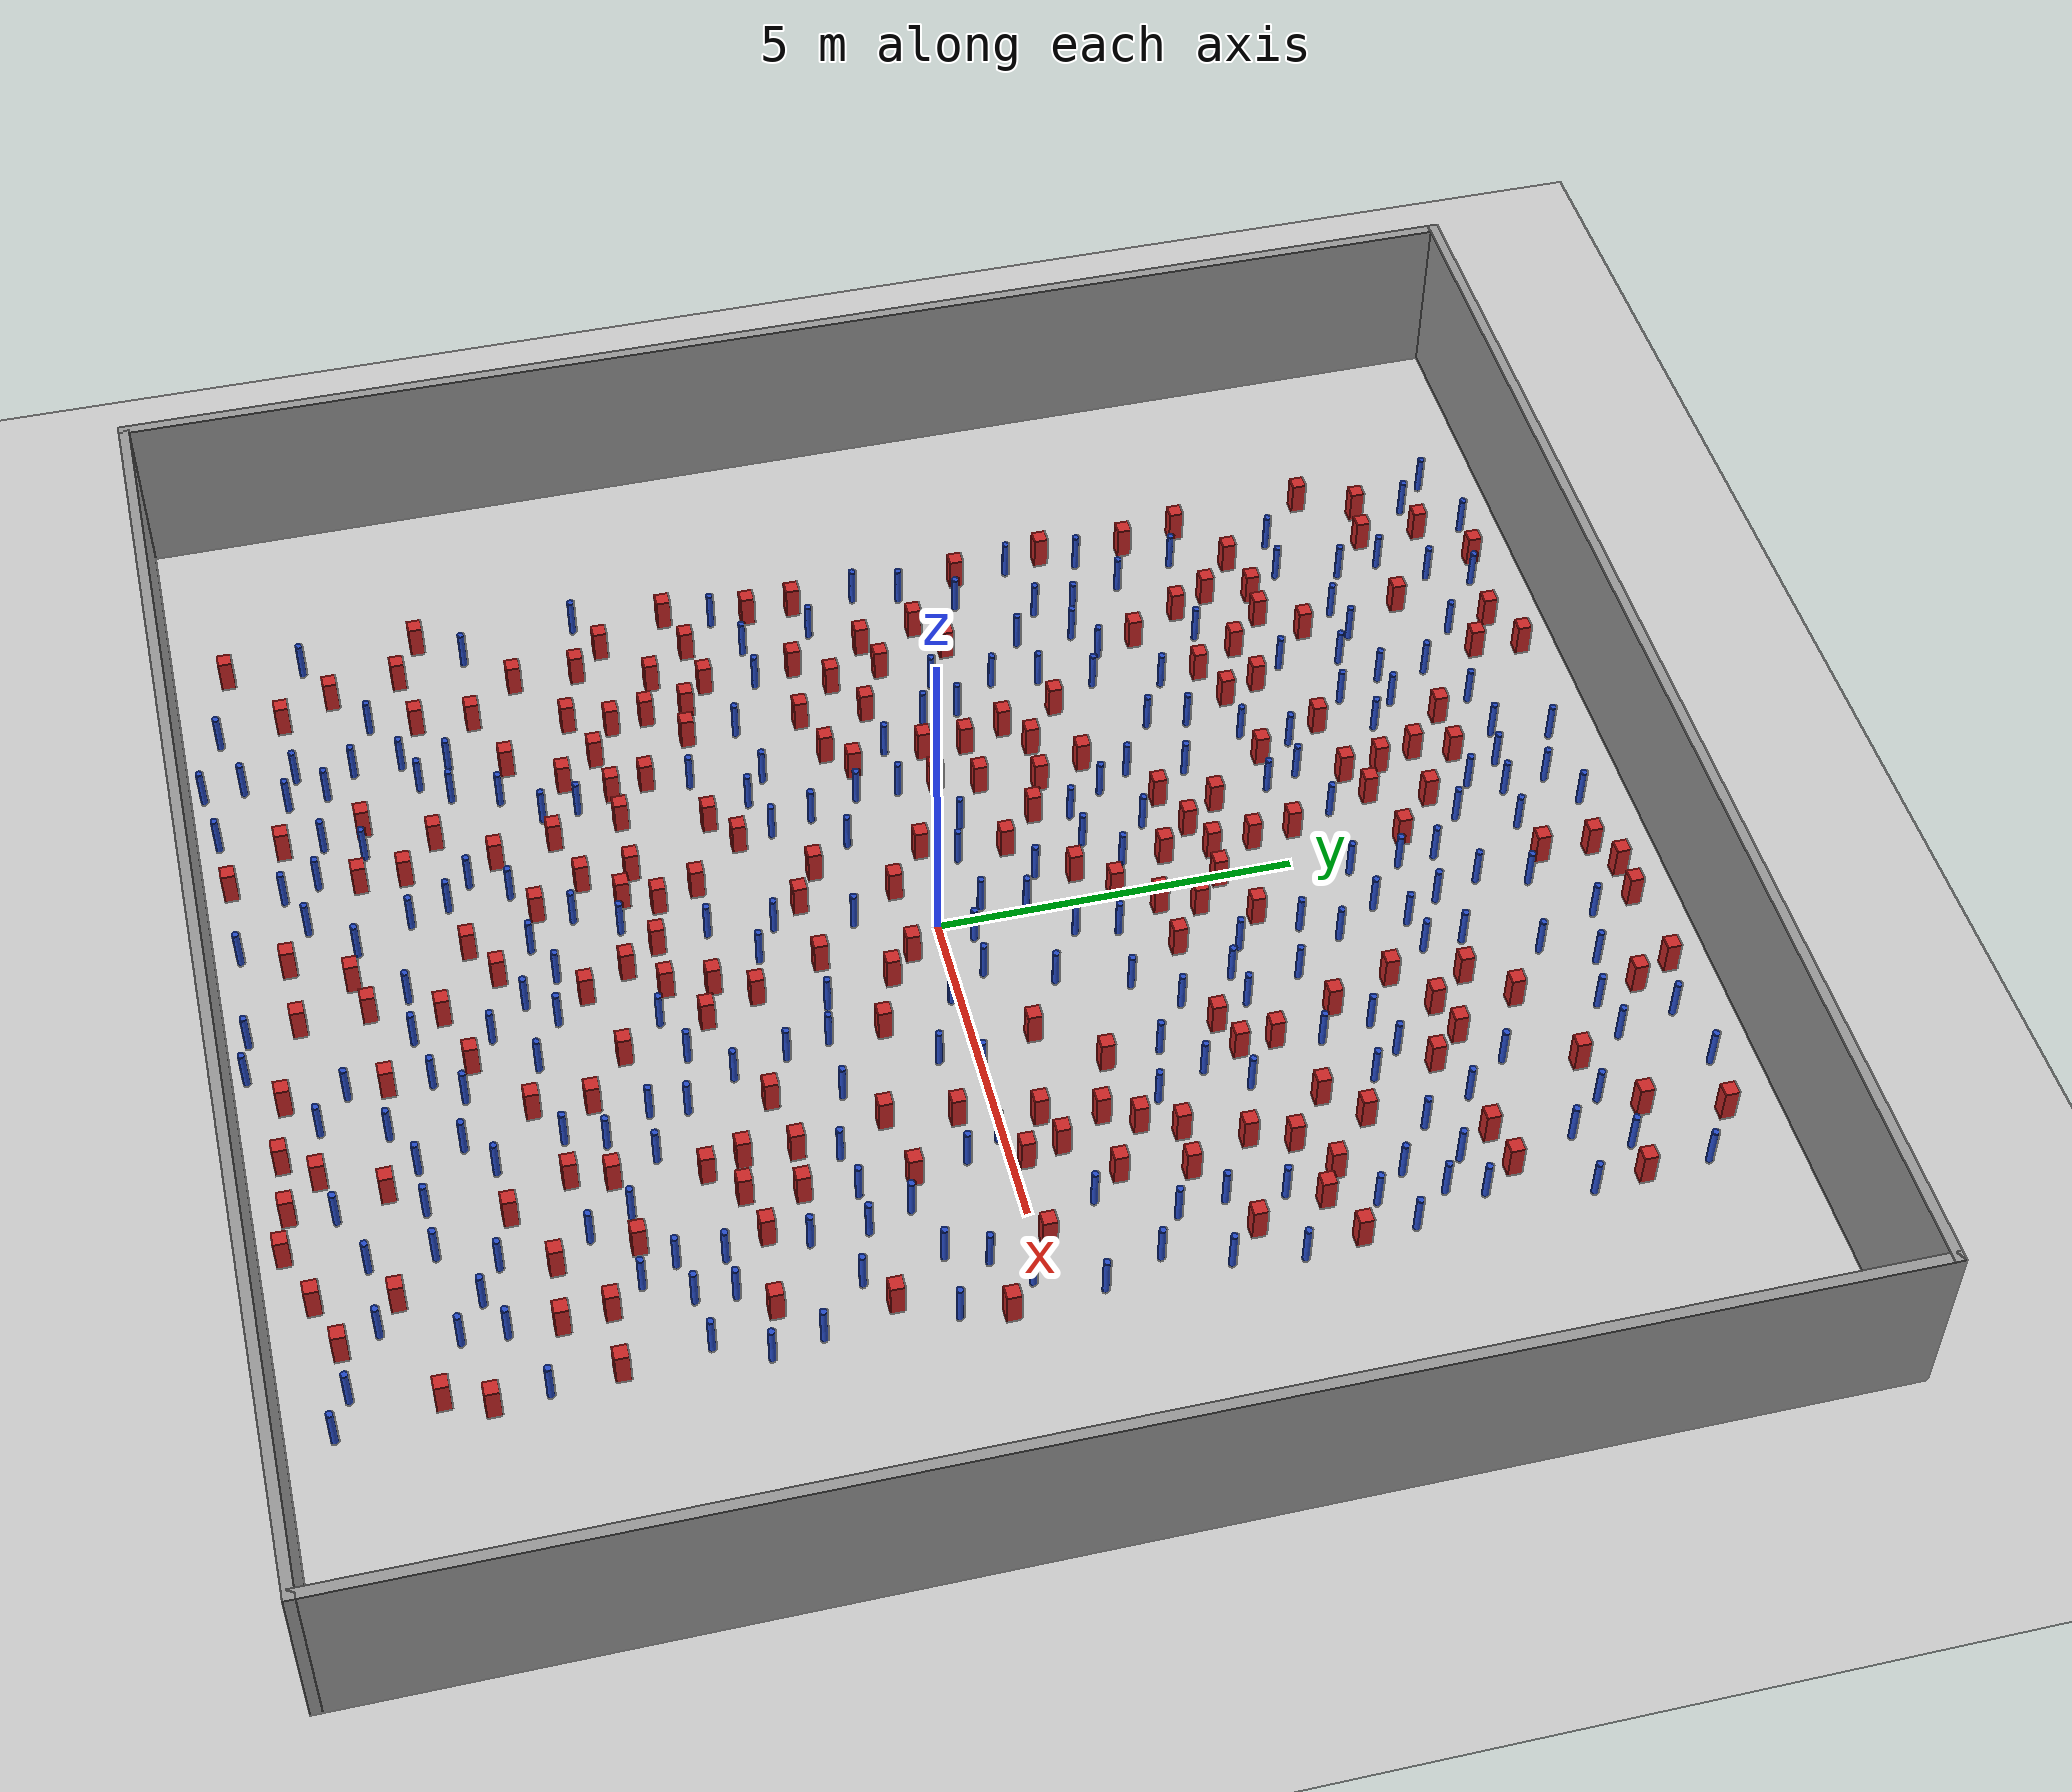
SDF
<sdf version="1.6">
 <world name="default">
  <light name="sun" type="directional">
   <pose>0 0 1000 0 -0 0</pose>
   <diffuse>0.8 0.8 0.8 1</diffuse>
   <specular>0.1 0.1 0.1 1</specular>
   <attenuation>
    <range>1000</range>
    <constant>0.9</constant>
    <linear>0.01</linear>
    <quadratic>0.001</quadratic>
   </attenuation>
   <direction>-0.5 0.5 -1</direction>
  </light>
  <model name="ground_plane">
   <static>1</static>
   <link name="link">
    <collision name="collision">
     <geometry><plane><normal>0 0 1</normal><size>100 100</size></plane></geometry>
     <surface><friction><ode><mu>100</mu><mu2>50</mu2></ode></friction></surface>
    </collision>
    <visual name="visual">
     <cast_shadows>0</cast_shadows>
     <geometry><plane><normal>0 0 1</normal><size>100 100</size></plane></geometry>
     <material>
      <ambient>1.0 1.0 1.0 1.0</ambient>
      <diffuse>0.8 0.8 0.8 1.0</diffuse>
      <specular>0.01 0.01 0.01 1.000000</specular>
     </material>
    </visual>
   </link>
  </model>
  <gravity>0 0 -9.8</gravity>
  <magnetic_field>6e-06 2.3e-05 -4.2e-05</magnetic_field>
  <atmosphere type="adiabatic"/>
  <physics name="default_physics" default="0" type="ode">
   <max_step_size>0.001</max_step_size>
   <real_time_factor>1</real_time_factor>
   <real_time_update_rate>1000</real_time_update_rate>
  </physics>
  <scene><ambient>0.4 0.4 0.4 1</ambient><background>0.7 0.7 0.7 1</background><shadows>1</shadows></scene>
  <spherical_coordinates>
   <surface_model>EARTH_WGS84</surface_model>
   <latitude_deg>0</latitude_deg>
   <longitude_deg>0</longitude_deg>
   <elevation>0</elevation>
   <heading_deg>0</heading_deg>
  </spherical_coordinates>
  <plugin name="gazebo_occupancy_map" filename="libgazebo_2Dmap_plugin.so">
   <map_resolution>0.05</map_resolution>
   <map_topic>generated_map</map_topic>
   <map_height>0.01</map_height>
   <map_size_x>50</map_size_x>
   <map_size_y>50</map_size_y>
  </plugin>
  <model name="NamedLocations">
   <static>true</static>
   <link name="DefaultStart"><pose>8.5 0 0 0 0 3.14</pose></link>
  </model>
  <model name="20x20_walls">
   <pose>0.044518 0.176112 0 0 -0 0</pose>
   <link name="Wall_1">
    <collision name="Wall_1_Collision">
     <geometry><box><size>20 0.15 2.5</size></box></geometry>
     <pose>0 0 1.25 0 -0 0</pose>
    </collision>
    <visual name="Wall_1_Visual">
     <pose>0 0 1.25 0 -0 0</pose>
     <geometry><box><size>20 0.15 2.5</size></box></geometry>
     <material>
      <script><uri>file://media/materials/scripts/gazebo.material</uri><name>Gazebo/Grey</name></script>
      <ambient>0.976471 0.992157 1 1</ambient>
     </material>
     <meta><layer>0</layer></meta>
    </visual>
    <pose>0 9.925 0 0 -0 0</pose>
   </link>
   <link name="Wall_3">
    <collision name="Wall_3_Collision">
     <geometry><box><size>20 0.15 2.5</size></box></geometry>
     <pose>0 0 1.25 0 -0 0</pose>
    </collision>
    <visual name="Wall_3_Visual">
     <pose>0 0 1.25 0 -0 0</pose>
     <geometry><box><size>20 0.15 2.5</size></box></geometry>
     <material>
      <script><uri>file://media/materials/scripts/gazebo.material</uri><name>Gazebo/Grey</name></script>
      <ambient>0.976471 0.992157 1 1</ambient>
     </material>
     <meta><layer>0</layer></meta>
    </visual>
    <pose>9.925 0 0 0 0 -1.5708</pose>
   </link>
   <link name="Wall_4">
    <collision name="Wall_4_Collision">
     <geometry><box><size>20 0.15 2.5</size></box></geometry>
     <pose>0 0 1.25 0 -0 0</pose>
    </collision>
    <visual name="Wall_4_Visual">
     <pose>0 0 1.25 0 -0 0</pose>
     <geometry><box><size>20 0.15 2.5</size></box></geometry>
     <material>
      <script><uri>file://media/materials/scripts/gazebo.material</uri><name>Gazebo/Grey</name></script>
      <ambient>0.976471 0.992157 1 1</ambient>
     </material>
     <meta><layer>0</layer></meta>
    </visual>
    <pose>0 -9.925 0 0 -0 3.14159</pose>
   </link>
   <link name="Wall_5">
    <collision name="Wall_5_Collision">
     <geometry><box><size>20 0.15 2.5</size></box></geometry>
     <pose>0 0 1.25 0 -0 0</pose>
    </collision>
    <visual name="Wall_5_Visual">
     <pose>0 0 1.25 0 -0 0</pose>
     <geometry><box><size>20 0.15 2.5</size></box></geometry>
     <material>
      <script><uri>file://media/materials/scripts/gazebo.material</uri><name>Gazebo/Grey</name></script>
      <ambient>0.976471 0.992157 1 1</ambient>
     </material>
     <meta><layer>0</layer></meta>
    </visual>
    <pose>-9.925 0 0 0 -0 1.5708</pose>
   </link>
   <static>1</static>
  </model>
  <model name="pole_obstacle0">
   <static>true</static>
   <pose>3.59999986201 2.11532828441 7.38925637345e-09 -8.47170692798e-08 1.24976764939e-08 -1.74513093025e-07</pose>
   <link name="link">
    <pose>0 0 0.3 0 -0 0</pose>
    <inertial>
     <mass>1</mass>
     <inertia><ixx>0.145833</ixx><ixy>0</ixy><ixz>0</ixz><iyy>0.145833</iyy><iyz>0</iyz><izz>0.125</izz></inertia>
    </inertial>
    <collision name="collision">
     <geometry><cylinder><radius>0.05</radius><length>.6</length></cylinder></geometry>
    </collision>
    <visual name="visual">
     <geometry><cylinder><radius>0.05</radius><length>.6</length></cylinder></geometry>
     <material>
      <script><name>Gazebo/Blue</name><uri>file://media/materials/scripts/gazebo.material</uri></script>
     </material>
    </visual>
   </link>
  </model>
  <model name="pole_obstacle1">
   <static>true</static>
   <pose>-4.2360421505 2.48236113303 7.38925637345e-09 -8.47170692798e-08 1.24976764937e-08 -1.74513093023e-07</pose>
   <link name="link">
    <pose>0 0 0.3 0 -0 0</pose>
    <inertial>
     <mass>1</mass>
     <inertia><ixx>0.145833</ixx><ixy>0</ixy><ixz>0</ixz><iyy>0.145833</iyy><iyz>0</iyz><izz>0.125</izz></inertia>
    </inertial>
    <collision name="collision">
     <geometry><cylinder><radius>0.05</radius><length>.6</length></cylinder></geometry>
    </collision>
    <visual name="visual">
     <geometry><cylinder><radius>0.05</radius><length>.6</length></cylinder></geometry>
     <material>
      <script><name>Gazebo/Blue</name><uri>file://media/materials/scripts/gazebo.material</uri></script>
     </material>
    </visual>
   </link>
  </model>
  <model name="square_post_obstacle0">
   <static>true</static>
   <pose>-2.43062324862 6.12856150608 1.91545236811e-07 -7.35059704564e-06 1.12565212e-07 2.39332434364e-05</pose>
   <link name="link">
    <pose>0 0 0.25 0 -0 0</pose>
    <inertial>
     <mass>100</mass>
     <inertia>
      <ixx>0.166667</ixx>
      <ixy>0</ixy>
      <ixz>0</ixz>
      <iyy>0.166667</iyy>
      <iyz>0</iyz>
      <izz>0.166667</izz>
     </inertia>
    </inertial>
    <collision name="collision"><geometry><box><size>.2 .2 .5</size></box></geometry></collision>
    <visual name="visual">
     <geometry><box><size>.2 .2 .5</size></box></geometry>
     <material>
      <script><name>Gazebo/Red</name><uri>file://media/materials/scripts/gazebo.material</uri></script>
     </material>
    </visual>
   </link>
  </model>
  <model name="square_post_obstacle1">
   <static>true</static>
   <pose>-4.81381183244 -0.451501283735 1.91545236811e-07 -7.35059704564e-06 1.12565212e-07 2.39332434364e-05</pose>
   <link name="link">
    <pose>0 0 0.25 0 -0 0</pose>
    <inertial>
     <mass>100</mass>
     <inertia>
      <ixx>0.166667</ixx>
      <ixy>0</ixy>
      <ixz>0</ixz>
      <iyy>0.166667</iyy>
      <iyz>0</iyz>
      <izz>0.166667</izz>
     </inertia>
    </inertial>
    <collision name="collision"><geometry><box><size>.2 .2 .5</size></box></geometry></collision>
    <visual name="visual">
     <geometry><box><size>.2 .2 .5</size></box></geometry>
     <material>
      <script><name>Gazebo/Red</name><uri>file://media/materials/scripts/gazebo.material</uri></script>
     </material>
    </visual>
   </link>
  </model>
  <model name="pole_obstacle2">
   <static>true</static>
   <pose>-6.46132631482 8.68634267327 7.38925637345e-09 -8.471706928e-08 1.24976765081e-08 -1.74513093015e-07</pose>
   <link name="link">
    <pose>0 0 0.3 0 -0 0</pose>
    <inertial>
     <mass>1</mass>
     <inertia><ixx>0.145833</ixx><ixy>0</ixy><ixz>0</ixz><iyy>0.145833</iyy><iyz>0</iyz><izz>0.125</izz></inertia>
    </inertial>
    <collision name="collision">
     <geometry><cylinder><radius>0.05</radius><length>.6</length></cylinder></geometry>
    </collision>
    <visual name="visual">
     <geometry><cylinder><radius>0.05</radius><length>.6</length></cylinder></geometry>
     <material>
      <script><name>Gazebo/Blue</name><uri>file://media/materials/scripts/gazebo.material</uri></script>
     </material>
    </visual>
   </link>
  </model>
  <model name="pole_obstacle3">
   <static>true</static>
   <pose>-3.7190828894 5.9537499802 7.38925637345e-09 -8.47170692798e-08 1.24976765033e-08 -1.74513093019e-07</pose>
   <link name="link">
    <pose>0 0 0.3 0 -0 0</pose>
    <inertial>
     <mass>1</mass>
     <inertia><ixx>0.145833</ixx><ixy>0</ixy><ixz>0</ixz><iyy>0.145833</iyy><iyz>0</iyz><izz>0.125</izz></inertia>
    </inertial>
    <collision name="collision">
     <geometry><cylinder><radius>0.05</radius><length>.6</length></cylinder></geometry>
    </collision>
    <visual name="visual">
     <geometry><cylinder><radius>0.05</radius><length>.6</length></cylinder></geometry>
     <material>
      <script><name>Gazebo/Blue</name><uri>file://media/materials/scripts/gazebo.material</uri></script>
     </material>
    </visual>
   </link>
  </model>
  <model name="pole_obstacle4">
   <static>true</static>
   <pose>-3.35792923234 -7.96196954808 7.38925637345e-09 -8.47170692793e-08 1.24976764454e-08 -1.74513093039e-07</pose>
   <link name="link">
    <pose>0 0 0.3 0 -0 0</pose>
    <inertial>
     <mass>1</mass>
     <inertia><ixx>0.145833</ixx><ixy>0</ixy><ixz>0</ixz><iyy>0.145833</iyy><iyz>0</iyz><izz>0.125</izz></inertia>
    </inertial>
    <collision name="collision">
     <geometry><cylinder><radius>0.05</radius><length>.6</length></cylinder></geometry>
    </collision>
    <visual name="visual">
     <geometry><cylinder><radius>0.05</radius><length>.6</length></cylinder></geometry>
     <material>
      <script><name>Gazebo/Blue</name><uri>file://media/materials/scripts/gazebo.material</uri></script>
     </material>
    </visual>
   </link>
  </model>
  <model name="pole_obstacle5">
   <static>true</static>
   <pose>1.31517857012 3.88095834125 7.38925637345e-09 -8.47170692799e-08 1.24976765053e-08 -1.74513093017e-07</pose>
   <link name="link">
    <pose>0 0 0.3 0 -0 0</pose>
    <inertial>
     <mass>1</mass>
     <inertia><ixx>0.145833</ixx><ixy>0</ixy><ixz>0</ixz><iyy>0.145833</iyy><iyz>0</iyz><izz>0.125</izz></inertia>
    </inertial>
    <collision name="collision">
     <geometry><cylinder><radius>0.05</radius><length>.6</length></cylinder></geometry>
    </collision>
    <visual name="visual">
     <geometry><cylinder><radius>0.05</radius><length>.6</length></cylinder></geometry>
     <material>
      <script><name>Gazebo/Blue</name><uri>file://media/materials/scripts/gazebo.material</uri></script>
     </material>
    </visual>
   </link>
  </model>
  <model name="pole_obstacle6">
   <static>true</static>
   <pose>-5.550322576 6.45025046927 7.38925637345e-09 -8.47170692796e-08 1.24976764786e-08 -1.74513093032e-07</pose>
   <link name="link">
    <pose>0 0 0.3 0 -0 0</pose>
    <inertial>
     <mass>1</mass>
     <inertia><ixx>0.145833</ixx><ixy>0</ixy><ixz>0</ixz><iyy>0.145833</iyy><iyz>0</iyz><izz>0.125</izz></inertia>
    </inertial>
    <collision name="collision">
     <geometry><cylinder><radius>0.05</radius><length>.6</length></cylinder></geometry>
    </collision>
    <visual name="visual">
     <geometry><cylinder><radius>0.05</radius><length>.6</length></cylinder></geometry>
     <material>
      <script><name>Gazebo/Blue</name><uri>file://media/materials/scripts/gazebo.material</uri></script>
     </material>
    </visual>
   </link>
  </model>
  <model name="square_post_obstacle2">
   <static>true</static>
   <pose>2.51177571954 6.67125785142 1.91545236811e-07 -7.35059704564e-06 1.12565212e-07 2.39332434364e-05</pose>
   <link name="link">
    <pose>0 0 0.25 0 -0 0</pose>
    <inertial>
     <mass>100</mass>
     <inertia>
      <ixx>0.166667</ixx>
      <ixy>0</ixy>
      <ixz>0</ixz>
      <iyy>0.166667</iyy>
      <iyz>0</iyz>
      <izz>0.166667</izz>
     </inertia>
    </inertial>
    <collision name="collision"><geometry><box><size>.2 .2 .5</size></box></geometry></collision>
    <visual name="visual">
     <geometry><box><size>.2 .2 .5</size></box></geometry>
     <material>
      <script><name>Gazebo/Red</name><uri>file://media/materials/scripts/gazebo.material</uri></script>
     </material>
    </visual>
   </link>
  </model>
  <model name="square_post_obstacle3">
   <static>true</static>
   <pose>-3.5253935339 -3.39183684715 1.91545236811e-07 -7.35059704564e-06 1.12565212e-07 2.39332434364e-05</pose>
   <link name="link">
    <pose>0 0 0.25 0 -0 0</pose>
    <inertial>
     <mass>100</mass>
     <inertia>
      <ixx>0.166667</ixx>
      <ixy>0</ixy>
      <ixz>0</ixz>
      <iyy>0.166667</iyy>
      <iyz>0</iyz>
      <izz>0.166667</izz>
     </inertia>
    </inertial>
    <collision name="collision"><geometry><box><size>.2 .2 .5</size></box></geometry></collision>
    <visual name="visual">
     <geometry><box><size>.2 .2 .5</size></box></geometry>
     <material>
      <script><name>Gazebo/Red</name><uri>file://media/materials/scripts/gazebo.material</uri></script>
     </material>
    </visual>
   </link>
  </model>
  <model name="square_post_obstacle4">
   <static>true</static>
   <pose>-5.34353529852 5.29566429069 1.91545236811e-07 -7.35059704564e-06 1.12565212e-07 2.39332434364e-05</pose>
   <link name="link">
    <pose>0 0 0.25 0 -0 0</pose>
    <inertial>
     <mass>100</mass>
     <inertia>
      <ixx>0.166667</ixx>
      <ixy>0</ixy>
      <ixz>0</ixz>
      <iyy>0.166667</iyy>
      <iyz>0</iyz>
      <izz>0.166667</izz>
     </inertia>
    </inertial>
    <collision name="collision"><geometry><box><size>.2 .2 .5</size></box></geometry></collision>
    <visual name="visual">
     <geometry><box><size>.2 .2 .5</size></box></geometry>
     <material>
      <script><name>Gazebo/Red</name><uri>file://media/materials/scripts/gazebo.material</uri></script>
     </material>
    </visual>
   </link>
  </model>
  <model name="pole_obstacle7">
   <static>true</static>
   <pose>3.22150232477 -7.4769451547 7.38925637345e-09 -8.47170692798e-08 1.24976765033e-08 -1.74513093019e-07</pose>
   <link name="link">
    <pose>0 0 0.3 0 -0 0</pose>
    <inertial>
     <mass>1</mass>
     <inertia><ixx>0.145833</ixx><ixy>0</ixy><ixz>0</ixz><iyy>0.145833</iyy><iyz>0</iyz><izz>0.125</izz></inertia>
    </inertial>
    <collision name="collision">
     <geometry><cylinder><radius>0.05</radius><length>.6</length></cylinder></geometry>
    </collision>
    <visual name="visual">
     <geometry><cylinder><radius>0.05</radius><length>.6</length></cylinder></geometry>
     <material>
      <script><name>Gazebo/Blue</name><uri>file://media/materials/scripts/gazebo.material</uri></script>
     </material>
    </visual>
   </link>
  </model>
  <model name="pole_obstacle8">
   <static>true</static>
   <pose>1.4504072979 5.25999386805 7.38925637345e-09 -8.47170692799e-08 1.24976765033e-08 -1.74513093018e-07</pose>
   <link name="link">
    <pose>0 0 0.3 0 -0 0</pose>
    <inertial>
     <mass>1</mass>
     <inertia><ixx>0.145833</ixx><ixy>0</ixy><ixz>0</ixz><iyy>0.145833</iyy><iyz>0</iyz><izz>0.125</izz></inertia>
    </inertial>
    <collision name="collision">
     <geometry><cylinder><radius>0.05</radius><length>.6</length></cylinder></geometry>
    </collision>
    <visual name="visual">
     <geometry><cylinder><radius>0.05</radius><length>.6</length></cylinder></geometry>
     <material>
      <script><name>Gazebo/Blue</name><uri>file://media/materials/scripts/gazebo.material</uri></script>
     </material>
    </visual>
   </link>
  </model>
  <model name="square_post_obstacle5">
   <static>true</static>
   <pose>3.1453970164 -5.60545074428 1.91545236811e-07 -7.35059704564e-06 1.12565212e-07 2.39332434364e-05</pose>
   <link name="link">
    <pose>0 0 0.25 0 -0 0</pose>
    <inertial>
     <mass>100</mass>
     <inertia>
      <ixx>0.166667</ixx>
      <ixy>0</ixy>
      <ixz>0</ixz>
      <iyy>0.166667</iyy>
      <iyz>0</iyz>
      <izz>0.166667</izz>
     </inertia>
    </inertial>
    <collision name="collision"><geometry><box><size>.2 .2 .5</size></box></geometry></collision>
    <visual name="visual">
     <geometry><box><size>.2 .2 .5</size></box></geometry>
     <material>
      <script><name>Gazebo/Red</name><uri>file://media/materials/scripts/gazebo.material</uri></script>
     </material>
    </visual>
   </link>
  </model>
  <model name="square_post_obstacle6">
   <static>true</static>
   <pose>-3.19749269244 1.14197946729 1.91545236811e-07 -7.35059704564e-06 1.12565212e-07 2.39332434364e-05</pose>
   <link name="link">
    <pose>0 0 0.25 0 -0 0</pose>
    <inertial>
     <mass>100</mass>
     <inertia>
      <ixx>0.166667</ixx>
      <ixy>0</ixy>
      <ixz>0</ixz>
      <iyy>0.166667</iyy>
      <iyz>0</iyz>
      <izz>0.166667</izz>
     </inertia>
    </inertial>
    <collision name="collision"><geometry><box><size>.2 .2 .5</size></box></geometry></collision>
    <visual name="visual">
     <geometry><box><size>.2 .2 .5</size></box></geometry>
     <material>
      <script><name>Gazebo/Red</name><uri>file://media/materials/scripts/gazebo.material</uri></script>
     </material>
    </visual>
   </link>
  </model>
  <model name="square_post_obstacle7">
   <static>true</static>
   <pose>2.4204341195 -8.75031236134 1.91545236811e-07 -7.35059704564e-06 1.12565212e-07 2.39332434364e-05</pose>
   <link name="link">
    <pose>0 0 0.25 0 -0 0</pose>
    <inertial>
     <mass>100</mass>
     <inertia>
      <ixx>0.166667</ixx>
      <ixy>0</ixy>
      <ixz>0</ixz>
      <iyy>0.166667</iyy>
      <iyz>0</iyz>
      <izz>0.166667</izz>
     </inertia>
    </inertial>
    <collision name="collision"><geometry><box><size>.2 .2 .5</size></box></geometry></collision>
    <visual name="visual">
     <geometry><box><size>.2 .2 .5</size></box></geometry>
     <material>
      <script><name>Gazebo/Red</name><uri>file://media/materials/scripts/gazebo.material</uri></script>
     </material>
    </visual>
   </link>
  </model>
  <model name="pole_obstacle9">
   <static>true</static>
   <pose>1.97348872524 4.52484014197 7.38925637345e-09 -8.471706928e-08 1.24976765202e-08 -1.7451309301e-07</pose>
   <link name="link">
    <pose>0 0 0.3 0 -0 0</pose>
    <inertial>
     <mass>1</mass>
     <inertia><ixx>0.145833</ixx><ixy>0</ixy><ixz>0</ixz><iyy>0.145833</iyy><iyz>0</iyz><izz>0.125</izz></inertia>
    </inertial>
    <collision name="collision">
     <geometry><cylinder><radius>0.05</radius><length>.6</length></cylinder></geometry>
    </collision>
    <visual name="visual">
     <geometry><cylinder><radius>0.05</radius><length>.6</length></cylinder></geometry>
     <material>
      <script><name>Gazebo/Blue</name><uri>file://media/materials/scripts/gazebo.material</uri></script>
     </material>
    </visual>
   </link>
  </model>
  <model name="pole_obstacle10">
   <static>true</static>
   <pose>-0.197017820715 9.29670923958 7.38925637345e-09 -8.47170692796e-08 1.24976764775e-08 -1.74513093034e-07</pose>
   <link name="link">
    <pose>0 0 0.3 0 -0 0</pose>
    <inertial>
     <mass>1</mass>
     <inertia><ixx>0.145833</ixx><ixy>0</ixy><ixz>0</ixz><iyy>0.145833</iyy><iyz>0</iyz><izz>0.125</izz></inertia>
    </inertial>
    <collision name="collision">
     <geometry><cylinder><radius>0.05</radius><length>.6</length></cylinder></geometry>
    </collision>
    <visual name="visual">
     <geometry><cylinder><radius>0.05</radius><length>.6</length></cylinder></geometry>
     <material>
      <script><name>Gazebo/Blue</name><uri>file://media/materials/scripts/gazebo.material</uri></script>
     </material>
    </visual>
   </link>
  </model>
  <model name="pole_obstacle11">
   <static>true</static>
   <pose>-4.75994385667 9.22691612218 7.38925637345e-09 -8.471706928e-08 1.24976765081e-08 -1.74513093015e-07</pose>
   <link name="link">
    <pose>0 0 0.3 0 -0 0</pose>
    <inertial>
     <mass>1</mass>
     <inertia><ixx>0.145833</ixx><ixy>0</ixy><ixz>0</ixz><iyy>0.145833</iyy><iyz>0</iyz><izz>0.125</izz></inertia>
    </inertial>
    <collision name="collision">
     <geometry><cylinder><radius>0.05</radius><length>.6</length></cylinder></geometry>
    </collision>
    <visual name="visual">
     <geometry><cylinder><radius>0.05</radius><length>.6</length></cylinder></geometry>
     <material>
      <script><name>Gazebo/Blue</name><uri>file://media/materials/scripts/gazebo.material</uri></script>
     </material>
    </visual>
   </link>
  </model>
  <model name="pole_obstacle12">
   <static>true</static>
   <pose>-5.93683408463 -0.54117805944 7.38925637345e-09 -8.47170692798e-08 1.24976765005e-08 -1.74513093021e-07</pose>
   <link name="link">
    <pose>0 0 0.3 0 -0 0</pose>
    <inertial>
     <mass>1</mass>
     <inertia><ixx>0.145833</ixx><ixy>0</ixy><ixz>0</ixz><iyy>0.145833</iyy><iyz>0</iyz><izz>0.125</izz></inertia>
    </inertial>
    <collision name="collision">
     <geometry><cylinder><radius>0.05</radius><length>.6</length></cylinder></geometry>
    </collision>
    <visual name="visual">
     <geometry><cylinder><radius>0.05</radius><length>.6</length></cylinder></geometry>
     <material>
      <script><name>Gazebo/Blue</name><uri>file://media/materials/scripts/gazebo.material</uri></script>
     </material>
    </visual>
   </link>
  </model>
  <model name="square_post_obstacle8">
   <static>true</static>
   <pose>6.14715143079 -7.69136076271 1.91545236811e-07 -7.35059704564e-06 1.12565212e-07 2.39332434364e-05</pose>
   <link name="link">
    <pose>0 0 0.25 0 -0 0</pose>
    <inertial>
     <mass>100</mass>
     <inertia>
      <ixx>0.166667</ixx>
      <ixy>0</ixy>
      <ixz>0</ixz>
      <iyy>0.166667</iyy>
      <iyz>0</iyz>
      <izz>0.166667</izz>
     </inertia>
    </inertial>
    <collision name="collision"><geometry><box><size>.2 .2 .5</size></box></geometry></collision>
    <visual name="visual">
     <geometry><box><size>.2 .2 .5</size></box></geometry>
     <material>
      <script><name>Gazebo/Red</name><uri>file://media/materials/scripts/gazebo.material</uri></script>
     </material>
    </visual>
   </link>
  </model>
  <model name="square_post_obstacle9">
   <static>true</static>
   <pose>0.414913555912 -0.457877879147 1.91545236811e-07 -7.35059704564e-06 1.12565212e-07 2.39332434364e-05</pose>
   <link name="link">
    <pose>0 0 0.25 0 -0 0</pose>
    <inertial>
     <mass>100</mass>
     <inertia>
      <ixx>0.166667</ixx>
      <ixy>0</ixy>
      <ixz>0</ixz>
      <iyy>0.166667</iyy>
      <iyz>0</iyz>
      <izz>0.166667</izz>
     </inertia>
    </inertial>
    <collision name="collision"><geometry><box><size>.2 .2 .5</size></box></geometry></collision>
    <visual name="visual">
     <geometry><box><size>.2 .2 .5</size></box></geometry>
     <material>
      <script><name>Gazebo/Red</name><uri>file://media/materials/scripts/gazebo.material</uri></script>
     </material>
    </visual>
   </link>
  </model>
  <model name="pole_obstacle13">
   <static>true</static>
   <pose>-1.33353379833 -7.7553256667 7.38925637345e-09 -8.47170692799e-08 1.24976765033e-08 -1.74513093018e-07</pose>
   <link name="link">
    <pose>0 0 0.3 0 -0 0</pose>
    <inertial>
     <mass>1</mass>
     <inertia><ixx>0.145833</ixx><ixy>0</ixy><ixz>0</ixz><iyy>0.145833</iyy><iyz>0</iyz><izz>0.125</izz></inertia>
    </inertial>
    <collision name="collision">
     <geometry><cylinder><radius>0.05</radius><length>.6</length></cylinder></geometry>
    </collision>
    <visual name="visual">
     <geometry><cylinder><radius>0.05</radius><length>.6</length></cylinder></geometry>
     <material>
      <script><name>Gazebo/Blue</name><uri>file://media/materials/scripts/gazebo.material</uri></script>
     </material>
    </visual>
   </link>
  </model>
  <model name="square_post_obstacle10">
   <static>true</static>
   <pose>-2.03097253095 5.16663899507 1.91545236811e-07 -7.35059704564e-06 1.12565212e-07 2.39332434364e-05</pose>
   <link name="link">
    <pose>0 0 0.25 0 -0 0</pose>
    <inertial>
     <mass>100</mass>
     <inertia>
      <ixx>0.166667</ixx>
      <ixy>0</ixy>
      <ixz>0</ixz>
      <iyy>0.166667</iyy>
      <iyz>0</iyz>
      <izz>0.166667</izz>
     </inertia>
    </inertial>
    <collision name="collision"><geometry><box><size>.2 .2 .5</size></box></geometry></collision>
    <visual name="visual">
     <geometry><box><size>.2 .2 .5</size></box></geometry>
     <material>
      <script><name>Gazebo/Red</name><uri>file://media/materials/scripts/gazebo.material</uri></script>
     </material>
    </visual>
   </link>
  </model>
  <model name="square_post_obstacle11">
   <static>true</static>
   <pose>-5.36677755158 -6.3792738897 1.91545236811e-07 -7.35059704564e-06 1.12565212e-07 2.39332434364e-05</pose>
   <link name="link">
    <pose>0 0 0.25 0 -0 0</pose>
    <inertial>
     <mass>100</mass>
     <inertia>
      <ixx>0.166667</ixx>
      <ixy>0</ixy>
      <ixz>0</ixz>
      <iyy>0.166667</iyy>
      <iyz>0</iyz>
      <izz>0.166667</izz>
     </inertia>
    </inertial>
    <collision name="collision"><geometry><box><size>.2 .2 .5</size></box></geometry></collision>
    <visual name="visual">
     <geometry><box><size>.2 .2 .5</size></box></geometry>
     <material>
      <script><name>Gazebo/Red</name><uri>file://media/materials/scripts/gazebo.material</uri></script>
     </material>
    </visual>
   </link>
  </model>
  <model name="pole_obstacle14">
   <static>true</static>
   <pose>3.93608415349 -8.31823323013 7.38925637345e-09 -8.47170692793e-08 1.24976764408e-08 -1.74513093041e-07</pose>
   <link name="link">
    <pose>0 0 0.3 0 -0 0</pose>
    <inertial>
     <mass>1</mass>
     <inertia><ixx>0.145833</ixx><ixy>0</ixy><ixz>0</ixz><iyy>0.145833</iyy><iyz>0</iyz><izz>0.125</izz></inertia>
    </inertial>
    <collision name="collision">
     <geometry><cylinder><radius>0.05</radius><length>.6</length></cylinder></geometry>
    </collision>
    <visual name="visual">
     <geometry><cylinder><radius>0.05</radius><length>.6</length></cylinder></geometry>
     <material>
      <script><name>Gazebo/Blue</name><uri>file://media/materials/scripts/gazebo.material</uri></script>
     </material>
    </visual>
   </link>
  </model>
  <model name="pole_obstacle15">
   <static>true</static>
   <pose>-6.84404924629 -7.82483388145 7.38925637345e-09 -8.47170692796e-08 1.24976764786e-08 -1.74513093032e-07</pose>
   <link name="link">
    <pose>0 0 0.3 0 -0 0</pose>
    <inertial>
     <mass>1</mass>
     <inertia><ixx>0.145833</ixx><ixy>0</ixy><ixz>0</ixz><iyy>0.145833</iyy><iyz>0</iyz><izz>0.125</izz></inertia>
    </inertial>
    <collision name="collision">
     <geometry><cylinder><radius>0.05</radius><length>.6</length></cylinder></geometry>
    </collision>
    <visual name="visual">
     <geometry><cylinder><radius>0.05</radius><length>.6</length></cylinder></geometry>
     <material>
      <script><name>Gazebo/Blue</name><uri>file://media/materials/scripts/gazebo.material</uri></script>
     </material>
    </visual>
   </link>
  </model>
  <model name="square_post_obstacle12">
   <static>true</static>
   <pose>-3.40680719447 1.74488713327 1.91545236811e-07 -7.35059704564e-06 1.12565212e-07 2.39332434364e-05</pose>
   <link name="link">
    <pose>0 0 0.25 0 -0 0</pose>
    <inertial>
     <mass>100</mass>
     <inertia>
      <ixx>0.166667</ixx>
      <ixy>0</ixy>
      <ixz>0</ixz>
      <iyy>0.166667</iyy>
      <iyz>0</iyz>
      <izz>0.166667</izz>
     </inertia>
    </inertial>
    <collision name="collision"><geometry><box><size>.2 .2 .5</size></box></geometry></collision>
    <visual name="visual">
     <geometry><box><size>.2 .2 .5</size></box></geometry>
     <material>
      <script><name>Gazebo/Red</name><uri>file://media/materials/scripts/gazebo.material</uri></script>
     </material>
    </visual>
   </link>
  </model>
  <model name="pole_obstacle16">
   <static>true</static>
   <pose>-2.56639658643 0.0287213058173 7.38925637345e-09 -8.47170692793e-08 1.24976764457e-08 -1.74513093039e-07</pose>
   <link name="link">
    <pose>0 0 0.3 0 -0 0</pose>
    <inertial>
     <mass>1</mass>
     <inertia><ixx>0.145833</ixx><ixy>0</ixy><ixz>0</ixz><iyy>0.145833</iyy><iyz>0</iyz><izz>0.125</izz></inertia>
    </inertial>
    <collision name="collision">
     <geometry><cylinder><radius>0.05</radius><length>.6</length></cylinder></geometry>
    </collision>
    <visual name="visual">
     <geometry><cylinder><radius>0.05</radius><length>.6</length></cylinder></geometry>
     <material>
      <script><name>Gazebo/Blue</name><uri>file://media/materials/scripts/gazebo.material</uri></script>
     </material>
    </visual>
   </link>
  </model>
  <model name="pole_obstacle17">
   <static>true</static>
   <pose>2.30088741263 -4.41169465217 7.38925637345e-09 -8.47170692798e-08 1.24976765033e-08 -1.74513093019e-07</pose>
   <link name="link">
    <pose>0 0 0.3 0 -0 0</pose>
    <inertial>
     <mass>1</mass>
     <inertia><ixx>0.145833</ixx><ixy>0</ixy><ixz>0</ixz><iyy>0.145833</iyy><iyz>0</iyz><izz>0.125</izz></inertia>
    </inertial>
    <collision name="collision">
     <geometry><cylinder><radius>0.05</radius><length>.6</length></cylinder></geometry>
    </collision>
    <visual name="visual">
     <geometry><cylinder><radius>0.05</radius><length>.6</length></cylinder></geometry>
     <material>
      <script><name>Gazebo/Blue</name><uri>file://media/materials/scripts/gazebo.material</uri></script>
     </material>
    </visual>
   </link>
  </model>
  <model name="square_post_obstacle13">
   <static>true</static>
   <pose>-4.24430106662 -2.66834817036 1.91545236811e-07 -7.35059704564e-06 1.12565212e-07 2.39332434364e-05</pose>
   <link name="link">
    <pose>0 0 0.25 0 -0 0</pose>
    <inertial>
     <mass>100</mass>
     <inertia>
      <ixx>0.166667</ixx>
      <ixy>0</ixy>
      <ixz>0</ixz>
      <iyy>0.166667</iyy>
      <iyz>0</iyz>
      <izz>0.166667</izz>
     </inertia>
    </inertial>
    <collision name="collision"><geometry><box><size>.2 .2 .5</size></box></geometry></collision>
    <visual name="visual">
     <geometry><box><size>.2 .2 .5</size></box></geometry>
     <material>
      <script><name>Gazebo/Red</name><uri>file://media/materials/scripts/gazebo.material</uri></script>
     </material>
    </visual>
   </link>
  </model>
  <model name="pole_obstacle18">
   <static>true</static>
   <pose>4.81392823287 -3.89418730835 7.38925637345e-09 -8.47170692798e-08 1.24976764937e-08 -1.74513093023e-07</pose>
   <link name="link">
    <pose>0 0 0.3 0 -0 0</pose>
    <inertial>
     <mass>1</mass>
     <inertia><ixx>0.145833</ixx><ixy>0</ixy><ixz>0</ixz><iyy>0.145833</iyy><iyz>0</iyz><izz>0.125</izz></inertia>
    </inertial>
    <collision name="collision">
     <geometry><cylinder><radius>0.05</radius><length>.6</length></cylinder></geometry>
    </collision>
    <visual name="visual">
     <geometry><cylinder><radius>0.05</radius><length>.6</length></cylinder></geometry>
     <material>
      <script><name>Gazebo/Blue</name><uri>file://media/materials/scripts/gazebo.material</uri></script>
     </material>
    </visual>
   </link>
  </model>
  <model name="square_post_obstacle14">
   <static>true</static>
   <pose>5.14971679762 6.14030444495 1.91545236811e-07 -7.35059704564e-06 1.12565212e-07 2.39332434364e-05</pose>
   <link name="link">
    <pose>0 0 0.25 0 -0 0</pose>
    <inertial>
     <mass>100</mass>
     <inertia>
      <ixx>0.166667</ixx>
      <ixy>0</ixy>
      <ixz>0</ixz>
      <iyy>0.166667</iyy>
      <iyz>0</iyz>
      <izz>0.166667</izz>
     </inertia>
    </inertial>
    <collision name="collision"><geometry><box><size>.2 .2 .5</size></box></geometry></collision>
    <visual name="visual">
     <geometry><box><size>.2 .2 .5</size></box></geometry>
     <material>
      <script><name>Gazebo/Red</name><uri>file://media/materials/scripts/gazebo.material</uri></script>
     </material>
    </visual>
   </link>
  </model>
  <model name="pole_obstacle19">
   <static>true</static>
   <pose>-1.75111806579 -0.878984291902 7.38925637345e-09 -8.47170692799e-08 1.24976765075e-08 -1.74513093017e-07</pose>
   <link name="link">
    <pose>0 0 0.3 0 -0 0</pose>
    <inertial>
     <mass>1</mass>
     <inertia><ixx>0.145833</ixx><ixy>0</ixy><ixz>0</ixz><iyy>0.145833</iyy><iyz>0</iyz><izz>0.125</izz></inertia>
    </inertial>
    <collision name="collision">
     <geometry><cylinder><radius>0.05</radius><length>.6</length></cylinder></geometry>
    </collision>
    <visual name="visual">
     <geometry><cylinder><radius>0.05</radius><length>.6</length></cylinder></geometry>
     <material>
      <script><name>Gazebo/Blue</name><uri>file://media/materials/scripts/gazebo.material</uri></script>
     </material>
    </visual>
   </link>
  </model>
  <model name="square_post_obstacle15">
   <static>true</static>
   <pose>0.689085537594 9.14299970515 1.91545236811e-07 -7.35059704564e-06 1.12565212e-07 2.39332434364e-05</pose>
   <link name="link">
    <pose>0 0 0.25 0 -0 0</pose>
    <inertial>
     <mass>100</mass>
     <inertia>
      <ixx>0.166667</ixx>
      <ixy>0</ixy>
      <ixz>0</ixz>
      <iyy>0.166667</iyy>
      <iyz>0</iyz>
      <izz>0.166667</izz>
     </inertia>
    </inertial>
    <collision name="collision"><geometry><box><size>.2 .2 .5</size></box></geometry></collision>
    <visual name="visual">
     <geometry><box><size>.2 .2 .5</size></box></geometry>
     <material>
      <script><name>Gazebo/Red</name><uri>file://media/materials/scripts/gazebo.material</uri></script>
     </material>
    </visual>
   </link>
  </model>
  <model name="square_post_obstacle16">
   <static>true</static>
   <pose>-6.91296433391 -8.90215459807 1.91545236811e-07 -7.35059704564e-06 1.12565212e-07 2.39332434364e-05</pose>
   <link name="link">
    <pose>0 0 0.25 0 -0 0</pose>
    <inertial>
     <mass>100</mass>
     <inertia>
      <ixx>0.166667</ixx>
      <ixy>0</ixy>
      <ixz>0</ixz>
      <iyy>0.166667</iyy>
      <iyz>0</iyz>
      <izz>0.166667</izz>
     </inertia>
    </inertial>
    <collision name="collision"><geometry><box><size>.2 .2 .5</size></box></geometry></collision>
    <visual name="visual">
     <geometry><box><size>.2 .2 .5</size></box></geometry>
     <material>
      <script><name>Gazebo/Red</name><uri>file://media/materials/scripts/gazebo.material</uri></script>
     </material>
    </visual>
   </link>
  </model>
  <model name="square_post_obstacle17">
   <static>true</static>
   <pose>-5.67544785788 0.962281058583 1.91545236811e-07 -7.35059704564e-06 1.12565212e-07 2.39332434364e-05</pose>
   <link name="link">
    <pose>0 0 0.25 0 -0 0</pose>
    <inertial>
     <mass>100</mass>
     <inertia>
      <ixx>0.166667</ixx>
      <ixy>0</ixy>
      <ixz>0</ixz>
      <iyy>0.166667</iyy>
      <iyz>0</iyz>
      <izz>0.166667</izz>
     </inertia>
    </inertial>
    <collision name="collision"><geometry><box><size>.2 .2 .5</size></box></geometry></collision>
    <visual name="visual">
     <geometry><box><size>.2 .2 .5</size></box></geometry>
     <material>
      <script><name>Gazebo/Red</name><uri>file://media/materials/scripts/gazebo.material</uri></script>
     </material>
    </visual>
   </link>
  </model>
  <model name="pole_obstacle20">
   <static>true</static>
   <pose>-5.65574733196 -9.14257695707 7.38925637345e-09 -8.471706928e-08 1.24976765081e-08 -1.74513093015e-07</pose>
   <link name="link">
    <pose>0 0 0.3 0 -0 0</pose>
    <inertial>
     <mass>1</mass>
     <inertia><ixx>0.145833</ixx><ixy>0</ixy><ixz>0</ixz><iyy>0.145833</iyy><iyz>0</iyz><izz>0.125</izz></inertia>
    </inertial>
    <collision name="collision">
     <geometry><cylinder><radius>0.05</radius><length>.6</length></cylinder></geometry>
    </collision>
    <visual name="visual">
     <geometry><cylinder><radius>0.05</radius><length>.6</length></cylinder></geometry>
     <material>
      <script><name>Gazebo/Blue</name><uri>file://media/materials/scripts/gazebo.material</uri></script>
     </material>
    </visual>
   </link>
  </model>
  <model name="pole_obstacle21">
   <static>true</static>
   <pose>-4.31479446998 -7.7911242373 7.38925637345e-09 -8.47170692796e-08 1.24976764786e-08 -1.74513093032e-07</pose>
   <link name="link">
    <pose>0 0 0.3 0 -0 0</pose>
    <inertial>
     <mass>1</mass>
     <inertia><ixx>0.145833</ixx><ixy>0</ixy><ixz>0</ixz><iyy>0.145833</iyy><iyz>0</iyz><izz>0.125</izz></inertia>
    </inertial>
    <collision name="collision">
     <geometry><cylinder><radius>0.05</radius><length>.6</length></cylinder></geometry>
    </collision>
    <visual name="visual">
     <geometry><cylinder><radius>0.05</radius><length>.6</length></cylinder></geometry>
     <material>
      <script><name>Gazebo/Blue</name><uri>file://media/materials/scripts/gazebo.material</uri></script>
     </material>
    </visual>
   </link>
  </model>
  <model name="pole_obstacle22">
   <static>true</static>
   <pose>5.89596875655 5.3019925495 7.38925637345e-09 -8.47170692796e-08 1.24976764786e-08 -1.74513093032e-07</pose>
   <link name="link">
    <pose>0 0 0.3 0 -0 0</pose>
    <inertial>
     <mass>1</mass>
     <inertia><ixx>0.145833</ixx><ixy>0</ixy><ixz>0</ixz><iyy>0.145833</iyy><iyz>0</iyz><izz>0.125</izz></inertia>
    </inertial>
    <collision name="collision">
     <geometry><cylinder><radius>0.05</radius><length>.6</length></cylinder></geometry>
    </collision>
    <visual name="visual">
     <geometry><cylinder><radius>0.05</radius><length>.6</length></cylinder></geometry>
     <material>
      <script><name>Gazebo/Blue</name><uri>file://media/materials/scripts/gazebo.material</uri></script>
     </material>
    </visual>
   </link>
  </model>
  <model name="pole_obstacle23">
   <static>true</static>
   <pose>-3.85838187228 8.57557303017 7.38925637345e-09 -8.47170692793e-08 1.24976764408e-08 -1.74513093041e-07</pose>
   <link name="link">
    <pose>0 0 0.3 0 -0 0</pose>
    <inertial>
     <mass>1</mass>
     <inertia><ixx>0.145833</ixx><ixy>0</ixy><ixz>0</ixz><iyy>0.145833</iyy><iyz>0</iyz><izz>0.125</izz></inertia>
    </inertial>
    <collision name="collision">
     <geometry><cylinder><radius>0.05</radius><length>.6</length></cylinder></geometry>
    </collision>
    <visual name="visual">
     <geometry><cylinder><radius>0.05</radius><length>.6</length></cylinder></geometry>
     <material>
      <script><name>Gazebo/Blue</name><uri>file://media/materials/scripts/gazebo.material</uri></script>
     </material>
    </visual>
   </link>
  </model>
  <model name="square_post_obstacle18">
   <static>true</static>
   <pose>2.15118313694 0.78848510376 1.91545236811e-07 -7.35059704564e-06 1.12565212e-07 2.39332434364e-05</pose>
   <link name="link">
    <pose>0 0 0.25 0 -0 0</pose>
    <inertial>
     <mass>100</mass>
     <inertia>
      <ixx>0.166667</ixx>
      <ixy>0</ixy>
      <ixz>0</ixz>
      <iyy>0.166667</iyy>
      <iyz>0</iyz>
      <izz>0.166667</izz>
     </inertia>
    </inertial>
    <collision name="collision"><geometry><box><size>.2 .2 .5</size></box></geometry></collision>
    <visual name="visual">
     <geometry><box><size>.2 .2 .5</size></box></geometry>
     <material>
      <script><name>Gazebo/Red</name><uri>file://media/materials/scripts/gazebo.material</uri></script>
     </material>
    </visual>
   </link>
  </model>
  <model name="pole_obstacle24">
   <static>true</static>
   <pose>2.27807471456 3.71019698925 7.38925637345e-09 -8.47170692798e-08 1.24976764939e-08 -1.74513093025e-07</pose>
   <link name="link">
    <pose>0 0 0.3 0 -0 0</pose>
    <inertial>
     <mass>1</mass>
     <inertia><ixx>0.145833</ixx><ixy>0</ixy><ixz>0</ixz><iyy>0.145833</iyy><iyz>0</iyz><izz>0.125</izz></inertia>
    </inertial>
    <collision name="collision">
     <geometry><cylinder><radius>0.05</radius><length>.6</length></cylinder></geometry>
    </collision>
    <visual name="visual">
     <geometry><cylinder><radius>0.05</radius><length>.6</length></cylinder></geometry>
     <material>
      <script><name>Gazebo/Blue</name><uri>file://media/materials/scripts/gazebo.material</uri></script>
     </material>
    </visual>
   </link>
  </model>
  <model name="pole_obstacle25">
   <static>true</static>
   <pose>-2.23034080362 6.92175021675 7.38925637345e-09 -8.47170692798e-08 1.24976765033e-08 -1.74513093019e-07</pose>
   <link name="link">
    <pose>0 0 0.3 0 -0 0</pose>
    <inertial>
     <mass>1</mass>
     <inertia><ixx>0.145833</ixx><ixy>0</ixy><ixz>0</ixz><iyy>0.145833</iyy><iyz>0</iyz><izz>0.125</izz></inertia>
    </inertial>
    <collision name="collision">
     <geometry><cylinder><radius>0.05</radius><length>.6</length></cylinder></geometry>
    </collision>
    <visual name="visual">
     <geometry><cylinder><radius>0.05</radius><length>.6</length></cylinder></geometry>
     <material>
      <script><name>Gazebo/Blue</name><uri>file://media/materials/scripts/gazebo.material</uri></script>
     </material>
    </visual>
   </link>
  </model>
  <model name="pole_obstacle26">
   <static>true</static>
   <pose>-0.854000648332 7.86369184011 7.38925637345e-09 -8.471706928e-08 1.24976765086e-08 -1.74513093015e-07</pose>
   <link name="link">
    <pose>0 0 0.3 0 -0 0</pose>
    <inertial>
     <mass>1</mass>
     <inertia><ixx>0.145833</ixx><ixy>0</ixy><ixz>0</ixz><iyy>0.145833</iyy><iyz>0</iyz><izz>0.125</izz></inertia>
    </inertial>
    <collision name="collision">
     <geometry><cylinder><radius>0.05</radius><length>.6</length></cylinder></geometry>
    </collision>
    <visual name="visual">
     <geometry><cylinder><radius>0.05</radius><length>.6</length></cylinder></geometry>
     <material>
      <script><name>Gazebo/Blue</name><uri>file://media/materials/scripts/gazebo.material</uri></script>
     </material>
    </visual>
   </link>
  </model>
  <model name="pole_obstacle27">
   <static>true</static>
   <pose>2.58216904432 -1.89217607525 7.38925637345e-09 -8.471706928e-08 1.24976765152e-08 -1.74513093012e-07</pose>
   <link name="link">
    <pose>0 0 0.3 0 -0 0</pose>
    <inertial>
     <mass>1</mass>
     <inertia><ixx>0.145833</ixx><ixy>0</ixy><ixz>0</ixz><iyy>0.145833</iyy><iyz>0</iyz><izz>0.125</izz></inertia>
    </inertial>
    <collision name="collision">
     <geometry><cylinder><radius>0.05</radius><length>.6</length></cylinder></geometry>
    </collision>
    <visual name="visual">
     <geometry><cylinder><radius>0.05</radius><length>.6</length></cylinder></geometry>
     <material>
      <script><name>Gazebo/Blue</name><uri>file://media/materials/scripts/gazebo.material</uri></script>
     </material>
    </visual>
   </link>
  </model>
  <model name="pole_obstacle28">
   <static>true</static>
   <pose>6.43142556251 -3.62551673232 7.38925637345e-09 -8.47170692798e-08 1.24976764937e-08 -1.74513093023e-07</pose>
   <link name="link">
    <pose>0 0 0.3 0 -0 0</pose>
    <inertial>
     <mass>1</mass>
     <inertia><ixx>0.145833</ixx><ixy>0</ixy><ixz>0</ixz><iyy>0.145833</iyy><iyz>0</iyz><izz>0.125</izz></inertia>
    </inertial>
    <collision name="collision">
     <geometry><cylinder><radius>0.05</radius><length>.6</length></cylinder></geometry>
    </collision>
    <visual name="visual">
     <geometry><cylinder><radius>0.05</radius><length>.6</length></cylinder></geometry>
     <material>
      <script><name>Gazebo/Blue</name><uri>file://media/materials/scripts/gazebo.material</uri></script>
     </material>
    </visual>
   </link>
  </model>
  <model name="square_post_obstacle19">
   <static>true</static>
   <pose>1.90659724652 -5.89209735666 1.91545236811e-07 -7.35059704564e-06 1.12565212e-07 2.39332434364e-05</pose>
   <link name="link">
    <pose>0 0 0.25 0 -0 0</pose>
    <inertial>
     <mass>100</mass>
     <inertia>
      <ixx>0.166667</ixx>
      <ixy>0</ixy>
      <ixz>0</ixz>
      <iyy>0.166667</iyy>
      <iyz>0</iyz>
      <izz>0.166667</izz>
     </inertia>
    </inertial>
    <collision name="collision"><geometry><box><size>.2 .2 .5</size></box></geometry></collision>
    <visual name="visual">
     <geometry><box><size>.2 .2 .5</size></box></geometry>
     <material>
      <script><name>Gazebo/Red</name><uri>file://media/materials/scripts/gazebo.material</uri></script>
     </material>
    </visual>
   </link>
  </model>
  <model name="square_post_obstacle20">
   <static>true</static>
   <pose>0.346388215493 3.02720264312 1.91545236811e-07 -7.35059704564e-06 1.12565212e-07 2.39332434364e-05</pose>
   <link name="link">
    <pose>0 0 0.25 0 -0 0</pose>
    <inertial>
     <mass>100</mass>
     <inertia>
      <ixx>0.166667</ixx>
      <ixy>0</ixy>
      <ixz>0</ixz>
      <iyy>0.166667</iyy>
      <iyz>0</iyz>
      <izz>0.166667</izz>
     </inertia>
    </inertial>
    <collision name="collision"><geometry><box><size>.2 .2 .5</size></box></geometry></collision>
    <visual name="visual">
     <geometry><box><size>.2 .2 .5</size></box></geometry>
     <material>
      <script><name>Gazebo/Red</name><uri>file://media/materials/scripts/gazebo.material</uri></script>
     </material>
    </visual>
   </link>
  </model>
  <model name="pole_obstacle29">
   <static>true</static>
   <pose>-5.50109739232 3.32762876711 7.38925637345e-09 -8.47170692798e-08 1.24976764937e-08 -1.74513093023e-07</pose>
   <link name="link">
    <pose>0 0 0.3 0 -0 0</pose>
    <inertial>
     <mass>1</mass>
     <inertia><ixx>0.145833</ixx><ixy>0</ixy><ixz>0</ixz><iyy>0.145833</iyy><iyz>0</iyz><izz>0.125</izz></inertia>
    </inertial>
    <collision name="collision">
     <geometry><cylinder><radius>0.05</radius><length>.6</length></cylinder></geometry>
    </collision>
    <visual name="visual">
     <geometry><cylinder><radius>0.05</radius><length>.6</length></cylinder></geometry>
     <material>
      <script><name>Gazebo/Blue</name><uri>file://media/materials/scripts/gazebo.material</uri></script>
     </material>
    </visual>
   </link>
  </model>
  <model name="square_post_obstacle21">
   <static>true</static>
   <pose>6.23103900334 -5.47775100667 1.91545236811e-07 -7.35059704564e-06 1.12565212e-07 2.39332434364e-05</pose>
   <link name="link">
    <pose>0 0 0.25 0 -0 0</pose>
    <inertial>
     <mass>100</mass>
     <inertia>
      <ixx>0.166667</ixx>
      <ixy>0</ixy>
      <ixz>0</ixz>
      <iyy>0.166667</iyy>
      <iyz>0</iyz>
      <izz>0.166667</izz>
     </inertia>
    </inertial>
    <collision name="collision"><geometry><box><size>.2 .2 .5</size></box></geometry></collision>
    <visual name="visual">
     <geometry><box><size>.2 .2 .5</size></box></geometry>
     <material>
      <script><name>Gazebo/Red</name><uri>file://media/materials/scripts/gazebo.material</uri></script>
     </material>
    </visual>
   </link>
  </model>
  <model name="pole_obstacle30">
   <static>true</static>
   <pose>3.65956599848 3.36490128789 7.38925637345e-09 -8.47170692798e-08 1.24976764939e-08 -1.74513093025e-07</pose>
   <link name="link">
    <pose>0 0 0.3 0 -0 0</pose>
    <inertial>
     <mass>1</mass>
     <inertia><ixx>0.145833</ixx><ixy>0</ixy><ixz>0</ixz><iyy>0.145833</iyy><iyz>0</iyz><izz>0.125</izz></inertia>
    </inertial>
    <collision name="collision">
     <geometry><cylinder><radius>0.05</radius><length>.6</length></cylinder></geometry>
    </collision>
    <visual name="visual">
     <geometry><cylinder><radius>0.05</radius><length>.6</length></cylinder></geometry>
     <material>
      <script><name>Gazebo/Blue</name><uri>file://media/materials/scripts/gazebo.material</uri></script>
     </material>
    </visual>
   </link>
  </model>
  <model name="square_post_obstacle22">
   <static>true</static>
   <pose>4.71784901843 3.6338639334 1.91545236811e-07 -7.35059704564e-06 1.12565212e-07 2.39332434364e-05</pose>
   <link name="link">
    <pose>0 0 0.25 0 -0 0</pose>
    <inertial>
     <mass>100</mass>
     <inertia>
      <ixx>0.166667</ixx>
      <ixy>0</ixy>
      <ixz>0</ixz>
      <iyy>0.166667</iyy>
      <iyz>0</iyz>
      <izz>0.166667</izz>
     </inertia>
    </inertial>
    <collision name="collision"><geometry><box><size>.2 .2 .5</size></box></geometry></collision>
    <visual name="visual">
     <geometry><box><size>.2 .2 .5</size></box></geometry>
     <material>
      <script><name>Gazebo/Red</name><uri>file://media/materials/scripts/gazebo.material</uri></script>
     </material>
    </visual>
   </link>
  </model>
  <model name="square_post_obstacle23">
   <static>true</static>
   <pose>3.29476710435 -0.517945850544 1.91545236811e-07 -7.35059704564e-06 1.12565212e-07 2.39332434364e-05</pose>
   <link name="link">
    <pose>0 0 0.25 0 -0 0</pose>
    <inertial>
     <mass>100</mass>
     <inertia>
      <ixx>0.166667</ixx>
      <ixy>0</ixy>
      <ixz>0</ixz>
      <iyy>0.166667</iyy>
      <iyz>0</iyz>
      <izz>0.166667</izz>
     </inertia>
    </inertial>
    <collision name="collision"><geometry><box><size>.2 .2 .5</size></box></geometry></collision>
    <visual name="visual">
     <geometry><box><size>.2 .2 .5</size></box></geometry>
     <material>
      <script><name>Gazebo/Red</name><uri>file://media/materials/scripts/gazebo.material</uri></script>
     </material>
    </visual>
   </link>
  </model>
  <model name="pole_obstacle31">
   <static>true</static>
   <pose>-1.85217105316 -6.44201122828 7.38925637345e-09 -8.47170692799e-08 1.24976765033e-08 -1.74513093018e-07</pose>
   <link name="link">
    <pose>0 0 0.3 0 -0 0</pose>
    <inertial>
     <mass>1</mass>
     <inertia><ixx>0.145833</ixx><ixy>0</ixy><ixz>0</ixz><iyy>0.145833</iyy><iyz>0</iyz><izz>0.125</izz></inertia>
    </inertial>
    <collision name="collision">
     <geometry><cylinder><radius>0.05</radius><length>.6</length></cylinder></geometry>
    </collision>
    <visual name="visual">
     <geometry><cylinder><radius>0.05</radius><length>.6</length></cylinder></geometry>
     <material>
      <script><name>Gazebo/Blue</name><uri>file://media/materials/scripts/gazebo.material</uri></script>
     </material>
    </visual>
   </link>
  </model>
  <model name="square_post_obstacle24">
   <static>true</static>
   <pose>-6.54042031129 1.79965636281 1.91545236811e-07 -7.35059704564e-06 1.12565212e-07 2.39332434364e-05</pose>
   <link name="link">
    <pose>0 0 0.25 0 -0 0</pose>
    <inertial>
     <mass>100</mass>
     <inertia>
      <ixx>0.166667</ixx>
      <ixy>0</ixy>
      <ixz>0</ixz>
      <iyy>0.166667</iyy>
      <iyz>0</iyz>
      <izz>0.166667</izz>
     </inertia>
    </inertial>
    <collision name="collision"><geometry><box><size>.2 .2 .5</size></box></geometry></collision>
    <visual name="visual">
     <geometry><box><size>.2 .2 .5</size></box></geometry>
     <material>
      <script><name>Gazebo/Red</name><uri>file://media/materials/scripts/gazebo.material</uri></script>
     </material>
    </visual>
   </link>
  </model>
  <model name="square_post_obstacle25">
   <static>true</static>
   <pose>-4.2230417161 -1.03013316784 1.91545236811e-07 -7.35059704564e-06 1.12565212e-07 2.39332434364e-05</pose>
   <link name="link">
    <pose>0 0 0.25 0 -0 0</pose>
    <inertial>
     <mass>100</mass>
     <inertia>
      <ixx>0.166667</ixx>
      <ixy>0</ixy>
      <ixz>0</ixz>
      <iyy>0.166667</iyy>
      <iyz>0</iyz>
      <izz>0.166667</izz>
     </inertia>
    </inertial>
    <collision name="collision"><geometry><box><size>.2 .2 .5</size></box></geometry></collision>
    <visual name="visual">
     <geometry><box><size>.2 .2 .5</size></box></geometry>
     <material>
      <script><name>Gazebo/Red</name><uri>file://media/materials/scripts/gazebo.material</uri></script>
     </material>
    </visual>
   </link>
  </model>
  <model name="square_post_obstacle26">
   <static>true</static>
   <pose>-0.211819601924 -7.74384271224 1.91545236811e-07 -7.35059704564e-06 1.12565212e-07 2.39332434364e-05</pose>
   <link name="link">
    <pose>0 0 0.25 0 -0 0</pose>
    <inertial>
     <mass>100</mass>
     <inertia>
      <ixx>0.166667</ixx>
      <ixy>0</ixy>
      <ixz>0</ixz>
      <iyy>0.166667</iyy>
      <iyz>0</iyz>
      <izz>0.166667</izz>
     </inertia>
    </inertial>
    <collision name="collision"><geometry><box><size>.2 .2 .5</size></box></geometry></collision>
    <visual name="visual">
     <geometry><box><size>.2 .2 .5</size></box></geometry>
     <material>
      <script><name>Gazebo/Red</name><uri>file://media/materials/scripts/gazebo.material</uri></script>
     </material>
    </visual>
   </link>
  </model>
  <model name="pole_obstacle32">
   <static>true</static>
   <pose>2.79741233737 2.35532736677 7.38925637345e-09 -8.47170692798e-08 1.24976764939e-08 -1.74513093025e-07</pose>
   <link name="link">
    <pose>0 0 0.3 0 -0 0</pose>
    <inertial>
     <mass>1</mass>
     <inertia><ixx>0.145833</ixx><ixy>0</ixy><ixz>0</ixz><iyy>0.145833</iyy><iyz>0</iyz><izz>0.125</izz></inertia>
    </inertial>
    <collision name="collision">
     <geometry><cylinder><radius>0.05</radius><length>.6</length></cylinder></geometry>
    </collision>
    <visual name="visual">
     <geometry><cylinder><radius>0.05</radius><length>.6</length></cylinder></geometry>
     <material>
      <script><name>Gazebo/Blue</name><uri>file://media/materials/scripts/gazebo.material</uri></script>
     </material>
    </visual>
   </link>
  </model>
  <model name="square_post_obstacle27">
   <static>true</static>
   <pose>1.10197446139 -9.03624897904 1.91545236811e-07 -7.35059704564e-06 1.12565212e-07 2.39332434364e-05</pose>
   <link name="link">
    <pose>0 0 0.25 0 -0 0</pose>
    <inertial>
     <mass>100</mass>
     <inertia>
      <ixx>0.166667</ixx>
      <ixy>0</ixy>
      <ixz>0</ixz>
      <iyy>0.166667</iyy>
      <iyz>0</iyz>
      <izz>0.166667</izz>
     </inertia>
    </inertial>
    <collision name="collision"><geometry><box><size>.2 .2 .5</size></box></geometry></collision>
    <visual name="visual">
     <geometry><box><size>.2 .2 .5</size></box></geometry>
     <material>
      <script><name>Gazebo/Red</name><uri>file://media/materials/scripts/gazebo.material</uri></script>
     </material>
    </visual>
   </link>
  </model>
  <model name="square_post_obstacle28">
   <static>true</static>
   <pose>4.1805404886 0.185177053721 1.91545236811e-07 -7.35059704564e-06 1.12565212e-07 2.39332434364e-05</pose>
   <link name="link">
    <pose>0 0 0.25 0 -0 0</pose>
    <inertial>
     <mass>100</mass>
     <inertia>
      <ixx>0.166667</ixx>
      <ixy>0</ixy>
      <ixz>0</ixz>
      <iyy>0.166667</iyy>
      <iyz>0</iyz>
      <izz>0.166667</izz>
     </inertia>
    </inertial>
    <collision name="collision"><geometry><box><size>.2 .2 .5</size></box></geometry></collision>
    <visual name="visual">
     <geometry><box><size>.2 .2 .5</size></box></geometry>
     <material>
      <script><name>Gazebo/Red</name><uri>file://media/materials/scripts/gazebo.material</uri></script>
     </material>
    </visual>
   </link>
  </model>
  <model name="pole_obstacle33">
   <static>true</static>
   <pose>1.62228093729 2.28337743721 7.38925637345e-09 -8.47170692799e-08 1.24976765053e-08 -1.74513093017e-07</pose>
   <link name="link">
    <pose>0 0 0.3 0 -0 0</pose>
    <inertial>
     <mass>1</mass>
     <inertia><ixx>0.145833</ixx><ixy>0</ixy><ixz>0</ixz><iyy>0.145833</iyy><iyz>0</iyz><izz>0.125</izz></inertia>
    </inertial>
    <collision name="collision">
     <geometry><cylinder><radius>0.05</radius><length>.6</length></cylinder></geometry>
    </collision>
    <visual name="visual">
     <geometry><cylinder><radius>0.05</radius><length>.6</length></cylinder></geometry>
     <material>
      <script><name>Gazebo/Blue</name><uri>file://media/materials/scripts/gazebo.material</uri></script>
     </material>
    </visual>
   </link>
  </model>
  <model name="pole_obstacle34">
   <static>true</static>
   <pose>3.97082470784 8.35610358816 7.38925637345e-09 -8.47170692793e-08 1.24976764405e-08 -1.74513093041e-07</pose>
   <link name="link">
    <pose>0 0 0.3 0 -0 0</pose>
    <inertial>
     <mass>1</mass>
     <inertia><ixx>0.145833</ixx><ixy>0</ixy><ixz>0</ixz><iyy>0.145833</iyy><iyz>0</iyz><izz>0.125</izz></inertia>
    </inertial>
    <collision name="collision">
     <geometry><cylinder><radius>0.05</radius><length>.6</length></cylinder></geometry>
    </collision>
    <visual name="visual">
     <geometry><cylinder><radius>0.05</radius><length>.6</length></cylinder></geometry>
     <material>
      <script><name>Gazebo/Blue</name><uri>file://media/materials/scripts/gazebo.material</uri></script>
     </material>
    </visual>
   </link>
  </model>
  <model name="square_post_obstacle29">
   <static>true</static>
   <pose>5.1266658337 -8.82335839244 1.91545236811e-07 -7.35059704564e-06 1.12565212e-07 2.39332434364e-05</pose>
   <link name="link">
    <pose>0 0 0.25 0 -0 0</pose>
    <inertial>
     <mass>100</mass>
     <inertia>
      <ixx>0.166667</ixx>
      <ixy>0</ixy>
      <ixz>0</ixz>
      <iyy>0.166667</iyy>
      <iyz>0</iyz>
      <izz>0.166667</izz>
     </inertia>
    </inertial>
    <collision name="collision"><geometry><box><size>.2 .2 .5</size></box></geometry></collision>
    <visual name="visual">
     <geometry><box><size>.2 .2 .5</size></box></geometry>
     <material>
      <script><name>Gazebo/Red</name><uri>file://media/materials/scripts/gazebo.material</uri></script>
     </material>
    </visual>
   </link>
  </model>
  <model name="pole_obstacle35">
   <static>true</static>
   <pose>4.66362428479 9.38741379297 7.38925637345e-09 -8.471706928e-08 1.24976765081e-08 -1.74513093015e-07</pose>
   <link name="link">
    <pose>0 0 0.3 0 -0 0</pose>
    <inertial>
     <mass>1</mass>
     <inertia><ixx>0.145833</ixx><ixy>0</ixy><ixz>0</ixz><iyy>0.145833</iyy><iyz>0</iyz><izz>0.125</izz></inertia>
    </inertial>
    <collision name="collision">
     <geometry><cylinder><radius>0.05</radius><length>.6</length></cylinder></geometry>
    </collision>
    <visual name="visual">
     <geometry><cylinder><radius>0.05</radius><length>.6</length></cylinder></geometry>
     <material>
      <script><name>Gazebo/Blue</name><uri>file://media/materials/scripts/gazebo.material</uri></script>
     </material>
    </visual>
   </link>
  </model>
  <model name="square_post_obstacle30">
   <static>true</static>
   <pose>2.84793238087 1.60094142056 1.91545236811e-07 -7.35059704564e-06 1.12565212e-07 2.39332434364e-05</pose>
   <link name="link">
    <pose>0 0 0.25 0 -0 0</pose>
    <inertial>
     <mass>100</mass>
     <inertia>
      <ixx>0.166667</ixx>
      <ixy>0</ixy>
      <ixz>0</ixz>
      <iyy>0.166667</iyy>
      <iyz>0</iyz>
      <izz>0.166667</izz>
     </inertia>
    </inertial>
    <collision name="collision"><geometry><box><size>.2 .2 .5</size></box></geometry></collision>
    <visual name="visual">
     <geometry><box><size>.2 .2 .5</size></box></geometry>
     <material>
      <script><name>Gazebo/Red</name><uri>file://media/materials/scripts/gazebo.material</uri></script>
     </material>
    </visual>
   </link>
  </model>
  <model name="pole_obstacle36">
   <static>true</static>
   <pose>-1.17242458827 3.20401034558 7.38925637345e-09 -8.47170692799e-08 1.24976765053e-08 -1.74513093017e-07</pose>
   <link name="link">
    <pose>0 0 0.3 0 -0 0</pose>
    <inertial>
     <mass>1</mass>
     <inertia><ixx>0.145833</ixx><ixy>0</ixy><ixz>0</ixz><iyy>0.145833</iyy><iyz>0</iyz><izz>0.125</izz></inertia>
    </inertial>
    <collision name="collision">
     <geometry><cylinder><radius>0.05</radius><length>.6</length></cylinder></geometry>
    </collision>
    <visual name="visual">
     <geometry><cylinder><radius>0.05</radius><length>.6</length></cylinder></geometry>
     <material>
      <script><name>Gazebo/Blue</name><uri>file://media/materials/scripts/gazebo.material</uri></script>
     </material>
    </visual>
   </link>
  </model>
  <model name="pole_obstacle37">
   <static>true</static>
   <pose>-0.548030401633 2.74096861442 7.38925637345e-09 -8.47170692799e-08 1.24976765084e-08 -1.74513093016e-07</pose>
   <link name="link">
    <pose>0 0 0.3 0 -0 0</pose>
    <inertial>
     <mass>1</mass>
     <inertia><ixx>0.145833</ixx><ixy>0</ixy><ixz>0</ixz><iyy>0.145833</iyy><iyz>0</iyz><izz>0.125</izz></inertia>
    </inertial>
    <collision name="collision">
     <geometry><cylinder><radius>0.05</radius><length>.6</length></cylinder></geometry>
    </collision>
    <visual name="visual">
     <geometry><cylinder><radius>0.05</radius><length>.6</length></cylinder></geometry>
     <material>
      <script><name>Gazebo/Blue</name><uri>file://media/materials/scripts/gazebo.material</uri></script>
     </material>
    </visual>
   </link>
  </model>
  <model name="pole_obstacle38">
   <static>true</static>
   <pose>-3.36488434788 0.0128396563403 7.38925637345e-09 -8.471706928e-08 1.24976765123e-08 -1.74513093015e-07</pose>
   <link name="link">
    <pose>0 0 0.3 0 -0 0</pose>
    <inertial>
     <mass>1</mass>
     <inertia><ixx>0.145833</ixx><ixy>0</ixy><ixz>0</ixz><iyy>0.145833</iyy><iyz>0</iyz><izz>0.125</izz></inertia>
    </inertial>
    <collision name="collision">
     <geometry><cylinder><radius>0.05</radius><length>.6</length></cylinder></geometry>
    </collision>
    <visual name="visual">
     <geometry><cylinder><radius>0.05</radius><length>.6</length></cylinder></geometry>
     <material>
      <script><name>Gazebo/Blue</name><uri>file://media/materials/scripts/gazebo.material</uri></script>
     </material>
    </visual>
   </link>
  </model>
  <model name="pole_obstacle39">
   <static>true</static>
   <pose>-0.261942376068 -5.21114920361 7.38925637345e-09 -8.47170692799e-08 1.24976765096e-08 -1.74513093014e-07</pose>
   <link name="link">
    <pose>0 0 0.3 0 -0 0</pose>
    <inertial>
     <mass>1</mass>
     <inertia><ixx>0.145833</ixx><ixy>0</ixy><ixz>0</ixz><iyy>0.145833</iyy><iyz>0</iyz><izz>0.125</izz></inertia>
    </inertial>
    <collision name="collision">
     <geometry><cylinder><radius>0.05</radius><length>.6</length></cylinder></geometry>
    </collision>
    <visual name="visual">
     <geometry><cylinder><radius>0.05</radius><length>.6</length></cylinder></geometry>
     <material>
      <script><name>Gazebo/Blue</name><uri>file://media/materials/scripts/gazebo.material</uri></script>
     </material>
    </visual>
   </link>
  </model>
  <model name="pole_obstacle40">
   <static>true</static>
   <pose>-3.99607726309 3.23321874853 7.38925637345e-09 -8.47170692797e-08 1.24976764812e-08 -1.74513093031e-07</pose>
   <link name="link">
    <pose>0 0 0.3 0 -0 0</pose>
    <inertial>
     <mass>1</mass>
     <inertia><ixx>0.145833</ixx><ixy>0</ixy><ixz>0</ixz><iyy>0.145833</iyy><iyz>0</iyz><izz>0.125</izz></inertia>
    </inertial>
    <collision name="collision">
     <geometry><cylinder><radius>0.05</radius><length>.6</length></cylinder></geometry>
    </collision>
    <visual name="visual">
     <geometry><cylinder><radius>0.05</radius><length>.6</length></cylinder></geometry>
     <material>
      <script><name>Gazebo/Blue</name><uri>file://media/materials/scripts/gazebo.material</uri></script>
     </material>
    </visual>
   </link>
  </model>
  <model name="pole_obstacle41">
   <static>true</static>
   <pose>1.49219804884 -3.75339099654 7.38925637345e-09 -8.47170692799e-08 1.24976765053e-08 -1.74513093017e-07</pose>
   <link name="link">
    <pose>0 0 0.3 0 -0 0</pose>
    <inertial>
     <mass>1</mass>
     <inertia><ixx>0.145833</ixx><ixy>0</ixy><ixz>0</ixz><iyy>0.145833</iyy><iyz>0</iyz><izz>0.125</izz></inertia>
    </inertial>
    <collision name="collision">
     <geometry><cylinder><radius>0.05</radius><length>.6</length></cylinder></geometry>
    </collision>
    <visual name="visual">
     <geometry><cylinder><radius>0.05</radius><length>.6</length></cylinder></geometry>
     <material>
      <script><name>Gazebo/Blue</name><uri>file://media/materials/scripts/gazebo.material</uri></script>
     </material>
    </visual>
   </link>
  </model>
  <model name="pole_obstacle42">
   <static>true</static>
   <pose>-2.452970948 8.4050137071 7.38925637345e-09 -8.47170692793e-08 1.24976764408e-08 -1.74513093041e-07</pose>
   <link name="link">
    <pose>0 0 0.3 0 -0 0</pose>
    <inertial>
     <mass>1</mass>
     <inertia><ixx>0.145833</ixx><ixy>0</ixy><ixz>0</ixz><iyy>0.145833</iyy><iyz>0</iyz><izz>0.125</izz></inertia>
    </inertial>
    <collision name="collision">
     <geometry><cylinder><radius>0.05</radius><length>.6</length></cylinder></geometry>
    </collision>
    <visual name="visual">
     <geometry><cylinder><radius>0.05</radius><length>.6</length></cylinder></geometry>
     <material>
      <script><name>Gazebo/Blue</name><uri>file://media/materials/scripts/gazebo.material</uri></script>
     </material>
    </visual>
   </link>
  </model>
  <model name="square_post_obstacle31">
   <static>true</static>
   <pose>0.288418971541 -1.70368269367 1.91545236811e-07 -7.35059704564e-06 1.12565212e-07 2.39332434364e-05</pose>
   <link name="link">
    <pose>0 0 0.25 0 -0 0</pose>
    <inertial>
     <mass>100</mass>
     <inertia>
      <ixx>0.166667</ixx>
      <ixy>0</ixy>
      <ixz>0</ixz>
      <iyy>0.166667</iyy>
      <iyz>0</iyz>
      <izz>0.166667</izz>
     </inertia>
    </inertial>
    <collision name="collision"><geometry><box><size>.2 .2 .5</size></box></geometry></collision>
    <visual name="visual">
     <geometry><box><size>.2 .2 .5</size></box></geometry>
     <material>
      <script><name>Gazebo/Red</name><uri>file://media/materials/scripts/gazebo.material</uri></script>
     </material>
    </visual>
   </link>
  </model>
  <model name="square_post_obstacle32">
   <static>true</static>
   <pose>-0.733675001921 -0.444159728703 1.91545236811e-07 -7.35059704564e-06 1.12565212e-07 2.39332434364e-05</pose>
   <link name="link">
    <pose>0 0 0.25 0 -0 0</pose>
    <inertial>
     <mass>100</mass>
     <inertia>
      <ixx>0.166667</ixx>
      <ixy>0</ixy>
      <ixz>0</ixz>
      <iyy>0.166667</iyy>
      <iyz>0</iyz>
      <izz>0.166667</izz>
     </inertia>
    </inertial>
    <collision name="collision"><geometry><box><size>.2 .2 .5</size></box></geometry></collision>
    <visual name="visual">
     <geometry><box><size>.2 .2 .5</size></box></geometry>
     <material>
      <script><name>Gazebo/Red</name><uri>file://media/materials/scripts/gazebo.material</uri></script>
     </material>
    </visual>
   </link>
  </model>
  <model name="square_post_obstacle33">
   <static>true</static>
   <pose>-5.27045506755 -5.58700413801 1.91545236811e-07 -7.35059704564e-06 1.12565212e-07 2.39332434364e-05</pose>
   <link name="link">
    <pose>0 0 0.25 0 -0 0</pose>
    <inertial>
     <mass>100</mass>
     <inertia>
      <ixx>0.166667</ixx>
      <ixy>0</ixy>
      <ixz>0</ixz>
      <iyy>0.166667</iyy>
      <iyz>0</iyz>
      <izz>0.166667</izz>
     </inertia>
    </inertial>
    <collision name="collision"><geometry><box><size>.2 .2 .5</size></box></geometry></collision>
    <visual name="visual">
     <geometry><box><size>.2 .2 .5</size></box></geometry>
     <material>
      <script><name>Gazebo/Red</name><uri>file://media/materials/scripts/gazebo.material</uri></script>
     </material>
    </visual>
   </link>
  </model>
  <model name="square_post_obstacle34">
   <static>true</static>
   <pose>-4.78245445662 -3.16348030652 1.91545236811e-07 -7.35059704564e-06 1.12565212e-07 2.39332434364e-05</pose>
   <link name="link">
    <pose>0 0 0.25 0 -0 0</pose>
    <inertial>
     <mass>100</mass>
     <inertia>
      <ixx>0.166667</ixx>
      <ixy>0</ixy>
      <ixz>0</ixz>
      <iyy>0.166667</iyy>
      <iyz>0</iyz>
      <izz>0.166667</izz>
     </inertia>
    </inertial>
    <collision name="collision"><geometry><box><size>.2 .2 .5</size></box></geometry></collision>
    <visual name="visual">
     <geometry><box><size>.2 .2 .5</size></box></geometry>
     <material>
      <script><name>Gazebo/Red</name><uri>file://media/materials/scripts/gazebo.material</uri></script>
     </material>
    </visual>
   </link>
  </model>
  <model name="pole_obstacle43">
   <static>true</static>
   <pose>-6.82482657903 -3.8784443002 7.38925637345e-09 -8.47170692798e-08 1.24976764937e-08 -1.74513093023e-07</pose>
   <link name="link">
    <pose>0 0 0.3 0 -0 0</pose>
    <inertial>
     <mass>1</mass>
     <inertia><ixx>0.145833</ixx><ixy>0</ixy><ixz>0</ixz><iyy>0.145833</iyy><iyz>0</iyz><izz>0.125</izz></inertia>
    </inertial>
    <collision name="collision">
     <geometry><cylinder><radius>0.05</radius><length>.6</length></cylinder></geometry>
    </collision>
    <visual name="visual">
     <geometry><cylinder><radius>0.05</radius><length>.6</length></cylinder></geometry>
     <material>
      <script><name>Gazebo/Blue</name><uri>file://media/materials/scripts/gazebo.material</uri></script>
     </material>
    </visual>
   </link>
  </model>
  <model name="pole_obstacle44">
   <static>true</static>
   <pose>0.961565885641 0.403878672148 7.38925637345e-09 -8.47170692799e-08 1.24976765042e-08 -1.74513093018e-07</pose>
   <link name="link">
    <pose>0 0 0.3 0 -0 0</pose>
    <inertial>
     <mass>1</mass>
     <inertia><ixx>0.145833</ixx><ixy>0</ixy><ixz>0</ixz><iyy>0.145833</iyy><iyz>0</iyz><izz>0.125</izz></inertia>
    </inertial>
    <collision name="collision">
     <geometry><cylinder><radius>0.05</radius><length>.6</length></cylinder></geometry>
    </collision>
    <visual name="visual">
     <geometry><cylinder><radius>0.05</radius><length>.6</length></cylinder></geometry>
     <material>
      <script><name>Gazebo/Blue</name><uri>file://media/materials/scripts/gazebo.material</uri></script>
     </material>
    </visual>
   </link>
  </model>
  <model name="pole_obstacle45">
   <static>true</static>
   <pose>6.05385423192 5.7907426891 7.38925637345e-09 -8.47170692796e-08 1.24976764786e-08 -1.74513093032e-07</pose>
   <link name="link">
    <pose>0 0 0.3 0 -0 0</pose>
    <inertial>
     <mass>1</mass>
     <inertia><ixx>0.145833</ixx><ixy>0</ixy><ixz>0</ixz><iyy>0.145833</iyy><iyz>0</iyz><izz>0.125</izz></inertia>
    </inertial>
    <collision name="collision">
     <geometry><cylinder><radius>0.05</radius><length>.6</length></cylinder></geometry>
    </collision>
    <visual name="visual">
     <geometry><cylinder><radius>0.05</radius><length>.6</length></cylinder></geometry>
     <material>
      <script><name>Gazebo/Blue</name><uri>file://media/materials/scripts/gazebo.material</uri></script>
     </material>
    </visual>
   </link>
  </model>
  <model name="square_post_obstacle35">
   <static>true</static>
   <pose>-6.69601641022 -2.55612763993 1.91545236811e-07 -7.35059704564e-06 1.12565212e-07 2.39332434364e-05</pose>
   <link name="link">
    <pose>0 0 0.25 0 -0 0</pose>
    <inertial>
     <mass>100</mass>
     <inertia>
      <ixx>0.166667</ixx>
      <ixy>0</ixy>
      <ixz>0</ixz>
      <iyy>0.166667</iyy>
      <iyz>0</iyz>
      <izz>0.166667</izz>
     </inertia>
    </inertial>
    <collision name="collision"><geometry><box><size>.2 .2 .5</size></box></geometry></collision>
    <visual name="visual">
     <geometry><box><size>.2 .2 .5</size></box></geometry>
     <material>
      <script><name>Gazebo/Red</name><uri>file://media/materials/scripts/gazebo.material</uri></script>
     </material>
    </visual>
   </link>
  </model>
  <model name="pole_obstacle46">
   <static>true</static>
   <pose>0.332981390226 6.97974885493 7.38925637345e-09 -8.471706928e-08 1.24976765079e-08 -1.74513093015e-07</pose>
   <link name="link">
    <pose>0 0 0.3 0 -0 0</pose>
    <inertial>
     <mass>1</mass>
     <inertia><ixx>0.145833</ixx><ixy>0</ixy><ixz>0</ixz><iyy>0.145833</iyy><iyz>0</iyz><izz>0.125</izz></inertia>
    </inertial>
    <collision name="collision">
     <geometry><cylinder><radius>0.05</radius><length>.6</length></cylinder></geometry>
    </collision>
    <visual name="visual">
     <geometry><cylinder><radius>0.05</radius><length>.6</length></cylinder></geometry>
     <material>
      <script><name>Gazebo/Blue</name><uri>file://media/materials/scripts/gazebo.material</uri></script>
     </material>
    </visual>
   </link>
  </model>
  <model name="pole_obstacle47">
   <static>true</static>
   <pose>1.16228260774 4.78300416284 7.38925637345e-09 -8.47170692799e-08 1.24976765033e-08 -1.74513093018e-07</pose>
   <link name="link">
    <pose>0 0 0.3 0 -0 0</pose>
    <inertial>
     <mass>1</mass>
     <inertia><ixx>0.145833</ixx><ixy>0</ixy><ixz>0</ixz><iyy>0.145833</iyy><iyz>0</iyz><izz>0.125</izz></inertia>
    </inertial>
    <collision name="collision">
     <geometry><cylinder><radius>0.05</radius><length>.6</length></cylinder></geometry>
    </collision>
    <visual name="visual">
     <geometry><cylinder><radius>0.05</radius><length>.6</length></cylinder></geometry>
     <material>
      <script><name>Gazebo/Blue</name><uri>file://media/materials/scripts/gazebo.material</uri></script>
     </material>
    </visual>
   </link>
  </model>
  <model name="square_post_obstacle36">
   <static>true</static>
   <pose>2.91149031498 -9.20887463234 1.91545236811e-07 -7.35059704564e-06 1.12565212e-07 2.39332434364e-05</pose>
   <link name="link">
    <pose>0 0 0.25 0 -0 0</pose>
    <inertial>
     <mass>100</mass>
     <inertia>
      <ixx>0.166667</ixx>
      <ixy>0</ixy>
      <ixz>0</ixz>
      <iyy>0.166667</iyy>
      <iyz>0</iyz>
      <izz>0.166667</izz>
     </inertia>
    </inertial>
    <collision name="collision"><geometry><box><size>.2 .2 .5</size></box></geometry></collision>
    <visual name="visual">
     <geometry><box><size>.2 .2 .5</size></box></geometry>
     <material>
      <script><name>Gazebo/Red</name><uri>file://media/materials/scripts/gazebo.material</uri></script>
     </material>
    </visual>
   </link>
  </model>
  <model name="square_post_obstacle37">
   <static>true</static>
   <pose>0.841346666904 4.26025237784 1.91545236811e-07 -7.35059704564e-06 1.12565212e-07 2.39332434364e-05</pose>
   <link name="link">
    <pose>0 0 0.25 0 -0 0</pose>
    <inertial>
     <mass>100</mass>
     <inertia>
      <ixx>0.166667</ixx>
      <ixy>0</ixy>
      <ixz>0</ixz>
      <iyy>0.166667</iyy>
      <iyz>0</iyz>
      <izz>0.166667</izz>
     </inertia>
    </inertial>
    <collision name="collision"><geometry><box><size>.2 .2 .5</size></box></geometry></collision>
    <visual name="visual">
     <geometry><box><size>.2 .2 .5</size></box></geometry>
     <material>
      <script><name>Gazebo/Red</name><uri>file://media/materials/scripts/gazebo.material</uri></script>
     </material>
    </visual>
   </link>
  </model>
  <model name="pole_obstacle48">
   <static>true</static>
   <pose>-0.718550864552 8.95690089374 7.38925637345e-09 -8.47170692797e-08 1.249767648e-08 -1.74513093032e-07</pose>
   <link name="link">
    <pose>0 0 0.3 0 -0 0</pose>
    <inertial>
     <mass>1</mass>
     <inertia><ixx>0.145833</ixx><ixy>0</ixy><ixz>0</ixz><iyy>0.145833</iyy><iyz>0</iyz><izz>0.125</izz></inertia>
    </inertial>
    <collision name="collision">
     <geometry><cylinder><radius>0.05</radius><length>.6</length></cylinder></geometry>
    </collision>
    <visual name="visual">
     <geometry><cylinder><radius>0.05</radius><length>.6</length></cylinder></geometry>
     <material>
      <script><name>Gazebo/Blue</name><uri>file://media/materials/scripts/gazebo.material</uri></script>
     </material>
    </visual>
   </link>
  </model>
  <model name="square_post_obstacle38">
   <static>true</static>
   <pose>5.50469668517 9.26696232461 1.91545236811e-07 -7.35059704564e-06 1.12565212e-07 2.39332434364e-05</pose>
   <link name="link">
    <pose>0 0 0.25 0 -0 0</pose>
    <inertial>
     <mass>100</mass>
     <inertia>
      <ixx>0.166667</ixx>
      <ixy>0</ixy>
      <ixz>0</ixz>
      <iyy>0.166667</iyy>
      <iyz>0</iyz>
      <izz>0.166667</izz>
     </inertia>
    </inertial>
    <collision name="collision"><geometry><box><size>.2 .2 .5</size></box></geometry></collision>
    <visual name="visual">
     <geometry><box><size>.2 .2 .5</size></box></geometry>
     <material>
      <script><name>Gazebo/Red</name><uri>file://media/materials/scripts/gazebo.material</uri></script>
     </material>
    </visual>
   </link>
  </model>
  <model name="square_post_obstacle39">
   <static>true</static>
   <pose>-4.53960714771 7.98583875059 1.91545236811e-07 -7.35059704564e-06 1.12565212e-07 2.39332434364e-05</pose>
   <link name="link">
    <pose>0 0 0.25 0 -0 0</pose>
    <inertial>
     <mass>100</mass>
     <inertia>
      <ixx>0.166667</ixx>
      <ixy>0</ixy>
      <ixz>0</ixz>
      <iyy>0.166667</iyy>
      <iyz>0</iyz>
      <izz>0.166667</izz>
     </inertia>
    </inertial>
    <collision name="collision"><geometry><box><size>.2 .2 .5</size></box></geometry></collision>
    <visual name="visual">
     <geometry><box><size>.2 .2 .5</size></box></geometry>
     <material>
      <script><name>Gazebo/Red</name><uri>file://media/materials/scripts/gazebo.material</uri></script>
     </material>
    </visual>
   </link>
  </model>
  <model name="pole_obstacle49">
   <static>true</static>
   <pose>5.48275878531 1.85724465351 7.38925637345e-09 -8.471706928e-08 1.24976765134e-08 -1.74513093015e-07</pose>
   <link name="link">
    <pose>0 0 0.3 0 -0 0</pose>
    <inertial>
     <mass>1</mass>
     <inertia><ixx>0.145833</ixx><ixy>0</ixy><ixz>0</ixz><iyy>0.145833</iyy><iyz>0</iyz><izz>0.125</izz></inertia>
    </inertial>
    <collision name="collision">
     <geometry><cylinder><radius>0.05</radius><length>.6</length></cylinder></geometry>
    </collision>
    <visual name="visual">
     <geometry><cylinder><radius>0.05</radius><length>.6</length></cylinder></geometry>
     <material>
      <script><name>Gazebo/Blue</name><uri>file://media/materials/scripts/gazebo.material</uri></script>
     </material>
    </visual>
   </link>
  </model>
  <model name="pole_obstacle50">
   <static>true</static>
   <pose>2.36343220063 -3.91300759229 7.38925637345e-09 -8.47170692798e-08 1.24976764939e-08 -1.74513093025e-07</pose>
   <link name="link">
    <pose>0 0 0.3 0 -0 0</pose>
    <inertial>
     <mass>1</mass>
     <inertia><ixx>0.145833</ixx><ixy>0</ixy><ixz>0</ixz><iyy>0.145833</iyy><iyz>0</iyz><izz>0.125</izz></inertia>
    </inertial>
    <collision name="collision">
     <geometry><cylinder><radius>0.05</radius><length>.6</length></cylinder></geometry>
    </collision>
    <visual name="visual">
     <geometry><cylinder><radius>0.05</radius><length>.6</length></cylinder></geometry>
     <material>
      <script><name>Gazebo/Blue</name><uri>file://media/materials/scripts/gazebo.material</uri></script>
     </material>
    </visual>
   </link>
  </model>
  <model name="pole_obstacle51">
   <static>true</static>
   <pose>1.2014925531 -5.69253445816 7.38925637345e-09 -8.47170692799e-08 1.24976765033e-08 -1.74513093018e-07</pose>
   <link name="link">
    <pose>0 0 0.3 0 -0 0</pose>
    <inertial>
     <mass>1</mass>
     <inertia><ixx>0.145833</ixx><ixy>0</ixy><ixz>0</ixz><iyy>0.145833</iyy><iyz>0</iyz><izz>0.125</izz></inertia>
    </inertial>
    <collision name="collision">
     <geometry><cylinder><radius>0.05</radius><length>.6</length></cylinder></geometry>
    </collision>
    <visual name="visual">
     <geometry><cylinder><radius>0.05</radius><length>.6</length></cylinder></geometry>
     <material>
      <script><name>Gazebo/Blue</name><uri>file://media/materials/scripts/gazebo.material</uri></script>
     </material>
    </visual>
   </link>
  </model>
  <model name="pole_obstacle52">
   <static>true</static>
   <pose>4.60872668205 -1.43632139247 7.38925637345e-09 -8.471706928e-08 1.24976765134e-08 -1.74513093015e-07</pose>
   <link name="link">
    <pose>0 0 0.3 0 -0 0</pose>
    <inertial>
     <mass>1</mass>
     <inertia><ixx>0.145833</ixx><ixy>0</ixy><ixz>0</ixz><iyy>0.145833</iyy><iyz>0</iyz><izz>0.125</izz></inertia>
    </inertial>
    <collision name="collision">
     <geometry><cylinder><radius>0.05</radius><length>.6</length></cylinder></geometry>
    </collision>
    <visual name="visual">
     <geometry><cylinder><radius>0.05</radius><length>.6</length></cylinder></geometry>
     <material>
      <script><name>Gazebo/Blue</name><uri>file://media/materials/scripts/gazebo.material</uri></script>
     </material>
    </visual>
   </link>
  </model>
  <model name="pole_obstacle53">
   <static>true</static>
   <pose>-1.72043356303 0.71661283262 7.38925637345e-09 -8.47170692799e-08 1.24976765075e-08 -1.74513093017e-07</pose>
   <link name="link">
    <pose>0 0 0.3 0 -0 0</pose>
    <inertial>
     <mass>1</mass>
     <inertia><ixx>0.145833</ixx><ixy>0</ixy><ixz>0</ixz><iyy>0.145833</iyy><iyz>0</iyz><izz>0.125</izz></inertia>
    </inertial>
    <collision name="collision">
     <geometry><cylinder><radius>0.05</radius><length>.6</length></cylinder></geometry>
    </collision>
    <visual name="visual">
     <geometry><cylinder><radius>0.05</radius><length>.6</length></cylinder></geometry>
     <material>
      <script><name>Gazebo/Blue</name><uri>file://media/materials/scripts/gazebo.material</uri></script>
     </material>
    </visual>
   </link>
  </model>
  <model name="square_post_obstacle40">
   <static>true</static>
   <pose>4.28061626192 7.68649038741 1.91545236811e-07 -7.35059704564e-06 1.12565212e-07 2.39332434364e-05</pose>
   <link name="link">
    <pose>0 0 0.25 0 -0 0</pose>
    <inertial>
     <mass>100</mass>
     <inertia>
      <ixx>0.166667</ixx>
      <ixy>0</ixy>
      <ixz>0</ixz>
      <iyy>0.166667</iyy>
      <iyz>0</iyz>
      <izz>0.166667</izz>
     </inertia>
    </inertial>
    <collision name="collision"><geometry><box><size>.2 .2 .5</size></box></geometry></collision>
    <visual name="visual">
     <geometry><box><size>.2 .2 .5</size></box></geometry>
     <material>
      <script><name>Gazebo/Red</name><uri>file://media/materials/scripts/gazebo.material</uri></script>
     </material>
    </visual>
   </link>
  </model>
  <model name="pole_obstacle54">
   <static>true</static>
   <pose>-1.7298561562 8.51346052864 7.38925637345e-09 -8.47170692798e-08 1.24976764881e-08 -1.74513093027e-07</pose>
   <link name="link">
    <pose>0 0 0.3 0 -0 0</pose>
    <inertial>
     <mass>1</mass>
     <inertia><ixx>0.145833</ixx><ixy>0</ixy><ixz>0</ixz><iyy>0.145833</iyy><iyz>0</iyz><izz>0.125</izz></inertia>
    </inertial>
    <collision name="collision">
     <geometry><cylinder><radius>0.05</radius><length>.6</length></cylinder></geometry>
    </collision>
    <visual name="visual">
     <geometry><cylinder><radius>0.05</radius><length>.6</length></cylinder></geometry>
     <material>
      <script><name>Gazebo/Blue</name><uri>file://media/materials/scripts/gazebo.material</uri></script>
     </material>
    </visual>
   </link>
  </model>
  <model name="square_post_obstacle41">
   <static>true</static>
   <pose>-4.91532366861 -4.27377275956 1.91545236811e-07 -7.35059704564e-06 1.12565212e-07 2.39332434364e-05</pose>
   <link name="link">
    <pose>0 0 0.25 0 -0 0</pose>
    <inertial>
     <mass>100</mass>
     <inertia>
      <ixx>0.166667</ixx>
      <ixy>0</ixy>
      <ixz>0</ixz>
      <iyy>0.166667</iyy>
      <iyz>0</iyz>
      <izz>0.166667</izz>
     </inertia>
    </inertial>
    <collision name="collision"><geometry><box><size>.2 .2 .5</size></box></geometry></collision>
    <visual name="visual">
     <geometry><box><size>.2 .2 .5</size></box></geometry>
     <material>
      <script><name>Gazebo/Red</name><uri>file://media/materials/scripts/gazebo.material</uri></script>
     </material>
    </visual>
   </link>
  </model>
  <model name="pole_obstacle55">
   <static>true</static>
   <pose>1.78070648098 -2.47461447134 7.38925637345e-09 -8.47170692799e-08 1.24976765053e-08 -1.74513093017e-07</pose>
   <link name="link">
    <pose>0 0 0.3 0 -0 0</pose>
    <inertial>
     <mass>1</mass>
     <inertia><ixx>0.145833</ixx><ixy>0</ixy><ixz>0</ixz><iyy>0.145833</iyy><iyz>0</iyz><izz>0.125</izz></inertia>
    </inertial>
    <collision name="collision">
     <geometry><cylinder><radius>0.05</radius><length>.6</length></cylinder></geometry>
    </collision>
    <visual name="visual">
     <geometry><cylinder><radius>0.05</radius><length>.6</length></cylinder></geometry>
     <material>
      <script><name>Gazebo/Blue</name><uri>file://media/materials/scripts/gazebo.material</uri></script>
     </material>
    </visual>
   </link>
  </model>
  <model name="square_post_obstacle42">
   <static>true</static>
   <pose>1.10773407201 -7.68403534709 1.91545236811e-07 -7.35059704564e-06 1.12565212e-07 2.39332434364e-05</pose>
   <link name="link">
    <pose>0 0 0.25 0 -0 0</pose>
    <inertial>
     <mass>100</mass>
     <inertia>
      <ixx>0.166667</ixx>
      <ixy>0</ixy>
      <ixz>0</ixz>
      <iyy>0.166667</iyy>
      <iyz>0</iyz>
      <izz>0.166667</izz>
     </inertia>
    </inertial>
    <collision name="collision"><geometry><box><size>.2 .2 .5</size></box></geometry></collision>
    <visual name="visual">
     <geometry><box><size>.2 .2 .5</size></box></geometry>
     <material>
      <script><name>Gazebo/Red</name><uri>file://media/materials/scripts/gazebo.material</uri></script>
     </material>
    </visual>
   </link>
  </model>
  <model name="square_post_obstacle43">
   <static>true</static>
   <pose>-1.90520034178 -3.89452841752 1.91545236811e-07 -7.35059704564e-06 1.12565212e-07 2.39332434364e-05</pose>
   <link name="link">
    <pose>0 0 0.25 0 -0 0</pose>
    <inertial>
     <mass>100</mass>
     <inertia>
      <ixx>0.166667</ixx>
      <ixy>0</ixy>
      <ixz>0</ixz>
      <iyy>0.166667</iyy>
      <iyz>0</iyz>
      <izz>0.166667</izz>
     </inertia>
    </inertial>
    <collision name="collision"><geometry><box><size>.2 .2 .5</size></box></geometry></collision>
    <visual name="visual">
     <geometry><box><size>.2 .2 .5</size></box></geometry>
     <material>
      <script><name>Gazebo/Red</name><uri>file://media/materials/scripts/gazebo.material</uri></script>
     </material>
    </visual>
   </link>
  </model>
  <model name="pole_obstacle56">
   <static>true</static>
   <pose>-1.60601170656 5.56613001548 7.38925637345e-09 -8.47170692799e-08 1.24976765033e-08 -1.74513093018e-07</pose>
   <link name="link">
    <pose>0 0 0.3 0 -0 0</pose>
    <inertial>
     <mass>1</mass>
     <inertia><ixx>0.145833</ixx><ixy>0</ixy><ixz>0</ixz><iyy>0.145833</iyy><iyz>0</iyz><izz>0.125</izz></inertia>
    </inertial>
    <collision name="collision">
     <geometry><cylinder><radius>0.05</radius><length>.6</length></cylinder></geometry>
    </collision>
    <visual name="visual">
     <geometry><cylinder><radius>0.05</radius><length>.6</length></cylinder></geometry>
     <material>
      <script><name>Gazebo/Blue</name><uri>file://media/materials/scripts/gazebo.material</uri></script>
     </material>
    </visual>
   </link>
  </model>
  <model name="pole_obstacle57">
   <static>true</static>
   <pose>-2.52498924094 5.01974272409 7.38925637345e-09 -8.47170692798e-08 1.24976765033e-08 -1.74513093019e-07</pose>
   <link name="link">
    <pose>0 0 0.3 0 -0 0</pose>
    <inertial>
     <mass>1</mass>
     <inertia><ixx>0.145833</ixx><ixy>0</ixy><ixz>0</ixz><iyy>0.145833</iyy><iyz>0</iyz><izz>0.125</izz></inertia>
    </inertial>
    <collision name="collision">
     <geometry><cylinder><radius>0.05</radius><length>.6</length></cylinder></geometry>
    </collision>
    <visual name="visual">
     <geometry><cylinder><radius>0.05</radius><length>.6</length></cylinder></geometry>
     <material>
      <script><name>Gazebo/Blue</name><uri>file://media/materials/scripts/gazebo.material</uri></script>
     </material>
    </visual>
   </link>
  </model>
  <model name="pole_obstacle58">
   <static>true</static>
   <pose>1.89139466694 -7.7704782445 7.38925637345e-09 -8.47170692799e-08 1.24976765033e-08 -1.74513093018e-07</pose>
   <link name="link">
    <pose>0 0 0.3 0 -0 0</pose>
    <inertial>
     <mass>1</mass>
     <inertia><ixx>0.145833</ixx><ixy>0</ixy><ixz>0</ixz><iyy>0.145833</iyy><iyz>0</iyz><izz>0.125</izz></inertia>
    </inertial>
    <collision name="collision">
     <geometry><cylinder><radius>0.05</radius><length>.6</length></cylinder></geometry>
    </collision>
    <visual name="visual">
     <geometry><cylinder><radius>0.05</radius><length>.6</length></cylinder></geometry>
     <material>
      <script><name>Gazebo/Blue</name><uri>file://media/materials/scripts/gazebo.material</uri></script>
     </material>
    </visual>
   </link>
  </model>
  <model name="square_post_obstacle44">
   <static>true</static>
   <pose>0.777680810335 -0.81693266986 1.91545236811e-07 -7.35059704564e-06 1.12565212e-07 2.39332434364e-05</pose>
   <link name="link">
    <pose>0 0 0.25 0 -0 0</pose>
    <inertial>
     <mass>100</mass>
     <inertia>
      <ixx>0.166667</ixx>
      <ixy>0</ixy>
      <ixz>0</ixz>
      <iyy>0.166667</iyy>
      <iyz>0</iyz>
      <izz>0.166667</izz>
     </inertia>
    </inertial>
    <collision name="collision"><geometry><box><size>.2 .2 .5</size></box></geometry></collision>
    <visual name="visual">
     <geometry><box><size>.2 .2 .5</size></box></geometry>
     <material>
      <script><name>Gazebo/Red</name><uri>file://media/materials/scripts/gazebo.material</uri></script>
     </material>
    </visual>
   </link>
  </model>
  <model name="pole_obstacle59">
   <static>true</static>
   <pose>6.20501252475 8.78640782617 7.38925637345e-09 -8.471706928e-08 1.24976765081e-08 -1.74513093015e-07</pose>
   <link name="link">
    <pose>0 0 0.3 0 -0 0</pose>
    <inertial>
     <mass>1</mass>
     <inertia><ixx>0.145833</ixx><ixy>0</ixy><ixz>0</ixz><iyy>0.145833</iyy><iyz>0</iyz><izz>0.125</izz></inertia>
    </inertial>
    <collision name="collision">
     <geometry><cylinder><radius>0.05</radius><length>.6</length></cylinder></geometry>
    </collision>
    <visual name="visual">
     <geometry><cylinder><radius>0.05</radius><length>.6</length></cylinder></geometry>
     <material>
      <script><name>Gazebo/Blue</name><uri>file://media/materials/scripts/gazebo.material</uri></script>
     </material>
    </visual>
   </link>
  </model>
  <model name="square_post_obstacle45">
   <static>true</static>
   <pose>0.678943746648 -2.65649669118 1.91545236811e-07 -7.35059704564e-06 1.12565212e-07 2.39332434364e-05</pose>
   <link name="link">
    <pose>0 0 0.25 0 -0 0</pose>
    <inertial>
     <mass>100</mass>
     <inertia>
      <ixx>0.166667</ixx>
      <ixy>0</ixy>
      <ixz>0</ixz>
      <iyy>0.166667</iyy>
      <iyz>0</iyz>
      <izz>0.166667</izz>
     </inertia>
    </inertial>
    <collision name="collision"><geometry><box><size>.2 .2 .5</size></box></geometry></collision>
    <visual name="visual">
     <geometry><box><size>.2 .2 .5</size></box></geometry>
     <material>
      <script><name>Gazebo/Red</name><uri>file://media/materials/scripts/gazebo.material</uri></script>
     </material>
    </visual>
   </link>
  </model>
  <model name="pole_obstacle60">
   <static>true</static>
   <pose>-3.69820152503 -9.37392309795 7.38925637345e-09 -8.47170692793e-08 1.24976764408e-08 -1.74513093041e-07</pose>
   <link name="link">
    <pose>0 0 0.3 0 -0 0</pose>
    <inertial>
     <mass>1</mass>
     <inertia><ixx>0.145833</ixx><ixy>0</ixy><ixz>0</ixz><iyy>0.145833</iyy><iyz>0</iyz><izz>0.125</izz></inertia>
    </inertial>
    <collision name="collision">
     <geometry><cylinder><radius>0.05</radius><length>.6</length></cylinder></geometry>
    </collision>
    <visual name="visual">
     <geometry><cylinder><radius>0.05</radius><length>.6</length></cylinder></geometry>
     <material>
      <script><name>Gazebo/Blue</name><uri>file://media/materials/scripts/gazebo.material</uri></script>
     </material>
    </visual>
   </link>
  </model>
  <model name="square_post_obstacle46">
   <static>true</static>
   <pose>-6.47988508888 -1.34973627015 1.91545236811e-07 -7.35059704564e-06 1.12565212e-07 2.39332434364e-05</pose>
   <link name="link">
    <pose>0 0 0.25 0 -0 0</pose>
    <inertial>
     <mass>100</mass>
     <inertia>
      <ixx>0.166667</ixx>
      <ixy>0</ixy>
      <ixz>0</ixz>
      <iyy>0.166667</iyy>
      <iyz>0</iyz>
      <izz>0.166667</izz>
     </inertia>
    </inertial>
    <collision name="collision"><geometry><box><size>.2 .2 .5</size></box></geometry></collision>
    <visual name="visual">
     <geometry><box><size>.2 .2 .5</size></box></geometry>
     <material>
      <script><name>Gazebo/Red</name><uri>file://media/materials/scripts/gazebo.material</uri></script>
     </material>
    </visual>
   </link>
  </model>
  <model name="pole_obstacle61">
   <static>true</static>
   <pose>6.49126966007 3.25140068982 7.38925637345e-09 -8.47170692798e-08 1.24976764937e-08 -1.74513093023e-07</pose>
   <link name="link">
    <pose>0 0 0.3 0 -0 0</pose>
    <inertial>
     <mass>1</mass>
     <inertia><ixx>0.145833</ixx><ixy>0</ixy><ixz>0</ixz><iyy>0.145833</iyy><iyz>0</iyz><izz>0.125</izz></inertia>
    </inertial>
    <collision name="collision">
     <geometry><cylinder><radius>0.05</radius><length>.6</length></cylinder></geometry>
    </collision>
    <visual name="visual">
     <geometry><cylinder><radius>0.05</radius><length>.6</length></cylinder></geometry>
     <material>
      <script><name>Gazebo/Blue</name><uri>file://media/materials/scripts/gazebo.material</uri></script>
     </material>
    </visual>
   </link>
  </model>
  <model name="square_post_obstacle47">
   <static>true</static>
   <pose>-2.49701756977 2.6727672284 1.91545236811e-07 -7.35059704564e-06 1.12565212e-07 2.39332434364e-05</pose>
   <link name="link">
    <pose>0 0 0.25 0 -0 0</pose>
    <inertial>
     <mass>100</mass>
     <inertia>
      <ixx>0.166667</ixx>
      <ixy>0</ixy>
      <ixz>0</ixz>
      <iyy>0.166667</iyy>
      <iyz>0</iyz>
      <izz>0.166667</izz>
     </inertia>
    </inertial>
    <collision name="collision"><geometry><box><size>.2 .2 .5</size></box></geometry></collision>
    <visual name="visual">
     <geometry><box><size>.2 .2 .5</size></box></geometry>
     <material>
      <script><name>Gazebo/Red</name><uri>file://media/materials/scripts/gazebo.material</uri></script>
     </material>
    </visual>
   </link>
  </model>
  <model name="pole_obstacle62">
   <static>true</static>
   <pose>6.36205542575 -1.22188194844 7.38925637345e-09 -8.471706928e-08 1.24976765134e-08 -1.74513093015e-07</pose>
   <link name="link">
    <pose>0 0 0.3 0 -0 0</pose>
    <inertial>
     <mass>1</mass>
     <inertia><ixx>0.145833</ixx><ixy>0</ixy><ixz>0</ixz><iyy>0.145833</iyy><iyz>0</iyz><izz>0.125</izz></inertia>
    </inertial>
    <collision name="collision">
     <geometry><cylinder><radius>0.05</radius><length>.6</length></cylinder></geometry>
    </collision>
    <visual name="visual">
     <geometry><cylinder><radius>0.05</radius><length>.6</length></cylinder></geometry>
     <material>
      <script><name>Gazebo/Blue</name><uri>file://media/materials/scripts/gazebo.material</uri></script>
     </material>
    </visual>
   </link>
  </model>
  <model name="square_post_obstacle48">
   <static>true</static>
   <pose>3.55897779533 -6.44860546713 1.91545236811e-07 -7.35059704564e-06 1.12565212e-07 2.39332434364e-05</pose>
   <link name="link">
    <pose>0 0 0.25 0 -0 0</pose>
    <inertial>
     <mass>100</mass>
     <inertia>
      <ixx>0.166667</ixx>
      <ixy>0</ixy>
      <ixz>0</ixz>
      <iyy>0.166667</iyy>
      <iyz>0</iyz>
      <izz>0.166667</izz>
     </inertia>
    </inertial>
    <collision name="collision"><geometry><box><size>.2 .2 .5</size></box></geometry></collision>
    <visual name="visual">
     <geometry><box><size>.2 .2 .5</size></box></geometry>
     <material>
      <script><name>Gazebo/Red</name><uri>file://media/materials/scripts/gazebo.material</uri></script>
     </material>
    </visual>
   </link>
  </model>
  <model name="square_post_obstacle49">
   <static>true</static>
   <pose>-1.24348084745 -8.6938555211 1.91545236811e-07 -7.35059704564e-06 1.12565212e-07 2.39332434364e-05</pose>
   <link name="link">
    <pose>0 0 0.25 0 -0 0</pose>
    <inertial>
     <mass>100</mass>
     <inertia>
      <ixx>0.166667</ixx>
      <ixy>0</ixy>
      <ixz>0</ixz>
      <iyy>0.166667</iyy>
      <iyz>0</iyz>
      <izz>0.166667</izz>
     </inertia>
    </inertial>
    <collision name="collision"><geometry><box><size>.2 .2 .5</size></box></geometry></collision>
    <visual name="visual">
     <geometry><box><size>.2 .2 .5</size></box></geometry>
     <material>
      <script><name>Gazebo/Red</name><uri>file://media/materials/scripts/gazebo.material</uri></script>
     </material>
    </visual>
   </link>
  </model>
  <model name="pole_obstacle63">
   <static>true</static>
   <pose>0.340265388034 5.75612330667 7.38925637345e-09 -8.471706928e-08 1.24976765079e-08 -1.74513093015e-07</pose>
   <link name="link">
    <pose>0 0 0.3 0 -0 0</pose>
    <inertial>
     <mass>1</mass>
     <inertia><ixx>0.145833</ixx><ixy>0</ixy><ixz>0</ixz><iyy>0.145833</iyy><iyz>0</iyz><izz>0.125</izz></inertia>
    </inertial>
    <collision name="collision">
     <geometry><cylinder><radius>0.05</radius><length>.6</length></cylinder></geometry>
    </collision>
    <visual name="visual">
     <geometry><cylinder><radius>0.05</radius><length>.6</length></cylinder></geometry>
     <material>
      <script><name>Gazebo/Blue</name><uri>file://media/materials/scripts/gazebo.material</uri></script>
     </material>
    </visual>
   </link>
  </model>
  <model name="pole_obstacle64">
   <static>true</static>
   <pose>-5.0129639751 3.18422711281 7.38925637345e-09 -8.47170692798e-08 1.24976764937e-08 -1.74513093023e-07</pose>
   <link name="link">
    <pose>0 0 0.3 0 -0 0</pose>
    <inertial>
     <mass>1</mass>
     <inertia><ixx>0.145833</ixx><ixy>0</ixy><ixz>0</ixz><iyy>0.145833</iyy><iyz>0</iyz><izz>0.125</izz></inertia>
    </inertial>
    <collision name="collision">
     <geometry><cylinder><radius>0.05</radius><length>.6</length></cylinder></geometry>
    </collision>
    <visual name="visual">
     <geometry><cylinder><radius>0.05</radius><length>.6</length></cylinder></geometry>
     <material>
      <script><name>Gazebo/Blue</name><uri>file://media/materials/scripts/gazebo.material</uri></script>
     </material>
    </visual>
   </link>
  </model>
  <model name="pole_obstacle65">
   <static>true</static>
   <pose>-6.50943564989 0.240296556773 7.38925637345e-09 -8.471706928e-08 1.24976765136e-08 -1.74513093014e-07</pose>
   <link name="link">
    <pose>0 0 0.3 0 -0 0</pose>
    <inertial>
     <mass>1</mass>
     <inertia><ixx>0.145833</ixx><ixy>0</ixy><ixz>0</ixz><iyy>0.145833</iyy><iyz>0</iyz><izz>0.125</izz></inertia>
    </inertial>
    <collision name="collision">
     <geometry><cylinder><radius>0.05</radius><length>.6</length></cylinder></geometry>
    </collision>
    <visual name="visual">
     <geometry><cylinder><radius>0.05</radius><length>.6</length></cylinder></geometry>
     <material>
      <script><name>Gazebo/Blue</name><uri>file://media/materials/scripts/gazebo.material</uri></script>
     </material>
    </visual>
   </link>
  </model>
  <model name="pole_obstacle66">
   <static>true</static>
   <pose>-4.55013554658 3.45695690446 7.38925637345e-09 -8.47170692798e-08 1.24976764937e-08 -1.74513093023e-07</pose>
   <link name="link">
    <pose>0 0 0.3 0 -0 0</pose>
    <inertial>
     <mass>1</mass>
     <inertia><ixx>0.145833</ixx><ixy>0</ixy><ixz>0</ixz><iyy>0.145833</iyy><iyz>0</iyz><izz>0.125</izz></inertia>
    </inertial>
    <collision name="collision">
     <geometry><cylinder><radius>0.05</radius><length>.6</length></cylinder></geometry>
    </collision>
    <visual name="visual">
     <geometry><cylinder><radius>0.05</radius><length>.6</length></cylinder></geometry>
     <material>
      <script><name>Gazebo/Blue</name><uri>file://media/materials/scripts/gazebo.material</uri></script>
     </material>
    </visual>
   </link>
  </model>
  <model name="square_post_obstacle50">
   <static>true</static>
   <pose>-6.61699101797 4.38110211461 1.91545236811e-07 -7.35059704564e-06 1.12565212e-07 2.39332434364e-05</pose>
   <link name="link">
    <pose>0 0 0.25 0 -0 0</pose>
    <inertial>
     <mass>100</mass>
     <inertia>
      <ixx>0.166667</ixx>
      <ixy>0</ixy>
      <ixz>0</ixz>
      <iyy>0.166667</iyy>
      <iyz>0</iyz>
      <izz>0.166667</izz>
     </inertia>
    </inertial>
    <collision name="collision"><geometry><box><size>.2 .2 .5</size></box></geometry></collision>
    <visual name="visual">
     <geometry><box><size>.2 .2 .5</size></box></geometry>
     <material>
      <script><name>Gazebo/Red</name><uri>file://media/materials/scripts/gazebo.material</uri></script>
     </material>
    </visual>
   </link>
  </model>
  <model name="pole_obstacle67">
   <static>true</static>
   <pose>3.01530341919 5.20473248663 7.38925637345e-09 -8.47170692798e-08 1.24976765033e-08 -1.74513093019e-07</pose>
   <link name="link">
    <pose>0 0 0.3 0 -0 0</pose>
    <inertial>
     <mass>1</mass>
     <inertia><ixx>0.145833</ixx><ixy>0</ixy><ixz>0</ixz><iyy>0.145833</iyy><iyz>0</iyz><izz>0.125</izz></inertia>
    </inertial>
    <collision name="collision">
     <geometry><cylinder><radius>0.05</radius><length>.6</length></cylinder></geometry>
    </collision>
    <visual name="visual">
     <geometry><cylinder><radius>0.05</radius><length>.6</length></cylinder></geometry>
     <material>
      <script><name>Gazebo/Blue</name><uri>file://media/materials/scripts/gazebo.material</uri></script>
     </material>
    </visual>
   </link>
  </model>
  <model name="pole_obstacle68">
   <static>true</static>
   <pose>-6.52651157915 -5.52801020074 7.38925637345e-09 -8.47170692796e-08 1.24976764786e-08 -1.74513093032e-07</pose>
   <link name="link">
    <pose>0 0 0.3 0 -0 0</pose>
    <inertial>
     <mass>1</mass>
     <inertia><ixx>0.145833</ixx><ixy>0</ixy><ixz>0</ixz><iyy>0.145833</iyy><iyz>0</iyz><izz>0.125</izz></inertia>
    </inertial>
    <collision name="collision">
     <geometry><cylinder><radius>0.05</radius><length>.6</length></cylinder></geometry>
    </collision>
    <visual name="visual">
     <geometry><cylinder><radius>0.05</radius><length>.6</length></cylinder></geometry>
     <material>
      <script><name>Gazebo/Blue</name><uri>file://media/materials/scripts/gazebo.material</uri></script>
     </material>
    </visual>
   </link>
  </model>
  <model name="square_post_obstacle51">
   <static>true</static>
   <pose>-6.56680382588 7.98346680709 1.91545236811e-07 -7.35059704564e-06 1.12565212e-07 2.39332434364e-05</pose>
   <link name="link">
    <pose>0 0 0.25 0 -0 0</pose>
    <inertial>
     <mass>100</mass>
     <inertia>
      <ixx>0.166667</ixx>
      <ixy>0</ixy>
      <ixz>0</ixz>
      <iyy>0.166667</iyy>
      <iyz>0</iyz>
      <izz>0.166667</izz>
     </inertia>
    </inertial>
    <collision name="collision"><geometry><box><size>.2 .2 .5</size></box></geometry></collision>
    <visual name="visual">
     <geometry><box><size>.2 .2 .5</size></box></geometry>
     <material>
      <script><name>Gazebo/Red</name><uri>file://media/materials/scripts/gazebo.material</uri></script>
     </material>
    </visual>
   </link>
  </model>
  <model name="square_post_obstacle52">
   <static>true</static>
   <pose>-1.40285618514 -3.07613207481 1.91545236811e-07 -7.35059704564e-06 1.12565212e-07 2.39332434364e-05</pose>
   <link name="link">
    <pose>0 0 0.25 0 -0 0</pose>
    <inertial>
     <mass>100</mass>
     <inertia>
      <ixx>0.166667</ixx>
      <ixy>0</ixy>
      <ixz>0</ixz>
      <iyy>0.166667</iyy>
      <iyz>0</iyz>
      <izz>0.166667</izz>
     </inertia>
    </inertial>
    <collision name="collision"><geometry><box><size>.2 .2 .5</size></box></geometry></collision>
    <visual name="visual">
     <geometry><box><size>.2 .2 .5</size></box></geometry>
     <material>
      <script><name>Gazebo/Red</name><uri>file://media/materials/scripts/gazebo.material</uri></script>
     </material>
    </visual>
   </link>
  </model>
  <model name="square_post_obstacle53">
   <static>true</static>
   <pose>-3.4392146167 5.51961969222 1.91545236811e-07 -7.35059704564e-06 1.12565212e-07 2.39332434364e-05</pose>
   <link name="link">
    <pose>0 0 0.25 0 -0 0</pose>
    <inertial>
     <mass>100</mass>
     <inertia>
      <ixx>0.166667</ixx>
      <ixy>0</ixy>
      <ixz>0</ixz>
      <iyy>0.166667</iyy>
      <iyz>0</iyz>
      <izz>0.166667</izz>
     </inertia>
    </inertial>
    <collision name="collision"><geometry><box><size>.2 .2 .5</size></box></geometry></collision>
    <visual name="visual">
     <geometry><box><size>.2 .2 .5</size></box></geometry>
     <material>
      <script><name>Gazebo/Red</name><uri>file://media/materials/scripts/gazebo.material</uri></script>
     </material>
    </visual>
   </link>
  </model>
  <model name="square_post_obstacle54">
   <static>true</static>
   <pose>3.47623231366 6.26478424611 1.91545236811e-07 -7.35059704564e-06 1.12565212e-07 2.39332434364e-05</pose>
   <link name="link">
    <pose>0 0 0.25 0 -0 0</pose>
    <inertial>
     <mass>100</mass>
     <inertia>
      <ixx>0.166667</ixx>
      <ixy>0</ixy>
      <ixz>0</ixz>
      <iyy>0.166667</iyy>
      <iyz>0</iyz>
      <izz>0.166667</izz>
     </inertia>
    </inertial>
    <collision name="collision"><geometry><box><size>.2 .2 .5</size></box></geometry></collision>
    <visual name="visual">
     <geometry><box><size>.2 .2 .5</size></box></geometry>
     <material>
      <script><name>Gazebo/Red</name><uri>file://media/materials/scripts/gazebo.material</uri></script>
     </material>
    </visual>
   </link>
  </model>
  <model name="square_post_obstacle55">
   <static>true</static>
   <pose>5.46670627018 0.142808457622 1.91545236811e-07 -7.35059704564e-06 1.12565212e-07 2.39332434364e-05</pose>
   <link name="link">
    <pose>0 0 0.25 0 -0 0</pose>
    <inertial>
     <mass>100</mass>
     <inertia>
      <ixx>0.166667</ixx>
      <ixy>0</ixy>
      <ixz>0</ixz>
      <iyy>0.166667</iyy>
      <iyz>0</iyz>
      <izz>0.166667</izz>
     </inertia>
    </inertial>
    <collision name="collision"><geometry><box><size>.2 .2 .5</size></box></geometry></collision>
    <visual name="visual">
     <geometry><box><size>.2 .2 .5</size></box></geometry>
     <material>
      <script><name>Gazebo/Red</name><uri>file://media/materials/scripts/gazebo.material</uri></script>
     </material>
    </visual>
   </link>
  </model>
  <model name="square_post_obstacle56">
   <static>true</static>
   <pose>5.1967373361 8.21728884822 1.91545236811e-07 -7.35059704564e-06 1.12565212e-07 2.39332434364e-05</pose>
   <link name="link">
    <pose>0 0 0.25 0 -0 0</pose>
    <inertial>
     <mass>100</mass>
     <inertia>
      <ixx>0.166667</ixx>
      <ixy>0</ixy>
      <ixz>0</ixz>
      <iyy>0.166667</iyy>
      <iyz>0</iyz>
      <izz>0.166667</izz>
     </inertia>
    </inertial>
    <collision name="collision"><geometry><box><size>.2 .2 .5</size></box></geometry></collision>
    <visual name="visual">
     <geometry><box><size>.2 .2 .5</size></box></geometry>
     <material>
      <script><name>Gazebo/Red</name><uri>file://media/materials/scripts/gazebo.material</uri></script>
     </material>
    </visual>
   </link>
  </model>
  <model name="square_post_obstacle57">
   <static>true</static>
   <pose>-6.26776433679 -3.56865293948 1.91545236811e-07 -7.35059704564e-06 1.12565212e-07 2.39332434364e-05</pose>
   <link name="link">
    <pose>0 0 0.25 0 -0 0</pose>
    <inertial>
     <mass>100</mass>
     <inertia>
      <ixx>0.166667</ixx>
      <ixy>0</ixy>
      <ixz>0</ixz>
      <iyy>0.166667</iyy>
      <iyz>0</iyz>
      <izz>0.166667</izz>
     </inertia>
    </inertial>
    <collision name="collision"><geometry><box><size>.2 .2 .5</size></box></geometry></collision>
    <visual name="visual">
     <geometry><box><size>.2 .2 .5</size></box></geometry>
     <material>
      <script><name>Gazebo/Red</name><uri>file://media/materials/scripts/gazebo.material</uri></script>
     </material>
    </visual>
   </link>
  </model>
  <model name="square_post_obstacle58">
   <static>true</static>
   <pose>2.05472331848 -9.18506082507 1.91545236811e-07 -7.35059704564e-06 1.12565212e-07 2.39332434364e-05</pose>
   <link name="link">
    <pose>0 0 0.25 0 -0 0</pose>
    <inertial>
     <mass>100</mass>
     <inertia>
      <ixx>0.166667</ixx>
      <ixy>0</ixy>
      <ixz>0</ixz>
      <iyy>0.166667</iyy>
      <iyz>0</iyz>
      <izz>0.166667</izz>
     </inertia>
    </inertial>
    <collision name="collision"><geometry><box><size>.2 .2 .5</size></box></geometry></collision>
    <visual name="visual">
     <geometry><box><size>.2 .2 .5</size></box></geometry>
     <material>
      <script><name>Gazebo/Red</name><uri>file://media/materials/scripts/gazebo.material</uri></script>
     </material>
    </visual>
   </link>
  </model>
  <model name="pole_obstacle69">
   <static>true</static>
   <pose>4.81837307813 -2.03980980136 7.38925637345e-09 -8.471706928e-08 1.2497676506e-08 -1.74513093017e-07</pose>
   <link name="link">
    <pose>0 0 0.3 0 -0 0</pose>
    <inertial>
     <mass>1</mass>
     <inertia><ixx>0.145833</ixx><ixy>0</ixy><ixz>0</ixz><iyy>0.145833</iyy><iyz>0</iyz><izz>0.125</izz></inertia>
    </inertial>
    <collision name="collision">
     <geometry><cylinder><radius>0.05</radius><length>.6</length></cylinder></geometry>
    </collision>
    <visual name="visual">
     <geometry><cylinder><radius>0.05</radius><length>.6</length></cylinder></geometry>
     <material>
      <script><name>Gazebo/Blue</name><uri>file://media/materials/scripts/gazebo.material</uri></script>
     </material>
    </visual>
   </link>
  </model>
  <model name="pole_obstacle70">
   <static>true</static>
   <pose>-4.08409762204 7.12171928538 7.38925637345e-09 -8.47170692796e-08 1.24976764786e-08 -1.74513093032e-07</pose>
   <link name="link">
    <pose>0 0 0.3 0 -0 0</pose>
    <inertial>
     <mass>1</mass>
     <inertia><ixx>0.145833</ixx><ixy>0</ixy><ixz>0</ixz><iyy>0.145833</iyy><iyz>0</iyz><izz>0.125</izz></inertia>
    </inertial>
    <collision name="collision">
     <geometry><cylinder><radius>0.05</radius><length>.6</length></cylinder></geometry>
    </collision>
    <visual name="visual">
     <geometry><cylinder><radius>0.05</radius><length>.6</length></cylinder></geometry>
     <material>
      <script><name>Gazebo/Blue</name><uri>file://media/materials/scripts/gazebo.material</uri></script>
     </material>
    </visual>
   </link>
  </model>
  <model name="square_post_obstacle59">
   <static>true</static>
   <pose>-5.13547339799 1.32071894448 1.91545236811e-07 -7.35059704564e-06 1.12565212e-07 2.39332434364e-05</pose>
   <link name="link">
    <pose>0 0 0.25 0 -0 0</pose>
    <inertial>
     <mass>100</mass>
     <inertia>
      <ixx>0.166667</ixx>
      <ixy>0</ixy>
      <ixz>0</ixz>
      <iyy>0.166667</iyy>
      <iyz>0</iyz>
      <izz>0.166667</izz>
     </inertia>
    </inertial>
    <collision name="collision"><geometry><box><size>.2 .2 .5</size></box></geometry></collision>
    <visual name="visual">
     <geometry><box><size>.2 .2 .5</size></box></geometry>
     <material>
      <script><name>Gazebo/Red</name><uri>file://media/materials/scripts/gazebo.material</uri></script>
     </material>
    </visual>
   </link>
  </model>
  <model name="square_post_obstacle60">
   <static>true</static>
   <pose>-4.70691668084 -3.6769379549 1.91545236811e-07 -7.35059704564e-06 1.12565212e-07 2.39332434364e-05</pose>
   <link name="link">
    <pose>0 0 0.25 0 -0 0</pose>
    <inertial>
     <mass>100</mass>
     <inertia>
      <ixx>0.166667</ixx>
      <ixy>0</ixy>
      <ixz>0</ixz>
      <iyy>0.166667</iyy>
      <iyz>0</iyz>
      <izz>0.166667</izz>
     </inertia>
    </inertial>
    <collision name="collision"><geometry><box><size>.2 .2 .5</size></box></geometry></collision>
    <visual name="visual">
     <geometry><box><size>.2 .2 .5</size></box></geometry>
     <material>
      <script><name>Gazebo/Red</name><uri>file://media/materials/scripts/gazebo.material</uri></script>
     </material>
    </visual>
   </link>
  </model>
  <model name="square_post_obstacle61">
   <static>true</static>
   <pose>-5.22219581214 -2.22930314461 1.91545236811e-07 -7.35059704564e-06 1.12565212e-07 2.39332434364e-05</pose>
   <link name="link">
    <pose>0 0 0.25 0 -0 0</pose>
    <inertial>
     <mass>100</mass>
     <inertia>
      <ixx>0.166667</ixx>
      <ixy>0</ixy>
      <ixz>0</ixz>
      <iyy>0.166667</iyy>
      <iyz>0</iyz>
      <izz>0.166667</izz>
     </inertia>
    </inertial>
    <collision name="collision"><geometry><box><size>.2 .2 .5</size></box></geometry></collision>
    <visual name="visual">
     <geometry><box><size>.2 .2 .5</size></box></geometry>
     <material>
      <script><name>Gazebo/Red</name><uri>file://media/materials/scripts/gazebo.material</uri></script>
     </material>
    </visual>
   </link>
  </model>
  <model name="pole_obstacle71">
   <static>true</static>
   <pose>-1.13200319283 0.549994442795 7.38925637345e-09 -8.47170692799e-08 1.24976765051e-08 -1.74513093017e-07</pose>
   <link name="link">
    <pose>0 0 0.3 0 -0 0</pose>
    <inertial>
     <mass>1</mass>
     <inertia><ixx>0.145833</ixx><ixy>0</ixy><ixz>0</ixz><iyy>0.145833</iyy><iyz>0</iyz><izz>0.125</izz></inertia>
    </inertial>
    <collision name="collision">
     <geometry><cylinder><radius>0.05</radius><length>.6</length></cylinder></geometry>
    </collision>
    <visual name="visual">
     <geometry><cylinder><radius>0.05</radius><length>.6</length></cylinder></geometry>
     <material>
      <script><name>Gazebo/Blue</name><uri>file://media/materials/scripts/gazebo.material</uri></script>
     </material>
    </visual>
   </link>
  </model>
  <model name="pole_obstacle72">
   <static>true</static>
   <pose>-6.45422483924 3.61848141426 7.38925637345e-09 -8.47170692798e-08 1.24976764937e-08 -1.74513093023e-07</pose>
   <link name="link">
    <pose>0 0 0.3 0 -0 0</pose>
    <inertial>
     <mass>1</mass>
     <inertia><ixx>0.145833</ixx><ixy>0</ixy><ixz>0</ixz><iyy>0.145833</iyy><iyz>0</iyz><izz>0.125</izz></inertia>
    </inertial>
    <collision name="collision">
     <geometry><cylinder><radius>0.05</radius><length>.6</length></cylinder></geometry>
    </collision>
    <visual name="visual">
     <geometry><cylinder><radius>0.05</radius><length>.6</length></cylinder></geometry>
     <material>
      <script><name>Gazebo/Blue</name><uri>file://media/materials/scripts/gazebo.material</uri></script>
     </material>
    </visual>
   </link>
  </model>
  <model name="square_post_obstacle62">
   <static>true</static>
   <pose>-0.951710930799 3.79193985902 1.91545236811e-07 -7.35059704564e-06 1.12565212e-07 2.39332434364e-05</pose>
   <link name="link">
    <pose>0 0 0.25 0 -0 0</pose>
    <inertial>
     <mass>100</mass>
     <inertia>
      <ixx>0.166667</ixx>
      <ixy>0</ixy>
      <ixz>0</ixz>
      <iyy>0.166667</iyy>
      <iyz>0</iyz>
      <izz>0.166667</izz>
     </inertia>
    </inertial>
    <collision name="collision"><geometry><box><size>.2 .2 .5</size></box></geometry></collision>
    <visual name="visual">
     <geometry><box><size>.2 .2 .5</size></box></geometry>
     <material>
      <script><name>Gazebo/Red</name><uri>file://media/materials/scripts/gazebo.material</uri></script>
     </material>
    </visual>
   </link>
  </model>
  <model name="square_post_obstacle63">
   <static>true</static>
   <pose>1.63152813365 -1.12639576349 1.91545236811e-07 -7.35059704564e-06 1.12565212e-07 2.39332434364e-05</pose>
   <link name="link">
    <pose>0 0 0.25 0 -0 0</pose>
    <inertial>
     <mass>100</mass>
     <inertia>
      <ixx>0.166667</ixx>
      <ixy>0</ixy>
      <ixz>0</ixz>
      <iyy>0.166667</iyy>
      <iyz>0</iyz>
      <izz>0.166667</izz>
     </inertia>
    </inertial>
    <collision name="collision"><geometry><box><size>.2 .2 .5</size></box></geometry></collision>
    <visual name="visual">
     <geometry><box><size>.2 .2 .5</size></box></geometry>
     <material>
      <script><name>Gazebo/Red</name><uri>file://media/materials/scripts/gazebo.material</uri></script>
     </material>
    </visual>
   </link>
  </model>
  <model name="pole_obstacle73">
   <static>true</static>
   <pose>-3.14728516299 7.27240817746 7.38925637345e-09 -8.47170692794e-08 1.24976764468e-08 -1.7451309304e-07</pose>
   <link name="link">
    <pose>0 0 0.3 0 -0 0</pose>
    <inertial>
     <mass>1</mass>
     <inertia><ixx>0.145833</ixx><ixy>0</ixy><ixz>0</ixz><iyy>0.145833</iyy><iyz>0</iyz><izz>0.125</izz></inertia>
    </inertial>
    <collision name="collision">
     <geometry><cylinder><radius>0.05</radius><length>.6</length></cylinder></geometry>
    </collision>
    <visual name="visual">
     <geometry><cylinder><radius>0.05</radius><length>.6</length></cylinder></geometry>
     <material>
      <script><name>Gazebo/Blue</name><uri>file://media/materials/scripts/gazebo.material</uri></script>
     </material>
    </visual>
   </link>
  </model>
  <model name="pole_obstacle74">
   <static>true</static>
   <pose>-0.480352493039 -2.18078009373 7.38925637345e-09 -8.471706928e-08 1.24976765163e-08 -1.74513093012e-07</pose>
   <link name="link">
    <pose>0 0 0.3 0 -0 0</pose>
    <inertial>
     <mass>1</mass>
     <inertia><ixx>0.145833</ixx><ixy>0</ixy><ixz>0</ixz><iyy>0.145833</iyy><iyz>0</iyz><izz>0.125</izz></inertia>
    </inertial>
    <collision name="collision">
     <geometry><cylinder><radius>0.05</radius><length>.6</length></cylinder></geometry>
    </collision>
    <visual name="visual">
     <geometry><cylinder><radius>0.05</radius><length>.6</length></cylinder></geometry>
     <material>
      <script><name>Gazebo/Blue</name><uri>file://media/materials/scripts/gazebo.material</uri></script>
     </material>
    </visual>
   </link>
  </model>
  <model name="square_post_obstacle64">
   <static>true</static>
   <pose>-6.14695095295 -7.49261192569 1.91545236811e-07 -7.35059704564e-06 1.12565212e-07 2.39332434364e-05</pose>
   <link name="link">
    <pose>0 0 0.25 0 -0 0</pose>
    <inertial>
     <mass>100</mass>
     <inertia>
      <ixx>0.166667</ixx>
      <ixy>0</ixy>
      <ixz>0</ixz>
      <iyy>0.166667</iyy>
      <iyz>0</iyz>
      <izz>0.166667</izz>
     </inertia>
    </inertial>
    <collision name="collision"><geometry><box><size>.2 .2 .5</size></box></geometry></collision>
    <visual name="visual">
     <geometry><box><size>.2 .2 .5</size></box></geometry>
     <material>
      <script><name>Gazebo/Red</name><uri>file://media/materials/scripts/gazebo.material</uri></script>
     </material>
    </visual>
   </link>
  </model>
  <model name="pole_obstacle75">
   <static>true</static>
   <pose>-2.82443525989 -2.06414414607 7.38925637345e-09 -8.47170692798e-08 1.24976764939e-08 -1.74513093025e-07</pose>
   <link name="link">
    <pose>0 0 0.3 0 -0 0</pose>
    <inertial>
     <mass>1</mass>
     <inertia><ixx>0.145833</ixx><ixy>0</ixy><ixz>0</ixz><iyy>0.145833</iyy><iyz>0</iyz><izz>0.125</izz></inertia>
    </inertial>
    <collision name="collision">
     <geometry><cylinder><radius>0.05</radius><length>.6</length></cylinder></geometry>
    </collision>
    <visual name="visual">
     <geometry><cylinder><radius>0.05</radius><length>.6</length></cylinder></geometry>
     <material>
      <script><name>Gazebo/Blue</name><uri>file://media/materials/scripts/gazebo.material</uri></script>
     </material>
    </visual>
   </link>
  </model>
  <model name="pole_obstacle76">
   <static>true</static>
   <pose>0.656487274099 2.36993181887 7.38925637345e-09 -8.47170692799e-08 1.2497676509e-08 -1.74513093016e-07</pose>
   <link name="link">
    <pose>0 0 0.3 0 -0 0</pose>
    <inertial>
     <mass>1</mass>
     <inertia><ixx>0.145833</ixx><ixy>0</ixy><ixz>0</ixz><iyy>0.145833</iyy><iyz>0</iyz><izz>0.125</izz></inertia>
    </inertial>
    <collision name="collision">
     <geometry><cylinder><radius>0.05</radius><length>.6</length></cylinder></geometry>
    </collision>
    <visual name="visual">
     <geometry><cylinder><radius>0.05</radius><length>.6</length></cylinder></geometry>
     <material>
      <script><name>Gazebo/Blue</name><uri>file://media/materials/scripts/gazebo.material</uri></script>
     </material>
    </visual>
   </link>
  </model>
  <model name="square_post_obstacle65">
   <static>true</static>
   <pose>-6.50383367135 -0.672173066415 1.91545236811e-07 -7.35059704564e-06 1.12565212e-07 2.39332434364e-05</pose>
   <link name="link">
    <pose>0 0 0.25 0 -0 0</pose>
    <inertial>
     <mass>100</mass>
     <inertia>
      <ixx>0.166667</ixx>
      <ixy>0</ixy>
      <ixz>0</ixz>
      <iyy>0.166667</iyy>
      <iyz>0</iyz>
      <izz>0.166667</izz>
     </inertia>
    </inertial>
    <collision name="collision"><geometry><box><size>.2 .2 .5</size></box></geometry></collision>
    <visual name="visual">
     <geometry><box><size>.2 .2 .5</size></box></geometry>
     <material>
      <script><name>Gazebo/Red</name><uri>file://media/materials/scripts/gazebo.material</uri></script>
     </material>
    </visual>
   </link>
  </model>
  <model name="pole_obstacle77">
   <static>true</static>
   <pose>-1.56097928796 -9.31525062376 7.38925637345e-09 -8.47170692798e-08 1.24976764881e-08 -1.74513093027e-07</pose>
   <link name="link">
    <pose>0 0 0.3 0 -0 0</pose>
    <inertial>
     <mass>1</mass>
     <inertia><ixx>0.145833</ixx><ixy>0</ixy><ixz>0</ixz><iyy>0.145833</iyy><iyz>0</iyz><izz>0.125</izz></inertia>
    </inertial>
    <collision name="collision">
     <geometry><cylinder><radius>0.05</radius><length>.6</length></cylinder></geometry>
    </collision>
    <visual name="visual">
     <geometry><cylinder><radius>0.05</radius><length>.6</length></cylinder></geometry>
     <material>
      <script><name>Gazebo/Blue</name><uri>file://media/materials/scripts/gazebo.material</uri></script>
     </material>
    </visual>
   </link>
  </model>
  <model name="square_post_obstacle66">
   <static>true</static>
   <pose>-5.26754194051 -0.918653354714 1.91545236811e-07 -7.35059704564e-06 1.12565212e-07 2.39332434364e-05</pose>
   <link name="link">
    <pose>0 0 0.25 0 -0 0</pose>
    <inertial>
     <mass>100</mass>
     <inertia>
      <ixx>0.166667</ixx>
      <ixy>0</ixy>
      <ixz>0</ixz>
      <iyy>0.166667</iyy>
      <iyz>0</iyz>
      <izz>0.166667</izz>
     </inertia>
    </inertial>
    <collision name="collision"><geometry><box><size>.2 .2 .5</size></box></geometry></collision>
    <visual name="visual">
     <geometry><box><size>.2 .2 .5</size></box></geometry>
     <material>
      <script><name>Gazebo/Red</name><uri>file://media/materials/scripts/gazebo.material</uri></script>
     </material>
    </visual>
   </link>
  </model>
  <model name="pole_obstacle78">
   <static>true</static>
   <pose>6.05824664809 1.47036181266 7.38925637345e-09 -8.471706928e-08 1.24976765134e-08 -1.74513093015e-07</pose>
   <link name="link">
    <pose>0 0 0.3 0 -0 0</pose>
    <inertial>
     <mass>1</mass>
     <inertia><ixx>0.145833</ixx><ixy>0</ixy><ixz>0</ixz><iyy>0.145833</iyy><iyz>0</iyz><izz>0.125</izz></inertia>
    </inertial>
    <collision name="collision">
     <geometry><cylinder><radius>0.05</radius><length>.6</length></cylinder></geometry>
    </collision>
    <visual name="visual">
     <geometry><cylinder><radius>0.05</radius><length>.6</length></cylinder></geometry>
     <material>
      <script><name>Gazebo/Blue</name><uri>file://media/materials/scripts/gazebo.material</uri></script>
     </material>
    </visual>
   </link>
  </model>
  <model name="pole_obstacle79">
   <static>true</static>
   <pose>-4.51929696616 0.965388833062 7.38925637345e-09 -8.471706928e-08 1.24976765166e-08 -1.74513093011e-07</pose>
   <link name="link">
    <pose>0 0 0.3 0 -0 0</pose>
    <inertial>
     <mass>1</mass>
     <inertia><ixx>0.145833</ixx><ixy>0</ixy><ixz>0</ixz><iyy>0.145833</iyy><iyz>0</iyz><izz>0.125</izz></inertia>
    </inertial>
    <collision name="collision">
     <geometry><cylinder><radius>0.05</radius><length>.6</length></cylinder></geometry>
    </collision>
    <visual name="visual">
     <geometry><cylinder><radius>0.05</radius><length>.6</length></cylinder></geometry>
     <material>
      <script><name>Gazebo/Blue</name><uri>file://media/materials/scripts/gazebo.material</uri></script>
     </material>
    </visual>
   </link>
  </model>
  <model name="square_post_obstacle67">
   <static>true</static>
   <pose>3.53122868959 0.52642705448 1.91545236811e-07 -7.35059704564e-06 1.12565212e-07 2.39332434364e-05</pose>
   <link name="link">
    <pose>0 0 0.25 0 -0 0</pose>
    <inertial>
     <mass>100</mass>
     <inertia>
      <ixx>0.166667</ixx>
      <ixy>0</ixy>
      <ixz>0</ixz>
      <iyy>0.166667</iyy>
      <iyz>0</iyz>
      <izz>0.166667</izz>
     </inertia>
    </inertial>
    <collision name="collision"><geometry><box><size>.2 .2 .5</size></box></geometry></collision>
    <visual name="visual">
     <geometry><box><size>.2 .2 .5</size></box></geometry>
     <material>
      <script><name>Gazebo/Red</name><uri>file://media/materials/scripts/gazebo.material</uri></script>
     </material>
    </visual>
   </link>
  </model>
  <model name="square_post_obstacle68">
   <static>true</static>
   <pose>-1.33434548001 -1.4416258403 1.91545236811e-07 -7.35059704564e-06 1.12565212e-07 2.39332434364e-05</pose>
   <link name="link">
    <pose>0 0 0.25 0 -0 0</pose>
    <inertial>
     <mass>100</mass>
     <inertia>
      <ixx>0.166667</ixx>
      <ixy>0</ixy>
      <ixz>0</ixz>
      <iyy>0.166667</iyy>
      <iyz>0</iyz>
      <izz>0.166667</izz>
     </inertia>
    </inertial>
    <collision name="collision"><geometry><box><size>.2 .2 .5</size></box></geometry></collision>
    <visual name="visual">
     <geometry><box><size>.2 .2 .5</size></box></geometry>
     <material>
      <script><name>Gazebo/Red</name><uri>file://media/materials/scripts/gazebo.material</uri></script>
     </material>
    </visual>
   </link>
  </model>
  <model name="pole_obstacle80">
   <static>true</static>
   <pose>-0.288346224999 7.5011634817 7.38925637345e-09 -8.47170692799e-08 1.24976765096e-08 -1.74513093014e-07</pose>
   <link name="link">
    <pose>0 0 0.3 0 -0 0</pose>
    <inertial>
     <mass>1</mass>
     <inertia><ixx>0.145833</ixx><ixy>0</ixy><ixz>0</ixz><iyy>0.145833</iyy><iyz>0</iyz><izz>0.125</izz></inertia>
    </inertial>
    <collision name="collision">
     <geometry><cylinder><radius>0.05</radius><length>.6</length></cylinder></geometry>
    </collision>
    <visual name="visual">
     <geometry><cylinder><radius>0.05</radius><length>.6</length></cylinder></geometry>
     <material>
      <script><name>Gazebo/Blue</name><uri>file://media/materials/scripts/gazebo.material</uri></script>
     </material>
    </visual>
   </link>
  </model>
  <model name="square_post_obstacle69">
   <static>true</static>
   <pose>-6.97816622147 -6.14975965903 1.91545236811e-07 -7.35059704564e-06 1.12565212e-07 2.39332434364e-05</pose>
   <link name="link">
    <pose>0 0 0.25 0 -0 0</pose>
    <inertial>
     <mass>100</mass>
     <inertia>
      <ixx>0.166667</ixx>
      <ixy>0</ixy>
      <ixz>0</ixz>
      <iyy>0.166667</iyy>
      <iyz>0</iyz>
      <izz>0.166667</izz>
     </inertia>
    </inertial>
    <collision name="collision"><geometry><box><size>.2 .2 .5</size></box></geometry></collision>
    <visual name="visual">
     <geometry><box><size>.2 .2 .5</size></box></geometry>
     <material>
      <script><name>Gazebo/Red</name><uri>file://media/materials/scripts/gazebo.material</uri></script>
     </material>
    </visual>
   </link>
  </model>
  <model name="pole_obstacle81">
   <static>true</static>
   <pose>-5.81388882325 -1.5460298857 7.38925637345e-09 -8.471706928e-08 1.24976765134e-08 -1.74513093015e-07</pose>
   <link name="link">
    <pose>0 0 0.3 0 -0 0</pose>
    <inertial>
     <mass>1</mass>
     <inertia><ixx>0.145833</ixx><ixy>0</ixy><ixz>0</ixz><iyy>0.145833</iyy><iyz>0</iyz><izz>0.125</izz></inertia>
    </inertial>
    <collision name="collision">
     <geometry><cylinder><radius>0.05</radius><length>.6</length></cylinder></geometry>
    </collision>
    <visual name="visual">
     <geometry><cylinder><radius>0.05</radius><length>.6</length></cylinder></geometry>
     <material>
      <script><name>Gazebo/Blue</name><uri>file://media/materials/scripts/gazebo.material</uri></script>
     </material>
    </visual>
   </link>
  </model>
  <model name="square_post_obstacle70">
   <static>true</static>
   <pose>0.268658454997 -3.81487261849 1.91545236811e-07 -7.35059704564e-06 1.12565212e-07 2.39332434364e-05</pose>
   <link name="link">
    <pose>0 0 0.25 0 -0 0</pose>
    <inertial>
     <mass>100</mass>
     <inertia>
      <ixx>0.166667</ixx>
      <ixy>0</ixy>
      <ixz>0</ixz>
      <iyy>0.166667</iyy>
      <iyz>0</iyz>
      <izz>0.166667</izz>
     </inertia>
    </inertial>
    <collision name="collision"><geometry><box><size>.2 .2 .5</size></box></geometry></collision>
    <visual name="visual">
     <geometry><box><size>.2 .2 .5</size></box></geometry>
     <material>
      <script><name>Gazebo/Red</name><uri>file://media/materials/scripts/gazebo.material</uri></script>
     </material>
    </visual>
   </link>
  </model>
  <model name="pole_obstacle82">
   <static>true</static>
   <pose>1.03842714808 5.8757481832 7.38925637345e-09 -8.47170692799e-08 1.24976765021e-08 -1.74513093019e-07</pose>
   <link name="link">
    <pose>0 0 0.3 0 -0 0</pose>
    <inertial>
     <mass>1</mass>
     <inertia><ixx>0.145833</ixx><ixy>0</ixy><ixz>0</ixz><iyy>0.145833</iyy><iyz>0</iyz><izz>0.125</izz></inertia>
    </inertial>
    <collision name="collision">
     <geometry><cylinder><radius>0.05</radius><length>.6</length></cylinder></geometry>
    </collision>
    <visual name="visual">
     <geometry><cylinder><radius>0.05</radius><length>.6</length></cylinder></geometry>
     <material>
      <script><name>Gazebo/Blue</name><uri>file://media/materials/scripts/gazebo.material</uri></script>
     </material>
    </visual>
   </link>
  </model>
  <model name="square_post_obstacle71">
   <static>true</static>
   <pose>-3.76809202697 -4.52620381001 1.91545236811e-07 -7.35059704564e-06 1.12565212e-07 2.39332434364e-05</pose>
   <link name="link">
    <pose>0 0 0.25 0 -0 0</pose>
    <inertial>
     <mass>100</mass>
     <inertia>
      <ixx>0.166667</ixx>
      <ixy>0</ixy>
      <ixz>0</ixz>
      <iyy>0.166667</iyy>
      <iyz>0</iyz>
      <izz>0.166667</izz>
     </inertia>
    </inertial>
    <collision name="collision"><geometry><box><size>.2 .2 .5</size></box></geometry></collision>
    <visual name="visual">
     <geometry><box><size>.2 .2 .5</size></box></geometry>
     <material>
      <script><name>Gazebo/Red</name><uri>file://media/materials/scripts/gazebo.material</uri></script>
     </material>
    </visual>
   </link>
  </model>
  <model name="square_post_obstacle72">
   <static>true</static>
   <pose>3.04826873284 3.37366417889 1.91545236811e-07 -7.35059704564e-06 1.12565212e-07 2.39332434364e-05</pose>
   <link name="link">
    <pose>0 0 0.25 0 -0 0</pose>
    <inertial>
     <mass>100</mass>
     <inertia>
      <ixx>0.166667</ixx>
      <ixy>0</ixy>
      <ixz>0</ixz>
      <iyy>0.166667</iyy>
      <iyz>0</iyz>
      <izz>0.166667</izz>
     </inertia>
    </inertial>
    <collision name="collision"><geometry><box><size>.2 .2 .5</size></box></geometry></collision>
    <visual name="visual">
     <geometry><box><size>.2 .2 .5</size></box></geometry>
     <material>
      <script><name>Gazebo/Red</name><uri>file://media/materials/scripts/gazebo.material</uri></script>
     </material>
    </visual>
   </link>
  </model>
  <model name="pole_obstacle83">
   <static>true</static>
   <pose>5.49080304081 4.85333103617 7.38925637345e-09 -8.47170692796e-08 1.24976764786e-08 -1.74513093032e-07</pose>
   <link name="link">
    <pose>0 0 0.3 0 -0 0</pose>
    <inertial>
     <mass>1</mass>
     <inertia><ixx>0.145833</ixx><ixy>0</ixy><ixz>0</ixz><iyy>0.145833</iyy><iyz>0</iyz><izz>0.125</izz></inertia>
    </inertial>
    <collision name="collision">
     <geometry><cylinder><radius>0.05</radius><length>.6</length></cylinder></geometry>
    </collision>
    <visual name="visual">
     <geometry><cylinder><radius>0.05</radius><length>.6</length></cylinder></geometry>
     <material>
      <script><name>Gazebo/Blue</name><uri>file://media/materials/scripts/gazebo.material</uri></script>
     </material>
    </visual>
   </link>
  </model>
  <model name="pole_obstacle84">
   <static>true</static>
   <pose>2.29625827717 -0.527513924079 7.38925637345e-09 -8.471706928e-08 1.24976765186e-08 -1.74513093012e-07</pose>
   <link name="link">
    <pose>0 0 0.3 0 -0 0</pose>
    <inertial>
     <mass>1</mass>
     <inertia><ixx>0.145833</ixx><ixy>0</ixy><ixz>0</ixz><iyy>0.145833</iyy><iyz>0</iyz><izz>0.125</izz></inertia>
    </inertial>
    <collision name="collision">
     <geometry><cylinder><radius>0.05</radius><length>.6</length></cylinder></geometry>
    </collision>
    <visual name="visual">
     <geometry><cylinder><radius>0.05</radius><length>.6</length></cylinder></geometry>
     <material>
      <script><name>Gazebo/Blue</name><uri>file://media/materials/scripts/gazebo.material</uri></script>
     </material>
    </visual>
   </link>
  </model>
  <model name="pole_obstacle85">
   <static>true</static>
   <pose>5.48218793761 3.28763165612 7.38925637345e-09 -8.47170692798e-08 1.24976764937e-08 -1.74513093023e-07</pose>
   <link name="link">
    <pose>0 0 0.3 0 -0 0</pose>
    <inertial>
     <mass>1</mass>
     <inertia><ixx>0.145833</ixx><ixy>0</ixy><ixz>0</ixz><iyy>0.145833</iyy><iyz>0</iyz><izz>0.125</izz></inertia>
    </inertial>
    <collision name="collision">
     <geometry><cylinder><radius>0.05</radius><length>.6</length></cylinder></geometry>
    </collision>
    <visual name="visual">
     <geometry><cylinder><radius>0.05</radius><length>.6</length></cylinder></geometry>
     <material>
      <script><name>Gazebo/Blue</name><uri>file://media/materials/scripts/gazebo.material</uri></script>
     </material>
    </visual>
   </link>
  </model>
  <model name="square_post_obstacle73">
   <static>true</static>
   <pose>6.38053899687 -7.10698713867 1.91545236811e-07 -7.35059704564e-06 1.12565212e-07 2.39332434364e-05</pose>
   <link name="link">
    <pose>0 0 0.25 0 -0 0</pose>
    <inertial>
     <mass>100</mass>
     <inertia>
      <ixx>0.166667</ixx>
      <ixy>0</ixy>
      <ixz>0</ixz>
      <iyy>0.166667</iyy>
      <iyz>0</iyz>
      <izz>0.166667</izz>
     </inertia>
    </inertial>
    <collision name="collision"><geometry><box><size>.2 .2 .5</size></box></geometry></collision>
    <visual name="visual">
     <geometry><box><size>.2 .2 .5</size></box></geometry>
     <material>
      <script><name>Gazebo/Red</name><uri>file://media/materials/scripts/gazebo.material</uri></script>
     </material>
    </visual>
   </link>
  </model>
  <model name="pole_obstacle86">
   <static>true</static>
   <pose>5.33952448104 -6.75982605139 7.38925637345e-09 -8.47170692796e-08 1.24976764786e-08 -1.74513093032e-07</pose>
   <link name="link">
    <pose>0 0 0.3 0 -0 0</pose>
    <inertial>
     <mass>1</mass>
     <inertia><ixx>0.145833</ixx><ixy>0</ixy><ixz>0</ixz><iyy>0.145833</iyy><iyz>0</iyz><izz>0.125</izz></inertia>
    </inertial>
    <collision name="collision">
     <geometry><cylinder><radius>0.05</radius><length>.6</length></cylinder></geometry>
    </collision>
    <visual name="visual">
     <geometry><cylinder><radius>0.05</radius><length>.6</length></cylinder></geometry>
     <material>
      <script><name>Gazebo/Blue</name><uri>file://media/materials/scripts/gazebo.material</uri></script>
     </material>
    </visual>
   </link>
  </model>
  <model name="square_post_obstacle74">
   <static>true</static>
   <pose>1.99338762028 -5.10920825828 1.91545236811e-07 -7.35059704564e-06 1.12565212e-07 2.39332434364e-05</pose>
   <link name="link">
    <pose>0 0 0.25 0 -0 0</pose>
    <inertial>
     <mass>100</mass>
     <inertia>
      <ixx>0.166667</ixx>
      <ixy>0</ixy>
      <ixz>0</ixz>
      <iyy>0.166667</iyy>
      <iyz>0</iyz>
      <izz>0.166667</izz>
     </inertia>
    </inertial>
    <collision name="collision"><geometry><box><size>.2 .2 .5</size></box></geometry></collision>
    <visual name="visual">
     <geometry><box><size>.2 .2 .5</size></box></geometry>
     <material>
      <script><name>Gazebo/Red</name><uri>file://media/materials/scripts/gazebo.material</uri></script>
     </material>
    </visual>
   </link>
  </model>
  <model name="pole_obstacle87">
   <static>true</static>
   <pose>3.86860398969 -4.93310898947 7.38925637345e-09 -8.47170692798e-08 1.24976765033e-08 -1.74513093019e-07</pose>
   <link name="link">
    <pose>0 0 0.3 0 -0 0</pose>
    <inertial>
     <mass>1</mass>
     <inertia><ixx>0.145833</ixx><ixy>0</ixy><ixz>0</ixz><iyy>0.145833</iyy><iyz>0</iyz><izz>0.125</izz></inertia>
    </inertial>
    <collision name="collision">
     <geometry><cylinder><radius>0.05</radius><length>.6</length></cylinder></geometry>
    </collision>
    <visual name="visual">
     <geometry><cylinder><radius>0.05</radius><length>.6</length></cylinder></geometry>
     <material>
      <script><name>Gazebo/Blue</name><uri>file://media/materials/scripts/gazebo.material</uri></script>
     </material>
    </visual>
   </link>
  </model>
  <model name="pole_obstacle88">
   <static>true</static>
   <pose>-6.3632418033 0.899988171952 7.38925637345e-09 -8.47170692799e-08 1.24976765038e-08 -1.74513093018e-07</pose>
   <link name="link">
    <pose>0 0 0.3 0 -0 0</pose>
    <inertial>
     <mass>1</mass>
     <inertia><ixx>0.145833</ixx><ixy>0</ixy><ixz>0</ixz><iyy>0.145833</iyy><iyz>0</iyz><izz>0.125</izz></inertia>
    </inertial>
    <collision name="collision">
     <geometry><cylinder><radius>0.05</radius><length>.6</length></cylinder></geometry>
    </collision>
    <visual name="visual">
     <geometry><cylinder><radius>0.05</radius><length>.6</length></cylinder></geometry>
     <material>
      <script><name>Gazebo/Blue</name><uri>file://media/materials/scripts/gazebo.material</uri></script>
     </material>
    </visual>
   </link>
  </model>
  <model name="square_post_obstacle75">
   <static>true</static>
   <pose>3.91525432647 -3.47301717205 1.91545236811e-07 -7.35059704564e-06 1.12565212e-07 2.39332434364e-05</pose>
   <link name="link">
    <pose>0 0 0.25 0 -0 0</pose>
    <inertial>
     <mass>100</mass>
     <inertia>
      <ixx>0.166667</ixx>
      <ixy>0</ixy>
      <ixz>0</ixz>
      <iyy>0.166667</iyy>
      <iyz>0</iyz>
      <izz>0.166667</izz>
     </inertia>
    </inertial>
    <collision name="collision"><geometry><box><size>.2 .2 .5</size></box></geometry></collision>
    <visual name="visual">
     <geometry><box><size>.2 .2 .5</size></box></geometry>
     <material>
      <script><name>Gazebo/Red</name><uri>file://media/materials/scripts/gazebo.material</uri></script>
     </material>
    </visual>
   </link>
  </model>
  <model name="square_post_obstacle76">
   <static>true</static>
   <pose>4.36586534339 -9.06294899991 1.91545236811e-07 -7.35059704564e-06 1.12565212e-07 2.39332434364e-05</pose>
   <link name="link">
    <pose>0 0 0.25 0 -0 0</pose>
    <inertial>
     <mass>100</mass>
     <inertia>
      <ixx>0.166667</ixx>
      <ixy>0</ixy>
      <ixz>0</ixz>
      <iyy>0.166667</iyy>
      <iyz>0</iyz>
      <izz>0.166667</izz>
     </inertia>
    </inertial>
    <collision name="collision"><geometry><box><size>.2 .2 .5</size></box></geometry></collision>
    <visual name="visual">
     <geometry><box><size>.2 .2 .5</size></box></geometry>
     <material>
      <script><name>Gazebo/Red</name><uri>file://media/materials/scripts/gazebo.material</uri></script>
     </material>
    </visual>
   </link>
  </model>
  <model name="square_post_obstacle77">
   <static>true</static>
   <pose>-5.94658987154 5.8068428309 1.91545236811e-07 -7.35059704564e-06 1.12565212e-07 2.39332434364e-05</pose>
   <link name="link">
    <pose>0 0 0.25 0 -0 0</pose>
    <inertial>
     <mass>100</mass>
     <inertia>
      <ixx>0.166667</ixx>
      <ixy>0</ixy>
      <ixz>0</ixz>
      <iyy>0.166667</iyy>
      <iyz>0</iyz>
      <izz>0.166667</izz>
     </inertia>
    </inertial>
    <collision name="collision"><geometry><box><size>.2 .2 .5</size></box></geometry></collision>
    <visual name="visual">
     <geometry><box><size>.2 .2 .5</size></box></geometry>
     <material>
      <script><name>Gazebo/Red</name><uri>file://media/materials/scripts/gazebo.material</uri></script>
     </material>
    </visual>
   </link>
  </model>
  <model name="square_post_obstacle78">
   <static>true</static>
   <pose>-5.10941186336 4.78435437416 1.91545236811e-07 -7.35059704564e-06 1.12565212e-07 2.39332434364e-05</pose>
   <link name="link">
    <pose>0 0 0.25 0 -0 0</pose>
    <inertial>
     <mass>100</mass>
     <inertia>
      <ixx>0.166667</ixx>
      <ixy>0</ixy>
      <ixz>0</ixz>
      <iyy>0.166667</iyy>
      <iyz>0</iyz>
      <izz>0.166667</izz>
     </inertia>
    </inertial>
    <collision name="collision"><geometry><box><size>.2 .2 .5</size></box></geometry></collision>
    <visual name="visual">
     <geometry><box><size>.2 .2 .5</size></box></geometry>
     <material>
      <script><name>Gazebo/Red</name><uri>file://media/materials/scripts/gazebo.material</uri></script>
     </material>
    </visual>
   </link>
  </model>
  <model name="pole_obstacle89">
   <static>true</static>
   <pose>-6.15603214442 4.98619996309 7.38925637345e-09 -8.47170692796e-08 1.24976764786e-08 -1.74513093032e-07</pose>
   <link name="link">
    <pose>0 0 0.3 0 -0 0</pose>
    <inertial>
     <mass>1</mass>
     <inertia><ixx>0.145833</ixx><ixy>0</ixy><ixz>0</ixz><iyy>0.145833</iyy><iyz>0</iyz><izz>0.125</izz></inertia>
    </inertial>
    <collision name="collision">
     <geometry><cylinder><radius>0.05</radius><length>.6</length></cylinder></geometry>
    </collision>
    <visual name="visual">
     <geometry><cylinder><radius>0.05</radius><length>.6</length></cylinder></geometry>
     <material>
      <script><name>Gazebo/Blue</name><uri>file://media/materials/scripts/gazebo.material</uri></script>
     </material>
    </visual>
   </link>
  </model>
  <model name="square_post_obstacle79">
   <static>true</static>
   <pose>-4.26626027655 -5.25746946212 1.91545236811e-07 -7.35059704564e-06 1.12565212e-07 2.39332434364e-05</pose>
   <link name="link">
    <pose>0 0 0.25 0 -0 0</pose>
    <inertial>
     <mass>100</mass>
     <inertia>
      <ixx>0.166667</ixx>
      <ixy>0</ixy>
      <ixz>0</ixz>
      <iyy>0.166667</iyy>
      <iyz>0</iyz>
      <izz>0.166667</izz>
     </inertia>
    </inertial>
    <collision name="collision"><geometry><box><size>.2 .2 .5</size></box></geometry></collision>
    <visual name="visual">
     <geometry><box><size>.2 .2 .5</size></box></geometry>
     <material>
      <script><name>Gazebo/Red</name><uri>file://media/materials/scripts/gazebo.material</uri></script>
     </material>
    </visual>
   </link>
  </model>
  <model name="square_post_obstacle80">
   <static>true</static>
   <pose>-3.49140370584 -0.81970347291 1.91545236811e-07 -7.35059704564e-06 1.12565212e-07 2.39332434364e-05</pose>
   <link name="link">
    <pose>0 0 0.25 0 -0 0</pose>
    <inertial>
     <mass>100</mass>
     <inertia>
      <ixx>0.166667</ixx>
      <ixy>0</ixy>
      <ixz>0</ixz>
      <iyy>0.166667</iyy>
      <iyz>0</iyz>
      <izz>0.166667</izz>
     </inertia>
    </inertial>
    <collision name="collision"><geometry><box><size>.2 .2 .5</size></box></geometry></collision>
    <visual name="visual">
     <geometry><box><size>.2 .2 .5</size></box></geometry>
     <material>
      <script><name>Gazebo/Red</name><uri>file://media/materials/scripts/gazebo.material</uri></script>
     </material>
    </visual>
   </link>
  </model>
  <model name="square_post_obstacle81">
   <static>true</static>
   <pose>-2.53152900916 -6.93609529855 1.91545236811e-07 -7.35059704564e-06 1.12565212e-07 2.39332434364e-05</pose>
   <link name="link">
    <pose>0 0 0.25 0 -0 0</pose>
    <inertial>
     <mass>100</mass>
     <inertia>
      <ixx>0.166667</ixx>
      <ixy>0</ixy>
      <ixz>0</ixz>
      <iyy>0.166667</iyy>
      <iyz>0</iyz>
      <izz>0.166667</izz>
     </inertia>
    </inertial>
    <collision name="collision"><geometry><box><size>.2 .2 .5</size></box></geometry></collision>
    <visual name="visual">
     <geometry><box><size>.2 .2 .5</size></box></geometry>
     <material>
      <script><name>Gazebo/Red</name><uri>file://media/materials/scripts/gazebo.material</uri></script>
     </material>
    </visual>
   </link>
  </model>
  <model name="pole_obstacle90">
   <static>true</static>
   <pose>5.38153553141 2.51307991077 7.38925637345e-09 -8.47170692798e-08 1.24976764937e-08 -1.74513093023e-07</pose>
   <link name="link">
    <pose>0 0 0.3 0 -0 0</pose>
    <inertial>
     <mass>1</mass>
     <inertia><ixx>0.145833</ixx><ixy>0</ixy><ixz>0</ixz><iyy>0.145833</iyy><iyz>0</iyz><izz>0.125</izz></inertia>
    </inertial>
    <collision name="collision">
     <geometry><cylinder><radius>0.05</radius><length>.6</length></cylinder></geometry>
    </collision>
    <visual name="visual">
     <geometry><cylinder><radius>0.05</radius><length>.6</length></cylinder></geometry>
     <material>
      <script><name>Gazebo/Blue</name><uri>file://media/materials/scripts/gazebo.material</uri></script>
     </material>
    </visual>
   </link>
  </model>
  <model name="square_post_obstacle82">
   <static>true</static>
   <pose>5.26537857415 4.02279214426 1.91545236811e-07 -7.35059704564e-06 1.12565212e-07 2.39332434364e-05</pose>
   <link name="link">
    <pose>0 0 0.25 0 -0 0</pose>
    <inertial>
     <mass>100</mass>
     <inertia>
      <ixx>0.166667</ixx>
      <ixy>0</ixy>
      <ixz>0</ixz>
      <iyy>0.166667</iyy>
      <iyz>0</iyz>
      <izz>0.166667</izz>
     </inertia>
    </inertial>
    <collision name="collision"><geometry><box><size>.2 .2 .5</size></box></geometry></collision>
    <visual name="visual">
     <geometry><box><size>.2 .2 .5</size></box></geometry>
     <material>
      <script><name>Gazebo/Red</name><uri>file://media/materials/scripts/gazebo.material</uri></script>
     </material>
    </visual>
   </link>
  </model>
  <model name="square_post_obstacle83">
   <static>true</static>
   <pose>-1.47961324937 6.75000926548 1.91545236811e-07 -7.35059704564e-06 1.12565212e-07 2.39332434364e-05</pose>
   <link name="link">
    <pose>0 0 0.25 0 -0 0</pose>
    <inertial>
     <mass>100</mass>
     <inertia>
      <ixx>0.166667</ixx>
      <ixy>0</ixy>
      <ixz>0</ixz>
      <iyy>0.166667</iyy>
      <iyz>0</iyz>
      <izz>0.166667</izz>
     </inertia>
    </inertial>
    <collision name="collision"><geometry><box><size>.2 .2 .5</size></box></geometry></collision>
    <visual name="visual">
     <geometry><box><size>.2 .2 .5</size></box></geometry>
     <material>
      <script><name>Gazebo/Red</name><uri>file://media/materials/scripts/gazebo.material</uri></script>
     </material>
    </visual>
   </link>
  </model>
  <model name="square_post_obstacle84">
   <static>true</static>
   <pose>4.46515629286 -6.00393810836 1.91545236811e-07 -7.35059704564e-06 1.12565212e-07 2.39332434364e-05</pose>
   <link name="link">
    <pose>0 0 0.25 0 -0 0</pose>
    <inertial>
     <mass>100</mass>
     <inertia>
      <ixx>0.166667</ixx>
      <ixy>0</ixy>
      <ixz>0</ixz>
      <iyy>0.166667</iyy>
      <iyz>0</iyz>
      <izz>0.166667</izz>
     </inertia>
    </inertial>
    <collision name="collision"><geometry><box><size>.2 .2 .5</size></box></geometry></collision>
    <visual name="visual">
     <geometry><box><size>.2 .2 .5</size></box></geometry>
     <material>
      <script><name>Gazebo/Red</name><uri>file://media/materials/scripts/gazebo.material</uri></script>
     </material>
    </visual>
   </link>
  </model>
  <model name="pole_obstacle91">
   <static>true</static>
   <pose>2.29703618252 7.83038423717 7.38925637345e-09 -8.47170692798e-08 1.24976765033e-08 -1.74513093019e-07</pose>
   <link name="link">
    <pose>0 0 0.3 0 -0 0</pose>
    <inertial>
     <mass>1</mass>
     <inertia><ixx>0.145833</ixx><ixy>0</ixy><ixz>0</ixz><iyy>0.145833</iyy><iyz>0</iyz><izz>0.125</izz></inertia>
    </inertial>
    <collision name="collision">
     <geometry><cylinder><radius>0.05</radius><length>.6</length></cylinder></geometry>
    </collision>
    <visual name="visual">
     <geometry><cylinder><radius>0.05</radius><length>.6</length></cylinder></geometry>
     <material>
      <script><name>Gazebo/Blue</name><uri>file://media/materials/scripts/gazebo.material</uri></script>
     </material>
    </visual>
   </link>
  </model>
  <model name="square_post_obstacle85">
   <static>true</static>
   <pose>-2.26279785756 1.99849056249 1.91545236811e-07 -7.35059704564e-06 1.12565212e-07 2.39332434364e-05</pose>
   <link name="link">
    <pose>0 0 0.25 0 -0 0</pose>
    <inertial>
     <mass>100</mass>
     <inertia>
      <ixx>0.166667</ixx>
      <ixy>0</ixy>
      <ixz>0</ixz>
      <iyy>0.166667</iyy>
      <iyz>0</iyz>
      <izz>0.166667</izz>
     </inertia>
    </inertial>
    <collision name="collision"><geometry><box><size>.2 .2 .5</size></box></geometry></collision>
    <visual name="visual">
     <geometry><box><size>.2 .2 .5</size></box></geometry>
     <material>
      <script><name>Gazebo/Red</name><uri>file://media/materials/scripts/gazebo.material</uri></script>
     </material>
    </visual>
   </link>
  </model>
  <model name="pole_obstacle92">
   <static>true</static>
   <pose>2.09827740539 2.84926225565 7.38925637345e-09 -8.47170692798e-08 1.24976764939e-08 -1.74513093025e-07</pose>
   <link name="link">
    <pose>0 0 0.3 0 -0 0</pose>
    <inertial>
     <mass>1</mass>
     <inertia><ixx>0.145833</ixx><ixy>0</ixy><ixz>0</ixz><iyy>0.145833</iyy><iyz>0</iyz><izz>0.125</izz></inertia>
    </inertial>
    <collision name="collision">
     <geometry><cylinder><radius>0.05</radius><length>.6</length></cylinder></geometry>
    </collision>
    <visual name="visual">
     <geometry><cylinder><radius>0.05</radius><length>.6</length></cylinder></geometry>
     <material>
      <script><name>Gazebo/Blue</name><uri>file://media/materials/scripts/gazebo.material</uri></script>
     </material>
    </visual>
   </link>
  </model>
  <model name="pole_obstacle93">
   <static>true</static>
   <pose>1.95817246173 -3.22002427242 7.38925637345e-09 -8.47170692799e-08 1.24976765015e-08 -1.74513093019e-07</pose>
   <link name="link">
    <pose>0 0 0.3 0 -0 0</pose>
    <inertial>
     <mass>1</mass>
     <inertia><ixx>0.145833</ixx><ixy>0</ixy><ixz>0</ixz><iyy>0.145833</iyy><iyz>0</iyz><izz>0.125</izz></inertia>
    </inertial>
    <collision name="collision">
     <geometry><cylinder><radius>0.05</radius><length>.6</length></cylinder></geometry>
    </collision>
    <visual name="visual">
     <geometry><cylinder><radius>0.05</radius><length>.6</length></cylinder></geometry>
     <material>
      <script><name>Gazebo/Blue</name><uri>file://media/materials/scripts/gazebo.material</uri></script>
     </material>
    </visual>
   </link>
  </model>
  <model name="square_post_obstacle86">
   <static>true</static>
   <pose>-2.41820028607 1.16444975487 1.91545236811e-07 -7.35059704564e-06 1.12565212e-07 2.39332434364e-05</pose>
   <link name="link">
    <pose>0 0 0.25 0 -0 0</pose>
    <inertial>
     <mass>100</mass>
     <inertia>
      <ixx>0.166667</ixx>
      <ixy>0</ixy>
      <ixz>0</ixz>
      <iyy>0.166667</iyy>
      <iyz>0</iyz>
      <izz>0.166667</izz>
     </inertia>
    </inertial>
    <collision name="collision"><geometry><box><size>.2 .2 .5</size></box></geometry></collision>
    <visual name="visual">
     <geometry><box><size>.2 .2 .5</size></box></geometry>
     <material>
      <script><name>Gazebo/Red</name><uri>file://media/materials/scripts/gazebo.material</uri></script>
     </material>
    </visual>
   </link>
  </model>
  <model name="pole_obstacle94">
   <static>true</static>
   <pose>-1.68026760827 -6.97615172641 7.38925637345e-09 -8.47170692799e-08 1.24976765033e-08 -1.74513093018e-07</pose>
   <link name="link">
    <pose>0 0 0.3 0 -0 0</pose>
    <inertial>
     <mass>1</mass>
     <inertia><ixx>0.145833</ixx><ixy>0</ixy><ixz>0</ixz><iyy>0.145833</iyy><iyz>0</iyz><izz>0.125</izz></inertia>
    </inertial>
    <collision name="collision">
     <geometry><cylinder><radius>0.05</radius><length>.6</length></cylinder></geometry>
    </collision>
    <visual name="visual">
     <geometry><cylinder><radius>0.05</radius><length>.6</length></cylinder></geometry>
     <material>
      <script><name>Gazebo/Blue</name><uri>file://media/materials/scripts/gazebo.material</uri></script>
     </material>
    </visual>
   </link>
  </model>
  <model name="square_post_obstacle87">
   <static>true</static>
   <pose>-2.21876503734 7.86705786862 1.91545236811e-07 -7.35059704564e-06 1.12565212e-07 2.39332434364e-05</pose>
   <link name="link">
    <pose>0 0 0.25 0 -0 0</pose>
    <inertial>
     <mass>100</mass>
     <inertia>
      <ixx>0.166667</ixx>
      <ixy>0</ixy>
      <ixz>0</ixz>
      <iyy>0.166667</iyy>
      <iyz>0</iyz>
      <izz>0.166667</izz>
     </inertia>
    </inertial>
    <collision name="collision"><geometry><box><size>.2 .2 .5</size></box></geometry></collision>
    <visual name="visual">
     <geometry><box><size>.2 .2 .5</size></box></geometry>
     <material>
      <script><name>Gazebo/Red</name><uri>file://media/materials/scripts/gazebo.material</uri></script>
     </material>
    </visual>
   </link>
  </model>
  <model name="pole_obstacle95">
   <static>true</static>
   <pose>1.32256675412 -0.126356507794 7.38925637345e-09 -8.47170692798e-08 1.24976765004e-08 -1.7451309302e-07</pose>
   <link name="link">
    <pose>0 0 0.3 0 -0 0</pose>
    <inertial>
     <mass>1</mass>
     <inertia><ixx>0.145833</ixx><ixy>0</ixy><ixz>0</ixz><iyy>0.145833</iyy><iyz>0</iyz><izz>0.125</izz></inertia>
    </inertial>
    <collision name="collision">
     <geometry><cylinder><radius>0.05</radius><length>.6</length></cylinder></geometry>
    </collision>
    <visual name="visual">
     <geometry><cylinder><radius>0.05</radius><length>.6</length></cylinder></geometry>
     <material>
      <script><name>Gazebo/Blue</name><uri>file://media/materials/scripts/gazebo.material</uri></script>
     </material>
    </visual>
   </link>
  </model>
  <model name="square_post_obstacle88">
   <static>true</static>
   <pose>1.12422841568 3.07450086924 1.91545236811e-07 -7.35059704564e-06 1.12565212e-07 2.39332434364e-05</pose>
   <link name="link">
    <pose>0 0 0.25 0 -0 0</pose>
    <inertial>
     <mass>100</mass>
     <inertia>
      <ixx>0.166667</ixx>
      <ixy>0</ixy>
      <ixz>0</ixz>
      <iyy>0.166667</iyy>
      <iyz>0</iyz>
      <izz>0.166667</izz>
     </inertia>
    </inertial>
    <collision name="collision"><geometry><box><size>.2 .2 .5</size></box></geometry></collision>
    <visual name="visual">
     <geometry><box><size>.2 .2 .5</size></box></geometry>
     <material>
      <script><name>Gazebo/Red</name><uri>file://media/materials/scripts/gazebo.material</uri></script>
     </material>
    </visual>
   </link>
  </model>
  <model name="pole_obstacle96">
   <static>true</static>
   <pose>0.53340064516 1.79403683901 7.38925637345e-09 -8.47170692798e-08 1.24976764963e-08 -1.74513093022e-07</pose>
   <link name="link">
    <pose>0 0 0.3 0 -0 0</pose>
    <inertial>
     <mass>1</mass>
     <inertia><ixx>0.145833</ixx><ixy>0</ixy><ixz>0</ixz><iyy>0.145833</iyy><iyz>0</iyz><izz>0.125</izz></inertia>
    </inertial>
    <collision name="collision">
     <geometry><cylinder><radius>0.05</radius><length>.6</length></cylinder></geometry>
    </collision>
    <visual name="visual">
     <geometry><cylinder><radius>0.05</radius><length>.6</length></cylinder></geometry>
     <material>
      <script><name>Gazebo/Blue</name><uri>file://media/materials/scripts/gazebo.material</uri></script>
     </material>
    </visual>
   </link>
  </model>
  <model name="pole_obstacle97">
   <static>true</static>
   <pose>-3.88304181718 -6.09895405632 7.38925637345e-09 -8.47170692798e-08 1.24976765033e-08 -1.74513093019e-07</pose>
   <link name="link">
    <pose>0 0 0.3 0 -0 0</pose>
    <inertial>
     <mass>1</mass>
     <inertia><ixx>0.145833</ixx><ixy>0</ixy><ixz>0</ixz><iyy>0.145833</iyy><iyz>0</iyz><izz>0.125</izz></inertia>
    </inertial>
    <collision name="collision">
     <geometry><cylinder><radius>0.05</radius><length>.6</length></cylinder></geometry>
    </collision>
    <visual name="visual">
     <geometry><cylinder><radius>0.05</radius><length>.6</length></cylinder></geometry>
     <material>
      <script><name>Gazebo/Blue</name><uri>file://media/materials/scripts/gazebo.material</uri></script>
     </material>
    </visual>
   </link>
  </model>
  <model name="square_post_obstacle89">
   <static>true</static>
   <pose>4.53890463299 4.66056689381 1.91545236811e-07 -7.35059704564e-06 1.12565212e-07 2.39332434364e-05</pose>
   <link name="link">
    <pose>0 0 0.25 0 -0 0</pose>
    <inertial>
     <mass>100</mass>
     <inertia>
      <ixx>0.166667</ixx>
      <ixy>0</ixy>
      <ixz>0</ixz>
      <iyy>0.166667</iyy>
      <iyz>0</iyz>
      <izz>0.166667</izz>
     </inertia>
    </inertial>
    <collision name="collision"><geometry><box><size>.2 .2 .5</size></box></geometry></collision>
    <visual name="visual">
     <geometry><box><size>.2 .2 .5</size></box></geometry>
     <material>
      <script><name>Gazebo/Red</name><uri>file://media/materials/scripts/gazebo.material</uri></script>
     </material>
    </visual>
   </link>
  </model>
  <model name="pole_obstacle98">
   <static>true</static>
   <pose>4.28411899778 -6.7007746295 7.38925637345e-09 -8.47170692796e-08 1.24976764786e-08 -1.74513093032e-07</pose>
   <link name="link">
    <pose>0 0 0.3 0 -0 0</pose>
    <inertial>
     <mass>1</mass>
     <inertia><ixx>0.145833</ixx><ixy>0</ixy><ixz>0</ixz><iyy>0.145833</iyy><iyz>0</iyz><izz>0.125</izz></inertia>
    </inertial>
    <collision name="collision">
     <geometry><cylinder><radius>0.05</radius><length>.6</length></cylinder></geometry>
    </collision>
    <visual name="visual">
     <geometry><cylinder><radius>0.05</radius><length>.6</length></cylinder></geometry>
     <material>
      <script><name>Gazebo/Blue</name><uri>file://media/materials/scripts/gazebo.material</uri></script>
     </material>
    </visual>
   </link>
  </model>
  <model name="pole_obstacle99">
   <static>true</static>
   <pose>-6.89775305528 9.10814572094 7.38925637345e-09 -8.471706928e-08 1.24976765081e-08 -1.74513093015e-07</pose>
   <link name="link">
    <pose>0 0 0.3 0 -0 0</pose>
    <inertial>
     <mass>1</mass>
     <inertia><ixx>0.145833</ixx><ixy>0</ixy><ixz>0</ixz><iyy>0.145833</iyy><iyz>0</iyz><izz>0.125</izz></inertia>
    </inertial>
    <collision name="collision">
     <geometry><cylinder><radius>0.05</radius><length>.6</length></cylinder></geometry>
    </collision>
    <visual name="visual">
     <geometry><cylinder><radius>0.05</radius><length>.6</length></cylinder></geometry>
     <material>
      <script><name>Gazebo/Blue</name><uri>file://media/materials/scripts/gazebo.material</uri></script>
     </material>
    </visual>
   </link>
  </model>
  <model name="square_post_obstacle90">
   <static>true</static>
   <pose>-2.092584456 -2.35216601186 1.91545236811e-07 -7.35059704564e-06 1.12565212e-07 2.39332434364e-05</pose>
   <link name="link">
    <pose>0 0 0.25 0 -0 0</pose>
    <inertial>
     <mass>100</mass>
     <inertia>
      <ixx>0.166667</ixx>
      <ixy>0</ixy>
      <ixz>0</ixz>
      <iyy>0.166667</iyy>
      <iyz>0</iyz>
      <izz>0.166667</izz>
     </inertia>
    </inertial>
    <collision name="collision"><geometry><box><size>.2 .2 .5</size></box></geometry></collision>
    <visual name="visual">
     <geometry><box><size>.2 .2 .5</size></box></geometry>
     <material>
      <script><name>Gazebo/Red</name><uri>file://media/materials/scripts/gazebo.material</uri></script>
     </material>
    </visual>
   </link>
  </model>
  <model name="square_post_obstacle91">
   <static>true</static>
   <pose>-5.48784058473 0.133818143126 1.91545236811e-07 -7.35059704564e-06 1.12565212e-07 2.39332434364e-05</pose>
   <link name="link">
    <pose>0 0 0.25 0 -0 0</pose>
    <inertial>
     <mass>100</mass>
     <inertia>
      <ixx>0.166667</ixx>
      <ixy>0</ixy>
      <ixz>0</ixz>
      <iyy>0.166667</iyy>
      <iyz>0</iyz>
      <izz>0.166667</izz>
     </inertia>
    </inertial>
    <collision name="collision"><geometry><box><size>.2 .2 .5</size></box></geometry></collision>
    <visual name="visual">
     <geometry><box><size>.2 .2 .5</size></box></geometry>
     <material>
      <script><name>Gazebo/Red</name><uri>file://media/materials/scripts/gazebo.material</uri></script>
     </material>
    </visual>
   </link>
  </model>
  <model name="pole_obstacle100">
   <static>true</static>
   <pose>-0.605797346407 1.51551499743 7.38925637345e-09 -8.47170692799e-08 1.24976765033e-08 -1.7451309302e-07</pose>
   <link name="link">
    <pose>0 0 0.3 0 -0 0</pose>
    <inertial>
     <mass>1</mass>
     <inertia><ixx>0.145833</ixx><ixy>0</ixy><ixz>0</ixz><iyy>0.145833</iyy><iyz>0</iyz><izz>0.125</izz></inertia>
    </inertial>
    <collision name="collision">
     <geometry><cylinder><radius>0.05</radius><length>.6</length></cylinder></geometry>
    </collision>
    <visual name="visual">
     <geometry><cylinder><radius>0.05</radius><length>.6</length></cylinder></geometry>
     <material>
      <script><name>Gazebo/Blue</name><uri>file://media/materials/scripts/gazebo.material</uri></script>
     </material>
    </visual>
   </link>
  </model>
  <model name="square_post_obstacle92">
   <static>true</static>
   <pose>5.37465435075 -6.08280300153 1.91545236811e-07 -7.35059704564e-06 1.12565212e-07 2.39332434364e-05</pose>
   <link name="link">
    <pose>0 0 0.25 0 -0 0</pose>
    <inertial>
     <mass>100</mass>
     <inertia>
      <ixx>0.166667</ixx>
      <ixy>0</ixy>
      <ixz>0</ixz>
      <iyy>0.166667</iyy>
      <iyz>0</iyz>
      <izz>0.166667</izz>
     </inertia>
    </inertial>
    <collision name="collision"><geometry><box><size>.2 .2 .5</size></box></geometry></collision>
    <visual name="visual">
     <geometry><box><size>.2 .2 .5</size></box></geometry>
     <material>
      <script><name>Gazebo/Red</name><uri>file://media/materials/scripts/gazebo.material</uri></script>
     </material>
    </visual>
   </link>
  </model>
  <model name="pole_obstacle101">
   <static>true</static>
   <pose>2.67383488345 -5.03966563027 7.38925637345e-09 -8.47170692798e-08 1.24976765033e-08 -1.74513093019e-07</pose>
   <link name="link">
    <pose>0 0 0.3 0 -0 0</pose>
    <inertial>
     <mass>1</mass>
     <inertia><ixx>0.145833</ixx><ixy>0</ixy><ixz>0</ixz><iyy>0.145833</iyy><iyz>0</iyz><izz>0.125</izz></inertia>
    </inertial>
    <collision name="collision">
     <geometry><cylinder><radius>0.05</radius><length>.6</length></cylinder></geometry>
    </collision>
    <visual name="visual">
     <geometry><cylinder><radius>0.05</radius><length>.6</length></cylinder></geometry>
     <material>
      <script><name>Gazebo/Blue</name><uri>file://media/materials/scripts/gazebo.material</uri></script>
     </material>
    </visual>
   </link>
  </model>
  <model name="square_post_obstacle93">
   <static>true</static>
   <pose>4.1162038449 -1.28578636467 1.91545236811e-07 -7.35059704564e-06 1.12565212e-07 2.39332434364e-05</pose>
   <link name="link">
    <pose>0 0 0.25 0 -0 0</pose>
    <inertial>
     <mass>100</mass>
     <inertia>
      <ixx>0.166667</ixx>
      <ixy>0</ixy>
      <ixz>0</ixz>
      <iyy>0.166667</iyy>
      <iyz>0</iyz>
      <izz>0.166667</izz>
     </inertia>
    </inertial>
    <collision name="collision"><geometry><box><size>.2 .2 .5</size></box></geometry></collision>
    <visual name="visual">
     <geometry><box><size>.2 .2 .5</size></box></geometry>
     <material>
      <script><name>Gazebo/Red</name><uri>file://media/materials/scripts/gazebo.material</uri></script>
     </material>
    </visual>
   </link>
  </model>
  <model name="square_post_obstacle94">
   <static>true</static>
   <pose>-5.86187836172 -3.98562937326 1.91545236811e-07 -7.35059704564e-06 1.12565212e-07 2.39332434364e-05</pose>
   <link name="link">
    <pose>0 0 0.25 0 -0 0</pose>
    <inertial>
     <mass>100</mass>
     <inertia>
      <ixx>0.166667</ixx>
      <ixy>0</ixy>
      <ixz>0</ixz>
      <iyy>0.166667</iyy>
      <iyz>0</iyz>
      <izz>0.166667</izz>
     </inertia>
    </inertial>
    <collision name="collision"><geometry><box><size>.2 .2 .5</size></box></geometry></collision>
    <visual name="visual">
     <geometry><box><size>.2 .2 .5</size></box></geometry>
     <material>
      <script><name>Gazebo/Red</name><uri>file://media/materials/scripts/gazebo.material</uri></script>
     </material>
    </visual>
   </link>
  </model>
  <model name="square_post_obstacle95">
   <static>true</static>
   <pose>-4.71229022899 4.03396715074 1.91545236811e-07 -7.35059704564e-06 1.12565212e-07 2.39332434364e-05</pose>
   <link name="link">
    <pose>0 0 0.25 0 -0 0</pose>
    <inertial>
     <mass>100</mass>
     <inertia>
      <ixx>0.166667</ixx>
      <ixy>0</ixy>
      <ixz>0</ixz>
      <iyy>0.166667</iyy>
      <iyz>0</iyz>
      <izz>0.166667</izz>
     </inertia>
    </inertial>
    <collision name="collision"><geometry><box><size>.2 .2 .5</size></box></geometry></collision>
    <visual name="visual">
     <geometry><box><size>.2 .2 .5</size></box></geometry>
     <material>
      <script><name>Gazebo/Red</name><uri>file://media/materials/scripts/gazebo.material</uri></script>
     </material>
    </visual>
   </link>
  </model>
  <model name="square_post_obstacle96">
   <static>true</static>
   <pose>3.36142323224 -2.67453290748 1.91545236811e-07 -7.35059704564e-06 1.12565212e-07 2.39332434364e-05</pose>
   <link name="link">
    <pose>0 0 0.25 0 -0 0</pose>
    <inertial>
     <mass>100</mass>
     <inertia>
      <ixx>0.166667</ixx>
      <ixy>0</ixy>
      <ixz>0</ixz>
      <iyy>0.166667</iyy>
      <iyz>0</iyz>
      <izz>0.166667</izz>
     </inertia>
    </inertial>
    <collision name="collision"><geometry><box><size>.2 .2 .5</size></box></geometry></collision>
    <visual name="visual">
     <geometry><box><size>.2 .2 .5</size></box></geometry>
     <material>
      <script><name>Gazebo/Red</name><uri>file://media/materials/scripts/gazebo.material</uri></script>
     </material>
    </visual>
   </link>
  </model>
  <model name="square_post_obstacle97">
   <static>true</static>
   <pose>-0.158275001057 -4.2674720088 1.91545236811e-07 -7.35059704564e-06 1.12565212e-07 2.39332434364e-05</pose>
   <link name="link">
    <pose>0 0 0.25 0 -0 0</pose>
    <inertial>
     <mass>100</mass>
     <inertia>
      <ixx>0.166667</ixx>
      <ixy>0</ixy>
      <ixz>0</ixz>
      <iyy>0.166667</iyy>
      <iyz>0</iyz>
      <izz>0.166667</izz>
     </inertia>
    </inertial>
    <collision name="collision"><geometry><box><size>.2 .2 .5</size></box></geometry></collision>
    <visual name="visual">
     <geometry><box><size>.2 .2 .5</size></box></geometry>
     <material>
      <script><name>Gazebo/Red</name><uri>file://media/materials/scripts/gazebo.material</uri></script>
     </material>
    </visual>
   </link>
  </model>
  <model name="pole_obstacle102">
   <static>true</static>
   <pose>-2.50389605011 -8.60637912382 7.38925637345e-09 -8.47170692793e-08 1.24976764408e-08 -1.74513093041e-07</pose>
   <link name="link">
    <pose>0 0 0.3 0 -0 0</pose>
    <inertial>
     <mass>1</mass>
     <inertia><ixx>0.145833</ixx><ixy>0</ixy><ixz>0</ixz><iyy>0.145833</iyy><iyz>0</iyz><izz>0.125</izz></inertia>
    </inertial>
    <collision name="collision">
     <geometry><cylinder><radius>0.05</radius><length>.6</length></cylinder></geometry>
    </collision>
    <visual name="visual">
     <geometry><cylinder><radius>0.05</radius><length>.6</length></cylinder></geometry>
     <material>
      <script><name>Gazebo/Blue</name><uri>file://media/materials/scripts/gazebo.material</uri></script>
     </material>
    </visual>
   </link>
  </model>
  <model name="pole_obstacle103">
   <static>true</static>
   <pose>0.318253601087 0.432526465357 7.38925637345e-09 -8.471706928e-08 1.24976765138e-08 -1.74513093013e-07</pose>
   <link name="link">
    <pose>0 0 0.3 0 -0 0</pose>
    <inertial>
     <mass>1</mass>
     <inertia><ixx>0.145833</ixx><ixy>0</ixy><ixz>0</ixz><iyy>0.145833</iyy><iyz>0</iyz><izz>0.125</izz></inertia>
    </inertial>
    <collision name="collision">
     <geometry><cylinder><radius>0.05</radius><length>.6</length></cylinder></geometry>
    </collision>
    <visual name="visual">
     <geometry><cylinder><radius>0.05</radius><length>.6</length></cylinder></geometry>
     <material>
      <script><name>Gazebo/Blue</name><uri>file://media/materials/scripts/gazebo.material</uri></script>
     </material>
    </visual>
   </link>
  </model>
  <model name="square_post_obstacle98">
   <static>true</static>
   <pose>0.97011975441 -6.54683266928 1.91545236811e-07 -7.35059704564e-06 1.12565212e-07 2.39332434364e-05</pose>
   <link name="link">
    <pose>0 0 0.25 0 -0 0</pose>
    <inertial>
     <mass>100</mass>
     <inertia>
      <ixx>0.166667</ixx>
      <ixy>0</ixy>
      <ixz>0</ixz>
      <iyy>0.166667</iyy>
      <iyz>0</iyz>
      <izz>0.166667</izz>
     </inertia>
    </inertial>
    <collision name="collision"><geometry><box><size>.2 .2 .5</size></box></geometry></collision>
    <visual name="visual">
     <geometry><box><size>.2 .2 .5</size></box></geometry>
     <material>
      <script><name>Gazebo/Red</name><uri>file://media/materials/scripts/gazebo.material</uri></script>
     </material>
    </visual>
   </link>
  </model>
  <model name="square_post_obstacle99">
   <static>true</static>
   <pose>6.36875139085 4.03530906781 1.91545236811e-07 -7.35059704564e-06 1.12565212e-07 2.39332434364e-05</pose>
   <link name="link">
    <pose>0 0 0.25 0 -0 0</pose>
    <inertial>
     <mass>100</mass>
     <inertia>
      <ixx>0.166667</ixx>
      <ixy>0</ixy>
      <ixz>0</ixz>
      <iyy>0.166667</iyy>
      <iyz>0</iyz>
      <izz>0.166667</izz>
     </inertia>
    </inertial>
    <collision name="collision"><geometry><box><size>.2 .2 .5</size></box></geometry></collision>
    <visual name="visual">
     <geometry><box><size>.2 .2 .5</size></box></geometry>
     <material>
      <script><name>Gazebo/Red</name><uri>file://media/materials/scripts/gazebo.material</uri></script>
     </material>
    </visual>
   </link>
  </model>
  <model name="pole_obstacle104">
   <static>true</static>
   <pose>2.53005761738 -7.4826832355 7.38925637345e-09 -8.47170692798e-08 1.24976765033e-08 -1.74513093019e-07</pose>
   <link name="link">
    <pose>0 0 0.3 0 -0 0</pose>
    <inertial>
     <mass>1</mass>
     <inertia><ixx>0.145833</ixx><ixy>0</ixy><ixz>0</ixz><iyy>0.145833</iyy><iyz>0</iyz><izz>0.125</izz></inertia>
    </inertial>
    <collision name="collision">
     <geometry><cylinder><radius>0.05</radius><length>.6</length></cylinder></geometry>
    </collision>
    <visual name="visual">
     <geometry><cylinder><radius>0.05</radius><length>.6</length></cylinder></geometry>
     <material>
      <script><name>Gazebo/Blue</name><uri>file://media/materials/scripts/gazebo.material</uri></script>
     </material>
    </visual>
   </link>
  </model>
  <model name="pole_obstacle105">
   <static>true</static>
   <pose>4.92957950756 7.70955921231 7.38925637345e-09 -8.47170692796e-08 1.24976764786e-08 -1.74513093032e-07</pose>
   <link name="link">
    <pose>0 0 0.3 0 -0 0</pose>
    <inertial>
     <mass>1</mass>
     <inertia><ixx>0.145833</ixx><ixy>0</ixy><ixz>0</ixz><iyy>0.145833</iyy><iyz>0</iyz><izz>0.125</izz></inertia>
    </inertial>
    <collision name="collision">
     <geometry><cylinder><radius>0.05</radius><length>.6</length></cylinder></geometry>
    </collision>
    <visual name="visual">
     <geometry><cylinder><radius>0.05</radius><length>.6</length></cylinder></geometry>
     <material>
      <script><name>Gazebo/Blue</name><uri>file://media/materials/scripts/gazebo.material</uri></script>
     </material>
    </visual>
   </link>
  </model>
  <model name="square_post_obstacle100">
   <static>true</static>
   <pose>-1.68737316467 1.75894810027 1.91545236811e-07 -7.35059704564e-06 1.12565212e-07 2.39332434364e-05</pose>
   <link name="link">
    <pose>0 0 0.25 0 -0 0</pose>
    <inertial>
     <mass>100</mass>
     <inertia>
      <ixx>0.166667</ixx>
      <ixy>0</ixy>
      <ixz>0</ixz>
      <iyy>0.166667</iyy>
      <iyz>0</iyz>
      <izz>0.166667</izz>
     </inertia>
    </inertial>
    <collision name="collision"><geometry><box><size>.2 .2 .5</size></box></geometry></collision>
    <visual name="visual">
     <geometry><box><size>.2 .2 .5</size></box></geometry>
     <material>
      <script><name>Gazebo/Red</name><uri>file://media/materials/scripts/gazebo.material</uri></script>
     </material>
    </visual>
   </link>
  </model>
  <model name="pole_obstacle106">
   <static>true</static>
   <pose>-4.67206306875 -6.69297388461 7.38925637345e-09 -8.47170692796e-08 1.24976764786e-08 -1.74513093032e-07</pose>
   <link name="link">
    <pose>0 0 0.3 0 -0 0</pose>
    <inertial>
     <mass>1</mass>
     <inertia><ixx>0.145833</ixx><ixy>0</ixy><ixz>0</ixz><iyy>0.145833</iyy><iyz>0</iyz><izz>0.125</izz></inertia>
    </inertial>
    <collision name="collision">
     <geometry><cylinder><radius>0.05</radius><length>.6</length></cylinder></geometry>
    </collision>
    <visual name="visual">
     <geometry><cylinder><radius>0.05</radius><length>.6</length></cylinder></geometry>
     <material>
      <script><name>Gazebo/Blue</name><uri>file://media/materials/scripts/gazebo.material</uri></script>
     </material>
    </visual>
   </link>
  </model>
  <model name="square_post_obstacle101">
   <static>true</static>
   <pose>-3.29467387489 9.48894449638 1.91545236811e-07 -7.35059704564e-06 1.12565212e-07 2.39332434364e-05</pose>
   <link name="link">
    <pose>0 0 0.25 0 -0 0</pose>
    <inertial>
     <mass>100</mass>
     <inertia>
      <ixx>0.166667</ixx>
      <ixy>0</ixy>
      <ixz>0</ixz>
      <iyy>0.166667</iyy>
      <iyz>0</iyz>
      <izz>0.166667</izz>
     </inertia>
    </inertial>
    <collision name="collision"><geometry><box><size>.2 .2 .5</size></box></geometry></collision>
    <visual name="visual">
     <geometry><box><size>.2 .2 .5</size></box></geometry>
     <material>
      <script><name>Gazebo/Red</name><uri>file://media/materials/scripts/gazebo.material</uri></script>
     </material>
    </visual>
   </link>
  </model>
  <model name="square_post_obstacle102">
   <static>true</static>
   <pose>-0.80559211448 -7.88715377272 1.91545236811e-07 -7.35059704564e-06 1.12565212e-07 2.39332434364e-05</pose>
   <link name="link">
    <pose>0 0 0.25 0 -0 0</pose>
    <inertial>
     <mass>100</mass>
     <inertia>
      <ixx>0.166667</ixx>
      <ixy>0</ixy>
      <ixz>0</ixz>
      <iyy>0.166667</iyy>
      <iyz>0</iyz>
      <izz>0.166667</izz>
     </inertia>
    </inertial>
    <collision name="collision"><geometry><box><size>.2 .2 .5</size></box></geometry></collision>
    <visual name="visual">
     <geometry><box><size>.2 .2 .5</size></box></geometry>
     <material>
      <script><name>Gazebo/Red</name><uri>file://media/materials/scripts/gazebo.material</uri></script>
     </material>
    </visual>
   </link>
  </model>
  <model name="pole_obstacle107">
   <static>true</static>
   <pose>5.4116193506 -3.87581239472 7.38925637345e-09 -8.47170692798e-08 1.24976764937e-08 -1.74513093023e-07</pose>
   <link name="link">
    <pose>0 0 0.3 0 -0 0</pose>
    <inertial>
     <mass>1</mass>
     <inertia><ixx>0.145833</ixx><ixy>0</ixy><ixz>0</ixz><iyy>0.145833</iyy><iyz>0</iyz><izz>0.125</izz></inertia>
    </inertial>
    <collision name="collision">
     <geometry><cylinder><radius>0.05</radius><length>.6</length></cylinder></geometry>
    </collision>
    <visual name="visual">
     <geometry><cylinder><radius>0.05</radius><length>.6</length></cylinder></geometry>
     <material>
      <script><name>Gazebo/Blue</name><uri>file://media/materials/scripts/gazebo.material</uri></script>
     </material>
    </visual>
   </link>
  </model>
  <model name="pole_obstacle108">
   <static>true</static>
   <pose>-1.02901272563 2.29917134424 7.38925637345e-09 -8.47170692799e-08 1.24976765076e-08 -1.74513093016e-07</pose>
   <link name="link">
    <pose>0 0 0.3 0 -0 0</pose>
    <inertial>
     <mass>1</mass>
     <inertia><ixx>0.145833</ixx><ixy>0</ixy><ixz>0</ixz><iyy>0.145833</iyy><iyz>0</iyz><izz>0.125</izz></inertia>
    </inertial>
    <collision name="collision">
     <geometry><cylinder><radius>0.05</radius><length>.6</length></cylinder></geometry>
    </collision>
    <visual name="visual">
     <geometry><cylinder><radius>0.05</radius><length>.6</length></cylinder></geometry>
     <material>
      <script><name>Gazebo/Blue</name><uri>file://media/materials/scripts/gazebo.material</uri></script>
     </material>
    </visual>
   </link>
  </model>
  <model name="pole_obstacle109">
   <static>true</static>
   <pose>6.34551450877 7.1682415492 7.38925637345e-09 -8.47170692796e-08 1.24976764786e-08 -1.74513093032e-07</pose>
   <link name="link">
    <pose>0 0 0.3 0 -0 0</pose>
    <inertial>
     <mass>1</mass>
     <inertia><ixx>0.145833</ixx><ixy>0</ixy><ixz>0</ixz><iyy>0.145833</iyy><iyz>0</iyz><izz>0.125</izz></inertia>
    </inertial>
    <collision name="collision">
     <geometry><cylinder><radius>0.05</radius><length>.6</length></cylinder></geometry>
    </collision>
    <visual name="visual">
     <geometry><cylinder><radius>0.05</radius><length>.6</length></cylinder></geometry>
     <material>
      <script><name>Gazebo/Blue</name><uri>file://media/materials/scripts/gazebo.material</uri></script>
     </material>
    </visual>
   </link>
  </model>
  <model name="pole_obstacle110">
   <static>true</static>
   <pose>-2.18471386051 3.24580752355 7.38925637345e-09 -8.47170692798e-08 1.24976764939e-08 -1.74513093025e-07</pose>
   <link name="link">
    <pose>0 0 0.3 0 -0 0</pose>
    <inertial>
     <mass>1</mass>
     <inertia><ixx>0.145833</ixx><ixy>0</ixy><ixz>0</ixz><iyy>0.145833</iyy><iyz>0</iyz><izz>0.125</izz></inertia>
    </inertial>
    <collision name="collision">
     <geometry><cylinder><radius>0.05</radius><length>.6</length></cylinder></geometry>
    </collision>
    <visual name="visual">
     <geometry><cylinder><radius>0.05</radius><length>.6</length></cylinder></geometry>
     <material>
      <script><name>Gazebo/Blue</name><uri>file://media/materials/scripts/gazebo.material</uri></script>
     </material>
    </visual>
   </link>
  </model>
  <model name="square_post_obstacle103">
   <static>true</static>
   <pose>-5.23833796013 9.38292790658 1.91545236811e-07 -7.35059704564e-06 1.12565212e-07 2.39332434364e-05</pose>
   <link name="link">
    <pose>0 0 0.25 0 -0 0</pose>
    <inertial>
     <mass>100</mass>
     <inertia>
      <ixx>0.166667</ixx>
      <ixy>0</ixy>
      <ixz>0</ixz>
      <iyy>0.166667</iyy>
      <iyz>0</iyz>
      <izz>0.166667</izz>
     </inertia>
    </inertial>
    <collision name="collision"><geometry><box><size>.2 .2 .5</size></box></geometry></collision>
    <visual name="visual">
     <geometry><box><size>.2 .2 .5</size></box></geometry>
     <material>
      <script><name>Gazebo/Red</name><uri>file://media/materials/scripts/gazebo.material</uri></script>
     </material>
    </visual>
   </link>
  </model>
  <model name="square_post_obstacle104">
   <static>true</static>
   <pose>-2.59971655476 0.569219339135 1.91545236811e-07 -7.35059704564e-06 1.12565212e-07 2.39332434364e-05</pose>
   <link name="link">
    <pose>0 0 0.25 0 -0 0</pose>
    <inertial>
     <mass>100</mass>
     <inertia>
      <ixx>0.166667</ixx>
      <ixy>0</ixy>
      <ixz>0</ixz>
      <iyy>0.166667</iyy>
      <iyz>0</iyz>
      <izz>0.166667</izz>
     </inertia>
    </inertial>
    <collision name="collision"><geometry><box><size>.2 .2 .5</size></box></geometry></collision>
    <visual name="visual">
     <geometry><box><size>.2 .2 .5</size></box></geometry>
     <material>
      <script><name>Gazebo/Red</name><uri>file://media/materials/scripts/gazebo.material</uri></script>
     </material>
    </visual>
   </link>
  </model>
  <model name="square_post_obstacle105">
   <static>true</static>
   <pose>-1.59325804699 3.53784390911 1.91545236811e-07 -7.35059704564e-06 1.12565212e-07 2.39332434364e-05</pose>
   <link name="link">
    <pose>0 0 0.25 0 -0 0</pose>
    <inertial>
     <mass>100</mass>
     <inertia>
      <ixx>0.166667</ixx>
      <ixy>0</ixy>
      <ixz>0</ixz>
      <iyy>0.166667</iyy>
      <iyz>0</iyz>
      <izz>0.166667</izz>
     </inertia>
    </inertial>
    <collision name="collision"><geometry><box><size>.2 .2 .5</size></box></geometry></collision>
    <visual name="visual">
     <geometry><box><size>.2 .2 .5</size></box></geometry>
     <material>
      <script><name>Gazebo/Red</name><uri>file://media/materials/scripts/gazebo.material</uri></script>
     </material>
    </visual>
   </link>
  </model>
  <model name="pole_obstacle111">
   <static>true</static>
   <pose>5.31007476936 -7.34636833657 7.38925637345e-09 -8.47170692796e-08 1.24976764786e-08 -1.74513093032e-07</pose>
   <link name="link">
    <pose>0 0 0.3 0 -0 0</pose>
    <inertial>
     <mass>1</mass>
     <inertia><ixx>0.145833</ixx><ixy>0</ixy><ixz>0</ixz><iyy>0.145833</iyy><iyz>0</iyz><izz>0.125</izz></inertia>
    </inertial>
    <collision name="collision">
     <geometry><cylinder><radius>0.05</radius><length>.6</length></cylinder></geometry>
    </collision>
    <visual name="visual">
     <geometry><cylinder><radius>0.05</radius><length>.6</length></cylinder></geometry>
     <material>
      <script><name>Gazebo/Blue</name><uri>file://media/materials/scripts/gazebo.material</uri></script>
     </material>
    </visual>
   </link>
  </model>
  <model name="square_post_obstacle106">
   <static>true</static>
   <pose>-5.82454851999 -8.22466822466 1.91545236811e-07 -7.35059704564e-06 1.12565212e-07 2.39332434364e-05</pose>
   <link name="link">
    <pose>0 0 0.25 0 -0 0</pose>
    <inertial>
     <mass>100</mass>
     <inertia>
      <ixx>0.166667</ixx>
      <ixy>0</ixy>
      <ixz>0</ixz>
      <iyy>0.166667</iyy>
      <iyz>0</iyz>
      <izz>0.166667</izz>
     </inertia>
    </inertial>
    <collision name="collision"><geometry><box><size>.2 .2 .5</size></box></geometry></collision>
    <visual name="visual">
     <geometry><box><size>.2 .2 .5</size></box></geometry>
     <material>
      <script><name>Gazebo/Red</name><uri>file://media/materials/scripts/gazebo.material</uri></script>
     </material>
    </visual>
   </link>
  </model>
  <model name="square_post_obstacle107">
   <static>true</static>
   <pose>-3.43156275861 -3.89534816327 1.91545236811e-07 -7.35059704564e-06 1.12565212e-07 2.39332434364e-05</pose>
   <link name="link">
    <pose>0 0 0.25 0 -0 0</pose>
    <inertial>
     <mass>100</mass>
     <inertia>
      <ixx>0.166667</ixx>
      <ixy>0</ixy>
      <ixz>0</ixz>
      <iyy>0.166667</iyy>
      <iyz>0</iyz>
      <izz>0.166667</izz>
     </inertia>
    </inertial>
    <collision name="collision"><geometry><box><size>.2 .2 .5</size></box></geometry></collision>
    <visual name="visual">
     <geometry><box><size>.2 .2 .5</size></box></geometry>
     <material>
      <script><name>Gazebo/Red</name><uri>file://media/materials/scripts/gazebo.material</uri></script>
     </material>
    </visual>
   </link>
  </model>
  <model name="square_post_obstacle108">
   <static>true</static>
   <pose>2.32303748179 5.68378903377 1.91545236811e-07 -7.35059704564e-06 1.12565212e-07 2.39332434364e-05</pose>
   <link name="link">
    <pose>0 0 0.25 0 -0 0</pose>
    <inertial>
     <mass>100</mass>
     <inertia>
      <ixx>0.166667</ixx>
      <ixy>0</ixy>
      <ixz>0</ixz>
      <iyy>0.166667</iyy>
      <iyz>0</iyz>
      <izz>0.166667</izz>
     </inertia>
    </inertial>
    <collision name="collision"><geometry><box><size>.2 .2 .5</size></box></geometry></collision>
    <visual name="visual">
     <geometry><box><size>.2 .2 .5</size></box></geometry>
     <material>
      <script><name>Gazebo/Red</name><uri>file://media/materials/scripts/gazebo.material</uri></script>
     </material>
    </visual>
   </link>
  </model>
  <model name="pole_obstacle112">
   <static>true</static>
   <pose>2.66027966012 8.52119505017 7.38925637345e-09 -8.47170692793e-08 1.24976764408e-08 -1.74513093041e-07</pose>
   <link name="link">
    <pose>0 0 0.3 0 -0 0</pose>
    <inertial>
     <mass>1</mass>
     <inertia><ixx>0.145833</ixx><ixy>0</ixy><ixz>0</ixz><iyy>0.145833</iyy><iyz>0</iyz><izz>0.125</izz></inertia>
    </inertial>
    <collision name="collision">
     <geometry><cylinder><radius>0.05</radius><length>.6</length></cylinder></geometry>
    </collision>
    <visual name="visual">
     <geometry><cylinder><radius>0.05</radius><length>.6</length></cylinder></geometry>
     <material>
      <script><name>Gazebo/Blue</name><uri>file://media/materials/scripts/gazebo.material</uri></script>
     </material>
    </visual>
   </link>
  </model>
  <model name="square_post_obstacle109">
   <static>true</static>
   <pose>-6.31889137783 -6.50301779825 1.91545236811e-07 -7.35059704564e-06 1.12565212e-07 2.39332434364e-05</pose>
   <link name="link">
    <pose>0 0 0.25 0 -0 0</pose>
    <inertial>
     <mass>100</mass>
     <inertia>
      <ixx>0.166667</ixx>
      <ixy>0</ixy>
      <ixz>0</ixz>
      <iyy>0.166667</iyy>
      <iyz>0</iyz>
      <izz>0.166667</izz>
     </inertia>
    </inertial>
    <collision name="collision"><geometry><box><size>.2 .2 .5</size></box></geometry></collision>
    <visual name="visual">
     <geometry><box><size>.2 .2 .5</size></box></geometry>
     <material>
      <script><name>Gazebo/Red</name><uri>file://media/materials/scripts/gazebo.material</uri></script>
     </material>
    </visual>
   </link>
  </model>
  <model name="square_post_obstacle110">
   <static>true</static>
   <pose>-3.10238827582 -6.44090415768 1.91545236811e-07 -7.35059704564e-06 1.12565212e-07 2.39332434364e-05</pose>
   <link name="link">
    <pose>0 0 0.25 0 -0 0</pose>
    <inertial>
     <mass>100</mass>
     <inertia>
      <ixx>0.166667</ixx>
      <ixy>0</ixy>
      <ixz>0</ixz>
      <iyy>0.166667</iyy>
      <iyz>0</iyz>
      <izz>0.166667</izz>
     </inertia>
    </inertial>
    <collision name="collision"><geometry><box><size>.2 .2 .5</size></box></geometry></collision>
    <visual name="visual">
     <geometry><box><size>.2 .2 .5</size></box></geometry>
     <material>
      <script><name>Gazebo/Red</name><uri>file://media/materials/scripts/gazebo.material</uri></script>
     </material>
    </visual>
   </link>
  </model>
  <model name="pole_obstacle113">
   <static>true</static>
   <pose>3.91574015488 4.98183651404 7.38925637345e-09 -8.47170692798e-08 1.24976765033e-08 -1.74513093019e-07</pose>
   <link name="link">
    <pose>0 0 0.3 0 -0 0</pose>
    <inertial>
     <mass>1</mass>
     <inertia><ixx>0.145833</ixx><ixy>0</ixy><ixz>0</ixz><iyy>0.145833</iyy><iyz>0</iyz><izz>0.125</izz></inertia>
    </inertial>
    <collision name="collision">
     <geometry><cylinder><radius>0.05</radius><length>.6</length></cylinder></geometry>
    </collision>
    <visual name="visual">
     <geometry><cylinder><radius>0.05</radius><length>.6</length></cylinder></geometry>
     <material>
      <script><name>Gazebo/Blue</name><uri>file://media/materials/scripts/gazebo.material</uri></script>
     </material>
    </visual>
   </link>
  </model>
  <model name="pole_obstacle114">
   <static>true</static>
   <pose>-0.587315191651 -3.08101005053 7.38925637345e-09 -8.47170692799e-08 1.2497676509e-08 -1.74513093016e-07</pose>
   <link name="link">
    <pose>0 0 0.3 0 -0 0</pose>
    <inertial>
     <mass>1</mass>
     <inertia><ixx>0.145833</ixx><ixy>0</ixy><ixz>0</ixz><iyy>0.145833</iyy><iyz>0</iyz><izz>0.125</izz></inertia>
    </inertial>
    <collision name="collision">
     <geometry><cylinder><radius>0.05</radius><length>.6</length></cylinder></geometry>
    </collision>
    <visual name="visual">
     <geometry><cylinder><radius>0.05</radius><length>.6</length></cylinder></geometry>
     <material>
      <script><name>Gazebo/Blue</name><uri>file://media/materials/scripts/gazebo.material</uri></script>
     </material>
    </visual>
   </link>
  </model>
  <model name="square_post_obstacle111">
   <static>true</static>
   <pose>4.67502008794 1.2914887885 1.91545236811e-07 -7.35059704564e-06 1.12565212e-07 2.39332434364e-05</pose>
   <link name="link">
    <pose>0 0 0.25 0 -0 0</pose>
    <inertial>
     <mass>100</mass>
     <inertia>
      <ixx>0.166667</ixx>
      <ixy>0</ixy>
      <ixz>0</ixz>
      <iyy>0.166667</iyy>
      <iyz>0</iyz>
      <izz>0.166667</izz>
     </inertia>
    </inertial>
    <collision name="collision"><geometry><box><size>.2 .2 .5</size></box></geometry></collision>
    <visual name="visual">
     <geometry><box><size>.2 .2 .5</size></box></geometry>
     <material>
      <script><name>Gazebo/Red</name><uri>file://media/materials/scripts/gazebo.material</uri></script>
     </material>
    </visual>
   </link>
  </model>
  <model name="pole_obstacle115">
   <static>true</static>
   <pose>3.04978709195 -4.45508612711 7.38925637345e-09 -8.47170692798e-08 1.24976765033e-08 -1.74513093019e-07</pose>
   <link name="link">
    <pose>0 0 0.3 0 -0 0</pose>
    <inertial>
     <mass>1</mass>
     <inertia><ixx>0.145833</ixx><ixy>0</ixy><ixz>0</ixz><iyy>0.145833</iyy><iyz>0</iyz><izz>0.125</izz></inertia>
    </inertial>
    <collision name="collision">
     <geometry><cylinder><radius>0.05</radius><length>.6</length></cylinder></geometry>
    </collision>
    <visual name="visual">
     <geometry><cylinder><radius>0.05</radius><length>.6</length></cylinder></geometry>
     <material>
      <script><name>Gazebo/Blue</name><uri>file://media/materials/scripts/gazebo.material</uri></script>
     </material>
    </visual>
   </link>
  </model>
  <model name="square_post_obstacle112">
   <static>true</static>
   <pose>5.9299140647 2.77203124467 1.91545236811e-07 -7.35059704564e-06 1.12565212e-07 2.39332434364e-05</pose>
   <link name="link">
    <pose>0 0 0.25 0 -0 0</pose>
    <inertial>
     <mass>100</mass>
     <inertia>
      <ixx>0.166667</ixx>
      <ixy>0</ixy>
      <ixz>0</ixz>
      <iyy>0.166667</iyy>
      <iyz>0</iyz>
      <izz>0.166667</izz>
     </inertia>
    </inertial>
    <collision name="collision"><geometry><box><size>.2 .2 .5</size></box></geometry></collision>
    <visual name="visual">
     <geometry><box><size>.2 .2 .5</size></box></geometry>
     <material>
      <script><name>Gazebo/Red</name><uri>file://media/materials/scripts/gazebo.material</uri></script>
     </material>
    </visual>
   </link>
  </model>
  <model name="square_post_obstacle113">
   <static>true</static>
   <pose>4.06424156252 0.684452052929 1.91545236811e-07 -7.35059704564e-06 1.12565212e-07 2.39332434364e-05</pose>
   <link name="link">
    <pose>0 0 0.25 0 -0 0</pose>
    <inertial>
     <mass>100</mass>
     <inertia>
      <ixx>0.166667</ixx>
      <ixy>0</ixy>
      <ixz>0</ixz>
      <iyy>0.166667</iyy>
      <iyz>0</iyz>
      <izz>0.166667</izz>
     </inertia>
    </inertial>
    <collision name="collision"><geometry><box><size>.2 .2 .5</size></box></geometry></collision>
    <visual name="visual">
     <geometry><box><size>.2 .2 .5</size></box></geometry>
     <material>
      <script><name>Gazebo/Red</name><uri>file://media/materials/scripts/gazebo.material</uri></script>
     </material>
    </visual>
   </link>
  </model>
  <model name="square_post_obstacle114">
   <static>true</static>
   <pose>-3.40207217627 -8.51401578266 1.91545236811e-07 -7.35059704564e-06 1.12565212e-07 2.39332434364e-05</pose>
   <link name="link">
    <pose>0 0 0.25 0 -0 0</pose>
    <inertial>
     <mass>100</mass>
     <inertia>
      <ixx>0.166667</ixx>
      <ixy>0</ixy>
      <ixz>0</ixz>
      <iyy>0.166667</iyy>
      <iyz>0</iyz>
      <izz>0.166667</izz>
     </inertia>
    </inertial>
    <collision name="collision"><geometry><box><size>.2 .2 .5</size></box></geometry></collision>
    <visual name="visual">
     <geometry><box><size>.2 .2 .5</size></box></geometry>
     <material>
      <script><name>Gazebo/Red</name><uri>file://media/materials/scripts/gazebo.material</uri></script>
     </material>
    </visual>
   </link>
  </model>
  <model name="square_post_obstacle115">
   <static>true</static>
   <pose>-1.16796325414 1.23793346352 1.91545236811e-07 -7.35059704564e-06 1.12565212e-07 2.39332434364e-05</pose>
   <link name="link">
    <pose>0 0 0.25 0 -0 0</pose>
    <inertial>
     <mass>100</mass>
     <inertia>
      <ixx>0.166667</ixx>
      <ixy>0</ixy>
      <ixz>0</ixz>
      <iyy>0.166667</iyy>
      <iyz>0</iyz>
      <izz>0.166667</izz>
     </inertia>
    </inertial>
    <collision name="collision"><geometry><box><size>.2 .2 .5</size></box></geometry></collision>
    <visual name="visual">
     <geometry><box><size>.2 .2 .5</size></box></geometry>
     <material>
      <script><name>Gazebo/Red</name><uri>file://media/materials/scripts/gazebo.material</uri></script>
     </material>
    </visual>
   </link>
  </model>
  <model name="pole_obstacle116">
   <static>true</static>
   <pose>1.40899386517 6.24582505044 7.38925637345e-09 -8.47170692799e-08 1.24976765033e-08 -1.74513093018e-07</pose>
   <link name="link">
    <pose>0 0 0.3 0 -0 0</pose>
    <inertial>
     <mass>1</mass>
     <inertia><ixx>0.145833</ixx><ixy>0</ixy><ixz>0</ixz><iyy>0.145833</iyy><iyz>0</iyz><izz>0.125</izz></inertia>
    </inertial>
    <collision name="collision">
     <geometry><cylinder><radius>0.05</radius><length>.6</length></cylinder></geometry>
    </collision>
    <visual name="visual">
     <geometry><cylinder><radius>0.05</radius><length>.6</length></cylinder></geometry>
     <material>
      <script><name>Gazebo/Blue</name><uri>file://media/materials/scripts/gazebo.material</uri></script>
     </material>
    </visual>
   </link>
  </model>
  <model name="pole_obstacle117">
   <static>true</static>
   <pose>-4.58701533412 4.93335976795 7.38925637345e-09 -8.47170692796e-08 1.24976764786e-08 -1.74513093032e-07</pose>
   <link name="link">
    <pose>0 0 0.3 0 -0 0</pose>
    <inertial>
     <mass>1</mass>
     <inertia><ixx>0.145833</ixx><ixy>0</ixy><ixz>0</ixz><iyy>0.145833</iyy><iyz>0</iyz><izz>0.125</izz></inertia>
    </inertial>
    <collision name="collision">
     <geometry><cylinder><radius>0.05</radius><length>.6</length></cylinder></geometry>
    </collision>
    <visual name="visual">
     <geometry><cylinder><radius>0.05</radius><length>.6</length></cylinder></geometry>
     <material>
      <script><name>Gazebo/Blue</name><uri>file://media/materials/scripts/gazebo.material</uri></script>
     </material>
    </visual>
   </link>
  </model>
  <model name="square_post_obstacle116">
   <static>true</static>
   <pose>-4.30644833251 6.48403823066 1.91545236811e-07 -7.35059704564e-06 1.12565212e-07 2.39332434364e-05</pose>
   <link name="link">
    <pose>0 0 0.25 0 -0 0</pose>
    <inertial>
     <mass>100</mass>
     <inertia>
      <ixx>0.166667</ixx>
      <ixy>0</ixy>
      <ixz>0</ixz>
      <iyy>0.166667</iyy>
      <iyz>0</iyz>
      <izz>0.166667</izz>
     </inertia>
    </inertial>
    <collision name="collision"><geometry><box><size>.2 .2 .5</size></box></geometry></collision>
    <visual name="visual">
     <geometry><box><size>.2 .2 .5</size></box></geometry>
     <material>
      <script><name>Gazebo/Red</name><uri>file://media/materials/scripts/gazebo.material</uri></script>
     </material>
    </visual>
   </link>
  </model>
  <model name="square_post_obstacle117">
   <static>true</static>
   <pose>-3.25923962311 5.01167851205 1.91545236811e-07 -7.35059704564e-06 1.12565212e-07 2.39332434364e-05</pose>
   <link name="link">
    <pose>0 0 0.25 0 -0 0</pose>
    <inertial>
     <mass>100</mass>
     <inertia>
      <ixx>0.166667</ixx>
      <ixy>0</ixy>
      <ixz>0</ixz>
      <iyy>0.166667</iyy>
      <iyz>0</iyz>
      <izz>0.166667</izz>
     </inertia>
    </inertial>
    <collision name="collision"><geometry><box><size>.2 .2 .5</size></box></geometry></collision>
    <visual name="visual">
     <geometry><box><size>.2 .2 .5</size></box></geometry>
     <material>
      <script><name>Gazebo/Red</name><uri>file://media/materials/scripts/gazebo.material</uri></script>
     </material>
    </visual>
   </link>
  </model>
  <model name="square_post_obstacle118">
   <static>true</static>
   <pose>-2.54029912251 -5.67865748309 1.91545236811e-07 -7.35059704564e-06 1.12565212e-07 2.39332434364e-05</pose>
   <link name="link">
    <pose>0 0 0.25 0 -0 0</pose>
    <inertial>
     <mass>100</mass>
     <inertia>
      <ixx>0.166667</ixx>
      <ixy>0</ixy>
      <ixz>0</ixz>
      <iyy>0.166667</iyy>
      <iyz>0</iyz>
      <izz>0.166667</izz>
     </inertia>
    </inertial>
    <collision name="collision"><geometry><box><size>.2 .2 .5</size></box></geometry></collision>
    <visual name="visual">
     <geometry><box><size>.2 .2 .5</size></box></geometry>
     <material>
      <script><name>Gazebo/Red</name><uri>file://media/materials/scripts/gazebo.material</uri></script>
     </material>
    </visual>
   </link>
  </model>
  <model name="pole_obstacle118">
   <static>true</static>
   <pose>1.64452792751 -1.87641165726 7.38925637345e-09 -8.471706928e-08 1.24976765079e-08 -1.74513093017e-07</pose>
   <link name="link">
    <pose>0 0 0.3 0 -0 0</pose>
    <inertial>
     <mass>1</mass>
     <inertia><ixx>0.145833</ixx><ixy>0</ixy><ixz>0</ixz><iyy>0.145833</iyy><iyz>0</iyz><izz>0.125</izz></inertia>
    </inertial>
    <collision name="collision">
     <geometry><cylinder><radius>0.05</radius><length>.6</length></cylinder></geometry>
    </collision>
    <visual name="visual">
     <geometry><cylinder><radius>0.05</radius><length>.6</length></cylinder></geometry>
     <material>
      <script><name>Gazebo/Blue</name><uri>file://media/materials/scripts/gazebo.material</uri></script>
     </material>
    </visual>
   </link>
  </model>
  <model name="square_post_obstacle119">
   <static>true</static>
   <pose>2.64150034626 4.78893416068 1.91545236811e-07 -7.35059704564e-06 1.12565212e-07 2.39332434364e-05</pose>
   <link name="link">
    <pose>0 0 0.25 0 -0 0</pose>
    <inertial>
     <mass>100</mass>
     <inertia>
      <ixx>0.166667</ixx>
      <ixy>0</ixy>
      <ixz>0</ixz>
      <iyy>0.166667</iyy>
      <iyz>0</iyz>
      <izz>0.166667</izz>
     </inertia>
    </inertial>
    <collision name="collision"><geometry><box><size>.2 .2 .5</size></box></geometry></collision>
    <visual name="visual">
     <geometry><box><size>.2 .2 .5</size></box></geometry>
     <material>
      <script><name>Gazebo/Red</name><uri>file://media/materials/scripts/gazebo.material</uri></script>
     </material>
    </visual>
   </link>
  </model>
  <model name="square_post_obstacle120">
   <static>true</static>
   <pose>-0.568285200201 5.19795493188 1.91545236811e-07 -7.35059704564e-06 1.12565212e-07 2.39332434364e-05</pose>
   <link name="link">
    <pose>0 0 0.25 0 -0 0</pose>
    <inertial>
     <mass>100</mass>
     <inertia>
      <ixx>0.166667</ixx>
      <ixy>0</ixy>
      <ixz>0</ixz>
      <iyy>0.166667</iyy>
      <iyz>0</iyz>
      <izz>0.166667</izz>
     </inertia>
    </inertial>
    <collision name="collision"><geometry><box><size>.2 .2 .5</size></box></geometry></collision>
    <visual name="visual">
     <geometry><box><size>.2 .2 .5</size></box></geometry>
     <material>
      <script><name>Gazebo/Red</name><uri>file://media/materials/scripts/gazebo.material</uri></script>
     </material>
    </visual>
   </link>
  </model>
  <model name="pole_obstacle119">
   <static>true</static>
   <pose>-0.0809111819096 1.26084774077 7.38925637345e-09 -8.47170692799e-08 1.24976765008e-08 -1.7451309302e-07</pose>
   <link name="link">
    <pose>0 0 0.3 0 -0 0</pose>
    <inertial>
     <mass>1</mass>
     <inertia><ixx>0.145833</ixx><ixy>0</ixy><ixz>0</ixz><iyy>0.145833</iyy><iyz>0</iyz><izz>0.125</izz></inertia>
    </inertial>
    <collision name="collision">
     <geometry><cylinder><radius>0.05</radius><length>.6</length></cylinder></geometry>
    </collision>
    <visual name="visual">
     <geometry><cylinder><radius>0.05</radius><length>.6</length></cylinder></geometry>
     <material>
      <script><name>Gazebo/Blue</name><uri>file://media/materials/scripts/gazebo.material</uri></script>
     </material>
    </visual>
   </link>
  </model>
  <model name="pole_obstacle120">
   <static>true</static>
   <pose>4.83011272026 -2.80245545974 7.38925637345e-09 -8.47170692798e-08 1.24976764937e-08 -1.74513093023e-07</pose>
   <link name="link">
    <pose>0 0 0.3 0 -0 0</pose>
    <inertial>
     <mass>1</mass>
     <inertia><ixx>0.145833</ixx><ixy>0</ixy><ixz>0</ixz><iyy>0.145833</iyy><iyz>0</iyz><izz>0.125</izz></inertia>
    </inertial>
    <collision name="collision">
     <geometry><cylinder><radius>0.05</radius><length>.6</length></cylinder></geometry>
    </collision>
    <visual name="visual">
     <geometry><cylinder><radius>0.05</radius><length>.6</length></cylinder></geometry>
     <material>
      <script><name>Gazebo/Blue</name><uri>file://media/materials/scripts/gazebo.material</uri></script>
     </material>
    </visual>
   </link>
  </model>
  <model name="pole_obstacle121">
   <static>true</static>
   <pose>-4.34355833564 1.81590467324 7.38925637345e-09 -8.471706928e-08 1.24976765134e-08 -1.74513093015e-07</pose>
   <link name="link">
    <pose>0 0 0.3 0 -0 0</pose>
    <inertial>
     <mass>1</mass>
     <inertia><ixx>0.145833</ixx><ixy>0</ixy><ixz>0</ixz><iyy>0.145833</iyy><iyz>0</iyz><izz>0.125</izz></inertia>
    </inertial>
    <collision name="collision">
     <geometry><cylinder><radius>0.05</radius><length>.6</length></cylinder></geometry>
    </collision>
    <visual name="visual">
     <geometry><cylinder><radius>0.05</radius><length>.6</length></cylinder></geometry>
     <material>
      <script><name>Gazebo/Blue</name><uri>file://media/materials/scripts/gazebo.material</uri></script>
     </material>
    </visual>
   </link>
  </model>
  <model name="square_post_obstacle121">
   <static>true</static>
   <pose>5.75012717869 -3.43909623136 1.91545236811e-07 -7.35059704564e-06 1.12565212e-07 2.39332434364e-05</pose>
   <link name="link">
    <pose>0 0 0.25 0 -0 0</pose>
    <inertial>
     <mass>100</mass>
     <inertia>
      <ixx>0.166667</ixx>
      <ixy>0</ixy>
      <ixz>0</ixz>
      <iyy>0.166667</iyy>
      <iyz>0</iyz>
      <izz>0.166667</izz>
     </inertia>
    </inertial>
    <collision name="collision"><geometry><box><size>.2 .2 .5</size></box></geometry></collision>
    <visual name="visual">
     <geometry><box><size>.2 .2 .5</size></box></geometry>
     <material>
      <script><name>Gazebo/Red</name><uri>file://media/materials/scripts/gazebo.material</uri></script>
     </material>
    </visual>
   </link>
  </model>
  <model name="pole_obstacle122">
   <static>true</static>
   <pose>6.32603078409 -6.38709073287 7.38925637345e-09 -8.47170692796e-08 1.24976764786e-08 -1.74513093032e-07</pose>
   <link name="link">
    <pose>0 0 0.3 0 -0 0</pose>
    <inertial>
     <mass>1</mass>
     <inertia><ixx>0.145833</ixx><ixy>0</ixy><ixz>0</ixz><iyy>0.145833</iyy><iyz>0</iyz><izz>0.125</izz></inertia>
    </inertial>
    <collision name="collision">
     <geometry><cylinder><radius>0.05</radius><length>.6</length></cylinder></geometry>
    </collision>
    <visual name="visual">
     <geometry><cylinder><radius>0.05</radius><length>.6</length></cylinder></geometry>
     <material>
      <script><name>Gazebo/Blue</name><uri>file://media/materials/scripts/gazebo.material</uri></script>
     </material>
    </visual>
   </link>
  </model>
  <model name="pole_obstacle123">
   <static>true</static>
   <pose>-2.18743508959 -1.86031923877 7.38925637345e-09 -8.471706928e-08 1.24976765152e-08 -1.74513093012e-07</pose>
   <link name="link">
    <pose>0 0 0.3 0 -0 0</pose>
    <inertial>
     <mass>1</mass>
     <inertia><ixx>0.145833</ixx><ixy>0</ixy><ixz>0</ixz><iyy>0.145833</iyy><iyz>0</iyz><izz>0.125</izz></inertia>
    </inertial>
    <collision name="collision">
     <geometry><cylinder><radius>0.05</radius><length>.6</length></cylinder></geometry>
    </collision>
    <visual name="visual">
     <geometry><cylinder><radius>0.05</radius><length>.6</length></cylinder></geometry>
     <material>
      <script><name>Gazebo/Blue</name><uri>file://media/materials/scripts/gazebo.material</uri></script>
     </material>
    </visual>
   </link>
  </model>
  <model name="pole_obstacle124">
   <static>true</static>
   <pose>-4.64843672286 -9.48180248433 7.38925637345e-09 -8.471706928e-08 1.24976765081e-08 -1.74513093015e-07</pose>
   <link name="link">
    <pose>0 0 0.3 0 -0 0</pose>
    <inertial>
     <mass>1</mass>
     <inertia><ixx>0.145833</ixx><ixy>0</ixy><ixz>0</ixz><iyy>0.145833</iyy><iyz>0</iyz><izz>0.125</izz></inertia>
    </inertial>
    <collision name="collision">
     <geometry><cylinder><radius>0.05</radius><length>.6</length></cylinder></geometry>
    </collision>
    <visual name="visual">
     <geometry><cylinder><radius>0.05</radius><length>.6</length></cylinder></geometry>
     <material>
      <script><name>Gazebo/Blue</name><uri>file://media/materials/scripts/gazebo.material</uri></script>
     </material>
    </visual>
   </link>
  </model>
  <model name="pole_obstacle125">
   <static>true</static>
   <pose>-3.07714503484 -7.42717965138 7.38925637345e-09 -8.47170692798e-08 1.24976765033e-08 -1.74513093019e-07</pose>
   <link name="link">
    <pose>0 0 0.3 0 -0 0</pose>
    <inertial>
     <mass>1</mass>
     <inertia><ixx>0.145833</ixx><ixy>0</ixy><ixz>0</ixz><iyy>0.145833</iyy><iyz>0</iyz><izz>0.125</izz></inertia>
    </inertial>
    <collision name="collision">
     <geometry><cylinder><radius>0.05</radius><length>.6</length></cylinder></geometry>
    </collision>
    <visual name="visual">
     <geometry><cylinder><radius>0.05</radius><length>.6</length></cylinder></geometry>
     <material>
      <script><name>Gazebo/Blue</name><uri>file://media/materials/scripts/gazebo.material</uri></script>
     </material>
    </visual>
   </link>
  </model>
  <model name="pole_obstacle126">
   <static>true</static>
   <pose>2.58010467965 -0.0102880229091 7.38925637345e-09 -8.471706928e-08 1.24976765137e-08 -1.74513093014e-07</pose>
   <link name="link">
    <pose>0 0 0.3 0 -0 0</pose>
    <inertial>
     <mass>1</mass>
     <inertia><ixx>0.145833</ixx><ixy>0</ixy><ixz>0</ixz><iyy>0.145833</iyy><iyz>0</iyz><izz>0.125</izz></inertia>
    </inertial>
    <collision name="collision">
     <geometry><cylinder><radius>0.05</radius><length>.6</length></cylinder></geometry>
    </collision>
    <visual name="visual">
     <geometry><cylinder><radius>0.05</radius><length>.6</length></cylinder></geometry>
     <material>
      <script><name>Gazebo/Blue</name><uri>file://media/materials/scripts/gazebo.material</uri></script>
     </material>
    </visual>
   </link>
  </model>
  <model name="square_post_obstacle122">
   <static>true</static>
   <pose>-4.95530608511 0.2986781521 1.91545236811e-07 -7.35059704564e-06 1.12565212e-07 2.39332434364e-05</pose>
   <link name="link">
    <pose>0 0 0.25 0 -0 0</pose>
    <inertial>
     <mass>100</mass>
     <inertia>
      <ixx>0.166667</ixx>
      <ixy>0</ixy>
      <ixz>0</ixz>
      <iyy>0.166667</iyy>
      <iyz>0</iyz>
      <izz>0.166667</izz>
     </inertia>
    </inertial>
    <collision name="collision"><geometry><box><size>.2 .2 .5</size></box></geometry></collision>
    <visual name="visual">
     <geometry><box><size>.2 .2 .5</size></box></geometry>
     <material>
      <script><name>Gazebo/Red</name><uri>file://media/materials/scripts/gazebo.material</uri></script>
     </material>
    </visual>
   </link>
  </model>
  <model name="pole_obstacle127">
   <static>true</static>
   <pose>2.77607070131 -6.50180046961 7.38925637345e-09 -8.47170692798e-08 1.24976765033e-08 -1.74513093019e-07</pose>
   <link name="link">
    <pose>0 0 0.3 0 -0 0</pose>
    <inertial>
     <mass>1</mass>
     <inertia><ixx>0.145833</ixx><ixy>0</ixy><ixz>0</ixz><iyy>0.145833</iyy><iyz>0</iyz><izz>0.125</izz></inertia>
    </inertial>
    <collision name="collision">
     <geometry><cylinder><radius>0.05</radius><length>.6</length></cylinder></geometry>
    </collision>
    <visual name="visual">
     <geometry><cylinder><radius>0.05</radius><length>.6</length></cylinder></geometry>
     <material>
      <script><name>Gazebo/Blue</name><uri>file://media/materials/scripts/gazebo.material</uri></script>
     </material>
    </visual>
   </link>
  </model>
  <model name="square_post_obstacle123">
   <static>true</static>
   <pose>-4.71826131682 5.91924673082 1.91545236811e-07 -7.35059704564e-06 1.12565212e-07 2.39332434364e-05</pose>
   <link name="link">
    <pose>0 0 0.25 0 -0 0</pose>
    <inertial>
     <mass>100</mass>
     <inertia>
      <ixx>0.166667</ixx>
      <ixy>0</ixy>
      <ixz>0</ixz>
      <iyy>0.166667</iyy>
      <iyz>0</iyz>
      <izz>0.166667</izz>
     </inertia>
    </inertial>
    <collision name="collision"><geometry><box><size>.2 .2 .5</size></box></geometry></collision>
    <visual name="visual">
     <geometry><box><size>.2 .2 .5</size></box></geometry>
     <material>
      <script><name>Gazebo/Red</name><uri>file://media/materials/scripts/gazebo.material</uri></script>
     </material>
    </visual>
   </link>
  </model>
  <model name="pole_obstacle128">
   <static>true</static>
   <pose>-0.913741077147 -4.21773670129 7.38925637345e-09 -8.471706928e-08 1.24976765086e-08 -1.74513093015e-07</pose>
   <link name="link">
    <pose>0 0 0.3 0 -0 0</pose>
    <inertial>
     <mass>1</mass>
     <inertia><ixx>0.145833</ixx><ixy>0</ixy><ixz>0</ixz><iyy>0.145833</iyy><iyz>0</iyz><izz>0.125</izz></inertia>
    </inertial>
    <collision name="collision">
     <geometry><cylinder><radius>0.05</radius><length>.6</length></cylinder></geometry>
    </collision>
    <visual name="visual">
     <geometry><cylinder><radius>0.05</radius><length>.6</length></cylinder></geometry>
     <material>
      <script><name>Gazebo/Blue</name><uri>file://media/materials/scripts/gazebo.material</uri></script>
     </material>
    </visual>
   </link>
  </model>
  <model name="square_post_obstacle124">
   <static>true</static>
   <pose>-0.49170925498 4.59505623749 1.91545236811e-07 -7.35059704564e-06 1.12565212e-07 2.39332434364e-05</pose>
   <link name="link">
    <pose>0 0 0.25 0 -0 0</pose>
    <inertial>
     <mass>100</mass>
     <inertia>
      <ixx>0.166667</ixx>
      <ixy>0</ixy>
      <ixz>0</ixz>
      <iyy>0.166667</iyy>
      <iyz>0</iyz>
      <izz>0.166667</izz>
     </inertia>
    </inertial>
    <collision name="collision"><geometry><box><size>.2 .2 .5</size></box></geometry></collision>
    <visual name="visual">
     <geometry><box><size>.2 .2 .5</size></box></geometry>
     <material>
      <script><name>Gazebo/Red</name><uri>file://media/materials/scripts/gazebo.material</uri></script>
     </material>
    </visual>
   </link>
  </model>
  <model name="pole_obstacle129">
   <static>true</static>
   <pose>4.75481092513 -4.51975838768 7.38925637345e-09 -8.47170692796e-08 1.24976764786e-08 -1.74513093032e-07</pose>
   <link name="link">
    <pose>0 0 0.3 0 -0 0</pose>
    <inertial>
     <mass>1</mass>
     <inertia><ixx>0.145833</ixx><ixy>0</ixy><ixz>0</ixz><iyy>0.145833</iyy><iyz>0</iyz><izz>0.125</izz></inertia>
    </inertial>
    <collision name="collision">
     <geometry><cylinder><radius>0.05</radius><length>.6</length></cylinder></geometry>
    </collision>
    <visual name="visual">
     <geometry><cylinder><radius>0.05</radius><length>.6</length></cylinder></geometry>
     <material>
      <script><name>Gazebo/Blue</name><uri>file://media/materials/scripts/gazebo.material</uri></script>
     </material>
    </visual>
   </link>
  </model>
  <model name="square_post_obstacle125">
   <static>true</static>
   <pose>4.04993005443 -2.73640748449 1.91545236811e-07 -7.35059704564e-06 1.12565212e-07 2.39332434364e-05</pose>
   <link name="link">
    <pose>0 0 0.25 0 -0 0</pose>
    <inertial>
     <mass>100</mass>
     <inertia>
      <ixx>0.166667</ixx>
      <ixy>0</ixy>
      <ixz>0</ixz>
      <iyy>0.166667</iyy>
      <iyz>0</iyz>
      <izz>0.166667</izz>
     </inertia>
    </inertial>
    <collision name="collision"><geometry><box><size>.2 .2 .5</size></box></geometry></collision>
    <visual name="visual">
     <geometry><box><size>.2 .2 .5</size></box></geometry>
     <material>
      <script><name>Gazebo/Red</name><uri>file://media/materials/scripts/gazebo.material</uri></script>
     </material>
    </visual>
   </link>
  </model>
  <model name="pole_obstacle130">
   <static>true</static>
   <pose>6.35917317634 4.76646849909 7.38925637345e-09 -8.47170692796e-08 1.24976764786e-08 -1.74513093032e-07</pose>
   <link name="link">
    <pose>0 0 0.3 0 -0 0</pose>
    <inertial>
     <mass>1</mass>
     <inertia><ixx>0.145833</ixx><ixy>0</ixy><ixz>0</ixz><iyy>0.145833</iyy><iyz>0</iyz><izz>0.125</izz></inertia>
    </inertial>
    <collision name="collision">
     <geometry><cylinder><radius>0.05</radius><length>.6</length></cylinder></geometry>
    </collision>
    <visual name="visual">
     <geometry><cylinder><radius>0.05</radius><length>.6</length></cylinder></geometry>
     <material>
      <script><name>Gazebo/Blue</name><uri>file://media/materials/scripts/gazebo.material</uri></script>
     </material>
    </visual>
   </link>
  </model>
  <model name="pole_obstacle131">
   <static>true</static>
   <pose>-2.22358065491 -6.10266312643 7.38925637345e-09 -8.47170692798e-08 1.24976765033e-08 -1.74513093019e-07</pose>
   <link name="link">
    <pose>0 0 0.3 0 -0 0</pose>
    <inertial>
     <mass>1</mass>
     <inertia><ixx>0.145833</ixx><ixy>0</ixy><ixz>0</ixz><iyy>0.145833</iyy><iyz>0</iyz><izz>0.125</izz></inertia>
    </inertial>
    <collision name="collision">
     <geometry><cylinder><radius>0.05</radius><length>.6</length></cylinder></geometry>
    </collision>
    <visual name="visual">
     <geometry><cylinder><radius>0.05</radius><length>.6</length></cylinder></geometry>
     <material>
      <script><name>Gazebo/Blue</name><uri>file://media/materials/scripts/gazebo.material</uri></script>
     </material>
    </visual>
   </link>
  </model>
  <model name="square_post_obstacle126">
   <static>true</static>
   <pose>-6.77788573658 5.22467619786 1.91545236811e-07 -7.35059704564e-06 1.12565212e-07 2.39332434364e-05</pose>
   <link name="link">
    <pose>0 0 0.25 0 -0 0</pose>
    <inertial>
     <mass>100</mass>
     <inertia>
      <ixx>0.166667</ixx>
      <ixy>0</ixy>
      <ixz>0</ixz>
      <iyy>0.166667</iyy>
      <iyz>0</iyz>
      <izz>0.166667</izz>
     </inertia>
    </inertial>
    <collision name="collision"><geometry><box><size>.2 .2 .5</size></box></geometry></collision>
    <visual name="visual">
     <geometry><box><size>.2 .2 .5</size></box></geometry>
     <material>
      <script><name>Gazebo/Red</name><uri>file://media/materials/scripts/gazebo.material</uri></script>
     </material>
    </visual>
   </link>
  </model>
  <model name="square_post_obstacle127">
   <static>true</static>
   <pose>0.372890647758 -3.1906439933 1.91545236811e-07 -7.35059704564e-06 1.12565212e-07 2.39332434364e-05</pose>
   <link name="link">
    <pose>0 0 0.25 0 -0 0</pose>
    <inertial>
     <mass>100</mass>
     <inertia>
      <ixx>0.166667</ixx>
      <ixy>0</ixy>
      <ixz>0</ixz>
      <iyy>0.166667</iyy>
      <iyz>0</iyz>
      <izz>0.166667</izz>
     </inertia>
    </inertial>
    <collision name="collision"><geometry><box><size>.2 .2 .5</size></box></geometry></collision>
    <visual name="visual">
     <geometry><box><size>.2 .2 .5</size></box></geometry>
     <material>
      <script><name>Gazebo/Red</name><uri>file://media/materials/scripts/gazebo.material</uri></script>
     </material>
    </visual>
   </link>
  </model>
  <model name="square_post_obstacle128">
   <static>true</static>
   <pose>2.93843919053 6.12358715355 1.91545236811e-07 -7.35059704564e-06 1.12565212e-07 2.39332434364e-05</pose>
   <link name="link">
    <pose>0 0 0.25 0 -0 0</pose>
    <inertial>
     <mass>100</mass>
     <inertia>
      <ixx>0.166667</ixx>
      <ixy>0</ixy>
      <ixz>0</ixz>
      <iyy>0.166667</iyy>
      <iyz>0</iyz>
      <izz>0.166667</izz>
     </inertia>
    </inertial>
    <collision name="collision"><geometry><box><size>.2 .2 .5</size></box></geometry></collision>
    <visual name="visual">
     <geometry><box><size>.2 .2 .5</size></box></geometry>
     <material>
      <script><name>Gazebo/Red</name><uri>file://media/materials/scripts/gazebo.material</uri></script>
     </material>
    </visual>
   </link>
  </model>
  <model name="pole_obstacle132">
   <static>true</static>
   <pose>3.55675411654 -2.13776649317 7.38925637345e-09 -8.47170692798e-08 1.24976764939e-08 -1.74513093025e-07</pose>
   <link name="link">
    <pose>0 0 0.3 0 -0 0</pose>
    <inertial>
     <mass>1</mass>
     <inertia><ixx>0.145833</ixx><ixy>0</ixy><ixz>0</ixz><iyy>0.145833</iyy><iyz>0</iyz><izz>0.125</izz></inertia>
    </inertial>
    <collision name="collision">
     <geometry><cylinder><radius>0.05</radius><length>.6</length></cylinder></geometry>
    </collision>
    <visual name="visual">
     <geometry><cylinder><radius>0.05</radius><length>.6</length></cylinder></geometry>
     <material>
      <script><name>Gazebo/Blue</name><uri>file://media/materials/scripts/gazebo.material</uri></script>
     </material>
    </visual>
   </link>
  </model>
  <model name="square_post_obstacle129">
   <static>true</static>
   <pose>6.46682079812 -0.575488577503 1.91545236811e-07 -7.35059704564e-06 1.12565212e-07 2.39332434364e-05</pose>
   <link name="link">
    <pose>0 0 0.25 0 -0 0</pose>
    <inertial>
     <mass>100</mass>
     <inertia>
      <ixx>0.166667</ixx>
      <ixy>0</ixy>
      <ixz>0</ixz>
      <iyy>0.166667</iyy>
      <iyz>0</iyz>
      <izz>0.166667</izz>
     </inertia>
    </inertial>
    <collision name="collision"><geometry><box><size>.2 .2 .5</size></box></geometry></collision>
    <visual name="visual">
     <geometry><box><size>.2 .2 .5</size></box></geometry>
     <material>
      <script><name>Gazebo/Red</name><uri>file://media/materials/scripts/gazebo.material</uri></script>
     </material>
    </visual>
   </link>
  </model>
  <model name="square_post_obstacle130">
   <static>true</static>
   <pose>5.30758098268 -5.43641401174 1.91545236811e-07 -7.35059704564e-06 1.12565212e-07 2.39332434364e-05</pose>
   <link name="link">
    <pose>0 0 0.25 0 -0 0</pose>
    <inertial>
     <mass>100</mass>
     <inertia>
      <ixx>0.166667</ixx>
      <ixy>0</ixy>
      <ixz>0</ixz>
      <iyy>0.166667</iyy>
      <iyz>0</iyz>
      <izz>0.166667</izz>
     </inertia>
    </inertial>
    <collision name="collision"><geometry><box><size>.2 .2 .5</size></box></geometry></collision>
    <visual name="visual">
     <geometry><box><size>.2 .2 .5</size></box></geometry>
     <material>
      <script><name>Gazebo/Red</name><uri>file://media/materials/scripts/gazebo.material</uri></script>
     </material>
    </visual>
   </link>
  </model>
  <model name="square_post_obstacle131">
   <static>true</static>
   <pose>-0.482946054506 2.04429324936 1.91545236811e-07 -7.35059704564e-06 1.12565212e-07 2.39332434364e-05</pose>
   <link name="link">
    <pose>0 0 0.25 0 -0 0</pose>
    <inertial>
     <mass>100</mass>
     <inertia>
      <ixx>0.166667</ixx>
      <ixy>0</ixy>
      <ixz>0</ixz>
      <iyy>0.166667</iyy>
      <iyz>0</iyz>
      <izz>0.166667</izz>
     </inertia>
    </inertial>
    <collision name="collision"><geometry><box><size>.2 .2 .5</size></box></geometry></collision>
    <visual name="visual">
     <geometry><box><size>.2 .2 .5</size></box></geometry>
     <material>
      <script><name>Gazebo/Red</name><uri>file://media/materials/scripts/gazebo.material</uri></script>
     </material>
    </visual>
   </link>
  </model>
  <model name="square_post_obstacle132">
   <static>true</static>
   <pose>0.0677655520172 -6.79392266435 1.91545236811e-07 -7.35059704564e-06 1.12565212e-07 2.39332434364e-05</pose>
   <link name="link">
    <pose>0 0 0.25 0 -0 0</pose>
    <inertial>
     <mass>100</mass>
     <inertia>
      <ixx>0.166667</ixx>
      <ixy>0</ixy>
      <ixz>0</ixz>
      <iyy>0.166667</iyy>
      <iyz>0</iyz>
      <izz>0.166667</izz>
     </inertia>
    </inertial>
    <collision name="collision"><geometry><box><size>.2 .2 .5</size></box></geometry></collision>
    <visual name="visual">
     <geometry><box><size>.2 .2 .5</size></box></geometry>
     <material>
      <script><name>Gazebo/Red</name><uri>file://media/materials/scripts/gazebo.material</uri></script>
     </material>
    </visual>
   </link>
  </model>
  <model name="pole_obstacle133">
   <static>true</static>
   <pose>0.580041480333 -6.21644432047 7.38925637345e-09 -8.471706928e-08 1.24976765086e-08 -1.74513093015e-07</pose>
   <link name="link">
    <pose>0 0 0.3 0 -0 0</pose>
    <inertial>
     <mass>1</mass>
     <inertia><ixx>0.145833</ixx><ixy>0</ixy><ixz>0</ixz><iyy>0.145833</iyy><iyz>0</iyz><izz>0.125</izz></inertia>
    </inertial>
    <collision name="collision">
     <geometry><cylinder><radius>0.05</radius><length>.6</length></cylinder></geometry>
    </collision>
    <visual name="visual">
     <geometry><cylinder><radius>0.05</radius><length>.6</length></cylinder></geometry>
     <material>
      <script><name>Gazebo/Blue</name><uri>file://media/materials/scripts/gazebo.material</uri></script>
     </material>
    </visual>
   </link>
  </model>
  <model name="pole_obstacle134">
   <static>true</static>
   <pose>-1.25732318257 -4.81725899943 7.38925637345e-09 -8.47170692799e-08 1.24976765033e-08 -1.74513093018e-07</pose>
   <link name="link">
    <pose>0 0 0.3 0 -0 0</pose>
    <inertial>
     <mass>1</mass>
     <inertia><ixx>0.145833</ixx><ixy>0</ixy><ixz>0</ixz><iyy>0.145833</iyy><iyz>0</iyz><izz>0.125</izz></inertia>
    </inertial>
    <collision name="collision">
     <geometry><cylinder><radius>0.05</radius><length>.6</length></cylinder></geometry>
    </collision>
    <visual name="visual">
     <geometry><cylinder><radius>0.05</radius><length>.6</length></cylinder></geometry>
     <material>
      <script><name>Gazebo/Blue</name><uri>file://media/materials/scripts/gazebo.material</uri></script>
     </material>
    </visual>
   </link>
  </model>
  <model name="pole_obstacle135">
   <static>true</static>
   <pose>-2.67182151784 -8.12239517271 7.38925637345e-09 -8.47170692793e-08 1.24976764408e-08 -1.74513093041e-07</pose>
   <link name="link">
    <pose>0 0 0.3 0 -0 0</pose>
    <inertial>
     <mass>1</mass>
     <inertia><ixx>0.145833</ixx><ixy>0</ixy><ixz>0</ixz><iyy>0.145833</iyy><iyz>0</iyz><izz>0.125</izz></inertia>
    </inertial>
    <collision name="collision">
     <geometry><cylinder><radius>0.05</radius><length>.6</length></cylinder></geometry>
    </collision>
    <visual name="visual">
     <geometry><cylinder><radius>0.05</radius><length>.6</length></cylinder></geometry>
     <material>
      <script><name>Gazebo/Blue</name><uri>file://media/materials/scripts/gazebo.material</uri></script>
     </material>
    </visual>
   </link>
  </model>
  <model name="pole_obstacle136">
   <static>true</static>
   <pose>3.7505137993 9.20710398968 7.38925637345e-09 -8.47170692793e-08 1.24976764408e-08 -1.74513093041e-07</pose>
   <link name="link">
    <pose>0 0 0.3 0 -0 0</pose>
    <inertial>
     <mass>1</mass>
     <inertia><ixx>0.145833</ixx><ixy>0</ixy><ixz>0</ixz><iyy>0.145833</iyy><iyz>0</iyz><izz>0.125</izz></inertia>
    </inertial>
    <collision name="collision">
     <geometry><cylinder><radius>0.05</radius><length>.6</length></cylinder></geometry>
    </collision>
    <visual name="visual">
     <geometry><cylinder><radius>0.05</radius><length>.6</length></cylinder></geometry>
     <material>
      <script><name>Gazebo/Blue</name><uri>file://media/materials/scripts/gazebo.material</uri></script>
     </material>
    </visual>
   </link>
  </model>
  <model name="square_post_obstacle133">
   <static>true</static>
   <pose>5.74110849184 6.26000147677 1.91545236811e-07 -7.35059704564e-06 1.12565212e-07 2.39332434364e-05</pose>
   <link name="link">
    <pose>0 0 0.25 0 -0 0</pose>
    <inertial>
     <mass>100</mass>
     <inertia>
      <ixx>0.166667</ixx>
      <ixy>0</ixy>
      <ixz>0</ixz>
      <iyy>0.166667</iyy>
      <iyz>0</iyz>
      <izz>0.166667</izz>
     </inertia>
    </inertial>
    <collision name="collision"><geometry><box><size>.2 .2 .5</size></box></geometry></collision>
    <visual name="visual">
     <geometry><box><size>.2 .2 .5</size></box></geometry>
     <material>
      <script><name>Gazebo/Red</name><uri>file://media/materials/scripts/gazebo.material</uri></script>
     </material>
    </visual>
   </link>
  </model>
  <model name="pole_obstacle137">
   <static>true</static>
   <pose>0.37330045939 -7.23284706584 7.38925637345e-09 -8.471706928e-08 1.24976765079e-08 -1.74513093015e-07</pose>
   <link name="link">
    <pose>0 0 0.3 0 -0 0</pose>
    <inertial>
     <mass>1</mass>
     <inertia><ixx>0.145833</ixx><ixy>0</ixy><ixz>0</ixz><iyy>0.145833</iyy><iyz>0</iyz><izz>0.125</izz></inertia>
    </inertial>
    <collision name="collision">
     <geometry><cylinder><radius>0.05</radius><length>.6</length></cylinder></geometry>
    </collision>
    <visual name="visual">
     <geometry><cylinder><radius>0.05</radius><length>.6</length></cylinder></geometry>
     <material>
      <script><name>Gazebo/Blue</name><uri>file://media/materials/scripts/gazebo.material</uri></script>
     </material>
    </visual>
   </link>
  </model>
  <model name="pole_obstacle138">
   <static>true</static>
   <pose>-0.367023670437 -7.20215956488 7.38925637345e-09 -8.471706928e-08 1.24976765079e-08 -1.74513093015e-07</pose>
   <link name="link">
    <pose>0 0 0.3 0 -0 0</pose>
    <inertial>
     <mass>1</mass>
     <inertia><ixx>0.145833</ixx><ixy>0</ixy><ixz>0</ixz><iyy>0.145833</iyy><iyz>0</iyz><izz>0.125</izz></inertia>
    </inertial>
    <collision name="collision">
     <geometry><cylinder><radius>0.05</radius><length>.6</length></cylinder></geometry>
    </collision>
    <visual name="visual">
     <geometry><cylinder><radius>0.05</radius><length>.6</length></cylinder></geometry>
     <material>
      <script><name>Gazebo/Blue</name><uri>file://media/materials/scripts/gazebo.material</uri></script>
     </material>
    </visual>
   </link>
  </model>
  <model name="square_post_obstacle134">
   <static>true</static>
   <pose>-3.10246668826 -0.500301110783 1.91545236811e-07 -7.35059704564e-06 1.12565212e-07 2.39332434364e-05</pose>
   <link name="link">
    <pose>0 0 0.25 0 -0 0</pose>
    <inertial>
     <mass>100</mass>
     <inertia>
      <ixx>0.166667</ixx>
      <ixy>0</ixy>
      <ixz>0</ixz>
      <iyy>0.166667</iyy>
      <iyz>0</iyz>
      <izz>0.166667</izz>
     </inertia>
    </inertial>
    <collision name="collision"><geometry><box><size>.2 .2 .5</size></box></geometry></collision>
    <visual name="visual">
     <geometry><box><size>.2 .2 .5</size></box></geometry>
     <material>
      <script><name>Gazebo/Red</name><uri>file://media/materials/scripts/gazebo.material</uri></script>
     </material>
    </visual>
   </link>
  </model>
  <model name="pole_obstacle139">
   <static>true</static>
   <pose>4.00520176671 6.7166208083 7.38925637345e-09 -8.47170692796e-08 1.24976764793e-08 -1.74513093032e-07</pose>
   <link name="link">
    <pose>0 0 0.3 0 -0 0</pose>
    <inertial>
     <mass>1</mass>
     <inertia><ixx>0.145833</ixx><ixy>0</ixy><ixz>0</ixz><iyy>0.145833</iyy><iyz>0</iyz><izz>0.125</izz></inertia>
    </inertial>
    <collision name="collision">
     <geometry><cylinder><radius>0.05</radius><length>.6</length></cylinder></geometry>
    </collision>
    <visual name="visual">
     <geometry><cylinder><radius>0.05</radius><length>.6</length></cylinder></geometry>
     <material>
      <script><name>Gazebo/Blue</name><uri>file://media/materials/scripts/gazebo.material</uri></script>
     </material>
    </visual>
   </link>
  </model>
  <model name="pole_obstacle140">
   <static>true</static>
   <pose>-3.78000680934 4.19343099483 7.38925637345e-09 -8.47170692798e-08 1.24976765033e-08 -1.74513093019e-07</pose>
   <link name="link">
    <pose>0 0 0.3 0 -0 0</pose>
    <inertial>
     <mass>1</mass>
     <inertia><ixx>0.145833</ixx><ixy>0</ixy><ixz>0</ixz><iyy>0.145833</iyy><iyz>0</iyz><izz>0.125</izz></inertia>
    </inertial>
    <collision name="collision">
     <geometry><cylinder><radius>0.05</radius><length>.6</length></cylinder></geometry>
    </collision>
    <visual name="visual">
     <geometry><cylinder><radius>0.05</radius><length>.6</length></cylinder></geometry>
     <material>
      <script><name>Gazebo/Blue</name><uri>file://media/materials/scripts/gazebo.material</uri></script>
     </material>
    </visual>
   </link>
  </model>
  <model name="square_post_obstacle135">
   <static>true</static>
   <pose>4.19611704474 2.26062491517 1.91545236811e-07 -7.35059704564e-06 1.12565212e-07 2.39332434364e-05</pose>
   <link name="link">
    <pose>0 0 0.25 0 -0 0</pose>
    <inertial>
     <mass>100</mass>
     <inertia>
      <ixx>0.166667</ixx>
      <ixy>0</ixy>
      <ixz>0</ixz>
      <iyy>0.166667</iyy>
      <iyz>0</iyz>
      <izz>0.166667</izz>
     </inertia>
    </inertial>
    <collision name="collision"><geometry><box><size>.2 .2 .5</size></box></geometry></collision>
    <visual name="visual">
     <geometry><box><size>.2 .2 .5</size></box></geometry>
     <material>
      <script><name>Gazebo/Red</name><uri>file://media/materials/scripts/gazebo.material</uri></script>
     </material>
    </visual>
   </link>
  </model>
  <model name="square_post_obstacle136">
   <static>true</static>
   <pose>-0.711907172458 7.22957226487 1.91545236811e-07 -7.35059704564e-06 1.12565212e-07 2.39332434364e-05</pose>
   <link name="link">
    <pose>0 0 0.25 0 -0 0</pose>
    <inertial>
     <mass>100</mass>
     <inertia>
      <ixx>0.166667</ixx>
      <ixy>0</ixy>
      <ixz>0</ixz>
      <iyy>0.166667</iyy>
      <iyz>0</iyz>
      <izz>0.166667</izz>
     </inertia>
    </inertial>
    <collision name="collision"><geometry><box><size>.2 .2 .5</size></box></geometry></collision>
    <visual name="visual">
     <geometry><box><size>.2 .2 .5</size></box></geometry>
     <material>
      <script><name>Gazebo/Red</name><uri>file://media/materials/scripts/gazebo.material</uri></script>
     </material>
    </visual>
   </link>
  </model>
  <model name="square_post_obstacle137">
   <static>true</static>
   <pose>-5.22290029621 5.9552896464 1.91545236811e-07 -7.35059704564e-06 1.12565212e-07 2.39332434364e-05</pose>
   <link name="link">
    <pose>0 0 0.25 0 -0 0</pose>
    <inertial>
     <mass>100</mass>
     <inertia>
      <ixx>0.166667</ixx>
      <ixy>0</ixy>
      <ixz>0</ixz>
      <iyy>0.166667</iyy>
      <iyz>0</iyz>
      <izz>0.166667</izz>
     </inertia>
    </inertial>
    <collision name="collision"><geometry><box><size>.2 .2 .5</size></box></geometry></collision>
    <visual name="visual">
     <geometry><box><size>.2 .2 .5</size></box></geometry>
     <material>
      <script><name>Gazebo/Red</name><uri>file://media/materials/scripts/gazebo.material</uri></script>
     </material>
    </visual>
   </link>
  </model>
  <model name="pole_obstacle141">
   <static>true</static>
   <pose>-0.309372491663 -1.10215364093 7.38925637345e-09 -8.47170692798e-08 1.24976765025e-08 -1.74513093018e-07</pose>
   <link name="link">
    <pose>0 0 0.3 0 -0 0</pose>
    <inertial>
     <mass>1</mass>
     <inertia><ixx>0.145833</ixx><ixy>0</ixy><ixz>0</ixz><iyy>0.145833</iyy><iyz>0</iyz><izz>0.125</izz></inertia>
    </inertial>
    <collision name="collision">
     <geometry><cylinder><radius>0.05</radius><length>.6</length></cylinder></geometry>
    </collision>
    <visual name="visual">
     <geometry><cylinder><radius>0.05</radius><length>.6</length></cylinder></geometry>
     <material>
      <script><name>Gazebo/Blue</name><uri>file://media/materials/scripts/gazebo.material</uri></script>
     </material>
    </visual>
   </link>
  </model>
  <model name="square_post_obstacle138">
   <static>true</static>
   <pose>-0.472756069828 4.00516166778 1.91545236811e-07 -7.35059704564e-06 1.12565212e-07 2.39332434364e-05</pose>
   <link name="link">
    <pose>0 0 0.25 0 -0 0</pose>
    <inertial>
     <mass>100</mass>
     <inertia>
      <ixx>0.166667</ixx>
      <ixy>0</ixy>
      <ixz>0</ixz>
      <iyy>0.166667</iyy>
      <iyz>0</iyz>
      <izz>0.166667</izz>
     </inertia>
    </inertial>
    <collision name="collision"><geometry><box><size>.2 .2 .5</size></box></geometry></collision>
    <visual name="visual">
     <geometry><box><size>.2 .2 .5</size></box></geometry>
     <material>
      <script><name>Gazebo/Red</name><uri>file://media/materials/scripts/gazebo.material</uri></script>
     </material>
    </visual>
   </link>
  </model>
  <model name="pole_obstacle142">
   <static>true</static>
   <pose>5.84503327211 -8.8150768171 7.38925637345e-09 -8.471706928e-08 1.24976765081e-08 -1.74513093015e-07</pose>
   <link name="link">
    <pose>0 0 0.3 0 -0 0</pose>
    <inertial>
     <mass>1</mass>
     <inertia><ixx>0.145833</ixx><ixy>0</ixy><ixz>0</ixz><iyy>0.145833</iyy><iyz>0</iyz><izz>0.125</izz></inertia>
    </inertial>
    <collision name="collision">
     <geometry><cylinder><radius>0.05</radius><length>.6</length></cylinder></geometry>
    </collision>
    <visual name="visual">
     <geometry><cylinder><radius>0.05</radius><length>.6</length></cylinder></geometry>
     <material>
      <script><name>Gazebo/Blue</name><uri>file://media/materials/scripts/gazebo.material</uri></script>
     </material>
    </visual>
   </link>
  </model>
  <model name="square_post_obstacle139">
   <static>true</static>
   <pose>3.46304212744 -3.87284425612 1.91545236811e-07 -7.35059704564e-06 1.12565212e-07 2.39332434364e-05</pose>
   <link name="link">
    <pose>0 0 0.25 0 -0 0</pose>
    <inertial>
     <mass>100</mass>
     <inertia>
      <ixx>0.166667</ixx>
      <ixy>0</ixy>
      <ixz>0</ixz>
      <iyy>0.166667</iyy>
      <iyz>0</iyz>
      <izz>0.166667</izz>
     </inertia>
    </inertial>
    <collision name="collision"><geometry><box><size>.2 .2 .5</size></box></geometry></collision>
    <visual name="visual">
     <geometry><box><size>.2 .2 .5</size></box></geometry>
     <material>
      <script><name>Gazebo/Red</name><uri>file://media/materials/scripts/gazebo.material</uri></script>
     </material>
    </visual>
   </link>
  </model>
  <model name="pole_obstacle143">
   <static>true</static>
   <pose>3.39572317449 8.27221303457 7.38925637345e-09 -8.47170692793e-08 1.24976764408e-08 -1.74513093041e-07</pose>
   <link name="link">
    <pose>0 0 0.3 0 -0 0</pose>
    <inertial>
     <mass>1</mass>
     <inertia><ixx>0.145833</ixx><ixy>0</ixy><ixz>0</ixz><iyy>0.145833</iyy><iyz>0</iyz><izz>0.125</izz></inertia>
    </inertial>
    <collision name="collision">
     <geometry><cylinder><radius>0.05</radius><length>.6</length></cylinder></geometry>
    </collision>
    <visual name="visual">
     <geometry><cylinder><radius>0.05</radius><length>.6</length></cylinder></geometry>
     <material>
      <script><name>Gazebo/Blue</name><uri>file://media/materials/scripts/gazebo.material</uri></script>
     </material>
    </visual>
   </link>
  </model>
  <model name="pole_obstacle144">
   <static>true</static>
   <pose>4.00464949557 -0.555028928826 7.38925637345e-09 -8.471706928e-08 1.24976765147e-08 -1.74513093015e-07</pose>
   <link name="link">
    <pose>0 0 0.3 0 -0 0</pose>
    <inertial>
     <mass>1</mass>
     <inertia><ixx>0.145833</ixx><ixy>0</ixy><ixz>0</ixz><iyy>0.145833</iyy><iyz>0</iyz><izz>0.125</izz></inertia>
    </inertial>
    <collision name="collision">
     <geometry><cylinder><radius>0.05</radius><length>.6</length></cylinder></geometry>
    </collision>
    <visual name="visual">
     <geometry><cylinder><radius>0.05</radius><length>.6</length></cylinder></geometry>
     <material>
      <script><name>Gazebo/Blue</name><uri>file://media/materials/scripts/gazebo.material</uri></script>
     </material>
    </visual>
   </link>
  </model>
  <model name="pole_obstacle145">
   <static>true</static>
   <pose>-3.37362764838 -2.79203365038 7.38925637345e-09 -8.47170692798e-08 1.24976764939e-08 -1.74513093025e-07</pose>
   <link name="link">
    <pose>0 0 0.3 0 -0 0</pose>
    <inertial>
     <mass>1</mass>
     <inertia><ixx>0.145833</ixx><ixy>0</ixy><ixz>0</ixz><iyy>0.145833</iyy><iyz>0</iyz><izz>0.125</izz></inertia>
    </inertial>
    <collision name="collision">
     <geometry><cylinder><radius>0.05</radius><length>.6</length></cylinder></geometry>
    </collision>
    <visual name="visual">
     <geometry><cylinder><radius>0.05</radius><length>.6</length></cylinder></geometry>
     <material>
      <script><name>Gazebo/Blue</name><uri>file://media/materials/scripts/gazebo.material</uri></script>
     </material>
    </visual>
   </link>
  </model>
  <model name="square_post_obstacle140">
   <static>true</static>
   <pose>-1.42217197797 6.21484142884 1.91545236811e-07 -7.35059704564e-06 1.12565212e-07 2.39332434364e-05</pose>
   <link name="link">
    <pose>0 0 0.25 0 -0 0</pose>
    <inertial>
     <mass>100</mass>
     <inertia>
      <ixx>0.166667</ixx>
      <ixy>0</ixy>
      <ixz>0</ixz>
      <iyy>0.166667</iyy>
      <iyz>0</iyz>
      <izz>0.166667</izz>
     </inertia>
    </inertial>
    <collision name="collision"><geometry><box><size>.2 .2 .5</size></box></geometry></collision>
    <visual name="visual">
     <geometry><box><size>.2 .2 .5</size></box></geometry>
     <material>
      <script><name>Gazebo/Red</name><uri>file://media/materials/scripts/gazebo.material</uri></script>
     </material>
    </visual>
   </link>
  </model>
  <model name="pole_obstacle146">
   <static>true</static>
   <pose>3.54474879001 5.40026448612 7.38925637345e-09 -8.47170692798e-08 1.24976765033e-08 -1.74513093019e-07</pose>
   <link name="link">
    <pose>0 0 0.3 0 -0 0</pose>
    <inertial>
     <mass>1</mass>
     <inertia><ixx>0.145833</ixx><ixy>0</ixy><ixz>0</ixz><iyy>0.145833</iyy><iyz>0</iyz><izz>0.125</izz></inertia>
    </inertial>
    <collision name="collision">
     <geometry><cylinder><radius>0.05</radius><length>.6</length></cylinder></geometry>
    </collision>
    <visual name="visual">
     <geometry><cylinder><radius>0.05</radius><length>.6</length></cylinder></geometry>
     <material>
      <script><name>Gazebo/Blue</name><uri>file://media/materials/scripts/gazebo.material</uri></script>
     </material>
    </visual>
   </link>
  </model>
  <model name="pole_obstacle147">
   <static>true</static>
   <pose>-0.0763852456282 -9.37932438397 7.38925637345e-09 -8.47170692796e-08 1.24976764728e-08 -1.74513093036e-07</pose>
   <link name="link">
    <pose>0 0 0.3 0 -0 0</pose>
    <inertial>
     <mass>1</mass>
     <inertia><ixx>0.145833</ixx><ixy>0</ixy><ixz>0</ixz><iyy>0.145833</iyy><iyz>0</iyz><izz>0.125</izz></inertia>
    </inertial>
    <collision name="collision">
     <geometry><cylinder><radius>0.05</radius><length>.6</length></cylinder></geometry>
    </collision>
    <visual name="visual">
     <geometry><cylinder><radius>0.05</radius><length>.6</length></cylinder></geometry>
     <material>
      <script><name>Gazebo/Blue</name><uri>file://media/materials/scripts/gazebo.material</uri></script>
     </material>
    </visual>
   </link>
  </model>
  <model name="square_post_obstacle141">
   <static>true</static>
   <pose>-2.5688060676 -2.68019482341 1.91545236811e-07 -7.35059704564e-06 1.12565212e-07 2.39332434364e-05</pose>
   <link name="link">
    <pose>0 0 0.25 0 -0 0</pose>
    <inertial>
     <mass>100</mass>
     <inertia>
      <ixx>0.166667</ixx>
      <ixy>0</ixy>
      <ixz>0</ixz>
      <iyy>0.166667</iyy>
      <iyz>0</iyz>
      <izz>0.166667</izz>
     </inertia>
    </inertial>
    <collision name="collision"><geometry><box><size>.2 .2 .5</size></box></geometry></collision>
    <visual name="visual">
     <geometry><box><size>.2 .2 .5</size></box></geometry>
     <material>
      <script><name>Gazebo/Red</name><uri>file://media/materials/scripts/gazebo.material</uri></script>
     </material>
    </visual>
   </link>
  </model>
  <model name="pole_obstacle148">
   <static>true</static>
   <pose>-5.85630603391 4.10183003026 7.38925637345e-09 -8.47170692796e-08 1.24976764786e-08 -1.74513093032e-07</pose>
   <link name="link">
    <pose>0 0 0.3 0 -0 0</pose>
    <inertial>
     <mass>1</mass>
     <inertia><ixx>0.145833</ixx><ixy>0</ixy><ixz>0</ixz><iyy>0.145833</iyy><iyz>0</iyz><izz>0.125</izz></inertia>
    </inertial>
    <collision name="collision">
     <geometry><cylinder><radius>0.05</radius><length>.6</length></cylinder></geometry>
    </collision>
    <visual name="visual">
     <geometry><cylinder><radius>0.05</radius><length>.6</length></cylinder></geometry>
     <material>
      <script><name>Gazebo/Blue</name><uri>file://media/materials/scripts/gazebo.material</uri></script>
     </material>
    </visual>
   </link>
  </model>
  <model name="pole_obstacle149">
   <static>true</static>
   <pose>1.51107804057 -6.71556633661 7.38925637345e-09 -8.47170692799e-08 1.24976765033e-08 -1.74513093018e-07</pose>
   <link name="link">
    <pose>0 0 0.3 0 -0 0</pose>
    <inertial>
     <mass>1</mass>
     <inertia><ixx>0.145833</ixx><ixy>0</ixy><ixz>0</ixz><iyy>0.145833</iyy><iyz>0</iyz><izz>0.125</izz></inertia>
    </inertial>
    <collision name="collision">
     <geometry><cylinder><radius>0.05</radius><length>.6</length></cylinder></geometry>
    </collision>
    <visual name="visual">
     <geometry><cylinder><radius>0.05</radius><length>.6</length></cylinder></geometry>
     <material>
      <script><name>Gazebo/Blue</name><uri>file://media/materials/scripts/gazebo.material</uri></script>
     </material>
    </visual>
   </link>
  </model>
  <model name="square_post_obstacle142">
   <static>true</static>
   <pose>-2.70671766294 -4.83286565238 1.91545236811e-07 -7.35059704564e-06 1.12565212e-07 2.39332434364e-05</pose>
   <link name="link">
    <pose>0 0 0.25 0 -0 0</pose>
    <inertial>
     <mass>100</mass>
     <inertia>
      <ixx>0.166667</ixx>
      <ixy>0</ixy>
      <ixz>0</ixz>
      <iyy>0.166667</iyy>
      <iyz>0</iyz>
      <izz>0.166667</izz>
     </inertia>
    </inertial>
    <collision name="collision"><geometry><box><size>.2 .2 .5</size></box></geometry></collision>
    <visual name="visual">
     <geometry><box><size>.2 .2 .5</size></box></geometry>
     <material>
      <script><name>Gazebo/Red</name><uri>file://media/materials/scripts/gazebo.material</uri></script>
     </material>
    </visual>
   </link>
  </model>
  <model name="square_post_obstacle143">
   <static>true</static>
   <pose>-3.23247018313 0.541069426772 1.91545236811e-07 -7.35059704564e-06 1.12565212e-07 2.39332434364e-05</pose>
   <link name="link">
    <pose>0 0 0.25 0 -0 0</pose>
    <inertial>
     <mass>100</mass>
     <inertia>
      <ixx>0.166667</ixx>
      <ixy>0</ixy>
      <ixz>0</ixz>
      <iyy>0.166667</iyy>
      <iyz>0</iyz>
      <izz>0.166667</izz>
     </inertia>
    </inertial>
    <collision name="collision"><geometry><box><size>.2 .2 .5</size></box></geometry></collision>
    <visual name="visual">
     <geometry><box><size>.2 .2 .5</size></box></geometry>
     <material>
      <script><name>Gazebo/Red</name><uri>file://media/materials/scripts/gazebo.material</uri></script>
     </material>
    </visual>
   </link>
  </model>
  <model name="square_post_obstacle144">
   <static>true</static>
   <pose>-0.440603703685 -5.97278842094 1.91545236811e-07 -7.35059704564e-06 1.12565212e-07 2.39332434364e-05</pose>
   <link name="link">
    <pose>0 0 0.25 0 -0 0</pose>
    <inertial>
     <mass>100</mass>
     <inertia>
      <ixx>0.166667</ixx>
      <ixy>0</ixy>
      <ixz>0</ixz>
      <iyy>0.166667</iyy>
      <iyz>0</iyz>
      <izz>0.166667</izz>
     </inertia>
    </inertial>
    <collision name="collision"><geometry><box><size>.2 .2 .5</size></box></geometry></collision>
    <visual name="visual">
     <geometry><box><size>.2 .2 .5</size></box></geometry>
     <material>
      <script><name>Gazebo/Red</name><uri>file://media/materials/scripts/gazebo.material</uri></script>
     </material>
    </visual>
   </link>
  </model>
  <model name="pole_obstacle150">
   <static>true</static>
   <pose>-1.43893867629 5.09422807483 7.38925637345e-09 -8.47170692799e-08 1.24976765033e-08 -1.74513093018e-07</pose>
   <link name="link">
    <pose>0 0 0.3 0 -0 0</pose>
    <inertial>
     <mass>1</mass>
     <inertia><ixx>0.145833</ixx><ixy>0</ixy><ixz>0</ixz><iyy>0.145833</iyy><iyz>0</iyz><izz>0.125</izz></inertia>
    </inertial>
    <collision name="collision">
     <geometry><cylinder><radius>0.05</radius><length>.6</length></cylinder></geometry>
    </collision>
    <visual name="visual">
     <geometry><cylinder><radius>0.05</radius><length>.6</length></cylinder></geometry>
     <material>
      <script><name>Gazebo/Blue</name><uri>file://media/materials/scripts/gazebo.material</uri></script>
     </material>
    </visual>
   </link>
  </model>
  <model name="pole_obstacle151">
   <static>true</static>
   <pose>-5.48434514109 -7.03734564619 7.38925637345e-09 -8.47170692796e-08 1.24976764786e-08 -1.74513093032e-07</pose>
   <link name="link">
    <pose>0 0 0.3 0 -0 0</pose>
    <inertial>
     <mass>1</mass>
     <inertia><ixx>0.145833</ixx><ixy>0</ixy><ixz>0</ixz><iyy>0.145833</iyy><iyz>0</iyz><izz>0.125</izz></inertia>
    </inertial>
    <collision name="collision">
     <geometry><cylinder><radius>0.05</radius><length>.6</length></cylinder></geometry>
    </collision>
    <visual name="visual">
     <geometry><cylinder><radius>0.05</radius><length>.6</length></cylinder></geometry>
     <material>
      <script><name>Gazebo/Blue</name><uri>file://media/materials/scripts/gazebo.material</uri></script>
     </material>
    </visual>
   </link>
  </model>
  <model name="pole_obstacle152">
   <static>true</static>
   <pose>3.75185980498 -0.0852785895553 7.38925637345e-09 -8.471706928e-08 1.24976765088e-08 -1.74513093017e-07</pose>
   <link name="link">
    <pose>0 0 0.3 0 -0 0</pose>
    <inertial>
     <mass>1</mass>
     <inertia><ixx>0.145833</ixx><ixy>0</ixy><ixz>0</ixz><iyy>0.145833</iyy><iyz>0</iyz><izz>0.125</izz></inertia>
    </inertial>
    <collision name="collision">
     <geometry><cylinder><radius>0.05</radius><length>.6</length></cylinder></geometry>
    </collision>
    <visual name="visual">
     <geometry><cylinder><radius>0.05</radius><length>.6</length></cylinder></geometry>
     <material>
      <script><name>Gazebo/Blue</name><uri>file://media/materials/scripts/gazebo.material</uri></script>
     </material>
    </visual>
   </link>
  </model>
  <model name="square_post_obstacle145">
   <static>true</static>
   <pose>0.498264867244 3.55453353557 1.91545236811e-07 -7.35059704564e-06 1.12565212e-07 2.39332434364e-05</pose>
   <link name="link">
    <pose>0 0 0.25 0 -0 0</pose>
    <inertial>
     <mass>100</mass>
     <inertia>
      <ixx>0.166667</ixx>
      <ixy>0</ixy>
      <ixz>0</ixz>
      <iyy>0.166667</iyy>
      <iyz>0</iyz>
      <izz>0.166667</izz>
     </inertia>
    </inertial>
    <collision name="collision"><geometry><box><size>.2 .2 .5</size></box></geometry></collision>
    <visual name="visual">
     <geometry><box><size>.2 .2 .5</size></box></geometry>
     <material>
      <script><name>Gazebo/Red</name><uri>file://media/materials/scripts/gazebo.material</uri></script>
     </material>
    </visual>
   </link>
  </model>
  <model name="square_post_obstacle146">
   <static>true</static>
   <pose>0.665381427818 8.40300275684 1.91545236811e-07 -7.35059704564e-06 1.12565212e-07 2.39332434364e-05</pose>
   <link name="link">
    <pose>0 0 0.25 0 -0 0</pose>
    <inertial>
     <mass>100</mass>
     <inertia>
      <ixx>0.166667</ixx>
      <ixy>0</ixy>
      <ixz>0</ixz>
      <iyy>0.166667</iyy>
      <iyz>0</iyz>
      <izz>0.166667</izz>
     </inertia>
    </inertial>
    <collision name="collision"><geometry><box><size>.2 .2 .5</size></box></geometry></collision>
    <visual name="visual">
     <geometry><box><size>.2 .2 .5</size></box></geometry>
     <material>
      <script><name>Gazebo/Red</name><uri>file://media/materials/scripts/gazebo.material</uri></script>
     </material>
    </visual>
   </link>
  </model>
  <model name="square_post_obstacle147">
   <static>true</static>
   <pose>-2.53843200044 -7.56308375384 1.91545236811e-07 -7.35059704564e-06 1.12565212e-07 2.39332434364e-05</pose>
   <link name="link">
    <pose>0 0 0.25 0 -0 0</pose>
    <inertial>
     <mass>100</mass>
     <inertia>
      <ixx>0.166667</ixx>
      <ixy>0</ixy>
      <ixz>0</ixz>
      <iyy>0.166667</iyy>
      <iyz>0</iyz>
      <izz>0.166667</izz>
     </inertia>
    </inertial>
    <collision name="collision"><geometry><box><size>.2 .2 .5</size></box></geometry></collision>
    <visual name="visual">
     <geometry><box><size>.2 .2 .5</size></box></geometry>
     <material>
      <script><name>Gazebo/Red</name><uri>file://media/materials/scripts/gazebo.material</uri></script>
     </material>
    </visual>
   </link>
  </model>
  <model name="square_post_obstacle148">
   <static>true</static>
   <pose>2.55478781761 3.206715737 1.91545236811e-07 -7.35059704564e-06 1.12565212e-07 2.39332434364e-05</pose>
   <link name="link">
    <pose>0 0 0.25 0 -0 0</pose>
    <inertial>
     <mass>100</mass>
     <inertia>
      <ixx>0.166667</ixx>
      <ixy>0</ixy>
      <ixz>0</ixz>
      <iyy>0.166667</iyy>
      <iyz>0</iyz>
      <izz>0.166667</izz>
     </inertia>
    </inertial>
    <collision name="collision"><geometry><box><size>.2 .2 .5</size></box></geometry></collision>
    <visual name="visual">
     <geometry><box><size>.2 .2 .5</size></box></geometry>
     <material>
      <script><name>Gazebo/Red</name><uri>file://media/materials/scripts/gazebo.material</uri></script>
     </material>
    </visual>
   </link>
  </model>
  <model name="square_post_obstacle149">
   <static>true</static>
   <pose>1.29013576742 -4.56256453497 1.91545236811e-07 -7.35059704564e-06 1.12565212e-07 2.39332434364e-05</pose>
   <link name="link">
    <pose>0 0 0.25 0 -0 0</pose>
    <inertial>
     <mass>100</mass>
     <inertia>
      <ixx>0.166667</ixx>
      <ixy>0</ixy>
      <ixz>0</ixz>
      <iyy>0.166667</iyy>
      <iyz>0</iyz>
      <izz>0.166667</izz>
     </inertia>
    </inertial>
    <collision name="collision"><geometry><box><size>.2 .2 .5</size></box></geometry></collision>
    <visual name="visual">
     <geometry><box><size>.2 .2 .5</size></box></geometry>
     <material>
      <script><name>Gazebo/Red</name><uri>file://media/materials/scripts/gazebo.material</uri></script>
     </material>
    </visual>
   </link>
  </model>
  <model name="square_post_obstacle150">
   <static>true</static>
   <pose>-0.0861563422201 6.64392713514 1.91545236811e-07 -7.35059704564e-06 1.12565212e-07 2.39332434364e-05</pose>
   <link name="link">
    <pose>0 0 0.25 0 -0 0</pose>
    <inertial>
     <mass>100</mass>
     <inertia>
      <ixx>0.166667</ixx>
      <ixy>0</ixy>
      <ixz>0</ixz>
      <iyy>0.166667</iyy>
      <iyz>0</iyz>
      <izz>0.166667</izz>
     </inertia>
    </inertial>
    <collision name="collision"><geometry><box><size>.2 .2 .5</size></box></geometry></collision>
    <visual name="visual">
     <geometry><box><size>.2 .2 .5</size></box></geometry>
     <material>
      <script><name>Gazebo/Red</name><uri>file://media/materials/scripts/gazebo.material</uri></script>
     </material>
    </visual>
   </link>
  </model>
  <model name="pole_obstacle153">
   <static>true</static>
   <pose>-1.89137932344 -5.58302856998 7.38925637345e-09 -8.47170692799e-08 1.24976765033e-08 -1.74513093018e-07</pose>
   <link name="link">
    <pose>0 0 0.3 0 -0 0</pose>
    <inertial>
     <mass>1</mass>
     <inertia><ixx>0.145833</ixx><ixy>0</ixy><ixz>0</ixz><iyy>0.145833</iyy><iyz>0</iyz><izz>0.125</izz></inertia>
    </inertial>
    <collision name="collision">
     <geometry><cylinder><radius>0.05</radius><length>.6</length></cylinder></geometry>
    </collision>
    <visual name="visual">
     <geometry><cylinder><radius>0.05</radius><length>.6</length></cylinder></geometry>
     <material>
      <script><name>Gazebo/Blue</name><uri>file://media/materials/scripts/gazebo.material</uri></script>
     </material>
    </visual>
   </link>
  </model>
  <model name="pole_obstacle154">
   <static>true</static>
   <pose>-2.92928624906 4.3426181103 7.38925637345e-09 -8.47170692798e-08 1.24976765033e-08 -1.74513093019e-07</pose>
   <link name="link">
    <pose>0 0 0.3 0 -0 0</pose>
    <inertial>
     <mass>1</mass>
     <inertia><ixx>0.145833</ixx><ixy>0</ixy><ixz>0</ixz><iyy>0.145833</iyy><iyz>0</iyz><izz>0.125</izz></inertia>
    </inertial>
    <collision name="collision">
     <geometry><cylinder><radius>0.05</radius><length>.6</length></cylinder></geometry>
    </collision>
    <visual name="visual">
     <geometry><cylinder><radius>0.05</radius><length>.6</length></cylinder></geometry>
     <material>
      <script><name>Gazebo/Blue</name><uri>file://media/materials/scripts/gazebo.material</uri></script>
     </material>
    </visual>
   </link>
  </model>
  <model name="square_post_obstacle151">
   <static>true</static>
   <pose>4.06101400767 4.190572614 1.91545236811e-07 -7.35059704564e-06 1.12565212e-07 2.39332434364e-05</pose>
   <link name="link">
    <pose>0 0 0.25 0 -0 0</pose>
    <inertial>
     <mass>100</mass>
     <inertia>
      <ixx>0.166667</ixx>
      <ixy>0</ixy>
      <ixz>0</ixz>
      <iyy>0.166667</iyy>
      <iyz>0</iyz>
      <izz>0.166667</izz>
     </inertia>
    </inertial>
    <collision name="collision"><geometry><box><size>.2 .2 .5</size></box></geometry></collision>
    <visual name="visual">
     <geometry><box><size>.2 .2 .5</size></box></geometry>
     <material>
      <script><name>Gazebo/Red</name><uri>file://media/materials/scripts/gazebo.material</uri></script>
     </material>
    </visual>
   </link>
  </model>
  <model name="pole_obstacle155">
   <static>true</static>
   <pose>-1.5008751921 9.30033949816 7.38925637345e-09 -8.47170692798e-08 1.24976764881e-08 -1.74513093027e-07</pose>
   <link name="link">
    <pose>0 0 0.3 0 -0 0</pose>
    <inertial>
     <mass>1</mass>
     <inertia><ixx>0.145833</ixx><ixy>0</ixy><ixz>0</ixz><iyy>0.145833</iyy><iyz>0</iyz><izz>0.125</izz></inertia>
    </inertial>
    <collision name="collision">
     <geometry><cylinder><radius>0.05</radius><length>.6</length></cylinder></geometry>
    </collision>
    <visual name="visual">
     <geometry><cylinder><radius>0.05</radius><length>.6</length></cylinder></geometry>
     <material>
      <script><name>Gazebo/Blue</name><uri>file://media/materials/scripts/gazebo.material</uri></script>
     </material>
    </visual>
   </link>
  </model>
  <model name="pole_obstacle156">
   <static>true</static>
   <pose>1.84597524329 8.76562656649 7.38925637345e-09 -8.47170692798e-08 1.24976764881e-08 -1.74513093027e-07</pose>
   <link name="link">
    <pose>0 0 0.3 0 -0 0</pose>
    <inertial>
     <mass>1</mass>
     <inertia><ixx>0.145833</ixx><ixy>0</ixy><ixz>0</ixz><iyy>0.145833</iyy><iyz>0</iyz><izz>0.125</izz></inertia>
    </inertial>
    <collision name="collision">
     <geometry><cylinder><radius>0.05</radius><length>.6</length></cylinder></geometry>
    </collision>
    <visual name="visual">
     <geometry><cylinder><radius>0.05</radius><length>.6</length></cylinder></geometry>
     <material>
      <script><name>Gazebo/Blue</name><uri>file://media/materials/scripts/gazebo.material</uri></script>
     </material>
    </visual>
   </link>
  </model>
  <model name="square_post_obstacle152">
   <static>true</static>
   <pose>-1.3040818012 4.2820178025 1.91545236811e-07 -7.35059704564e-06 1.12565212e-07 2.39332434364e-05</pose>
   <link name="link">
    <pose>0 0 0.25 0 -0 0</pose>
    <inertial>
     <mass>100</mass>
     <inertia>
      <ixx>0.166667</ixx>
      <ixy>0</ixy>
      <ixz>0</ixz>
      <iyy>0.166667</iyy>
      <iyz>0</iyz>
      <izz>0.166667</izz>
     </inertia>
    </inertial>
    <collision name="collision"><geometry><box><size>.2 .2 .5</size></box></geometry></collision>
    <visual name="visual">
     <geometry><box><size>.2 .2 .5</size></box></geometry>
     <material>
      <script><name>Gazebo/Red</name><uri>file://media/materials/scripts/gazebo.material</uri></script>
     </material>
    </visual>
   </link>
  </model>
  <model name="pole_obstacle157">
   <static>true</static>
   <pose>0.0502219603619 8.29489309705 7.38925637345e-09 -8.47170692796e-08 1.24976764747e-08 -1.74513093035e-07</pose>
   <link name="link">
    <pose>0 0 0.3 0 -0 0</pose>
    <inertial>
     <mass>1</mass>
     <inertia><ixx>0.145833</ixx><ixy>0</ixy><ixz>0</ixz><iyy>0.145833</iyy><iyz>0</iyz><izz>0.125</izz></inertia>
    </inertial>
    <collision name="collision">
     <geometry><cylinder><radius>0.05</radius><length>.6</length></cylinder></geometry>
    </collision>
    <visual name="visual">
     <geometry><cylinder><radius>0.05</radius><length>.6</length></cylinder></geometry>
     <material>
      <script><name>Gazebo/Blue</name><uri>file://media/materials/scripts/gazebo.material</uri></script>
     </material>
    </visual>
   </link>
  </model>
  <model name="pole_obstacle158">
   <static>true</static>
   <pose>-2.33746181789 -1.2664698036 7.38925637345e-09 -8.471706928e-08 1.24976765152e-08 -1.74513093012e-07</pose>
   <link name="link">
    <pose>0 0 0.3 0 -0 0</pose>
    <inertial>
     <mass>1</mass>
     <inertia><ixx>0.145833</ixx><ixy>0</ixy><ixz>0</ixz><iyy>0.145833</iyy><iyz>0</iyz><izz>0.125</izz></inertia>
    </inertial>
    <collision name="collision">
     <geometry><cylinder><radius>0.05</radius><length>.6</length></cylinder></geometry>
    </collision>
    <visual name="visual">
     <geometry><cylinder><radius>0.05</radius><length>.6</length></cylinder></geometry>
     <material>
      <script><name>Gazebo/Blue</name><uri>file://media/materials/scripts/gazebo.material</uri></script>
     </material>
    </visual>
   </link>
  </model>
  <model name="square_post_obstacle153">
   <static>true</static>
   <pose>-6.69795101287 3.12403980571 1.91545236811e-07 -7.35059704564e-06 1.12565212e-07 2.39332434364e-05</pose>
   <link name="link">
    <pose>0 0 0.25 0 -0 0</pose>
    <inertial>
     <mass>100</mass>
     <inertia>
      <ixx>0.166667</ixx>
      <ixy>0</ixy>
      <ixz>0</ixz>
      <iyy>0.166667</iyy>
      <iyz>0</iyz>
      <izz>0.166667</izz>
     </inertia>
    </inertial>
    <collision name="collision"><geometry><box><size>.2 .2 .5</size></box></geometry></collision>
    <visual name="visual">
     <geometry><box><size>.2 .2 .5</size></box></geometry>
     <material>
      <script><name>Gazebo/Red</name><uri>file://media/materials/scripts/gazebo.material</uri></script>
     </material>
    </visual>
   </link>
  </model>
  <model name="pole_obstacle159">
   <static>true</static>
   <pose>-3.88759456878 1.1988701523 7.38925637345e-09 -8.471706928e-08 1.24976765152e-08 -1.74513093012e-07</pose>
   <link name="link">
    <pose>0 0 0.3 0 -0 0</pose>
    <inertial>
     <mass>1</mass>
     <inertia><ixx>0.145833</ixx><ixy>0</ixy><ixz>0</ixz><iyy>0.145833</iyy><iyz>0</iyz><izz>0.125</izz></inertia>
    </inertial>
    <collision name="collision">
     <geometry><cylinder><radius>0.05</radius><length>.6</length></cylinder></geometry>
    </collision>
    <visual name="visual">
     <geometry><cylinder><radius>0.05</radius><length>.6</length></cylinder></geometry>
     <material>
      <script><name>Gazebo/Blue</name><uri>file://media/materials/scripts/gazebo.material</uri></script>
     </material>
    </visual>
   </link>
  </model>
  <model name="pole_obstacle160">
   <static>true</static>
   <pose>6.37605063291 -9.0611513073 7.38925637345e-09 -8.471706928e-08 1.24976765081e-08 -1.74513093015e-07</pose>
   <link name="link">
    <pose>0 0 0.3 0 -0 0</pose>
    <inertial>
     <mass>1</mass>
     <inertia><ixx>0.145833</ixx><ixy>0</ixy><ixz>0</ixz><iyy>0.145833</iyy><iyz>0</iyz><izz>0.125</izz></inertia>
    </inertial>
    <collision name="collision">
     <geometry><cylinder><radius>0.05</radius><length>.6</length></cylinder></geometry>
    </collision>
    <visual name="visual">
     <geometry><cylinder><radius>0.05</radius><length>.6</length></cylinder></geometry>
     <material>
      <script><name>Gazebo/Blue</name><uri>file://media/materials/scripts/gazebo.material</uri></script>
     </material>
    </visual>
   </link>
  </model>
  <model name="pole_obstacle161">
   <static>true</static>
   <pose>-6.49332828583 -1.88533693795 7.38925637345e-09 -8.471706928e-08 1.24976765134e-08 -1.74513093015e-07</pose>
   <link name="link">
    <pose>0 0 0.3 0 -0 0</pose>
    <inertial>
     <mass>1</mass>
     <inertia><ixx>0.145833</ixx><ixy>0</ixy><ixz>0</ixz><iyy>0.145833</iyy><iyz>0</iyz><izz>0.125</izz></inertia>
    </inertial>
    <collision name="collision">
     <geometry><cylinder><radius>0.05</radius><length>.6</length></cylinder></geometry>
    </collision>
    <visual name="visual">
     <geometry><cylinder><radius>0.05</radius><length>.6</length></cylinder></geometry>
     <material>
      <script><name>Gazebo/Blue</name><uri>file://media/materials/scripts/gazebo.material</uri></script>
     </material>
    </visual>
   </link>
  </model>
  <model name="pole_obstacle162">
   <static>true</static>
   <pose>1.08716661621 8.09367977251 7.38925637345e-09 -8.47170692798e-08 1.24976764881e-08 -1.74513093027e-07</pose>
   <link name="link">
    <pose>0 0 0.3 0 -0 0</pose>
    <inertial>
     <mass>1</mass>
     <inertia><ixx>0.145833</ixx><ixy>0</ixy><ixz>0</ixz><iyy>0.145833</iyy><iyz>0</iyz><izz>0.125</izz></inertia>
    </inertial>
    <collision name="collision">
     <geometry><cylinder><radius>0.05</radius><length>.6</length></cylinder></geometry>
    </collision>
    <visual name="visual">
     <geometry><cylinder><radius>0.05</radius><length>.6</length></cylinder></geometry>
     <material>
      <script><name>Gazebo/Blue</name><uri>file://media/materials/scripts/gazebo.material</uri></script>
     </material>
    </visual>
   </link>
  </model>
  <model name="pole_obstacle163">
   <static>true</static>
   <pose>-3.23797405642 -4.41303686302 7.38925637345e-09 -8.47170692798e-08 1.24976765033e-08 -1.74513093019e-07</pose>
   <link name="link">
    <pose>0 0 0.3 0 -0 0</pose>
    <inertial>
     <mass>1</mass>
     <inertia><ixx>0.145833</ixx><ixy>0</ixy><ixz>0</ixz><iyy>0.145833</iyy><iyz>0</iyz><izz>0.125</izz></inertia>
    </inertial>
    <collision name="collision">
     <geometry><cylinder><radius>0.05</radius><length>.6</length></cylinder></geometry>
    </collision>
    <visual name="visual">
     <geometry><cylinder><radius>0.05</radius><length>.6</length></cylinder></geometry>
     <material>
      <script><name>Gazebo/Blue</name><uri>file://media/materials/scripts/gazebo.material</uri></script>
     </material>
    </visual>
   </link>
  </model>
  <model name="square_post_obstacle154">
   <static>true</static>
   <pose>-1.46057001346 -5.2861945116 1.91545236811e-07 -7.35059704564e-06 1.12565212e-07 2.39332434364e-05</pose>
   <link name="link">
    <pose>0 0 0.25 0 -0 0</pose>
    <inertial>
     <mass>100</mass>
     <inertia>
      <ixx>0.166667</ixx>
      <ixy>0</ixy>
      <ixz>0</ixz>
      <iyy>0.166667</iyy>
      <iyz>0</iyz>
      <izz>0.166667</izz>
     </inertia>
    </inertial>
    <collision name="collision"><geometry><box><size>.2 .2 .5</size></box></geometry></collision>
    <visual name="visual">
     <geometry><box><size>.2 .2 .5</size></box></geometry>
     <material>
      <script><name>Gazebo/Red</name><uri>file://media/materials/scripts/gazebo.material</uri></script>
     </material>
    </visual>
   </link>
  </model>
  <model name="pole_obstacle164">
   <static>true</static>
   <pose>2.30450968885 -6.85587486006 7.38925637345e-09 -8.47170692798e-08 1.24976765033e-08 -1.74513093019e-07</pose>
   <link name="link">
    <pose>0 0 0.3 0 -0 0</pose>
    <inertial>
     <mass>1</mass>
     <inertia><ixx>0.145833</ixx><ixy>0</ixy><ixz>0</ixz><iyy>0.145833</iyy><iyz>0</iyz><izz>0.125</izz></inertia>
    </inertial>
    <collision name="collision">
     <geometry><cylinder><radius>0.05</radius><length>.6</length></cylinder></geometry>
    </collision>
    <visual name="visual">
     <geometry><cylinder><radius>0.05</radius><length>.6</length></cylinder></geometry>
     <material>
      <script><name>Gazebo/Blue</name><uri>file://media/materials/scripts/gazebo.material</uri></script>
     </material>
    </visual>
   </link>
  </model>
  <model name="square_post_obstacle155">
   <static>true</static>
   <pose>0.143409379006 -4.87568229305 1.91545236811e-07 -7.35059704564e-06 1.12565212e-07 2.39332434364e-05</pose>
   <link name="link">
    <pose>0 0 0.25 0 -0 0</pose>
    <inertial>
     <mass>100</mass>
     <inertia>
      <ixx>0.166667</ixx>
      <ixy>0</ixy>
      <ixz>0</ixz>
      <iyy>0.166667</iyy>
      <iyz>0</iyz>
      <izz>0.166667</izz>
     </inertia>
    </inertial>
    <collision name="collision"><geometry><box><size>.2 .2 .5</size></box></geometry></collision>
    <visual name="visual">
     <geometry><box><size>.2 .2 .5</size></box></geometry>
     <material>
      <script><name>Gazebo/Red</name><uri>file://media/materials/scripts/gazebo.material</uri></script>
     </material>
    </visual>
   </link>
  </model>
  <model name="square_post_obstacle156">
   <static>true</static>
   <pose>-2.81252348893 -9.30719275578 1.91545236811e-07 -7.35059704564e-06 1.12565212e-07 2.39332434364e-05</pose>
   <link name="link">
    <pose>0 0 0.25 0 -0 0</pose>
    <inertial>
     <mass>100</mass>
     <inertia>
      <ixx>0.166667</ixx>
      <ixy>0</ixy>
      <ixz>0</ixz>
      <iyy>0.166667</iyy>
      <iyz>0</iyz>
      <izz>0.166667</izz>
     </inertia>
    </inertial>
    <collision name="collision"><geometry><box><size>.2 .2 .5</size></box></geometry></collision>
    <visual name="visual">
     <geometry><box><size>.2 .2 .5</size></box></geometry>
     <material>
      <script><name>Gazebo/Red</name><uri>file://media/materials/scripts/gazebo.material</uri></script>
     </material>
    </visual>
   </link>
  </model>
  <model name="square_post_obstacle157">
   <static>true</static>
   <pose>-1.22739272882 -3.63805518073 1.91545236811e-07 -7.35059704564e-06 1.12565212e-07 2.39332434364e-05</pose>
   <link name="link">
    <pose>0 0 0.25 0 -0 0</pose>
    <inertial>
     <mass>100</mass>
     <inertia>
      <ixx>0.166667</ixx>
      <ixy>0</ixy>
      <ixz>0</ixz>
      <iyy>0.166667</iyy>
      <iyz>0</iyz>
      <izz>0.166667</izz>
     </inertia>
    </inertial>
    <collision name="collision"><geometry><box><size>.2 .2 .5</size></box></geometry></collision>
    <visual name="visual">
     <geometry><box><size>.2 .2 .5</size></box></geometry>
     <material>
      <script><name>Gazebo/Red</name><uri>file://media/materials/scripts/gazebo.material</uri></script>
     </material>
    </visual>
   </link>
  </model>
  <model name="square_post_obstacle158">
   <static>true</static>
   <pose>-0.952416384718 6.42479542054 1.91545236811e-07 -7.35059704564e-06 1.12565212e-07 2.39332434364e-05</pose>
   <link name="link">
    <pose>0 0 0.25 0 -0 0</pose>
    <inertial>
     <mass>100</mass>
     <inertia>
      <ixx>0.166667</ixx>
      <ixy>0</ixy>
      <ixz>0</ixz>
      <iyy>0.166667</iyy>
      <iyz>0</iyz>
      <izz>0.166667</izz>
     </inertia>
    </inertial>
    <collision name="collision"><geometry><box><size>.2 .2 .5</size></box></geometry></collision>
    <visual name="visual">
     <geometry><box><size>.2 .2 .5</size></box></geometry>
     <material>
      <script><name>Gazebo/Red</name><uri>file://media/materials/scripts/gazebo.material</uri></script>
     </material>
    </visual>
   </link>
  </model>
  <model name="pole_obstacle165">
   <static>true</static>
   <pose>1.05296076845 -1.76444108085 7.38925637345e-09 -8.471706928e-08 1.24976765079e-08 -1.74513093017e-07</pose>
   <link name="link">
    <pose>0 0 0.3 0 -0 0</pose>
    <inertial>
     <mass>1</mass>
     <inertia><ixx>0.145833</ixx><ixy>0</ixy><ixz>0</ixz><iyy>0.145833</iyy><iyz>0</iyz><izz>0.125</izz></inertia>
    </inertial>
    <collision name="collision">
     <geometry><cylinder><radius>0.05</radius><length>.6</length></cylinder></geometry>
    </collision>
    <visual name="visual">
     <geometry><cylinder><radius>0.05</radius><length>.6</length></cylinder></geometry>
     <material>
      <script><name>Gazebo/Blue</name><uri>file://media/materials/scripts/gazebo.material</uri></script>
     </material>
    </visual>
   </link>
  </model>
  <model name="square_post_obstacle159">
   <static>true</static>
   <pose>-3.57738614525 -7.37992302127 1.91545236811e-07 -7.35059704564e-06 1.12565212e-07 2.39332434364e-05</pose>
   <link name="link">
    <pose>0 0 0.25 0 -0 0</pose>
    <inertial>
     <mass>100</mass>
     <inertia>
      <ixx>0.166667</ixx>
      <ixy>0</ixy>
      <ixz>0</ixz>
      <iyy>0.166667</iyy>
      <iyz>0</iyz>
      <izz>0.166667</izz>
     </inertia>
    </inertial>
    <collision name="collision"><geometry><box><size>.2 .2 .5</size></box></geometry></collision>
    <visual name="visual">
     <geometry><box><size>.2 .2 .5</size></box></geometry>
     <material>
      <script><name>Gazebo/Red</name><uri>file://media/materials/scripts/gazebo.material</uri></script>
     </material>
    </visual>
   </link>
  </model>
  <model name="square_post_obstacle160">
   <static>true</static>
   <pose>1.15309910547 9.3720002966 1.91545236811e-07 -7.35059704564e-06 1.12565212e-07 2.39332434364e-05</pose>
   <link name="link">
    <pose>0 0 0.25 0 -0 0</pose>
    <inertial>
     <mass>100</mass>
     <inertia>
      <ixx>0.166667</ixx>
      <ixy>0</ixy>
      <ixz>0</ixz>
      <iyy>0.166667</iyy>
      <iyz>0</iyz>
      <izz>0.166667</izz>
     </inertia>
    </inertial>
    <collision name="collision"><geometry><box><size>.2 .2 .5</size></box></geometry></collision>
    <visual name="visual">
     <geometry><box><size>.2 .2 .5</size></box></geometry>
     <material>
      <script><name>Gazebo/Red</name><uri>file://media/materials/scripts/gazebo.material</uri></script>
     </material>
    </visual>
   </link>
  </model>
  <model name="square_post_obstacle161">
   <static>true</static>
   <pose>0.0657970432189 3.9509866889 1.91545236811e-07 -7.35059704564e-06 1.12565212e-07 2.39332434364e-05</pose>
   <link name="link">
    <pose>0 0 0.25 0 -0 0</pose>
    <inertial>
     <mass>100</mass>
     <inertia>
      <ixx>0.166667</ixx>
      <ixy>0</ixy>
      <ixz>0</ixz>
      <iyy>0.166667</iyy>
      <iyz>0</iyz>
      <izz>0.166667</izz>
     </inertia>
    </inertial>
    <collision name="collision"><geometry><box><size>.2 .2 .5</size></box></geometry></collision>
    <visual name="visual">
     <geometry><box><size>.2 .2 .5</size></box></geometry>
     <material>
      <script><name>Gazebo/Red</name><uri>file://media/materials/scripts/gazebo.material</uri></script>
     </material>
    </visual>
   </link>
  </model>
  <model name="square_post_obstacle162">
   <static>true</static>
   <pose>4.60904931019 -3.31985496098 1.91545236811e-07 -7.35059704564e-06 1.12565212e-07 2.39332434364e-05</pose>
   <link name="link">
    <pose>0 0 0.25 0 -0 0</pose>
    <inertial>
     <mass>100</mass>
     <inertia>
      <ixx>0.166667</ixx>
      <ixy>0</ixy>
      <ixz>0</ixz>
      <iyy>0.166667</iyy>
      <iyz>0</iyz>
      <izz>0.166667</izz>
     </inertia>
    </inertial>
    <collision name="collision"><geometry><box><size>.2 .2 .5</size></box></geometry></collision>
    <visual name="visual">
     <geometry><box><size>.2 .2 .5</size></box></geometry>
     <material>
      <script><name>Gazebo/Red</name><uri>file://media/materials/scripts/gazebo.material</uri></script>
     </material>
    </visual>
   </link>
  </model>
  <model name="square_post_obstacle163">
   <static>true</static>
   <pose>-3.85201039986 4.77234037084 1.91545236811e-07 -7.35059704564e-06 1.12565212e-07 2.39332434364e-05</pose>
   <link name="link">
    <pose>0 0 0.25 0 -0 0</pose>
    <inertial>
     <mass>100</mass>
     <inertia>
      <ixx>0.166667</ixx>
      <ixy>0</ixy>
      <ixz>0</ixz>
      <iyy>0.166667</iyy>
      <iyz>0</iyz>
      <izz>0.166667</izz>
     </inertia>
    </inertial>
    <collision name="collision"><geometry><box><size>.2 .2 .5</size></box></geometry></collision>
    <visual name="visual">
     <geometry><box><size>.2 .2 .5</size></box></geometry>
     <material>
      <script><name>Gazebo/Red</name><uri>file://media/materials/scripts/gazebo.material</uri></script>
     </material>
    </visual>
   </link>
  </model>
  <model name="pole_obstacle166">
   <static>true</static>
   <pose>0.893588666108 7.40056544295 7.38925637345e-09 -8.471706928e-08 1.24976765086e-08 -1.74513093015e-07</pose>
   <link name="link">
    <pose>0 0 0.3 0 -0 0</pose>
    <inertial>
     <mass>1</mass>
     <inertia><ixx>0.145833</ixx><ixy>0</ixy><ixz>0</ixz><iyy>0.145833</iyy><iyz>0</iyz><izz>0.125</izz></inertia>
    </inertial>
    <collision name="collision">
     <geometry><cylinder><radius>0.05</radius><length>.6</length></cylinder></geometry>
    </collision>
    <visual name="visual">
     <geometry><cylinder><radius>0.05</radius><length>.6</length></cylinder></geometry>
     <material>
      <script><name>Gazebo/Blue</name><uri>file://media/materials/scripts/gazebo.material</uri></script>
     </material>
    </visual>
   </link>
  </model>
  <model name="square_post_obstacle164">
   <static>true</static>
   <pose>-0.0628480656485 2.50838283888 1.91545236811e-07 -7.35059704564e-06 1.12565212e-07 2.39332434364e-05</pose>
   <link name="link">
    <pose>0 0 0.25 0 -0 0</pose>
    <inertial>
     <mass>100</mass>
     <inertia>
      <ixx>0.166667</ixx>
      <ixy>0</ixy>
      <ixz>0</ixz>
      <iyy>0.166667</iyy>
      <iyz>0</iyz>
      <izz>0.166667</izz>
     </inertia>
    </inertial>
    <collision name="collision"><geometry><box><size>.2 .2 .5</size></box></geometry></collision>
    <visual name="visual">
     <geometry><box><size>.2 .2 .5</size></box></geometry>
     <material>
      <script><name>Gazebo/Red</name><uri>file://media/materials/scripts/gazebo.material</uri></script>
     </material>
    </visual>
   </link>
  </model>
  <model name="pole_obstacle167">
   <static>true</static>
   <pose>-4.67569654181 -8.91766292153 7.38925637345e-09 -8.471706928e-08 1.24976765081e-08 -1.74513093015e-07</pose>
   <link name="link">
    <pose>0 0 0.3 0 -0 0</pose>
    <inertial>
     <mass>1</mass>
     <inertia><ixx>0.145833</ixx><ixy>0</ixy><ixz>0</ixz><iyy>0.145833</iyy><iyz>0</iyz><izz>0.125</izz></inertia>
    </inertial>
    <collision name="collision">
     <geometry><cylinder><radius>0.05</radius><length>.6</length></cylinder></geometry>
    </collision>
    <visual name="visual">
     <geometry><cylinder><radius>0.05</radius><length>.6</length></cylinder></geometry>
     <material>
      <script><name>Gazebo/Blue</name><uri>file://media/materials/scripts/gazebo.material</uri></script>
     </material>
    </visual>
   </link>
  </model>
  <model name="pole_obstacle168">
   <static>true</static>
   <pose>6.0608339516 -0.200465016436 7.38925637345e-09 -8.471706928e-08 1.24976765089e-08 -1.74513093017e-07</pose>
   <link name="link">
    <pose>0 0 0.3 0 -0 0</pose>
    <inertial>
     <mass>1</mass>
     <inertia><ixx>0.145833</ixx><ixy>0</ixy><ixz>0</ixz><iyy>0.145833</iyy><iyz>0</iyz><izz>0.125</izz></inertia>
    </inertial>
    <collision name="collision">
     <geometry><cylinder><radius>0.05</radius><length>.6</length></cylinder></geometry>
    </collision>
    <visual name="visual">
     <geometry><cylinder><radius>0.05</radius><length>.6</length></cylinder></geometry>
     <material>
      <script><name>Gazebo/Blue</name><uri>file://media/materials/scripts/gazebo.material</uri></script>
     </material>
    </visual>
   </link>
  </model>
  <model name="square_post_obstacle165">
   <static>true</static>
   <pose>2.9492478505 9.43472047105 1.91545236811e-07 -7.35059704564e-06 1.12565212e-07 2.39332434364e-05</pose>
   <link name="link">
    <pose>0 0 0.25 0 -0 0</pose>
    <inertial>
     <mass>100</mass>
     <inertia>
      <ixx>0.166667</ixx>
      <ixy>0</ixy>
      <ixz>0</ixz>
      <iyy>0.166667</iyy>
      <iyz>0</iyz>
      <izz>0.166667</izz>
     </inertia>
    </inertial>
    <collision name="collision"><geometry><box><size>.2 .2 .5</size></box></geometry></collision>
    <visual name="visual">
     <geometry><box><size>.2 .2 .5</size></box></geometry>
     <material>
      <script><name>Gazebo/Red</name><uri>file://media/materials/scripts/gazebo.material</uri></script>
     </material>
    </visual>
   </link>
  </model>
  <model name="square_post_obstacle166">
   <static>true</static>
   <pose>-1.86438447055 -4.59509963623 1.91545236811e-07 -7.35059704564e-06 1.12565212e-07 2.39332434364e-05</pose>
   <link name="link">
    <pose>0 0 0.25 0 -0 0</pose>
    <inertial>
     <mass>100</mass>
     <inertia>
      <ixx>0.166667</ixx>
      <ixy>0</ixy>
      <ixz>0</ixz>
      <iyy>0.166667</iyy>
      <iyz>0</iyz>
      <izz>0.166667</izz>
     </inertia>
    </inertial>
    <collision name="collision"><geometry><box><size>.2 .2 .5</size></box></geometry></collision>
    <visual name="visual">
     <geometry><box><size>.2 .2 .5</size></box></geometry>
     <material>
      <script><name>Gazebo/Red</name><uri>file://media/materials/scripts/gazebo.material</uri></script>
     </material>
    </visual>
   </link>
  </model>
  <model name="square_post_obstacle167">
   <static>true</static>
   <pose>0.943095343789 -3.38445851691 1.91545236811e-07 -7.35059704564e-06 1.12565212e-07 2.39332434364e-05</pose>
   <link name="link">
    <pose>0 0 0.25 0 -0 0</pose>
    <inertial>
     <mass>100</mass>
     <inertia>
      <ixx>0.166667</ixx>
      <ixy>0</ixy>
      <ixz>0</ixz>
      <iyy>0.166667</iyy>
      <iyz>0</iyz>
      <izz>0.166667</izz>
     </inertia>
    </inertial>
    <collision name="collision"><geometry><box><size>.2 .2 .5</size></box></geometry></collision>
    <visual name="visual">
     <geometry><box><size>.2 .2 .5</size></box></geometry>
     <material>
      <script><name>Gazebo/Red</name><uri>file://media/materials/scripts/gazebo.material</uri></script>
     </material>
    </visual>
   </link>
  </model>
  <model name="pole_obstacle169">
   <static>true</static>
   <pose>-5.99793531107 1.67460354375 7.38925637345e-09 -8.471706928e-08 1.24976765134e-08 -1.74513093015e-07</pose>
   <link name="link">
    <pose>0 0 0.3 0 -0 0</pose>
    <inertial>
     <mass>1</mass>
     <inertia><ixx>0.145833</ixx><ixy>0</ixy><ixz>0</ixz><iyy>0.145833</iyy><iyz>0</iyz><izz>0.125</izz></inertia>
    </inertial>
    <collision name="collision">
     <geometry><cylinder><radius>0.05</radius><length>.6</length></cylinder></geometry>
    </collision>
    <visual name="visual">
     <geometry><cylinder><radius>0.05</radius><length>.6</length></cylinder></geometry>
     <material>
      <script><name>Gazebo/Blue</name><uri>file://media/materials/scripts/gazebo.material</uri></script>
     </material>
    </visual>
   </link>
  </model>
  <model name="square_post_obstacle168">
   <static>true</static>
   <pose>-5.45934289768 -2.96565414141 1.91545236811e-07 -7.35059704564e-06 1.12565212e-07 2.39332434364e-05</pose>
   <link name="link">
    <pose>0 0 0.25 0 -0 0</pose>
    <inertial>
     <mass>100</mass>
     <inertia>
      <ixx>0.166667</ixx>
      <ixy>0</ixy>
      <ixz>0</ixz>
      <iyy>0.166667</iyy>
      <iyz>0</iyz>
      <izz>0.166667</izz>
     </inertia>
    </inertial>
    <collision name="collision"><geometry><box><size>.2 .2 .5</size></box></geometry></collision>
    <visual name="visual">
     <geometry><box><size>.2 .2 .5</size></box></geometry>
     <material>
      <script><name>Gazebo/Red</name><uri>file://media/materials/scripts/gazebo.material</uri></script>
     </material>
    </visual>
   </link>
  </model>
  <model name="square_post_obstacle169">
   <static>true</static>
   <pose>-4.15453911683 -0.0858437743132 1.91545236811e-07 -7.35059704564e-06 1.12565212e-07 2.39332434364e-05</pose>
   <link name="link">
    <pose>0 0 0.25 0 -0 0</pose>
    <inertial>
     <mass>100</mass>
     <inertia>
      <ixx>0.166667</ixx>
      <ixy>0</ixy>
      <ixz>0</ixz>
      <iyy>0.166667</iyy>
      <iyz>0</iyz>
      <izz>0.166667</izz>
     </inertia>
    </inertial>
    <collision name="collision"><geometry><box><size>.2 .2 .5</size></box></geometry></collision>
    <visual name="visual">
     <geometry><box><size>.2 .2 .5</size></box></geometry>
     <material>
      <script><name>Gazebo/Red</name><uri>file://media/materials/scripts/gazebo.material</uri></script>
     </material>
    </visual>
   </link>
  </model>
  <model name="square_post_obstacle170">
   <static>true</static>
   <pose>-1.43194018927 -4.10699717031 1.91545236811e-07 -7.35059704564e-06 1.12565212e-07 2.39332434364e-05</pose>
   <link name="link">
    <pose>0 0 0.25 0 -0 0</pose>
    <inertial>
     <mass>100</mass>
     <inertia>
      <ixx>0.166667</ixx>
      <ixy>0</ixy>
      <ixz>0</ixz>
      <iyy>0.166667</iyy>
      <iyz>0</iyz>
      <izz>0.166667</izz>
     </inertia>
    </inertial>
    <collision name="collision"><geometry><box><size>.2 .2 .5</size></box></geometry></collision>
    <visual name="visual">
     <geometry><box><size>.2 .2 .5</size></box></geometry>
     <material>
      <script><name>Gazebo/Red</name><uri>file://media/materials/scripts/gazebo.material</uri></script>
     </material>
    </visual>
   </link>
  </model>
  <model name="square_post_obstacle171">
   <static>true</static>
   <pose>4.84104057472 2.21325352771 1.91545236811e-07 -7.35059704564e-06 1.12565212e-07 2.39332434364e-05</pose>
   <link name="link">
    <pose>0 0 0.25 0 -0 0</pose>
    <inertial>
     <mass>100</mass>
     <inertia>
      <ixx>0.166667</ixx>
      <ixy>0</ixy>
      <ixz>0</ixz>
      <iyy>0.166667</iyy>
      <iyz>0</iyz>
      <izz>0.166667</izz>
     </inertia>
    </inertial>
    <collision name="collision"><geometry><box><size>.2 .2 .5</size></box></geometry></collision>
    <visual name="visual">
     <geometry><box><size>.2 .2 .5</size></box></geometry>
     <material>
      <script><name>Gazebo/Red</name><uri>file://media/materials/scripts/gazebo.material</uri></script>
     </material>
    </visual>
   </link>
  </model>
  <model name="pole_obstacle170">
   <static>true</static>
   <pose>-5.34972262546 7.3499673399 7.38925637345e-09 -8.47170692796e-08 1.24976764786e-08 -1.74513093032e-07</pose>
   <link name="link">
    <pose>0 0 0.3 0 -0 0</pose>
    <inertial>
     <mass>1</mass>
     <inertia><ixx>0.145833</ixx><ixy>0</ixy><ixz>0</ixz><iyy>0.145833</iyy><iyz>0</iyz><izz>0.125</izz></inertia>
    </inertial>
    <collision name="collision">
     <geometry><cylinder><radius>0.05</radius><length>.6</length></cylinder></geometry>
    </collision>
    <visual name="visual">
     <geometry><cylinder><radius>0.05</radius><length>.6</length></cylinder></geometry>
     <material>
      <script><name>Gazebo/Blue</name><uri>file://media/materials/scripts/gazebo.material</uri></script>
     </material>
    </visual>
   </link>
  </model>
  <model name="pole_obstacle171">
   <static>true</static>
   <pose>0.105049981119 -5.69376751825 7.38925637345e-09 -8.47170692799e-08 1.24976765062e-08 -1.74513093018e-07</pose>
   <link name="link">
    <pose>0 0 0.3 0 -0 0</pose>
    <inertial>
     <mass>1</mass>
     <inertia><ixx>0.145833</ixx><ixy>0</ixy><ixz>0</ixz><iyy>0.145833</iyy><iyz>0</iyz><izz>0.125</izz></inertia>
    </inertial>
    <collision name="collision">
     <geometry><cylinder><radius>0.05</radius><length>.6</length></cylinder></geometry>
    </collision>
    <visual name="visual">
     <geometry><cylinder><radius>0.05</radius><length>.6</length></cylinder></geometry>
     <material>
      <script><name>Gazebo/Blue</name><uri>file://media/materials/scripts/gazebo.material</uri></script>
     </material>
    </visual>
   </link>
  </model>
  <model name="pole_obstacle172">
   <static>true</static>
   <pose>-2.64533105179 7.30266624161 7.38925637345e-09 -8.47170692798e-08 1.24976765033e-08 -1.74513093019e-07</pose>
   <link name="link">
    <pose>0 0 0.3 0 -0 0</pose>
    <inertial>
     <mass>1</mass>
     <inertia><ixx>0.145833</ixx><ixy>0</ixy><ixz>0</ixz><iyy>0.145833</iyy><iyz>0</iyz><izz>0.125</izz></inertia>
    </inertial>
    <collision name="collision">
     <geometry><cylinder><radius>0.05</radius><length>.6</length></cylinder></geometry>
    </collision>
    <visual name="visual">
     <geometry><cylinder><radius>0.05</radius><length>.6</length></cylinder></geometry>
     <material>
      <script><name>Gazebo/Blue</name><uri>file://media/materials/scripts/gazebo.material</uri></script>
     </material>
    </visual>
   </link>
  </model>
  <model name="pole_obstacle173">
   <static>true</static>
   <pose>4.82827961885 5.37531895509 7.38925637345e-09 -8.47170692796e-08 1.24976764786e-08 -1.74513093032e-07</pose>
   <link name="link">
    <pose>0 0 0.3 0 -0 0</pose>
    <inertial>
     <mass>1</mass>
     <inertia><ixx>0.145833</ixx><ixy>0</ixy><ixz>0</ixz><iyy>0.145833</iyy><iyz>0</iyz><izz>0.125</izz></inertia>
    </inertial>
    <collision name="collision">
     <geometry><cylinder><radius>0.05</radius><length>.6</length></cylinder></geometry>
    </collision>
    <visual name="visual">
     <geometry><cylinder><radius>0.05</radius><length>.6</length></cylinder></geometry>
     <material>
      <script><name>Gazebo/Blue</name><uri>file://media/materials/scripts/gazebo.material</uri></script>
     </material>
    </visual>
   </link>
  </model>
  <model name="pole_obstacle174">
   <static>true</static>
   <pose>-4.60081254675 7.0043653173 7.38925637345e-09 -8.47170692796e-08 1.24976764786e-08 -1.74513093032e-07</pose>
   <link name="link">
    <pose>0 0 0.3 0 -0 0</pose>
    <inertial>
     <mass>1</mass>
     <inertia><ixx>0.145833</ixx><ixy>0</ixy><ixz>0</ixz><iyy>0.145833</iyy><iyz>0</iyz><izz>0.125</izz></inertia>
    </inertial>
    <collision name="collision">
     <geometry><cylinder><radius>0.05</radius><length>.6</length></cylinder></geometry>
    </collision>
    <visual name="visual">
     <geometry><cylinder><radius>0.05</radius><length>.6</length></cylinder></geometry>
     <material>
      <script><name>Gazebo/Blue</name><uri>file://media/materials/scripts/gazebo.material</uri></script>
     </material>
    </visual>
   </link>
  </model>
  <model name="square_post_obstacle172">
   <static>true</static>
   <pose>4.51428533067 3.07023292223 1.91545236811e-07 -7.35059704564e-06 1.12565212e-07 2.39332434364e-05</pose>
   <link name="link">
    <pose>0 0 0.25 0 -0 0</pose>
    <inertial>
     <mass>100</mass>
     <inertia>
      <ixx>0.166667</ixx>
      <ixy>0</ixy>
      <ixz>0</ixz>
      <iyy>0.166667</iyy>
      <iyz>0</iyz>
      <izz>0.166667</izz>
     </inertia>
    </inertial>
    <collision name="collision"><geometry><box><size>.2 .2 .5</size></box></geometry></collision>
    <visual name="visual">
     <geometry><box><size>.2 .2 .5</size></box></geometry>
     <material>
      <script><name>Gazebo/Red</name><uri>file://media/materials/scripts/gazebo.material</uri></script>
     </material>
    </visual>
   </link>
  </model>
  <model name="square_post_obstacle173">
   <static>true</static>
   <pose>3.18671857063 8.88424575789 1.91545236811e-07 -7.35059704564e-06 1.12565212e-07 2.39332434364e-05</pose>
   <link name="link">
    <pose>0 0 0.25 0 -0 0</pose>
    <inertial>
     <mass>100</mass>
     <inertia>
      <ixx>0.166667</ixx>
      <ixy>0</ixy>
      <ixz>0</ixz>
      <iyy>0.166667</iyy>
      <iyz>0</iyz>
      <izz>0.166667</izz>
     </inertia>
    </inertial>
    <collision name="collision"><geometry><box><size>.2 .2 .5</size></box></geometry></collision>
    <visual name="visual">
     <geometry><box><size>.2 .2 .5</size></box></geometry>
     <material>
      <script><name>Gazebo/Red</name><uri>file://media/materials/scripts/gazebo.material</uri></script>
     </material>
    </visual>
   </link>
  </model>
  <model name="pole_obstacle175">
   <static>true</static>
   <pose>-6.54471120329 2.57000228261 7.38925637345e-09 -8.47170692798e-08 1.24976764937e-08 -1.74513093023e-07</pose>
   <link name="link">
    <pose>0 0 0.3 0 -0 0</pose>
    <inertial>
     <mass>1</mass>
     <inertia><ixx>0.145833</ixx><ixy>0</ixy><ixz>0</ixz><iyy>0.145833</iyy><iyz>0</iyz><izz>0.125</izz></inertia>
    </inertial>
    <collision name="collision">
     <geometry><cylinder><radius>0.05</radius><length>.6</length></cylinder></geometry>
    </collision>
    <visual name="visual">
     <geometry><cylinder><radius>0.05</radius><length>.6</length></cylinder></geometry>
     <material>
      <script><name>Gazebo/Blue</name><uri>file://media/materials/scripts/gazebo.material</uri></script>
     </material>
    </visual>
   </link>
  </model>
  <model name="pole_obstacle176">
   <static>true</static>
   <pose>1.3123582279 1.31242381879 7.38925637345e-09 -8.471706928e-08 1.24976765079e-08 -1.74513093017e-07</pose>
   <link name="link">
    <pose>0 0 0.3 0 -0 0</pose>
    <inertial>
     <mass>1</mass>
     <inertia><ixx>0.145833</ixx><ixy>0</ixy><ixz>0</ixz><iyy>0.145833</iyy><iyz>0</iyz><izz>0.125</izz></inertia>
    </inertial>
    <collision name="collision">
     <geometry><cylinder><radius>0.05</radius><length>.6</length></cylinder></geometry>
    </collision>
    <visual name="visual">
     <geometry><cylinder><radius>0.05</radius><length>.6</length></cylinder></geometry>
     <material>
      <script><name>Gazebo/Blue</name><uri>file://media/materials/scripts/gazebo.material</uri></script>
     </material>
    </visual>
   </link>
  </model>
  <model name="square_post_obstacle174">
   <static>true</static>
   <pose>3.70146272227 1.31571319295 1.91545236811e-07 -7.35059704564e-06 1.12565212e-07 2.39332434364e-05</pose>
   <link name="link">
    <pose>0 0 0.25 0 -0 0</pose>
    <inertial>
     <mass>100</mass>
     <inertia>
      <ixx>0.166667</ixx>
      <ixy>0</ixy>
      <ixz>0</ixz>
      <iyy>0.166667</iyy>
      <iyz>0</iyz>
      <izz>0.166667</izz>
     </inertia>
    </inertial>
    <collision name="collision"><geometry><box><size>.2 .2 .5</size></box></geometry></collision>
    <visual name="visual">
     <geometry><box><size>.2 .2 .5</size></box></geometry>
     <material>
      <script><name>Gazebo/Red</name><uri>file://media/materials/scripts/gazebo.material</uri></script>
     </material>
    </visual>
   </link>
  </model>
  <model name="pole_obstacle177">
   <static>true</static>
   <pose>1.89122674768 6.86540557192 7.38925637345e-09 -8.47170692799e-08 1.24976765033e-08 -1.74513093018e-07</pose>
   <link name="link">
    <pose>0 0 0.3 0 -0 0</pose>
    <inertial>
     <mass>1</mass>
     <inertia><ixx>0.145833</ixx><ixy>0</ixy><ixz>0</ixz><iyy>0.145833</iyy><iyz>0</iyz><izz>0.125</izz></inertia>
    </inertial>
    <collision name="collision">
     <geometry><cylinder><radius>0.05</radius><length>.6</length></cylinder></geometry>
    </collision>
    <visual name="visual">
     <geometry><cylinder><radius>0.05</radius><length>.6</length></cylinder></geometry>
     <material>
      <script><name>Gazebo/Blue</name><uri>file://media/materials/scripts/gazebo.material</uri></script>
     </material>
    </visual>
   </link>
  </model>
  <model name="pole_obstacle178">
   <static>true</static>
   <pose>1.11080975876 6.74952451909 7.38925637345e-09 -8.47170692799e-08 1.24976765033e-08 -1.74513093018e-07</pose>
   <link name="link">
    <pose>0 0 0.3 0 -0 0</pose>
    <inertial>
     <mass>1</mass>
     <inertia><ixx>0.145833</ixx><ixy>0</ixy><ixz>0</ixz><iyy>0.145833</iyy><iyz>0</iyz><izz>0.125</izz></inertia>
    </inertial>
    <collision name="collision">
     <geometry><cylinder><radius>0.05</radius><length>.6</length></cylinder></geometry>
    </collision>
    <visual name="visual">
     <geometry><cylinder><radius>0.05</radius><length>.6</length></cylinder></geometry>
     <material>
      <script><name>Gazebo/Blue</name><uri>file://media/materials/scripts/gazebo.material</uri></script>
     </material>
    </visual>
   </link>
  </model>
  <model name="pole_obstacle179">
   <static>true</static>
   <pose>-1.16662379604 8.38296154727 7.38925637345e-09 -8.47170692798e-08 1.24976764881e-08 -1.74513093027e-07</pose>
   <link name="link">
    <pose>0 0 0.3 0 -0 0</pose>
    <inertial>
     <mass>1</mass>
     <inertia><ixx>0.145833</ixx><ixy>0</ixy><ixz>0</ixz><iyy>0.145833</iyy><iyz>0</iyz><izz>0.125</izz></inertia>
    </inertial>
    <collision name="collision">
     <geometry><cylinder><radius>0.05</radius><length>.6</length></cylinder></geometry>
    </collision>
    <visual name="visual">
     <geometry><cylinder><radius>0.05</radius><length>.6</length></cylinder></geometry>
     <material>
      <script><name>Gazebo/Blue</name><uri>file://media/materials/scripts/gazebo.material</uri></script>
     </material>
    </visual>
   </link>
  </model>
  <model name="square_post_obstacle175">
   <static>true</static>
   <pose>-4.8167430084 -2.57239034943 1.91545236811e-07 -7.35059704564e-06 1.12565212e-07 2.39332434364e-05</pose>
   <link name="link">
    <pose>0 0 0.25 0 -0 0</pose>
    <inertial>
     <mass>100</mass>
     <inertia>
      <ixx>0.166667</ixx>
      <ixy>0</ixy>
      <ixz>0</ixz>
      <iyy>0.166667</iyy>
      <iyz>0</iyz>
      <izz>0.166667</izz>
     </inertia>
    </inertial>
    <collision name="collision"><geometry><box><size>.2 .2 .5</size></box></geometry></collision>
    <visual name="visual">
     <geometry><box><size>.2 .2 .5</size></box></geometry>
     <material>
      <script><name>Gazebo/Red</name><uri>file://media/materials/scripts/gazebo.material</uri></script>
     </material>
    </visual>
   </link>
  </model>
  <model name="square_post_obstacle176">
   <static>true</static>
   <pose>-5.86743763974 -4.89573455463 1.91545236811e-07 -7.35059704564e-06 1.12565212e-07 2.39332434364e-05</pose>
   <link name="link">
    <pose>0 0 0.25 0 -0 0</pose>
    <inertial>
     <mass>100</mass>
     <inertia>
      <ixx>0.166667</ixx>
      <ixy>0</ixy>
      <ixz>0</ixz>
      <iyy>0.166667</iyy>
      <iyz>0</iyz>
      <izz>0.166667</izz>
     </inertia>
    </inertial>
    <collision name="collision"><geometry><box><size>.2 .2 .5</size></box></geometry></collision>
    <visual name="visual">
     <geometry><box><size>.2 .2 .5</size></box></geometry>
     <material>
      <script><name>Gazebo/Red</name><uri>file://media/materials/scripts/gazebo.material</uri></script>
     </material>
    </visual>
   </link>
  </model>
  <model name="square_post_obstacle177">
   <static>true</static>
   <pose>2.46939267016 -2.83311302489 1.91545236811e-07 -7.35059704564e-06 1.12565212e-07 2.39332434364e-05</pose>
   <link name="link">
    <pose>0 0 0.25 0 -0 0</pose>
    <inertial>
     <mass>100</mass>
     <inertia>
      <ixx>0.166667</ixx>
      <ixy>0</ixy>
      <ixz>0</ixz>
      <iyy>0.166667</iyy>
      <iyz>0</iyz>
      <izz>0.166667</izz>
     </inertia>
    </inertial>
    <collision name="collision"><geometry><box><size>.2 .2 .5</size></box></geometry></collision>
    <visual name="visual">
     <geometry><box><size>.2 .2 .5</size></box></geometry>
     <material>
      <script><name>Gazebo/Red</name><uri>file://media/materials/scripts/gazebo.material</uri></script>
     </material>
    </visual>
   </link>
  </model>
  <model name="square_post_obstacle178">
   <static>true</static>
   <pose>3.87842116738 5.82275121063 1.91545236811e-07 -7.35059704564e-06 1.12565212e-07 2.39332434364e-05</pose>
   <link name="link">
    <pose>0 0 0.25 0 -0 0</pose>
    <inertial>
     <mass>100</mass>
     <inertia>
      <ixx>0.166667</ixx>
      <ixy>0</ixy>
      <ixz>0</ixz>
      <iyy>0.166667</iyy>
      <iyz>0</iyz>
      <izz>0.166667</izz>
     </inertia>
    </inertial>
    <collision name="collision"><geometry><box><size>.2 .2 .5</size></box></geometry></collision>
    <visual name="visual">
     <geometry><box><size>.2 .2 .5</size></box></geometry>
     <material>
      <script><name>Gazebo/Red</name><uri>file://media/materials/scripts/gazebo.material</uri></script>
     </material>
    </visual>
   </link>
  </model>
  <model name="square_post_obstacle179">
   <static>true</static>
   <pose>-4.15378916535 -4.00980809994 1.91545236811e-07 -7.35059704564e-06 1.12565212e-07 2.39332434364e-05</pose>
   <link name="link">
    <pose>0 0 0.25 0 -0 0</pose>
    <inertial>
     <mass>100</mass>
     <inertia>
      <ixx>0.166667</ixx>
      <ixy>0</ixy>
      <ixz>0</ixz>
      <iyy>0.166667</iyy>
      <iyz>0</iyz>
      <izz>0.166667</izz>
     </inertia>
    </inertial>
    <collision name="collision"><geometry><box><size>.2 .2 .5</size></box></geometry></collision>
    <visual name="visual">
     <geometry><box><size>.2 .2 .5</size></box></geometry>
     <material>
      <script><name>Gazebo/Red</name><uri>file://media/materials/scripts/gazebo.material</uri></script>
     </material>
    </visual>
   </link>
  </model>
  <model name="pole_obstacle180">
   <static>true</static>
   <pose>6.35975838887 2.32143610529 7.38925637345e-09 -8.47170692798e-08 1.24976764937e-08 -1.74513093023e-07</pose>
   <link name="link">
    <pose>0 0 0.3 0 -0 0</pose>
    <inertial>
     <mass>1</mass>
     <inertia><ixx>0.145833</ixx><ixy>0</ixy><ixz>0</ixz><iyy>0.145833</iyy><iyz>0</iyz><izz>0.125</izz></inertia>
    </inertial>
    <collision name="collision">
     <geometry><cylinder><radius>0.05</radius><length>.6</length></cylinder></geometry>
    </collision>
    <visual name="visual">
     <geometry><cylinder><radius>0.05</radius><length>.6</length></cylinder></geometry>
     <material>
      <script><name>Gazebo/Blue</name><uri>file://media/materials/scripts/gazebo.material</uri></script>
     </material>
    </visual>
   </link>
  </model>
  <model name="square_post_obstacle180">
   <static>true</static>
   <pose>3.04424077309 7.20748460491 1.91545236811e-07 -7.35059704564e-06 1.12565212e-07 2.39332434364e-05</pose>
   <link name="link">
    <pose>0 0 0.25 0 -0 0</pose>
    <inertial>
     <mass>100</mass>
     <inertia>
      <ixx>0.166667</ixx>
      <ixy>0</ixy>
      <ixz>0</ixz>
      <iyy>0.166667</iyy>
      <iyz>0</iyz>
      <izz>0.166667</izz>
     </inertia>
    </inertial>
    <collision name="collision"><geometry><box><size>.2 .2 .5</size></box></geometry></collision>
    <visual name="visual">
     <geometry><box><size>.2 .2 .5</size></box></geometry>
     <material>
      <script><name>Gazebo/Red</name><uri>file://media/materials/scripts/gazebo.material</uri></script>
     </material>
    </visual>
   </link>
  </model>
  <model name="pole_obstacle181">
   <static>true</static>
   <pose>-0.85938530947 -5.46315233256 7.38925637345e-09 -8.471706928e-08 1.24976765086e-08 -1.74513093015e-07</pose>
   <link name="link">
    <pose>0 0 0.3 0 -0 0</pose>
    <inertial>
     <mass>1</mass>
     <inertia><ixx>0.145833</ixx><ixy>0</ixy><ixz>0</ixz><iyy>0.145833</iyy><iyz>0</iyz><izz>0.125</izz></inertia>
    </inertial>
    <collision name="collision">
     <geometry><cylinder><radius>0.05</radius><length>.6</length></cylinder></geometry>
    </collision>
    <visual name="visual">
     <geometry><cylinder><radius>0.05</radius><length>.6</length></cylinder></geometry>
     <material>
      <script><name>Gazebo/Blue</name><uri>file://media/materials/scripts/gazebo.material</uri></script>
     </material>
    </visual>
   </link>
  </model>
  <model name="square_post_obstacle181">
   <static>true</static>
   <pose>3.28679829384 -5.06848980951 1.91545236811e-07 -7.35059704564e-06 1.12565212e-07 2.39332434364e-05</pose>
   <link name="link">
    <pose>0 0 0.25 0 -0 0</pose>
    <inertial>
     <mass>100</mass>
     <inertia>
      <ixx>0.166667</ixx>
      <ixy>0</ixy>
      <ixz>0</ixz>
      <iyy>0.166667</iyy>
      <iyz>0</iyz>
      <izz>0.166667</izz>
     </inertia>
    </inertial>
    <collision name="collision"><geometry><box><size>.2 .2 .5</size></box></geometry></collision>
    <visual name="visual">
     <geometry><box><size>.2 .2 .5</size></box></geometry>
     <material>
      <script><name>Gazebo/Red</name><uri>file://media/materials/scripts/gazebo.material</uri></script>
     </material>
    </visual>
   </link>
  </model>
  <model name="pole_obstacle182">
   <static>true</static>
   <pose>-2.01976309905 4.05294942346 7.38925637345e-09 -8.471706928e-08 1.24976765103e-08 -1.74513093015e-07</pose>
   <link name="link">
    <pose>0 0 0.3 0 -0 0</pose>
    <inertial>
     <mass>1</mass>
     <inertia><ixx>0.145833</ixx><ixy>0</ixy><ixz>0</ixz><iyy>0.145833</iyy><iyz>0</iyz><izz>0.125</izz></inertia>
    </inertial>
    <collision name="collision">
     <geometry><cylinder><radius>0.05</radius><length>.6</length></cylinder></geometry>
    </collision>
    <visual name="visual">
     <geometry><cylinder><radius>0.05</radius><length>.6</length></cylinder></geometry>
     <material>
      <script><name>Gazebo/Blue</name><uri>file://media/materials/scripts/gazebo.material</uri></script>
     </material>
    </visual>
   </link>
  </model>
  <model name="square_post_obstacle182">
   <static>true</static>
   <pose>3.12638604866 -1.45583190968 1.91545236811e-07 -7.35059704564e-06 1.12565212e-07 2.39332434364e-05</pose>
   <link name="link">
    <pose>0 0 0.25 0 -0 0</pose>
    <inertial>
     <mass>100</mass>
     <inertia>
      <ixx>0.166667</ixx>
      <ixy>0</ixy>
      <ixz>0</ixz>
      <iyy>0.166667</iyy>
      <iyz>0</iyz>
      <izz>0.166667</izz>
     </inertia>
    </inertial>
    <collision name="collision"><geometry><box><size>.2 .2 .5</size></box></geometry></collision>
    <visual name="visual">
     <geometry><box><size>.2 .2 .5</size></box></geometry>
     <material>
      <script><name>Gazebo/Red</name><uri>file://media/materials/scripts/gazebo.material</uri></script>
     </material>
    </visual>
   </link>
  </model>
  <model name="pole_obstacle183">
   <static>true</static>
   <pose>3.14796281131 4.49423886293 7.38925637345e-09 -8.47170692798e-08 1.24976765033e-08 -1.74513093019e-07</pose>
   <link name="link">
    <pose>0 0 0.3 0 -0 0</pose>
    <inertial>
     <mass>1</mass>
     <inertia><ixx>0.145833</ixx><ixy>0</ixy><ixz>0</ixz><iyy>0.145833</iyy><iyz>0</iyz><izz>0.125</izz></inertia>
    </inertial>
    <collision name="collision">
     <geometry><cylinder><radius>0.05</radius><length>.6</length></cylinder></geometry>
    </collision>
    <visual name="visual">
     <geometry><cylinder><radius>0.05</radius><length>.6</length></cylinder></geometry>
     <material>
      <script><name>Gazebo/Blue</name><uri>file://media/materials/scripts/gazebo.material</uri></script>
     </material>
    </visual>
   </link>
  </model>
  <model name="square_post_obstacle183">
   <static>true</static>
   <pose>3.53142052241 -9.34410443406 1.91545236811e-07 -7.35059704564e-06 1.12565212e-07 2.39332434364e-05</pose>
   <link name="link">
    <pose>0 0 0.25 0 -0 0</pose>
    <inertial>
     <mass>100</mass>
     <inertia>
      <ixx>0.166667</ixx>
      <ixy>0</ixy>
      <ixz>0</ixz>
      <iyy>0.166667</iyy>
      <iyz>0</iyz>
      <izz>0.166667</izz>
     </inertia>
    </inertial>
    <collision name="collision"><geometry><box><size>.2 .2 .5</size></box></geometry></collision>
    <visual name="visual">
     <geometry><box><size>.2 .2 .5</size></box></geometry>
     <material>
      <script><name>Gazebo/Red</name><uri>file://media/materials/scripts/gazebo.material</uri></script>
     </material>
    </visual>
   </link>
  </model>
  <model name="pole_obstacle184">
   <static>true</static>
   <pose>-4.75187159244 -8.1773399674 7.38925637345e-09 -8.471706928e-08 1.24976765081e-08 -1.74513093015e-07</pose>
   <link name="link">
    <pose>0 0 0.3 0 -0 0</pose>
    <inertial>
     <mass>1</mass>
     <inertia><ixx>0.145833</ixx><ixy>0</ixy><ixz>0</ixz><iyy>0.145833</iyy><iyz>0</iyz><izz>0.125</izz></inertia>
    </inertial>
    <collision name="collision">
     <geometry><cylinder><radius>0.05</radius><length>.6</length></cylinder></geometry>
    </collision>
    <visual name="visual">
     <geometry><cylinder><radius>0.05</radius><length>.6</length></cylinder></geometry>
     <material>
      <script><name>Gazebo/Blue</name><uri>file://media/materials/scripts/gazebo.material</uri></script>
     </material>
    </visual>
   </link>
  </model>
  <model name="pole_obstacle185">
   <static>true</static>
   <pose>3.27504268163 2.82676812337 7.38925637345e-09 -8.47170692798e-08 1.24976764939e-08 -1.74513093025e-07</pose>
   <link name="link">
    <pose>0 0 0.3 0 -0 0</pose>
    <inertial>
     <mass>1</mass>
     <inertia><ixx>0.145833</ixx><ixy>0</ixy><ixz>0</ixz><iyy>0.145833</iyy><iyz>0</iyz><izz>0.125</izz></inertia>
    </inertial>
    <collision name="collision">
     <geometry><cylinder><radius>0.05</radius><length>.6</length></cylinder></geometry>
    </collision>
    <visual name="visual">
     <geometry><cylinder><radius>0.05</radius><length>.6</length></cylinder></geometry>
     <material>
      <script><name>Gazebo/Blue</name><uri>file://media/materials/scripts/gazebo.material</uri></script>
     </material>
    </visual>
   </link>
  </model>
  <model name="square_post_obstacle184">
   <static>true</static>
   <pose>-1.38484862673 0.0717881552629 1.91545236811e-07 -7.35059704564e-06 1.12565212e-07 2.39332434364e-05</pose>
   <link name="link">
    <pose>0 0 0.25 0 -0 0</pose>
    <inertial>
     <mass>100</mass>
     <inertia>
      <ixx>0.166667</ixx>
      <ixy>0</ixy>
      <ixz>0</ixz>
      <iyy>0.166667</iyy>
      <iyz>0</iyz>
      <izz>0.166667</izz>
     </inertia>
    </inertial>
    <collision name="collision"><geometry><box><size>.2 .2 .5</size></box></geometry></collision>
    <visual name="visual">
     <geometry><box><size>.2 .2 .5</size></box></geometry>
     <material>
      <script><name>Gazebo/Red</name><uri>file://media/materials/scripts/gazebo.material</uri></script>
     </material>
    </visual>
   </link>
  </model>
  <model name="square_post_obstacle185">
   <static>true</static>
   <pose>-1.4507389994 7.83297223104 1.91545236811e-07 -7.35059704564e-06 1.12565212e-07 2.39332434364e-05</pose>
   <link name="link">
    <pose>0 0 0.25 0 -0 0</pose>
    <inertial>
     <mass>100</mass>
     <inertia>
      <ixx>0.166667</ixx>
      <ixy>0</ixy>
      <ixz>0</ixz>
      <iyy>0.166667</iyy>
      <iyz>0</iyz>
      <izz>0.166667</izz>
     </inertia>
    </inertial>
    <collision name="collision"><geometry><box><size>.2 .2 .5</size></box></geometry></collision>
    <visual name="visual">
     <geometry><box><size>.2 .2 .5</size></box></geometry>
     <material>
      <script><name>Gazebo/Red</name><uri>file://media/materials/scripts/gazebo.material</uri></script>
     </material>
    </visual>
   </link>
  </model>
  <model name="square_post_obstacle186">
   <static>true</static>
   <pose>-0.775690983602 -1.76602772092 1.91545236811e-07 -7.35059704564e-06 1.12565212e-07 2.39332434364e-05</pose>
   <link name="link">
    <pose>0 0 0.25 0 -0 0</pose>
    <inertial>
     <mass>100</mass>
     <inertia>
      <ixx>0.166667</ixx>
      <ixy>0</ixy>
      <ixz>0</ixz>
      <iyy>0.166667</iyy>
      <iyz>0</iyz>
      <izz>0.166667</izz>
     </inertia>
    </inertial>
    <collision name="collision"><geometry><box><size>.2 .2 .5</size></box></geometry></collision>
    <visual name="visual">
     <geometry><box><size>.2 .2 .5</size></box></geometry>
     <material>
      <script><name>Gazebo/Red</name><uri>file://media/materials/scripts/gazebo.material</uri></script>
     </material>
    </visual>
   </link>
  </model>
  <model name="pole_obstacle186">
   <static>true</static>
   <pose>-4.67241613702 -7.36969267346 7.38925637345e-09 -8.47170692796e-08 1.24976764786e-08 -1.74513093032e-07</pose>
   <link name="link">
    <pose>0 0 0.3 0 -0 0</pose>
    <inertial>
     <mass>1</mass>
     <inertia><ixx>0.145833</ixx><ixy>0</ixy><ixz>0</ixz><iyy>0.145833</iyy><iyz>0</iyz><izz>0.125</izz></inertia>
    </inertial>
    <collision name="collision">
     <geometry><cylinder><radius>0.05</radius><length>.6</length></cylinder></geometry>
    </collision>
    <visual name="visual">
     <geometry><cylinder><radius>0.05</radius><length>.6</length></cylinder></geometry>
     <material>
      <script><name>Gazebo/Blue</name><uri>file://media/materials/scripts/gazebo.material</uri></script>
     </material>
    </visual>
   </link>
  </model>
  <model name="square_post_obstacle187">
   <static>true</static>
   <pose>-0.521502834919 3.33104936934 1.91545236811e-07 -7.35059704564e-06 1.12565212e-07 2.39332434364e-05</pose>
   <link name="link">
    <pose>0 0 0.25 0 -0 0</pose>
    <inertial>
     <mass>100</mass>
     <inertia>
      <ixx>0.166667</ixx>
      <ixy>0</ixy>
      <ixz>0</ixz>
      <iyy>0.166667</iyy>
      <iyz>0</iyz>
      <izz>0.166667</izz>
     </inertia>
    </inertial>
    <collision name="collision"><geometry><box><size>.2 .2 .5</size></box></geometry></collision>
    <visual name="visual">
     <geometry><box><size>.2 .2 .5</size></box></geometry>
     <material>
      <script><name>Gazebo/Red</name><uri>file://media/materials/scripts/gazebo.material</uri></script>
     </material>
    </visual>
   </link>
  </model>
  <model name="square_post_obstacle188">
   <static>true</static>
   <pose>-3.95237181947 9.19105125695 1.91545236811e-07 -7.35059704564e-06 1.12565212e-07 2.39332434364e-05</pose>
   <link name="link">
    <pose>0 0 0.25 0 -0 0</pose>
    <inertial>
     <mass>100</mass>
     <inertia>
      <ixx>0.166667</ixx>
      <ixy>0</ixy>
      <ixz>0</ixz>
      <iyy>0.166667</iyy>
      <iyz>0</iyz>
      <izz>0.166667</izz>
     </inertia>
    </inertial>
    <collision name="collision"><geometry><box><size>.2 .2 .5</size></box></geometry></collision>
    <visual name="visual">
     <geometry><box><size>.2 .2 .5</size></box></geometry>
     <material>
      <script><name>Gazebo/Red</name><uri>file://media/materials/scripts/gazebo.material</uri></script>
     </material>
    </visual>
   </link>
  </model>
  <model name="square_post_obstacle189">
   <static>true</static>
   <pose>6.00486077138 -1.95846174106 1.91545236811e-07 -7.35059704564e-06 1.12565212e-07 2.39332434364e-05</pose>
   <link name="link">
    <pose>0 0 0.25 0 -0 0</pose>
    <inertial>
     <mass>100</mass>
     <inertia>
      <ixx>0.166667</ixx>
      <ixy>0</ixy>
      <ixz>0</ixz>
      <iyy>0.166667</iyy>
      <iyz>0</iyz>
      <izz>0.166667</izz>
     </inertia>
    </inertial>
    <collision name="collision"><geometry><box><size>.2 .2 .5</size></box></geometry></collision>
    <visual name="visual">
     <geometry><box><size>.2 .2 .5</size></box></geometry>
     <material>
      <script><name>Gazebo/Red</name><uri>file://media/materials/scripts/gazebo.material</uri></script>
     </material>
    </visual>
   </link>
  </model>
  <model name="square_post_obstacle190">
   <static>true</static>
   <pose>3.32899678076 -3.37522071215 1.91545236811e-07 -7.35059704564e-06 1.12565212e-07 2.39332434364e-05</pose>
   <link name="link">
    <pose>0 0 0.25 0 -0 0</pose>
    <inertial>
     <mass>100</mass>
     <inertia>
      <ixx>0.166667</ixx>
      <ixy>0</ixy>
      <ixz>0</ixz>
      <iyy>0.166667</iyy>
      <iyz>0</iyz>
      <izz>0.166667</izz>
     </inertia>
    </inertial>
    <collision name="collision"><geometry><box><size>.2 .2 .5</size></box></geometry></collision>
    <visual name="visual">
     <geometry><box><size>.2 .2 .5</size></box></geometry>
     <material>
      <script><name>Gazebo/Red</name><uri>file://media/materials/scripts/gazebo.material</uri></script>
     </material>
    </visual>
   </link>
  </model>
  <model name="square_post_obstacle191">
   <static>true</static>
   <pose>2.99807168809 3.88161149771 1.91545236811e-07 -7.35059704564e-06 1.12565212e-07 2.39332434364e-05</pose>
   <link name="link">
    <pose>0 0 0.25 0 -0 0</pose>
    <inertial>
     <mass>100</mass>
     <inertia>
      <ixx>0.166667</ixx>
      <ixy>0</ixy>
      <ixz>0</ixz>
      <iyy>0.166667</iyy>
      <iyz>0</iyz>
      <izz>0.166667</izz>
     </inertia>
    </inertial>
    <collision name="collision"><geometry><box><size>.2 .2 .5</size></box></geometry></collision>
    <visual name="visual">
     <geometry><box><size>.2 .2 .5</size></box></geometry>
     <material>
      <script><name>Gazebo/Red</name><uri>file://media/materials/scripts/gazebo.material</uri></script>
     </material>
    </visual>
   </link>
  </model>
  <model name="square_post_obstacle192">
   <static>true</static>
   <pose>5.69081778749 3.75927302359 1.91545236811e-07 -7.35059704564e-06 1.12565212e-07 2.39332434364e-05</pose>
   <link name="link">
    <pose>0 0 0.25 0 -0 0</pose>
    <inertial>
     <mass>100</mass>
     <inertia>
      <ixx>0.166667</ixx>
      <ixy>0</ixy>
      <ixz>0</ixz>
      <iyy>0.166667</iyy>
      <iyz>0</iyz>
      <izz>0.166667</izz>
     </inertia>
    </inertial>
    <collision name="collision"><geometry><box><size>.2 .2 .5</size></box></geometry></collision>
    <visual name="visual">
     <geometry><box><size>.2 .2 .5</size></box></geometry>
     <material>
      <script><name>Gazebo/Red</name><uri>file://media/materials/scripts/gazebo.material</uri></script>
     </material>
    </visual>
   </link>
  </model>
  <model name="pole_obstacle187">
   <static>true</static>
   <pose>-4.48852900702 -6.05473814279 7.38925637345e-09 -8.47170692796e-08 1.24976764786e-08 -1.74513093032e-07</pose>
   <link name="link">
    <pose>0 0 0.3 0 -0 0</pose>
    <inertial>
     <mass>1</mass>
     <inertia><ixx>0.145833</ixx><ixy>0</ixy><ixz>0</ixz><iyy>0.145833</iyy><iyz>0</iyz><izz>0.125</izz></inertia>
    </inertial>
    <collision name="collision">
     <geometry><cylinder><radius>0.05</radius><length>.6</length></cylinder></geometry>
    </collision>
    <visual name="visual">
     <geometry><cylinder><radius>0.05</radius><length>.6</length></cylinder></geometry>
     <material>
      <script><name>Gazebo/Blue</name><uri>file://media/materials/scripts/gazebo.material</uri></script>
     </material>
    </visual>
   </link>
  </model>
  <model name="square_post_obstacle193">
   <static>true</static>
   <pose>-5.93532078814 7.87381335285 1.91545236811e-07 -7.35059704564e-06 1.12565212e-07 2.39332434364e-05</pose>
   <link name="link">
    <pose>0 0 0.25 0 -0 0</pose>
    <inertial>
     <mass>100</mass>
     <inertia>
      <ixx>0.166667</ixx>
      <ixy>0</ixy>
      <ixz>0</ixz>
      <iyy>0.166667</iyy>
      <iyz>0</iyz>
      <izz>0.166667</izz>
     </inertia>
    </inertial>
    <collision name="collision"><geometry><box><size>.2 .2 .5</size></box></geometry></collision>
    <visual name="visual">
     <geometry><box><size>.2 .2 .5</size></box></geometry>
     <material>
      <script><name>Gazebo/Red</name><uri>file://media/materials/scripts/gazebo.material</uri></script>
     </material>
    </visual>
   </link>
  </model>
  <model name="square_post_obstacle194">
   <static>true</static>
   <pose>-3.65020442513 2.56480172306 1.91545236811e-07 -7.35059704564e-06 1.12565212e-07 2.39332434364e-05</pose>
   <link name="link">
    <pose>0 0 0.25 0 -0 0</pose>
    <inertial>
     <mass>100</mass>
     <inertia>
      <ixx>0.166667</ixx>
      <ixy>0</ixy>
      <ixz>0</ixz>
      <iyy>0.166667</iyy>
      <iyz>0</iyz>
      <izz>0.166667</izz>
     </inertia>
    </inertial>
    <collision name="collision"><geometry><box><size>.2 .2 .5</size></box></geometry></collision>
    <visual name="visual">
     <geometry><box><size>.2 .2 .5</size></box></geometry>
     <material>
      <script><name>Gazebo/Red</name><uri>file://media/materials/scripts/gazebo.material</uri></script>
     </material>
    </visual>
   </link>
  </model>
  <model name="square_post_obstacle195">
   <static>true</static>
   <pose>4.38927844233 -4.93368323243 1.91545236811e-07 -7.35059704564e-06 1.12565212e-07 2.39332434364e-05</pose>
   <link name="link">
    <pose>0 0 0.25 0 -0 0</pose>
    <inertial>
     <mass>100</mass>
     <inertia>
      <ixx>0.166667</ixx>
      <ixy>0</ixy>
      <ixz>0</ixz>
      <iyy>0.166667</iyy>
      <iyz>0</iyz>
      <izz>0.166667</izz>
     </inertia>
    </inertial>
    <collision name="collision"><geometry><box><size>.2 .2 .5</size></box></geometry></collision>
    <visual name="visual">
     <geometry><box><size>.2 .2 .5</size></box></geometry>
     <material>
      <script><name>Gazebo/Red</name><uri>file://media/materials/scripts/gazebo.material</uri></script>
     </material>
    </visual>
   </link>
  </model>
  <model name="square_post_obstacle196">
   <static>true</static>
   <pose>2.82677124849 -7.91680951518 1.91545236811e-07 -7.35059704564e-06 1.12565212e-07 2.39332434364e-05</pose>
   <link name="link">
    <pose>0 0 0.25 0 -0 0</pose>
    <inertial>
     <mass>100</mass>
     <inertia>
      <ixx>0.166667</ixx>
      <ixy>0</ixy>
      <ixz>0</ixz>
      <iyy>0.166667</iyy>
      <iyz>0</iyz>
      <izz>0.166667</izz>
     </inertia>
    </inertial>
    <collision name="collision"><geometry><box><size>.2 .2 .5</size></box></geometry></collision>
    <visual name="visual">
     <geometry><box><size>.2 .2 .5</size></box></geometry>
     <material>
      <script><name>Gazebo/Red</name><uri>file://media/materials/scripts/gazebo.material</uri></script>
     </material>
    </visual>
   </link>
  </model>
  <model name="pole_obstacle188">
   <static>true</static>
   <pose>4.95674866089 -8.31967707346 7.38925637345e-09 -8.471706928e-08 1.24976765081e-08 -1.74513093015e-07</pose>
   <link name="link">
    <pose>0 0 0.3 0 -0 0</pose>
    <inertial>
     <mass>1</mass>
     <inertia><ixx>0.145833</ixx><ixy>0</ixy><ixz>0</ixz><iyy>0.145833</iyy><iyz>0</iyz><izz>0.125</izz></inertia>
    </inertial>
    <collision name="collision">
     <geometry><cylinder><radius>0.05</radius><length>.6</length></cylinder></geometry>
    </collision>
    <visual name="visual">
     <geometry><cylinder><radius>0.05</radius><length>.6</length></cylinder></geometry>
     <material>
      <script><name>Gazebo/Blue</name><uri>file://media/materials/scripts/gazebo.material</uri></script>
     </material>
    </visual>
   </link>
  </model>
  <model name="square_post_obstacle197">
   <static>true</static>
   <pose>-3.36836939142 8.807403037 1.91545236811e-07 -7.35059704564e-06 1.12565212e-07 2.39332434364e-05</pose>
   <link name="link">
    <pose>0 0 0.25 0 -0 0</pose>
    <inertial>
     <mass>100</mass>
     <inertia>
      <ixx>0.166667</ixx>
      <ixy>0</ixy>
      <ixz>0</ixz>
      <iyy>0.166667</iyy>
      <iyz>0</iyz>
      <izz>0.166667</izz>
     </inertia>
    </inertial>
    <collision name="collision"><geometry><box><size>.2 .2 .5</size></box></geometry></collision>
    <visual name="visual">
     <geometry><box><size>.2 .2 .5</size></box></geometry>
     <material>
      <script><name>Gazebo/Red</name><uri>file://media/materials/scripts/gazebo.material</uri></script>
     </material>
    </visual>
   </link>
  </model>
  <model name="pole_obstacle189">
   <static>true</static>
   <pose>4.1197477434 -5.51189733754 7.38925637345e-09 -8.47170692796e-08 1.24976764786e-08 -1.74513093032e-07</pose>
   <link name="link">
    <pose>0 0 0.3 0 -0 0</pose>
    <inertial>
     <mass>1</mass>
     <inertia><ixx>0.145833</ixx><ixy>0</ixy><ixz>0</ixz><iyy>0.145833</iyy><iyz>0</iyz><izz>0.125</izz></inertia>
    </inertial>
    <collision name="collision">
     <geometry><cylinder><radius>0.05</radius><length>.6</length></cylinder></geometry>
    </collision>
    <visual name="visual">
     <geometry><cylinder><radius>0.05</radius><length>.6</length></cylinder></geometry>
     <material>
      <script><name>Gazebo/Blue</name><uri>file://media/materials/scripts/gazebo.material</uri></script>
     </material>
    </visual>
   </link>
  </model>
  <model name="pole_obstacle190">
   <static>true</static>
   <pose>-3.14565097775 7.97195519998 7.38925637345e-09 -8.471706928e-08 1.24976765193e-08 -1.74513093011e-07</pose>
   <link name="link">
    <pose>0 0 0.3 0 -0 0</pose>
    <inertial>
     <mass>1</mass>
     <inertia><ixx>0.145833</ixx><ixy>0</ixy><ixz>0</ixz><iyy>0.145833</iyy><iyz>0</iyz><izz>0.125</izz></inertia>
    </inertial>
    <collision name="collision">
     <geometry><cylinder><radius>0.05</radius><length>.6</length></cylinder></geometry>
    </collision>
    <visual name="visual">
     <geometry><cylinder><radius>0.05</radius><length>.6</length></cylinder></geometry>
     <material>
      <script><name>Gazebo/Blue</name><uri>file://media/materials/scripts/gazebo.material</uri></script>
     </material>
    </visual>
   </link>
  </model>
  <model name="square_post_obstacle198">
   <static>true</static>
   <pose>3.9608738651 1.75530915195 1.91545236811e-07 -7.35059704564e-06 1.12565212e-07 2.39332434364e-05</pose>
   <link name="link">
    <pose>0 0 0.25 0 -0 0</pose>
    <inertial>
     <mass>100</mass>
     <inertia>
      <ixx>0.166667</ixx>
      <ixy>0</ixy>
      <ixz>0</ixz>
      <iyy>0.166667</iyy>
      <iyz>0</iyz>
      <izz>0.166667</izz>
     </inertia>
    </inertial>
    <collision name="collision"><geometry><box><size>.2 .2 .5</size></box></geometry></collision>
    <visual name="visual">
     <geometry><box><size>.2 .2 .5</size></box></geometry>
     <material>
      <script><name>Gazebo/Red</name><uri>file://media/materials/scripts/gazebo.material</uri></script>
     </material>
    </visual>
   </link>
  </model>
  <model name="square_post_obstacle199">
   <static>true</static>
   <pose>4.54660609873 -8.02949523056 1.91545236811e-07 -7.35059704564e-06 1.12565212e-07 2.39332434364e-05</pose>
   <link name="link">
    <pose>0 0 0.25 0 -0 0</pose>
    <inertial>
     <mass>100</mass>
     <inertia>
      <ixx>0.166667</ixx>
      <ixy>0</ixy>
      <ixz>0</ixz>
      <iyy>0.166667</iyy>
      <iyz>0</iyz>
      <izz>0.166667</izz>
     </inertia>
    </inertial>
    <collision name="collision"><geometry><box><size>.2 .2 .5</size></box></geometry></collision>
    <visual name="visual">
     <geometry><box><size>.2 .2 .5</size></box></geometry>
     <material>
      <script><name>Gazebo/Red</name><uri>file://media/materials/scripts/gazebo.material</uri></script>
     </material>
    </visual>
   </link>
  </model>
  <model name="square_post_obstacle200">
   <static>true</static>
   <pose>-1.62079350188 7.28993948817 1.91545236811e-07 -7.35059704564e-06 1.12565212e-07 2.39332434364e-05</pose>
   <link name="link">
    <pose>0 0 0.25 0 -0 0</pose>
    <inertial>
     <mass>100</mass>
     <inertia>
      <ixx>0.166667</ixx>
      <ixy>0</ixy>
      <ixz>0</ixz>
      <iyy>0.166667</iyy>
      <iyz>0</iyz>
      <izz>0.166667</izz>
     </inertia>
    </inertial>
    <collision name="collision"><geometry><box><size>.2 .2 .5</size></box></geometry></collision>
    <visual name="visual">
     <geometry><box><size>.2 .2 .5</size></box></geometry>
     <material>
      <script><name>Gazebo/Red</name><uri>file://media/materials/scripts/gazebo.material</uri></script>
     </material>
    </visual>
   </link>
  </model>
  <model name="square_post_obstacle201">
   <static>true</static>
   <pose>-6.94608775609 7.1869578545 1.91545236811e-07 -7.35059704564e-06 1.12565212e-07 2.39332434364e-05</pose>
   <link name="link">
    <pose>0 0 0.25 0 -0 0</pose>
    <inertial>
     <mass>100</mass>
     <inertia>
      <ixx>0.166667</ixx>
      <ixy>0</ixy>
      <ixz>0</ixz>
      <iyy>0.166667</iyy>
      <iyz>0</iyz>
      <izz>0.166667</izz>
     </inertia>
    </inertial>
    <collision name="collision"><geometry><box><size>.2 .2 .5</size></box></geometry></collision>
    <visual name="visual">
     <geometry><box><size>.2 .2 .5</size></box></geometry>
     <material>
      <script><name>Gazebo/Red</name><uri>file://media/materials/scripts/gazebo.material</uri></script>
     </material>
    </visual>
   </link>
  </model>
  <model name="pole_obstacle191">
   <static>true</static>
   <pose>6.29042569786 -2.94036368673 7.38925637345e-09 -8.47170692798e-08 1.24976764937e-08 -1.74513093023e-07</pose>
   <link name="link">
    <pose>0 0 0.3 0 -0 0</pose>
    <inertial>
     <mass>1</mass>
     <inertia><ixx>0.145833</ixx><ixy>0</ixy><ixz>0</ixz><iyy>0.145833</iyy><iyz>0</iyz><izz>0.125</izz></inertia>
    </inertial>
    <collision name="collision">
     <geometry><cylinder><radius>0.05</radius><length>.6</length></cylinder></geometry>
    </collision>
    <visual name="visual">
     <geometry><cylinder><radius>0.05</radius><length>.6</length></cylinder></geometry>
     <material>
      <script><name>Gazebo/Blue</name><uri>file://media/materials/scripts/gazebo.material</uri></script>
     </material>
    </visual>
   </link>
  </model>
  <model name="pole_obstacle192">
   <static>true</static>
   <pose>3.08781866098 -8.61095591165 7.38925637345e-09 -8.47170692793e-08 1.24976764408e-08 -1.74513093041e-07</pose>
   <link name="link">
    <pose>0 0 0.3 0 -0 0</pose>
    <inertial>
     <mass>1</mass>
     <inertia><ixx>0.145833</ixx><ixy>0</ixy><ixz>0</ixz><iyy>0.145833</iyy><iyz>0</iyz><izz>0.125</izz></inertia>
    </inertial>
    <collision name="collision">
     <geometry><cylinder><radius>0.05</radius><length>.6</length></cylinder></geometry>
    </collision>
    <visual name="visual">
     <geometry><cylinder><radius>0.05</radius><length>.6</length></cylinder></geometry>
     <material>
      <script><name>Gazebo/Blue</name><uri>file://media/materials/scripts/gazebo.material</uri></script>
     </material>
    </visual>
   </link>
  </model>
  <model name="square_post_obstacle202">
   <static>true</static>
   <pose>-2.86827626013 -3.8676467995 1.91545236811e-07 -7.35059704564e-06 1.12565212e-07 2.39332434364e-05</pose>
   <link name="link">
    <pose>0 0 0.25 0 -0 0</pose>
    <inertial>
     <mass>100</mass>
     <inertia>
      <ixx>0.166667</ixx>
      <ixy>0</ixy>
      <ixz>0</ixz>
      <iyy>0.166667</iyy>
      <iyz>0</iyz>
      <izz>0.166667</izz>
     </inertia>
    </inertial>
    <collision name="collision"><geometry><box><size>.2 .2 .5</size></box></geometry></collision>
    <visual name="visual">
     <geometry><box><size>.2 .2 .5</size></box></geometry>
     <material>
      <script><name>Gazebo/Red</name><uri>file://media/materials/scripts/gazebo.material</uri></script>
     </material>
    </visual>
   </link>
  </model>
  <model name="square_post_obstacle203">
   <static>true</static>
   <pose>1.70077114032 9.36794595808 1.91545236811e-07 -7.35059704564e-06 1.12565212e-07 2.39332434364e-05</pose>
   <link name="link">
    <pose>0 0 0.25 0 -0 0</pose>
    <inertial>
     <mass>100</mass>
     <inertia>
      <ixx>0.166667</ixx>
      <ixy>0</ixy>
      <ixz>0</ixz>
      <iyy>0.166667</iyy>
      <iyz>0</iyz>
      <izz>0.166667</izz>
     </inertia>
    </inertial>
    <collision name="collision"><geometry><box><size>.2 .2 .5</size></box></geometry></collision>
    <visual name="visual">
     <geometry><box><size>.2 .2 .5</size></box></geometry>
     <material>
      <script><name>Gazebo/Red</name><uri>file://media/materials/scripts/gazebo.material</uri></script>
     </material>
    </visual>
   </link>
  </model>
  <model name="square_post_obstacle204">
   <static>true</static>
   <pose>6.24742572685 7.88201453941 1.91545236811e-07 -7.35059704564e-06 1.12565212e-07 2.39332434364e-05</pose>
   <link name="link">
    <pose>0 0 0.25 0 -0 0</pose>
    <inertial>
     <mass>100</mass>
     <inertia>
      <ixx>0.166667</ixx>
      <ixy>0</ixy>
      <ixz>0</ixz>
      <iyy>0.166667</iyy>
      <iyz>0</iyz>
      <izz>0.166667</izz>
     </inertia>
    </inertial>
    <collision name="collision"><geometry><box><size>.2 .2 .5</size></box></geometry></collision>
    <visual name="visual">
     <geometry><box><size>.2 .2 .5</size></box></geometry>
     <material>
      <script><name>Gazebo/Red</name><uri>file://media/materials/scripts/gazebo.material</uri></script>
     </material>
    </visual>
   </link>
  </model>
  <model name="square_post_obstacle205">
   <static>true</static>
   <pose>-4.19033665295 5.40450804712 1.91545236811e-07 -7.35059704564e-06 1.12565212e-07 2.39332434364e-05</pose>
   <link name="link">
    <pose>0 0 0.25 0 -0 0</pose>
    <inertial>
     <mass>100</mass>
     <inertia>
      <ixx>0.166667</ixx>
      <ixy>0</ixy>
      <ixz>0</ixz>
      <iyy>0.166667</iyy>
      <iyz>0</iyz>
      <izz>0.166667</izz>
     </inertia>
    </inertial>
    <collision name="collision"><geometry><box><size>.2 .2 .5</size></box></geometry></collision>
    <visual name="visual">
     <geometry><box><size>.2 .2 .5</size></box></geometry>
     <material>
      <script><name>Gazebo/Red</name><uri>file://media/materials/scripts/gazebo.material</uri></script>
     </material>
    </visual>
   </link>
  </model>
  <model name="square_post_obstacle206">
   <static>true</static>
   <pose>-1.01006168325 -6.29092052063 1.91545236811e-07 -7.35059704564e-06 1.12565212e-07 2.39332434364e-05</pose>
   <link name="link">
    <pose>0 0 0.25 0 -0 0</pose>
    <inertial>
     <mass>100</mass>
     <inertia>
      <ixx>0.166667</ixx>
      <ixy>0</ixy>
      <ixz>0</ixz>
      <iyy>0.166667</iyy>
      <iyz>0</iyz>
      <izz>0.166667</izz>
     </inertia>
    </inertial>
    <collision name="collision"><geometry><box><size>.2 .2 .5</size></box></geometry></collision>
    <visual name="visual">
     <geometry><box><size>.2 .2 .5</size></box></geometry>
     <material>
      <script><name>Gazebo/Red</name><uri>file://media/materials/scripts/gazebo.material</uri></script>
     </material>
    </visual>
   </link>
  </model>
  <model name="square_post_obstacle207">
   <static>true</static>
   <pose>-5.97715904609 -2.35607494437 1.91545236811e-07 -7.35059704564e-06 1.12565212e-07 2.39332434364e-05</pose>
   <link name="link">
    <pose>0 0 0.25 0 -0 0</pose>
    <inertial>
     <mass>100</mass>
     <inertia>
      <ixx>0.166667</ixx>
      <ixy>0</ixy>
      <ixz>0</ixz>
      <iyy>0.166667</iyy>
      <iyz>0</iyz>
      <izz>0.166667</izz>
     </inertia>
    </inertial>
    <collision name="collision"><geometry><box><size>.2 .2 .5</size></box></geometry></collision>
    <visual name="visual">
     <geometry><box><size>.2 .2 .5</size></box></geometry>
     <material>
      <script><name>Gazebo/Red</name><uri>file://media/materials/scripts/gazebo.material</uri></script>
     </material>
    </visual>
   </link>
  </model>
  <model name="square_post_obstacle208">
   <static>true</static>
   <pose>-5.95310863825 8.76320521393 1.91545236811e-07 -7.35059704564e-06 1.12565212e-07 2.39332434364e-05</pose>
   <link name="link">
    <pose>0 0 0.25 0 -0 0</pose>
    <inertial>
     <mass>100</mass>
     <inertia>
      <ixx>0.166667</ixx>
      <ixy>0</ixy>
      <ixz>0</ixz>
      <iyy>0.166667</iyy>
      <iyz>0</iyz>
      <izz>0.166667</izz>
     </inertia>
    </inertial>
    <collision name="collision"><geometry><box><size>.2 .2 .5</size></box></geometry></collision>
    <visual name="visual">
     <geometry><box><size>.2 .2 .5</size></box></geometry>
     <material>
      <script><name>Gazebo/Red</name><uri>file://media/materials/scripts/gazebo.material</uri></script>
     </material>
    </visual>
   </link>
  </model>
  <model name="pole_obstacle193">
   <static>true</static>
   <pose>-3.62702870742 6.82869651001 7.38925637345e-09 -8.47170692794e-08 1.24976764468e-08 -1.7451309304e-07</pose>
   <link name="link">
    <pose>0 0 0.3 0 -0 0</pose>
    <inertial>
     <mass>1</mass>
     <inertia><ixx>0.145833</ixx><ixy>0</ixy><ixz>0</ixz><iyy>0.145833</iyy><iyz>0</iyz><izz>0.125</izz></inertia>
    </inertial>
    <collision name="collision">
     <geometry><cylinder><radius>0.05</radius><length>.6</length></cylinder></geometry>
    </collision>
    <visual name="visual">
     <geometry><cylinder><radius>0.05</radius><length>.6</length></cylinder></geometry>
     <material>
      <script><name>Gazebo/Blue</name><uri>file://media/materials/scripts/gazebo.material</uri></script>
     </material>
    </visual>
   </link>
  </model>
  <model name="pole_obstacle194">
   <static>true</static>
   <pose>-5.60627795283 2.77667389604 7.38925637345e-09 -8.47170692798e-08 1.24976764937e-08 -1.74513093023e-07</pose>
   <link name="link">
    <pose>0 0 0.3 0 -0 0</pose>
    <inertial>
     <mass>1</mass>
     <inertia><ixx>0.145833</ixx><ixy>0</ixy><ixz>0</ixz><iyy>0.145833</iyy><iyz>0</iyz><izz>0.125</izz></inertia>
    </inertial>
    <collision name="collision">
     <geometry><cylinder><radius>0.05</radius><length>.6</length></cylinder></geometry>
    </collision>
    <visual name="visual">
     <geometry><cylinder><radius>0.05</radius><length>.6</length></cylinder></geometry>
     <material>
      <script><name>Gazebo/Blue</name><uri>file://media/materials/scripts/gazebo.material</uri></script>
     </material>
    </visual>
   </link>
  </model>
  <model name="pole_obstacle195">
   <static>true</static>
   <pose>-6.21100017206 6.49340075041 7.38925637345e-09 -8.47170692796e-08 1.24976764786e-08 -1.74513093032e-07</pose>
   <link name="link">
    <pose>0 0 0.3 0 -0 0</pose>
    <inertial>
     <mass>1</mass>
     <inertia><ixx>0.145833</ixx><ixy>0</ixy><ixz>0</ixz><iyy>0.145833</iyy><iyz>0</iyz><izz>0.125</izz></inertia>
    </inertial>
    <collision name="collision">
     <geometry><cylinder><radius>0.05</radius><length>.6</length></cylinder></geometry>
    </collision>
    <visual name="visual">
     <geometry><cylinder><radius>0.05</radius><length>.6</length></cylinder></geometry>
     <material>
      <script><name>Gazebo/Blue</name><uri>file://media/materials/scripts/gazebo.material</uri></script>
     </material>
    </visual>
   </link>
  </model>
  <model name="pole_obstacle196">
   <static>true</static>
   <pose>-5.10656326146 -1.50329721866 7.38925637345e-09 -8.471706928e-08 1.24976765134e-08 -1.74513093015e-07</pose>
   <link name="link">
    <pose>0 0 0.3 0 -0 0</pose>
    <inertial>
     <mass>1</mass>
     <inertia><ixx>0.145833</ixx><ixy>0</ixy><ixz>0</ixz><iyy>0.145833</iyy><iyz>0</iyz><izz>0.125</izz></inertia>
    </inertial>
    <collision name="collision">
     <geometry><cylinder><radius>0.05</radius><length>.6</length></cylinder></geometry>
    </collision>
    <visual name="visual">
     <geometry><cylinder><radius>0.05</radius><length>.6</length></cylinder></geometry>
     <material>
      <script><name>Gazebo/Blue</name><uri>file://media/materials/scripts/gazebo.material</uri></script>
     </material>
    </visual>
   </link>
  </model>
  <model name="pole_obstacle197">
   <static>true</static>
   <pose>3.94111174941 -7.46074949636 7.38925637345e-09 -8.47170692798e-08 1.24976765033e-08 -1.74513093019e-07</pose>
   <link name="link">
    <pose>0 0 0.3 0 -0 0</pose>
    <inertial>
     <mass>1</mass>
     <inertia><ixx>0.145833</ixx><ixy>0</ixy><ixz>0</ixz><iyy>0.145833</iyy><iyz>0</iyz><izz>0.125</izz></inertia>
    </inertial>
    <collision name="collision">
     <geometry><cylinder><radius>0.05</radius><length>.6</length></cylinder></geometry>
    </collision>
    <visual name="visual">
     <geometry><cylinder><radius>0.05</radius><length>.6</length></cylinder></geometry>
     <material>
      <script><name>Gazebo/Blue</name><uri>file://media/materials/scripts/gazebo.material</uri></script>
     </material>
    </visual>
   </link>
  </model>
  <model name="pole_obstacle198">
   <static>true</static>
   <pose>4.98752393979 -5.00007676735 7.38925637345e-09 -8.47170692796e-08 1.24976764786e-08 -1.74513093032e-07</pose>
   <link name="link">
    <pose>0 0 0.3 0 -0 0</pose>
    <inertial>
     <mass>1</mass>
     <inertia><ixx>0.145833</ixx><ixy>0</ixy><ixz>0</ixz><iyy>0.145833</iyy><iyz>0</iyz><izz>0.125</izz></inertia>
    </inertial>
    <collision name="collision">
     <geometry><cylinder><radius>0.05</radius><length>.6</length></cylinder></geometry>
    </collision>
    <visual name="visual">
     <geometry><cylinder><radius>0.05</radius><length>.6</length></cylinder></geometry>
     <material>
      <script><name>Gazebo/Blue</name><uri>file://media/materials/scripts/gazebo.material</uri></script>
     </material>
    </visual>
   </link>
  </model>
  <model name="pole_obstacle199">
   <static>true</static>
   <pose>5.00878769422 0.872648468466 7.38925637345e-09 -8.47170692799e-08 1.24976765038e-08 -1.74513093018e-07</pose>
   <link name="link">
    <pose>0 0 0.3 0 -0 0</pose>
    <inertial>
     <mass>1</mass>
     <inertia><ixx>0.145833</ixx><ixy>0</ixy><ixz>0</ixz><iyy>0.145833</iyy><iyz>0</iyz><izz>0.125</izz></inertia>
    </inertial>
    <collision name="collision">
     <geometry><cylinder><radius>0.05</radius><length>.6</length></cylinder></geometry>
    </collision>
    <visual name="visual">
     <geometry><cylinder><radius>0.05</radius><length>.6</length></cylinder></geometry>
     <material>
      <script><name>Gazebo/Blue</name><uri>file://media/materials/scripts/gazebo.material</uri></script>
     </material>
    </visual>
   </link>
  </model>
  <model name="pole_obstacle200">
   <static>true</static>
   <pose>-3.02151211847 3.77629151332 7.38925637345e-09 -8.47170692798e-08 1.24976764939e-08 -1.74513093025e-07</pose>
   <link name="link">
    <pose>0 0 0.3 0 -0 0</pose>
    <inertial>
     <mass>1</mass>
     <inertia><ixx>0.145833</ixx><ixy>0</ixy><ixz>0</ixz><iyy>0.145833</iyy><iyz>0</iyz><izz>0.125</izz></inertia>
    </inertial>
    <collision name="collision">
     <geometry><cylinder><radius>0.05</radius><length>.6</length></cylinder></geometry>
    </collision>
    <visual name="visual">
     <geometry><cylinder><radius>0.05</radius><length>.6</length></cylinder></geometry>
     <material>
      <script><name>Gazebo/Blue</name><uri>file://media/materials/scripts/gazebo.material</uri></script>
     </material>
    </visual>
   </link>
  </model>
  <model name="pole_obstacle201">
   <static>true</static>
   <pose>5.87263822366 4.39801201218 7.38925637345e-09 -8.47170692796e-08 1.24976764786e-08 -1.74513093032e-07</pose>
   <link name="link">
    <pose>0 0 0.3 0 -0 0</pose>
    <inertial>
     <mass>1</mass>
     <inertia><ixx>0.145833</ixx><ixy>0</ixy><ixz>0</ixz><iyy>0.145833</iyy><iyz>0</iyz><izz>0.125</izz></inertia>
    </inertial>
    <collision name="collision">
     <geometry><cylinder><radius>0.05</radius><length>.6</length></cylinder></geometry>
    </collision>
    <visual name="visual">
     <geometry><cylinder><radius>0.05</radius><length>.6</length></cylinder></geometry>
     <material>
      <script><name>Gazebo/Blue</name><uri>file://media/materials/scripts/gazebo.material</uri></script>
     </material>
    </visual>
   </link>
  </model>
  <model name="pole_obstacle202">
   <static>true</static>
   <pose>5.41929144777 -1.19675685623 7.38925637345e-09 -8.471706928e-08 1.24976765134e-08 -1.74513093015e-07</pose>
   <link name="link">
    <pose>0 0 0.3 0 -0 0</pose>
    <inertial>
     <mass>1</mass>
     <inertia><ixx>0.145833</ixx><ixy>0</ixy><ixz>0</ixz><iyy>0.145833</iyy><iyz>0</iyz><izz>0.125</izz></inertia>
    </inertial>
    <collision name="collision">
     <geometry><cylinder><radius>0.05</radius><length>.6</length></cylinder></geometry>
    </collision>
    <visual name="visual">
     <geometry><cylinder><radius>0.05</radius><length>.6</length></cylinder></geometry>
     <material>
      <script><name>Gazebo/Blue</name><uri>file://media/materials/scripts/gazebo.material</uri></script>
     </material>
    </visual>
   </link>
  </model>
  <model name="pole_obstacle203">
   <static>true</static>
   <pose>4.78500518664 -6.99117432961 7.38925637345e-09 -8.47170692796e-08 1.24976764786e-08 -1.74513093032e-07</pose>
   <link name="link">
    <pose>0 0 0.3 0 -0 0</pose>
    <inertial>
     <mass>1</mass>
     <inertia><ixx>0.145833</ixx><ixy>0</ixy><ixz>0</ixz><iyy>0.145833</iyy><iyz>0</iyz><izz>0.125</izz></inertia>
    </inertial>
    <collision name="collision">
     <geometry><cylinder><radius>0.05</radius><length>.6</length></cylinder></geometry>
    </collision>
    <visual name="visual">
     <geometry><cylinder><radius>0.05</radius><length>.6</length></cylinder></geometry>
     <material>
      <script><name>Gazebo/Blue</name><uri>file://media/materials/scripts/gazebo.material</uri></script>
     </material>
    </visual>
   </link>
  </model>
  <model name="square_post_obstacle209">
   <static>true</static>
   <pose>-0.178039179721 -8.6847149589 1.91545236811e-07 -7.35059704564e-06 1.12565212e-07 2.39332434364e-05</pose>
   <link name="link">
    <pose>0 0 0.25 0 -0 0</pose>
    <inertial>
     <mass>100</mass>
     <inertia>
      <ixx>0.166667</ixx>
      <ixy>0</ixy>
      <ixz>0</ixz>
      <iyy>0.166667</iyy>
      <iyz>0</iyz>
      <izz>0.166667</izz>
     </inertia>
    </inertial>
    <collision name="collision"><geometry><box><size>.2 .2 .5</size></box></geometry></collision>
    <visual name="visual">
     <geometry><box><size>.2 .2 .5</size></box></geometry>
     <material>
      <script><name>Gazebo/Red</name><uri>file://media/materials/scripts/gazebo.material</uri></script>
     </material>
    </visual>
   </link>
  </model>
  <model name="square_post_obstacle210">
   <static>true</static>
   <pose>-2.96916212528 2.04949065396 1.91545236811e-07 -7.35059704564e-06 1.12565212e-07 2.39332434364e-05</pose>
   <link name="link">
    <pose>0 0 0.25 0 -0 0</pose>
    <inertial>
     <mass>100</mass>
     <inertia>
      <ixx>0.166667</ixx>
      <ixy>0</ixy>
      <ixz>0</ixz>
      <iyy>0.166667</iyy>
      <iyz>0</iyz>
      <izz>0.166667</izz>
     </inertia>
    </inertial>
    <collision name="collision"><geometry><box><size>.2 .2 .5</size></box></geometry></collision>
    <visual name="visual">
     <geometry><box><size>.2 .2 .5</size></box></geometry>
     <material>
      <script><name>Gazebo/Red</name><uri>file://media/materials/scripts/gazebo.material</uri></script>
     </material>
    </visual>
   </link>
  </model>
  <model name="square_post_obstacle211">
   <static>true</static>
   <pose>-0.498590163746 -3.79110060652 1.91545236811e-07 -7.35059704564e-06 1.12565212e-07 2.39332434364e-05</pose>
   <link name="link">
    <pose>0 0 0.25 0 -0 0</pose>
    <inertial>
     <mass>100</mass>
     <inertia>
      <ixx>0.166667</ixx>
      <ixy>0</ixy>
      <ixz>0</ixz>
      <iyy>0.166667</iyy>
      <iyz>0</iyz>
      <izz>0.166667</izz>
     </inertia>
    </inertial>
    <collision name="collision"><geometry><box><size>.2 .2 .5</size></box></geometry></collision>
    <visual name="visual">
     <geometry><box><size>.2 .2 .5</size></box></geometry>
     <material>
      <script><name>Gazebo/Red</name><uri>file://media/materials/scripts/gazebo.material</uri></script>
     </material>
    </visual>
   </link>
  </model>
  <model name="pole_obstacle204">
   <static>true</static>
   <pose>6.37440692769 0.661361835404 7.38925637345e-09 -8.47170692799e-08 1.24976765038e-08 -1.74513093018e-07</pose>
   <link name="link">
    <pose>0 0 0.3 0 -0 0</pose>
    <inertial>
     <mass>1</mass>
     <inertia><ixx>0.145833</ixx><ixy>0</ixy><ixz>0</ixz><iyy>0.145833</iyy><iyz>0</iyz><izz>0.125</izz></inertia>
    </inertial>
    <collision name="collision">
     <geometry><cylinder><radius>0.05</radius><length>.6</length></cylinder></geometry>
    </collision>
    <visual name="visual">
     <geometry><cylinder><radius>0.05</radius><length>.6</length></cylinder></geometry>
     <material>
      <script><name>Gazebo/Blue</name><uri>file://media/materials/scripts/gazebo.material</uri></script>
     </material>
    </visual>
   </link>
  </model>
  <model name="pole_obstacle205">
   <static>true</static>
   <pose>-5.88811565585 9.43435258199 7.38925637345e-09 -8.471706928e-08 1.24976765081e-08 -1.74513093015e-07</pose>
   <link name="link">
    <pose>0 0 0.3 0 -0 0</pose>
    <inertial>
     <mass>1</mass>
     <inertia><ixx>0.145833</ixx><ixy>0</ixy><ixz>0</ixz><iyy>0.145833</iyy><iyz>0</iyz><izz>0.125</izz></inertia>
    </inertial>
    <collision name="collision">
     <geometry><cylinder><radius>0.05</radius><length>.6</length></cylinder></geometry>
    </collision>
    <visual name="visual">
     <geometry><cylinder><radius>0.05</radius><length>.6</length></cylinder></geometry>
     <material>
      <script><name>Gazebo/Blue</name><uri>file://media/materials/scripts/gazebo.material</uri></script>
     </material>
    </visual>
   </link>
  </model>
  <model name="pole_obstacle206">
   <static>true</static>
   <pose>0.546723059886 -9.47349424282 7.38925637345e-09 -8.47170692797e-08 1.24976764765e-08 -1.74513093034e-07</pose>
   <link name="link">
    <pose>0 0 0.3 0 -0 0</pose>
    <inertial>
     <mass>1</mass>
     <inertia><ixx>0.145833</ixx><ixy>0</ixy><ixz>0</ixz><iyy>0.145833</iyy><iyz>0</iyz><izz>0.125</izz></inertia>
    </inertial>
    <collision name="collision">
     <geometry><cylinder><radius>0.05</radius><length>.6</length></cylinder></geometry>
    </collision>
    <visual name="visual">
     <geometry><cylinder><radius>0.05</radius><length>.6</length></cylinder></geometry>
     <material>
      <script><name>Gazebo/Blue</name><uri>file://media/materials/scripts/gazebo.material</uri></script>
     </material>
    </visual>
   </link>
  </model>
  <model name="pole_obstacle207">
   <static>true</static>
   <pose>-3.67073197423 -5.44265790473 7.38925637345e-09 -8.47170692794e-08 1.24976764468e-08 -1.7451309304e-07</pose>
   <link name="link">
    <pose>0 0 0.3 0 -0 0</pose>
    <inertial>
     <mass>1</mass>
     <inertia><ixx>0.145833</ixx><ixy>0</ixy><ixz>0</ixz><iyy>0.145833</iyy><iyz>0</iyz><izz>0.125</izz></inertia>
    </inertial>
    <collision name="collision">
     <geometry><cylinder><radius>0.05</radius><length>.6</length></cylinder></geometry>
    </collision>
    <visual name="visual">
     <geometry><cylinder><radius>0.05</radius><length>.6</length></cylinder></geometry>
     <material>
      <script><name>Gazebo/Blue</name><uri>file://media/materials/scripts/gazebo.material</uri></script>
     </material>
    </visual>
   </link>
  </model>
  <model name="pole_obstacle208">
   <static>true</static>
   <pose>5.42461047868 7.18528385657 7.38925637345e-09 -8.47170692796e-08 1.24976764786e-08 -1.74513093032e-07</pose>
   <link name="link">
    <pose>0 0 0.3 0 -0 0</pose>
    <inertial>
     <mass>1</mass>
     <inertia><ixx>0.145833</ixx><ixy>0</ixy><ixz>0</ixz><iyy>0.145833</iyy><iyz>0</iyz><izz>0.125</izz></inertia>
    </inertial>
    <collision name="collision">
     <geometry><cylinder><radius>0.05</radius><length>.6</length></cylinder></geometry>
    </collision>
    <visual name="visual">
     <geometry><cylinder><radius>0.05</radius><length>.6</length></cylinder></geometry>
     <material>
      <script><name>Gazebo/Blue</name><uri>file://media/materials/scripts/gazebo.material</uri></script>
     </material>
    </visual>
   </link>
  </model>
  <model name="pole_obstacle209">
   <static>true</static>
   <pose>0.374679225824 6.44618628604 7.38925637345e-09 -8.471706928e-08 1.24976765079e-08 -1.74513093015e-07</pose>
   <link name="link">
    <pose>0 0 0.3 0 -0 0</pose>
    <inertial>
     <mass>1</mass>
     <inertia><ixx>0.145833</ixx><ixy>0</ixy><ixz>0</ixz><iyy>0.145833</iyy><iyz>0</iyz><izz>0.125</izz></inertia>
    </inertial>
    <collision name="collision">
     <geometry><cylinder><radius>0.05</radius><length>.6</length></cylinder></geometry>
    </collision>
    <visual name="visual">
     <geometry><cylinder><radius>0.05</radius><length>.6</length></cylinder></geometry>
     <material>
      <script><name>Gazebo/Blue</name><uri>file://media/materials/scripts/gazebo.material</uri></script>
     </material>
    </visual>
   </link>
  </model>
  <model name="pole_obstacle210">
   <static>true</static>
   <pose>6.10340799415 -4.32400878838 7.38925637345e-09 -8.47170692796e-08 1.24976764786e-08 -1.74513093032e-07</pose>
   <link name="link">
    <pose>0 0 0.3 0 -0 0</pose>
    <inertial>
     <mass>1</mass>
     <inertia><ixx>0.145833</ixx><ixy>0</ixy><ixz>0</ixz><iyy>0.145833</iyy><iyz>0</iyz><izz>0.125</izz></inertia>
    </inertial>
    <collision name="collision">
     <geometry><cylinder><radius>0.05</radius><length>.6</length></cylinder></geometry>
    </collision>
    <visual name="visual">
     <geometry><cylinder><radius>0.05</radius><length>.6</length></cylinder></geometry>
     <material>
      <script><name>Gazebo/Blue</name><uri>file://media/materials/scripts/gazebo.material</uri></script>
     </material>
    </visual>
   </link>
  </model>
  <model name="pole_obstacle211">
   <static>true</static>
   <pose>1.10346801683 -8.214679716 7.38925637345e-09 -8.47170692798e-08 1.24976764881e-08 -1.74513093027e-07</pose>
   <link name="link">
    <pose>0 0 0.3 0 -0 0</pose>
    <inertial>
     <mass>1</mass>
     <inertia><ixx>0.145833</ixx><ixy>0</ixy><ixz>0</ixz><iyy>0.145833</iyy><iyz>0</iyz><izz>0.125</izz></inertia>
    </inertial>
    <collision name="collision">
     <geometry><cylinder><radius>0.05</radius><length>.6</length></cylinder></geometry>
    </collision>
    <visual name="visual">
     <geometry><cylinder><radius>0.05</radius><length>.6</length></cylinder></geometry>
     <material>
      <script><name>Gazebo/Blue</name><uri>file://media/materials/scripts/gazebo.material</uri></script>
     </material>
    </visual>
   </link>
  </model>
  <model name="pole_obstacle212">
   <static>true</static>
   <pose>5.35573239636 -4.39843027151 7.38925637345e-09 -8.47170692796e-08 1.24976764786e-08 -1.74513093032e-07</pose>
   <link name="link">
    <pose>0 0 0.3 0 -0 0</pose>
    <inertial>
     <mass>1</mass>
     <inertia><ixx>0.145833</ixx><ixy>0</ixy><ixz>0</ixz><iyy>0.145833</iyy><iyz>0</iyz><izz>0.125</izz></inertia>
    </inertial>
    <collision name="collision">
     <geometry><cylinder><radius>0.05</radius><length>.6</length></cylinder></geometry>
    </collision>
    <visual name="visual">
     <geometry><cylinder><radius>0.05</radius><length>.6</length></cylinder></geometry>
     <material>
      <script><name>Gazebo/Blue</name><uri>file://media/materials/scripts/gazebo.material</uri></script>
     </material>
    </visual>
   </link>
  </model>
  <model name="pole_obstacle213">
   <static>true</static>
   <pose>5.62881732676 -0.658724111898 7.38925637345e-09 -8.47170692799e-08 1.24976765038e-08 -1.74513093018e-07</pose>
   <link name="link">
    <pose>0 0 0.3 0 -0 0</pose>
    <inertial>
     <mass>1</mass>
     <inertia><ixx>0.145833</ixx><ixy>0</ixy><ixz>0</ixz><iyy>0.145833</iyy><iyz>0</iyz><izz>0.125</izz></inertia>
    </inertial>
    <collision name="collision">
     <geometry><cylinder><radius>0.05</radius><length>.6</length></cylinder></geometry>
    </collision>
    <visual name="visual">
     <geometry><cylinder><radius>0.05</radius><length>.6</length></cylinder></geometry>
     <material>
      <script><name>Gazebo/Blue</name><uri>file://media/materials/scripts/gazebo.material</uri></script>
     </material>
    </visual>
   </link>
  </model>
  <model name="pole_obstacle214">
   <static>true</static>
   <pose>0.812067003908 -3.99861042105 7.38925637345e-09 -8.471706928e-08 1.2497676523e-08 -1.7451309301e-07</pose>
   <link name="link">
    <pose>0 0 0.3 0 -0 0</pose>
    <inertial>
     <mass>1</mass>
     <inertia><ixx>0.145833</ixx><ixy>0</ixy><ixz>0</ixz><iyy>0.145833</iyy><iyz>0</iyz><izz>0.125</izz></inertia>
    </inertial>
    <collision name="collision">
     <geometry><cylinder><radius>0.05</radius><length>.6</length></cylinder></geometry>
    </collision>
    <visual name="visual">
     <geometry><cylinder><radius>0.05</radius><length>.6</length></cylinder></geometry>
     <material>
      <script><name>Gazebo/Blue</name><uri>file://media/materials/scripts/gazebo.material</uri></script>
     </material>
    </visual>
   </link>
  </model>
  <model name="pole_obstacle215">
   <static>true</static>
   <pose>1.91991568732 6.30912811152 7.38925637345e-09 -8.47170692799e-08 1.24976765033e-08 -1.74513093018e-07</pose>
   <link name="link">
    <pose>0 0 0.3 0 -0 0</pose>
    <inertial>
     <mass>1</mass>
     <inertia><ixx>0.145833</ixx><ixy>0</ixy><ixz>0</ixz><iyy>0.145833</iyy><iyz>0</iyz><izz>0.125</izz></inertia>
    </inertial>
    <collision name="collision">
     <geometry><cylinder><radius>0.05</radius><length>.6</length></cylinder></geometry>
    </collision>
    <visual name="visual">
     <geometry><cylinder><radius>0.05</radius><length>.6</length></cylinder></geometry>
     <material>
      <script><name>Gazebo/Blue</name><uri>file://media/materials/scripts/gazebo.material</uri></script>
     </material>
    </visual>
   </link>
  </model>
  <model name="pole_obstacle216">
   <static>true</static>
   <pose>0.0299542098249 -2.48621785911 7.38925637345e-09 -8.471706928e-08 1.24976765089e-08 -1.74513093014e-07</pose>
   <link name="link">
    <pose>0 0 0.3 0 -0 0</pose>
    <inertial>
     <mass>1</mass>
     <inertia><ixx>0.145833</ixx><ixy>0</ixy><ixz>0</ixz><iyy>0.145833</iyy><iyz>0</iyz><izz>0.125</izz></inertia>
    </inertial>
    <collision name="collision">
     <geometry><cylinder><radius>0.05</radius><length>.6</length></cylinder></geometry>
    </collision>
    <visual name="visual">
     <geometry><cylinder><radius>0.05</radius><length>.6</length></cylinder></geometry>
     <material>
      <script><name>Gazebo/Blue</name><uri>file://media/materials/scripts/gazebo.material</uri></script>
     </material>
    </visual>
   </link>
  </model>
  <model name="pole_obstacle217">
   <static>true</static>
   <pose>-2.86257722663 6.61213472641 7.38925637345e-09 -8.47170692798e-08 1.24976765033e-08 -1.74513093019e-07</pose>
   <link name="link">
    <pose>0 0 0.3 0 -0 0</pose>
    <inertial>
     <mass>1</mass>
     <inertia><ixx>0.145833</ixx><ixy>0</ixy><ixz>0</ixz><iyy>0.145833</iyy><iyz>0</iyz><izz>0.125</izz></inertia>
    </inertial>
    <collision name="collision">
     <geometry><cylinder><radius>0.05</radius><length>.6</length></cylinder></geometry>
    </collision>
    <visual name="visual">
     <geometry><cylinder><radius>0.05</radius><length>.6</length></cylinder></geometry>
     <material>
      <script><name>Gazebo/Blue</name><uri>file://media/materials/scripts/gazebo.material</uri></script>
     </material>
    </visual>
   </link>
  </model>
  <model name="pole_obstacle218">
   <static>true</static>
   <pose>-5.05153094195 2.37410895992 7.38925637345e-09 -8.47170692798e-08 1.24976764937e-08 -1.74513093023e-07</pose>
   <link name="link">
    <pose>0 0 0.3 0 -0 0</pose>
    <inertial>
     <mass>1</mass>
     <inertia><ixx>0.145833</ixx><ixy>0</ixy><ixz>0</ixz><iyy>0.145833</iyy><iyz>0</iyz><izz>0.125</izz></inertia>
    </inertial>
    <collision name="collision">
     <geometry><cylinder><radius>0.05</radius><length>.6</length></cylinder></geometry>
    </collision>
    <visual name="visual">
     <geometry><cylinder><radius>0.05</radius><length>.6</length></cylinder></geometry>
     <material>
      <script><name>Gazebo/Blue</name><uri>file://media/materials/scripts/gazebo.material</uri></script>
     </material>
    </visual>
   </link>
  </model>
  <model name="pole_obstacle219">
   <static>true</static>
   <pose>5.7454000261 7.88864091269 7.38925637345e-09 -8.47170692796e-08 1.24976764786e-08 -1.74513093032e-07</pose>
   <link name="link">
    <pose>0 0 0.3 0 -0 0</pose>
    <inertial>
     <mass>1</mass>
     <inertia><ixx>0.145833</ixx><ixy>0</ixy><ixz>0</ixz><iyy>0.145833</iyy><iyz>0</iyz><izz>0.125</izz></inertia>
    </inertial>
    <collision name="collision">
     <geometry><cylinder><radius>0.05</radius><length>.6</length></cylinder></geometry>
    </collision>
    <visual name="visual">
     <geometry><cylinder><radius>0.05</radius><length>.6</length></cylinder></geometry>
     <material>
      <script><name>Gazebo/Blue</name><uri>file://media/materials/scripts/gazebo.material</uri></script>
     </material>
    </visual>
   </link>
  </model>
  <model name="pole_obstacle220">
   <static>true</static>
   <pose>2.4826184537 -5.56819030177 7.38925637345e-09 -8.47170692798e-08 1.24976765033e-08 -1.74513093019e-07</pose>
   <link name="link">
    <pose>0 0 0.3 0 -0 0</pose>
    <inertial>
     <mass>1</mass>
     <inertia><ixx>0.145833</ixx><ixy>0</ixy><ixz>0</ixz><iyy>0.145833</iyy><iyz>0</iyz><izz>0.125</izz></inertia>
    </inertial>
    <collision name="collision">
     <geometry><cylinder><radius>0.05</radius><length>.6</length></cylinder></geometry>
    </collision>
    <visual name="visual">
     <geometry><cylinder><radius>0.05</radius><length>.6</length></cylinder></geometry>
     <material>
      <script><name>Gazebo/Blue</name><uri>file://media/materials/scripts/gazebo.material</uri></script>
     </material>
    </visual>
   </link>
  </model>
  <model name="pole_obstacle221">
   <static>true</static>
   <pose>-2.57623926757 -0.571800773026 7.38925637345e-09 -8.471706928e-08 1.24976765177e-08 -1.74513093012e-07</pose>
   <link name="link">
    <pose>0 0 0.3 0 -0 0</pose>
    <inertial>
     <mass>1</mass>
     <inertia><ixx>0.145833</ixx><ixy>0</ixy><ixz>0</ixz><iyy>0.145833</iyy><iyz>0</iyz><izz>0.125</izz></inertia>
    </inertial>
    <collision name="collision">
     <geometry><cylinder><radius>0.05</radius><length>.6</length></cylinder></geometry>
    </collision>
    <visual name="visual">
     <geometry><cylinder><radius>0.05</radius><length>.6</length></cylinder></geometry>
     <material>
      <script><name>Gazebo/Blue</name><uri>file://media/materials/scripts/gazebo.material</uri></script>
     </material>
    </visual>
   </link>
  </model>
  <model name="pole_obstacle222">
   <static>true</static>
   <pose>-4.21956017419 -1.96731476309 7.38925637345e-09 -8.47170692801e-08 1.24976765219e-08 -1.74513093009e-07</pose>
   <link name="link">
    <pose>0 0 0.3 0 -0 0</pose>
    <inertial>
     <mass>1</mass>
     <inertia><ixx>0.145833</ixx><ixy>0</ixy><ixz>0</ixz><iyy>0.145833</iyy><iyz>0</iyz><izz>0.125</izz></inertia>
    </inertial>
    <collision name="collision">
     <geometry><cylinder><radius>0.05</radius><length>.6</length></cylinder></geometry>
    </collision>
    <visual name="visual">
     <geometry><cylinder><radius>0.05</radius><length>.6</length></cylinder></geometry>
     <material>
      <script><name>Gazebo/Blue</name><uri>file://media/materials/scripts/gazebo.material</uri></script>
     </material>
    </visual>
   </link>
  </model>
  <model name="pole_obstacle223">
   <static>true</static>
   <pose>-0.613267396826 8.32373334521 7.38925637345e-09 -8.47170692797e-08 1.249767648e-08 -1.74513093032e-07</pose>
   <link name="link">
    <pose>0 0 0.3 0 -0 0</pose>
    <inertial>
     <mass>1</mass>
     <inertia><ixx>0.145833</ixx><ixy>0</ixy><ixz>0</ixz><iyy>0.145833</iyy><iyz>0</iyz><izz>0.125</izz></inertia>
    </inertial>
    <collision name="collision">
     <geometry><cylinder><radius>0.05</radius><length>.6</length></cylinder></geometry>
    </collision>
    <visual name="visual">
     <geometry><cylinder><radius>0.05</radius><length>.6</length></cylinder></geometry>
     <material>
      <script><name>Gazebo/Blue</name><uri>file://media/materials/scripts/gazebo.material</uri></script>
     </material>
    </visual>
   </link>
  </model>
  <model name="pole_obstacle224">
   <static>true</static>
   <pose>0.490253496223 -5.31354660557 7.38925637345e-09 -8.471706928e-08 1.24976765095e-08 -1.74513093014e-07</pose>
   <link name="link">
    <pose>0 0 0.3 0 -0 0</pose>
    <inertial>
     <mass>1</mass>
     <inertia><ixx>0.145833</ixx><ixy>0</ixy><ixz>0</ixz><iyy>0.145833</iyy><iyz>0</iyz><izz>0.125</izz></inertia>
    </inertial>
    <collision name="collision">
     <geometry><cylinder><radius>0.05</radius><length>.6</length></cylinder></geometry>
    </collision>
    <visual name="visual">
     <geometry><cylinder><radius>0.05</radius><length>.6</length></cylinder></geometry>
     <material>
      <script><name>Gazebo/Blue</name><uri>file://media/materials/scripts/gazebo.material</uri></script>
     </material>
    </visual>
   </link>
  </model>
  <model name="pole_obstacle225">
   <static>true</static>
   <pose>4.49265202132 6.09086577708 7.38925637345e-09 -8.47170692796e-08 1.24976764786e-08 -1.74513093032e-07</pose>
   <link name="link">
    <pose>0 0 0.3 0 -0 0</pose>
    <inertial>
     <mass>1</mass>
     <inertia><ixx>0.145833</ixx><ixy>0</ixy><ixz>0</ixz><iyy>0.145833</iyy><iyz>0</iyz><izz>0.125</izz></inertia>
    </inertial>
    <collision name="collision">
     <geometry><cylinder><radius>0.05</radius><length>.6</length></cylinder></geometry>
    </collision>
    <visual name="visual">
     <geometry><cylinder><radius>0.05</radius><length>.6</length></cylinder></geometry>
     <material>
      <script><name>Gazebo/Blue</name><uri>file://media/materials/scripts/gazebo.material</uri></script>
     </material>
    </visual>
   </link>
  </model>
  <model name="pole_obstacle226">
   <static>true</static>
   <pose>1.77692482146 3.6368837954 7.38925637345e-09 -8.47170692799e-08 1.24976765053e-08 -1.74513093017e-07</pose>
   <link name="link">
    <pose>0 0 0.3 0 -0 0</pose>
    <inertial>
     <mass>1</mass>
     <inertia><ixx>0.145833</ixx><ixy>0</ixy><ixz>0</ixz><iyy>0.145833</iyy><iyz>0</iyz><izz>0.125</izz></inertia>
    </inertial>
    <collision name="collision">
     <geometry><cylinder><radius>0.05</radius><length>.6</length></cylinder></geometry>
    </collision>
    <visual name="visual">
     <geometry><cylinder><radius>0.05</radius><length>.6</length></cylinder></geometry>
     <material>
      <script><name>Gazebo/Blue</name><uri>file://media/materials/scripts/gazebo.material</uri></script>
     </material>
    </visual>
   </link>
  </model>
  <model name="pole_obstacle227">
   <static>true</static>
   <pose>-0.202038327095 0.645173286856 7.38925637345e-09 -8.47170692798e-08 1.24976764934e-08 -1.74513093024e-07</pose>
   <link name="link">
    <pose>0 0 0.3 0 -0 0</pose>
    <inertial>
     <mass>1</mass>
     <inertia><ixx>0.145833</ixx><ixy>0</ixy><ixz>0</ixz><iyy>0.145833</iyy><iyz>0</iyz><izz>0.125</izz></inertia>
    </inertial>
    <collision name="collision">
     <geometry><cylinder><radius>0.05</radius><length>.6</length></cylinder></geometry>
    </collision>
    <visual name="visual">
     <geometry><cylinder><radius>0.05</radius><length>.6</length></cylinder></geometry>
     <material>
      <script><name>Gazebo/Blue</name><uri>file://media/materials/scripts/gazebo.material</uri></script>
     </material>
    </visual>
   </link>
  </model>
  <model name="pole_obstacle228">
   <static>true</static>
   <pose>1.61879593504 -8.63841219005 7.38925637345e-09 -8.47170692798e-08 1.24976764881e-08 -1.74513093027e-07</pose>
   <link name="link">
    <pose>0 0 0.3 0 -0 0</pose>
    <inertial>
     <mass>1</mass>
     <inertia><ixx>0.145833</ixx><ixy>0</ixy><ixz>0</ixz><iyy>0.145833</iyy><iyz>0</iyz><izz>0.125</izz></inertia>
    </inertial>
    <collision name="collision">
     <geometry><cylinder><radius>0.05</radius><length>.6</length></cylinder></geometry>
    </collision>
    <visual name="visual">
     <geometry><cylinder><radius>0.05</radius><length>.6</length></cylinder></geometry>
     <material>
      <script><name>Gazebo/Blue</name><uri>file://media/materials/scripts/gazebo.material</uri></script>
     </material>
    </visual>
   </link>
  </model>
  <model name="pole_obstacle229">
   <static>true</static>
   <pose>-3.84245862644 0.684612637549 7.38925637345e-09 -8.471706928e-08 1.24976765177e-08 -1.74513093012e-07</pose>
   <link name="link">
    <pose>0 0 0.3 0 -0 0</pose>
    <inertial>
     <mass>1</mass>
     <inertia><ixx>0.145833</ixx><ixy>0</ixy><ixz>0</ixz><iyy>0.145833</iyy><iyz>0</iyz><izz>0.125</izz></inertia>
    </inertial>
    <collision name="collision">
     <geometry><cylinder><radius>0.05</radius><length>.6</length></cylinder></geometry>
    </collision>
    <visual name="visual">
     <geometry><cylinder><radius>0.05</radius><length>.6</length></cylinder></geometry>
     <material>
      <script><name>Gazebo/Blue</name><uri>file://media/materials/scripts/gazebo.material</uri></script>
     </material>
    </visual>
   </link>
  </model>
  <model name="pole_obstacle230">
   <static>true</static>
   <pose>-1.87273351416 -8.35882666109 7.38925637345e-09 -8.47170692798e-08 1.24976764881e-08 -1.74513093027e-07</pose>
   <link name="link">
    <pose>0 0 0.3 0 -0 0</pose>
    <inertial>
     <mass>1</mass>
     <inertia><ixx>0.145833</ixx><ixy>0</ixy><ixz>0</ixz><iyy>0.145833</iyy><iyz>0</iyz><izz>0.125</izz></inertia>
    </inertial>
    <collision name="collision">
     <geometry><cylinder><radius>0.05</radius><length>.6</length></cylinder></geometry>
    </collision>
    <visual name="visual">
     <geometry><cylinder><radius>0.05</radius><length>.6</length></cylinder></geometry>
     <material>
      <script><name>Gazebo/Blue</name><uri>file://media/materials/scripts/gazebo.material</uri></script>
     </material>
    </visual>
   </link>
  </model>
  <model name="pole_obstacle231">
   <static>true</static>
   <pose>-5.42506999043 7.97469002078 7.38925637345e-09 -8.47170692798e-08 1.24976764875e-08 -1.74513093028e-07</pose>
   <link name="link">
    <pose>0 0 0.3 0 -0 0</pose>
    <inertial>
     <mass>1</mass>
     <inertia><ixx>0.145833</ixx><ixy>0</ixy><ixz>0</ixz><iyy>0.145833</iyy><iyz>0</iyz><izz>0.125</izz></inertia>
    </inertial>
    <collision name="collision">
     <geometry><cylinder><radius>0.05</radius><length>.6</length></cylinder></geometry>
    </collision>
    <visual name="visual">
     <geometry><cylinder><radius>0.05</radius><length>.6</length></cylinder></geometry>
     <material>
      <script><name>Gazebo/Blue</name><uri>file://media/materials/scripts/gazebo.material</uri></script>
     </material>
    </visual>
   </link>
  </model>
  <model name="pole_obstacle232">
   <static>true</static>
   <pose>-0.786270990425 5.81551002078 7.38925637345e-09 -8.471706928e-08 1.24976765118e-08 -1.74513093013e-07</pose>
   <link name="link">
    <pose>0 0 0.3 0 -0 0</pose>
    <inertial>
     <mass>1</mass>
     <inertia><ixx>0.145833</ixx><ixy>0</ixy><ixz>0</ixz><iyy>0.145833</iyy><iyz>0</iyz><izz>0.125</izz></inertia>
    </inertial>
    <collision name="collision">
     <geometry><cylinder><radius>0.05</radius><length>.6</length></cylinder></geometry>
    </collision>
    <visual name="visual">
     <geometry><cylinder><radius>0.05</radius><length>.6</length></cylinder></geometry>
     <material>
      <script><name>Gazebo/Blue</name><uri>file://media/materials/scripts/gazebo.material</uri></script>
     </material>
    </visual>
   </link>
  </model>
  <model name="pole_obstacle233">
   <static>true</static>
   <pose>-4.23409999043 -8.34266997922 7.38925637345e-09 -8.471706928e-08 1.24976765081e-08 -1.74513093015e-07</pose>
   <link name="link">
    <pose>0 0 0.3 0 -0 0</pose>
    <inertial>
     <mass>1</mass>
     <inertia><ixx>0.145833</ixx><ixy>0</ixy><ixz>0</ixz><iyy>0.145833</iyy><iyz>0</iyz><izz>0.125</izz></inertia>
    </inertial>
    <collision name="collision">
     <geometry><cylinder><radius>0.05</radius><length>.6</length></cylinder></geometry>
    </collision>
    <visual name="visual">
     <geometry><cylinder><radius>0.05</radius><length>.6</length></cylinder></geometry>
     <material>
      <script><name>Gazebo/Blue</name><uri>file://media/materials/scripts/gazebo.material</uri></script>
     </material>
    </visual>
   </link>
  </model>
  <model name="pole_obstacle234">
   <static>true</static>
   <pose>4.21152000957 -2.03823997922 7.38925637345e-09 -8.471706928e-08 1.2497676506e-08 -1.74513093017e-07</pose>
   <link name="link">
    <pose>0 0 0.3 0 -0 0</pose>
    <inertial>
     <mass>1</mass>
     <inertia><ixx>0.145833</ixx><ixy>0</ixy><ixz>0</ixz><iyy>0.145833</iyy><iyz>0</iyz><izz>0.125</izz></inertia>
    </inertial>
    <collision name="collision">
     <geometry><cylinder><radius>0.05</radius><length>.6</length></cylinder></geometry>
    </collision>
    <visual name="visual">
     <geometry><cylinder><radius>0.05</radius><length>.6</length></cylinder></geometry>
     <material>
      <script><name>Gazebo/Blue</name><uri>file://media/materials/scripts/gazebo.material</uri></script>
     </material>
    </visual>
   </link>
  </model>
  <model name="pole_obstacle235">
   <static>true</static>
   <pose>-1.91356999043 2.78508002078 7.38925637345e-09 -8.47170692799e-08 1.24976765053e-08 -1.74513093017e-07</pose>
   <link name="link">
    <pose>0 0 0.3 0 -0 0</pose>
    <inertial>
     <mass>1</mass>
     <inertia><ixx>0.145833</ixx><ixy>0</ixy><ixz>0</ixz><iyy>0.145833</iyy><iyz>0</iyz><izz>0.125</izz></inertia>
    </inertial>
    <collision name="collision">
     <geometry><cylinder><radius>0.05</radius><length>.6</length></cylinder></geometry>
    </collision>
    <visual name="visual">
     <geometry><cylinder><radius>0.05</radius><length>.6</length></cylinder></geometry>
     <material>
      <script><name>Gazebo/Blue</name><uri>file://media/materials/scripts/gazebo.material</uri></script>
     </material>
    </visual>
   </link>
  </model>
  <model name="pole_obstacle236">
   <static>true</static>
   <pose>-2.21957999043 5.64843002078 7.38925637345e-09 -8.47170692794e-08 1.24976764468e-08 -1.7451309304e-07</pose>
   <link name="link">
    <pose>0 0 0.3 0 -0 0</pose>
    <inertial>
     <mass>1</mass>
     <inertia><ixx>0.145833</ixx><ixy>0</ixy><ixz>0</ixz><iyy>0.145833</iyy><iyz>0</iyz><izz>0.125</izz></inertia>
    </inertial>
    <collision name="collision">
     <geometry><cylinder><radius>0.05</radius><length>.6</length></cylinder></geometry>
    </collision>
    <visual name="visual">
     <geometry><cylinder><radius>0.05</radius><length>.6</length></cylinder></geometry>
     <material>
      <script><name>Gazebo/Blue</name><uri>file://media/materials/scripts/gazebo.material</uri></script>
     </material>
    </visual>
   </link>
  </model>
  <model name="pole_obstacle237">
   <static>true</static>
   <pose>-4.19747999043 -6.50410997922 7.38925637345e-09 -8.47170692796e-08 1.24976764786e-08 -1.74513093032e-07</pose>
   <link name="link">
    <pose>0 0 0.3 0 -0 0</pose>
    <inertial>
     <mass>1</mass>
     <inertia><ixx>0.145833</ixx><ixy>0</ixy><ixz>0</ixz><iyy>0.145833</iyy><iyz>0</iyz><izz>0.125</izz></inertia>
    </inertial>
    <collision name="collision">
     <geometry><cylinder><radius>0.05</radius><length>.6</length></cylinder></geometry>
    </collision>
    <visual name="visual">
     <geometry><cylinder><radius>0.05</radius><length>.6</length></cylinder></geometry>
     <material>
      <script><name>Gazebo/Blue</name><uri>file://media/materials/scripts/gazebo.material</uri></script>
     </material>
    </visual>
   </link>
  </model>
  <model name="pole_obstacle238">
   <static>true</static>
   <pose>-3.24406999043 -1.77587997922 7.38925637345e-09 -8.471706928e-08 1.24976765152e-08 -1.74513093012e-07</pose>
   <link name="link">
    <pose>0 0 0.3 0 -0 0</pose>
    <inertial>
     <mass>1</mass>
     <inertia><ixx>0.145833</ixx><ixy>0</ixy><ixz>0</ixz><iyy>0.145833</iyy><iyz>0</iyz><izz>0.125</izz></inertia>
    </inertial>
    <collision name="collision">
     <geometry><cylinder><radius>0.05</radius><length>.6</length></cylinder></geometry>
    </collision>
    <visual name="visual">
     <geometry><cylinder><radius>0.05</radius><length>.6</length></cylinder></geometry>
     <material>
      <script><name>Gazebo/Blue</name><uri>file://media/materials/scripts/gazebo.material</uri></script>
     </material>
    </visual>
   </link>
  </model>
  <model name="pole_obstacle239">
   <static>true</static>
   <pose>-5.01474999043 8.61765002078 7.38925637345e-09 -8.471706928e-08 1.24976765081e-08 -1.74513093015e-07</pose>
   <link name="link">
    <pose>0 0 0.3 0 -0 0</pose>
    <inertial>
     <mass>1</mass>
     <inertia><ixx>0.145833</ixx><ixy>0</ixy><ixz>0</ixz><iyy>0.145833</iyy><iyz>0</iyz><izz>0.125</izz></inertia>
    </inertial>
    <collision name="collision">
     <geometry><cylinder><radius>0.05</radius><length>.6</length></cylinder></geometry>
    </collision>
    <visual name="visual">
     <geometry><cylinder><radius>0.05</radius><length>.6</length></cylinder></geometry>
     <material>
      <script><name>Gazebo/Blue</name><uri>file://media/materials/scripts/gazebo.material</uri></script>
     </material>
    </visual>
   </link>
  </model>
  <model name="pole_obstacle240">
   <static>true</static>
   <pose>-3.20598999043 -4.91338997922 7.38925637345e-09 -8.47170692798e-08 1.24976765033e-08 -1.74513093019e-07</pose>
   <link name="link">
    <pose>0 0 0.3 0 -0 0</pose>
    <inertial>
     <mass>1</mass>
     <inertia><ixx>0.145833</ixx><ixy>0</ixy><ixz>0</ixz><iyy>0.145833</iyy><iyz>0</iyz><izz>0.125</izz></inertia>
    </inertial>
    <collision name="collision">
     <geometry><cylinder><radius>0.05</radius><length>.6</length></cylinder></geometry>
    </collision>
    <visual name="visual">
     <geometry><cylinder><radius>0.05</radius><length>.6</length></cylinder></geometry>
     <material>
      <script><name>Gazebo/Blue</name><uri>file://media/materials/scripts/gazebo.material</uri></script>
     </material>
    </visual>
   </link>
  </model>
  <model name="pole_obstacle241">
   <static>true</static>
   <pose>5.58895000957 -2.29183997922 7.38925637345e-09 -8.47170692799e-08 1.24976765028e-08 -1.74513093019e-07</pose>
   <link name="link">
    <pose>0 0 0.3 0 -0 0</pose>
    <inertial>
     <mass>1</mass>
     <inertia><ixx>0.145833</ixx><ixy>0</ixy><ixz>0</ixz><iyy>0.145833</iyy><iyz>0</iyz><izz>0.125</izz></inertia>
    </inertial>
    <collision name="collision">
     <geometry><cylinder><radius>0.05</radius><length>.6</length></cylinder></geometry>
    </collision>
    <visual name="visual">
     <geometry><cylinder><radius>0.05</radius><length>.6</length></cylinder></geometry>
     <material>
      <script><name>Gazebo/Blue</name><uri>file://media/materials/scripts/gazebo.material</uri></script>
     </material>
    </visual>
   </link>
  </model>
  <model name="pole_obstacle242">
   <static>true</static>
   <pose>5.43962000957 5.64976002078 7.38925637345e-09 -8.47170692796e-08 1.24976764786e-08 -1.74513093032e-07</pose>
   <link name="link">
    <pose>0 0 0.3 0 -0 0</pose>
    <inertial>
     <mass>1</mass>
     <inertia><ixx>0.145833</ixx><ixy>0</ixy><ixz>0</ixz><iyy>0.145833</iyy><iyz>0</iyz><izz>0.125</izz></inertia>
    </inertial>
    <collision name="collision">
     <geometry><cylinder><radius>0.05</radius><length>.6</length></cylinder></geometry>
    </collision>
    <visual name="visual">
     <geometry><cylinder><radius>0.05</radius><length>.6</length></cylinder></geometry>
     <material>
      <script><name>Gazebo/Blue</name><uri>file://media/materials/scripts/gazebo.material</uri></script>
     </material>
    </visual>
   </link>
  </model>
  <model name="pole_obstacle243">
   <static>true</static>
   <pose>1.15630000957 -7.09460997922 7.38925637345e-09 -8.47170692799e-08 1.24976765052e-08 -1.74513093018e-07</pose>
   <link name="link">
    <pose>0 0 0.3 0 -0 0</pose>
    <inertial>
     <mass>1</mass>
     <inertia><ixx>0.145833</ixx><ixy>0</ixy><ixz>0</ixz><iyy>0.145833</iyy><iyz>0</iyz><izz>0.125</izz></inertia>
    </inertial>
    <collision name="collision">
     <geometry><cylinder><radius>0.05</radius><length>.6</length></cylinder></geometry>
    </collision>
    <visual name="visual">
     <geometry><cylinder><radius>0.05</radius><length>.6</length></cylinder></geometry>
     <material>
      <script><name>Gazebo/Blue</name><uri>file://media/materials/scripts/gazebo.material</uri></script>
     </material>
    </visual>
   </link>
  </model>
  <model name="pole_obstacle244">
   <static>true</static>
   <pose>-1.57229999043 2.26793002078 7.38925637345e-09 -8.47170692799e-08 1.24976765052e-08 -1.74513093017e-07</pose>
   <link name="link">
    <pose>0 0 0.3 0 -0 0</pose>
    <inertial>
     <mass>1</mass>
     <inertia><ixx>0.145833</ixx><ixy>0</ixy><ixz>0</ixz><iyy>0.145833</iyy><iyz>0</iyz><izz>0.125</izz></inertia>
    </inertial>
    <collision name="collision">
     <geometry><cylinder><radius>0.05</radius><length>.6</length></cylinder></geometry>
    </collision>
    <visual name="visual">
     <geometry><cylinder><radius>0.05</radius><length>.6</length></cylinder></geometry>
     <material>
      <script><name>Gazebo/Blue</name><uri>file://media/materials/scripts/gazebo.material</uri></script>
     </material>
    </visual>
   </link>
  </model>
 </world>
</sdf>
